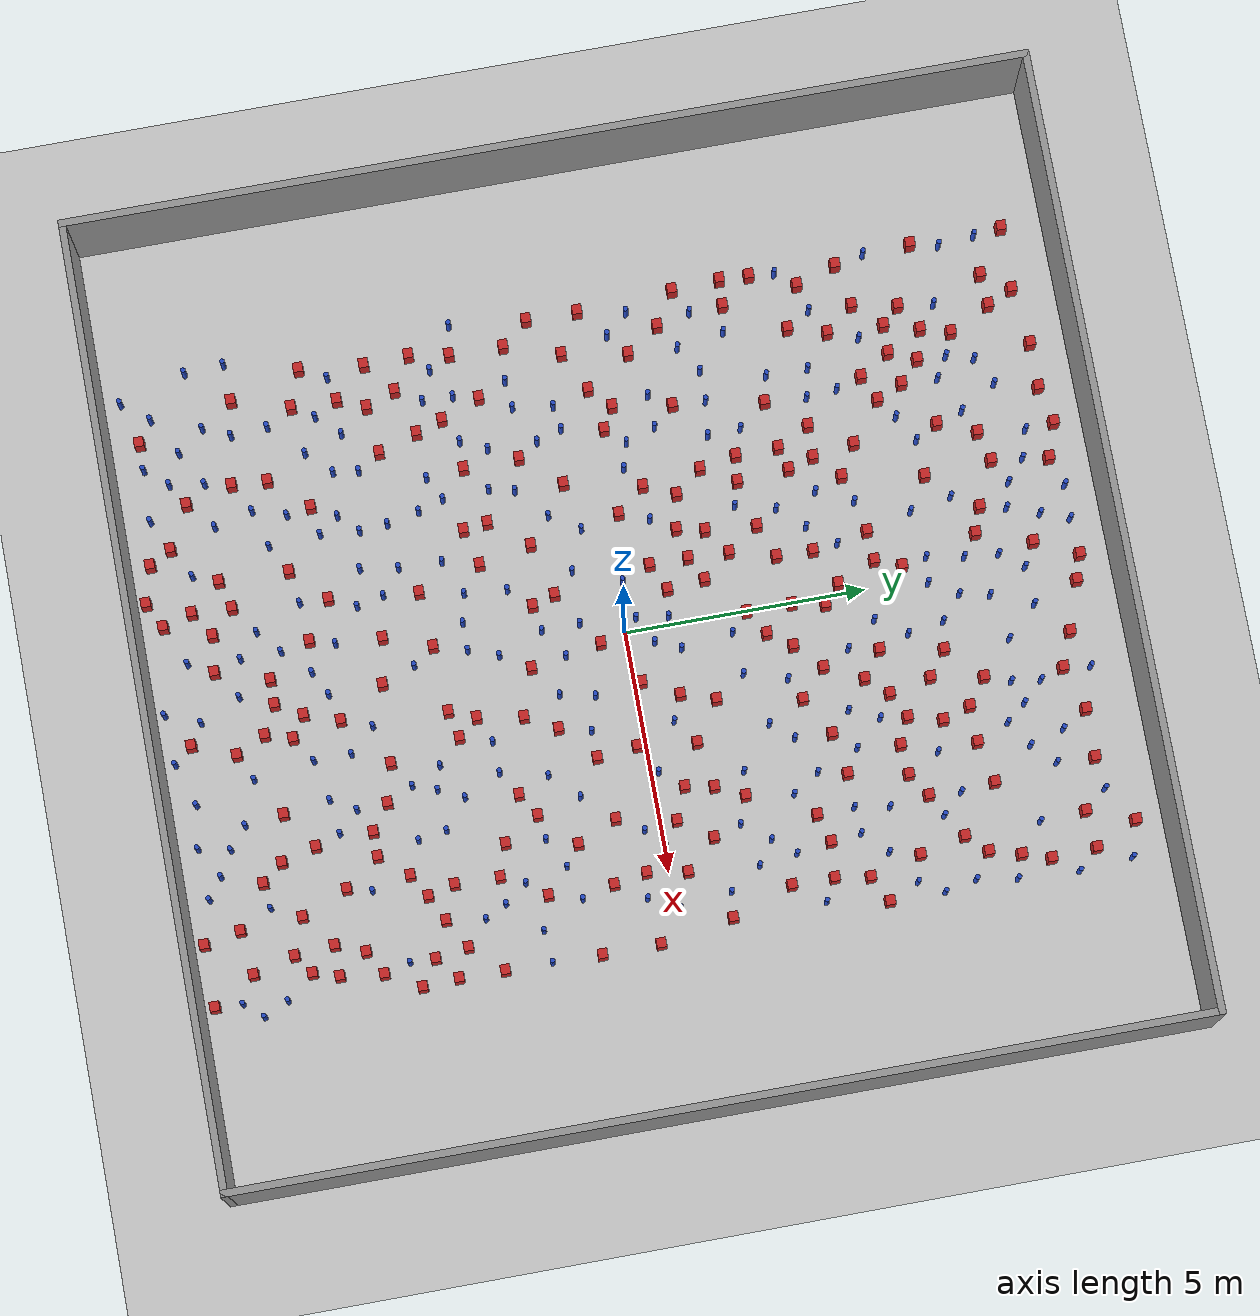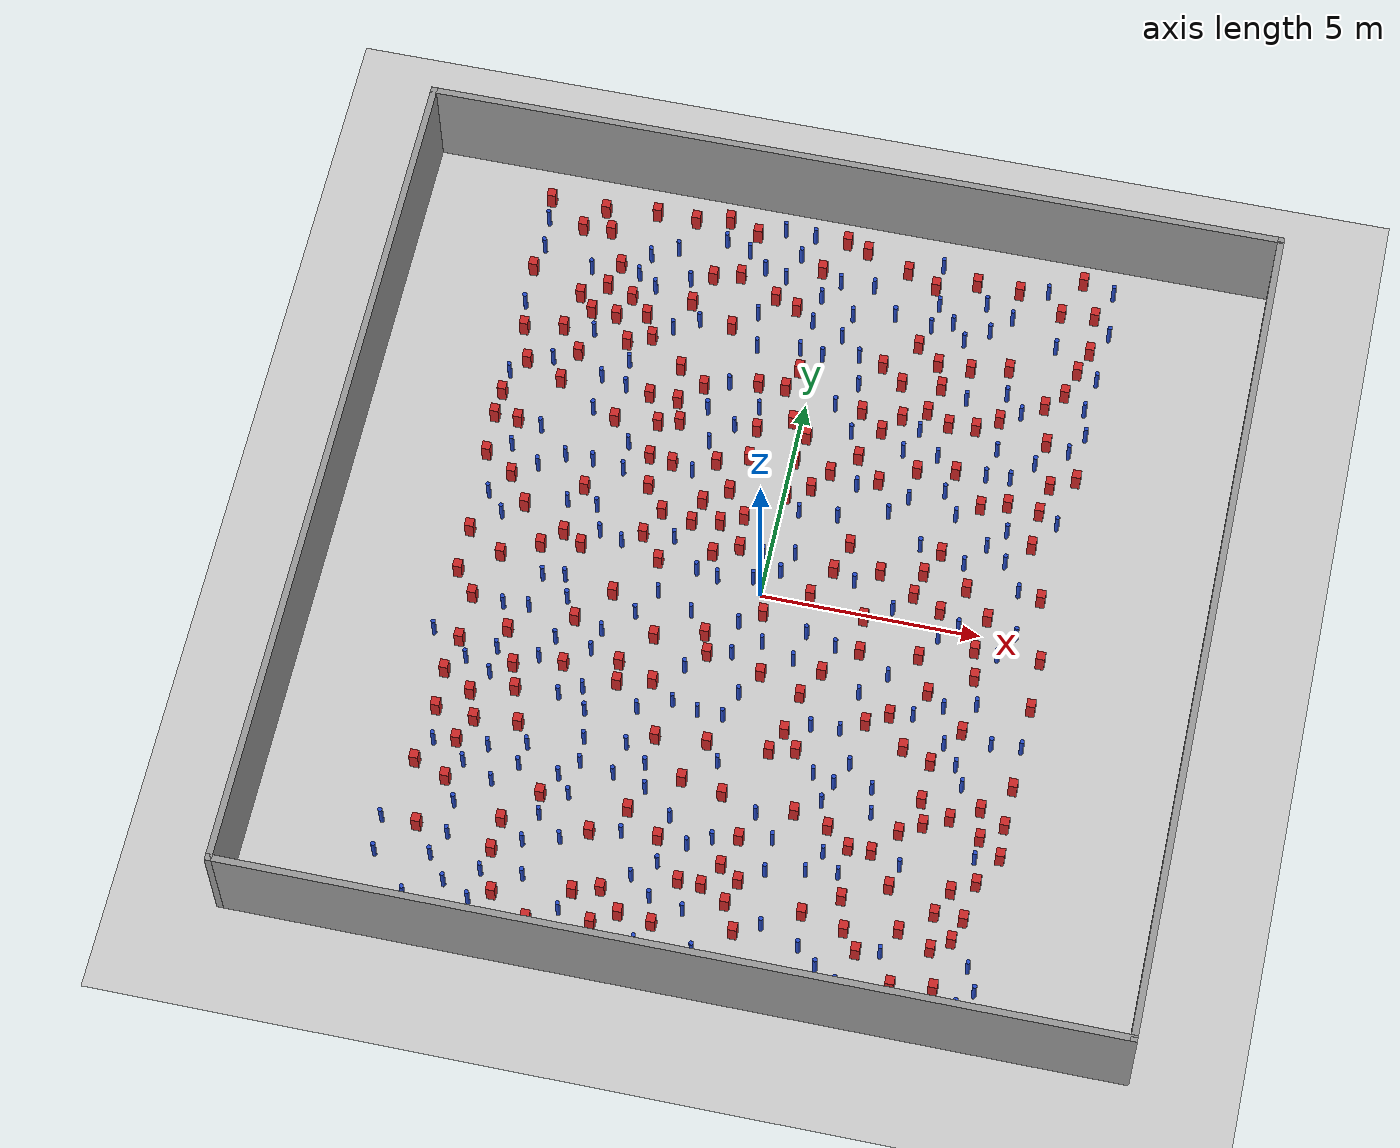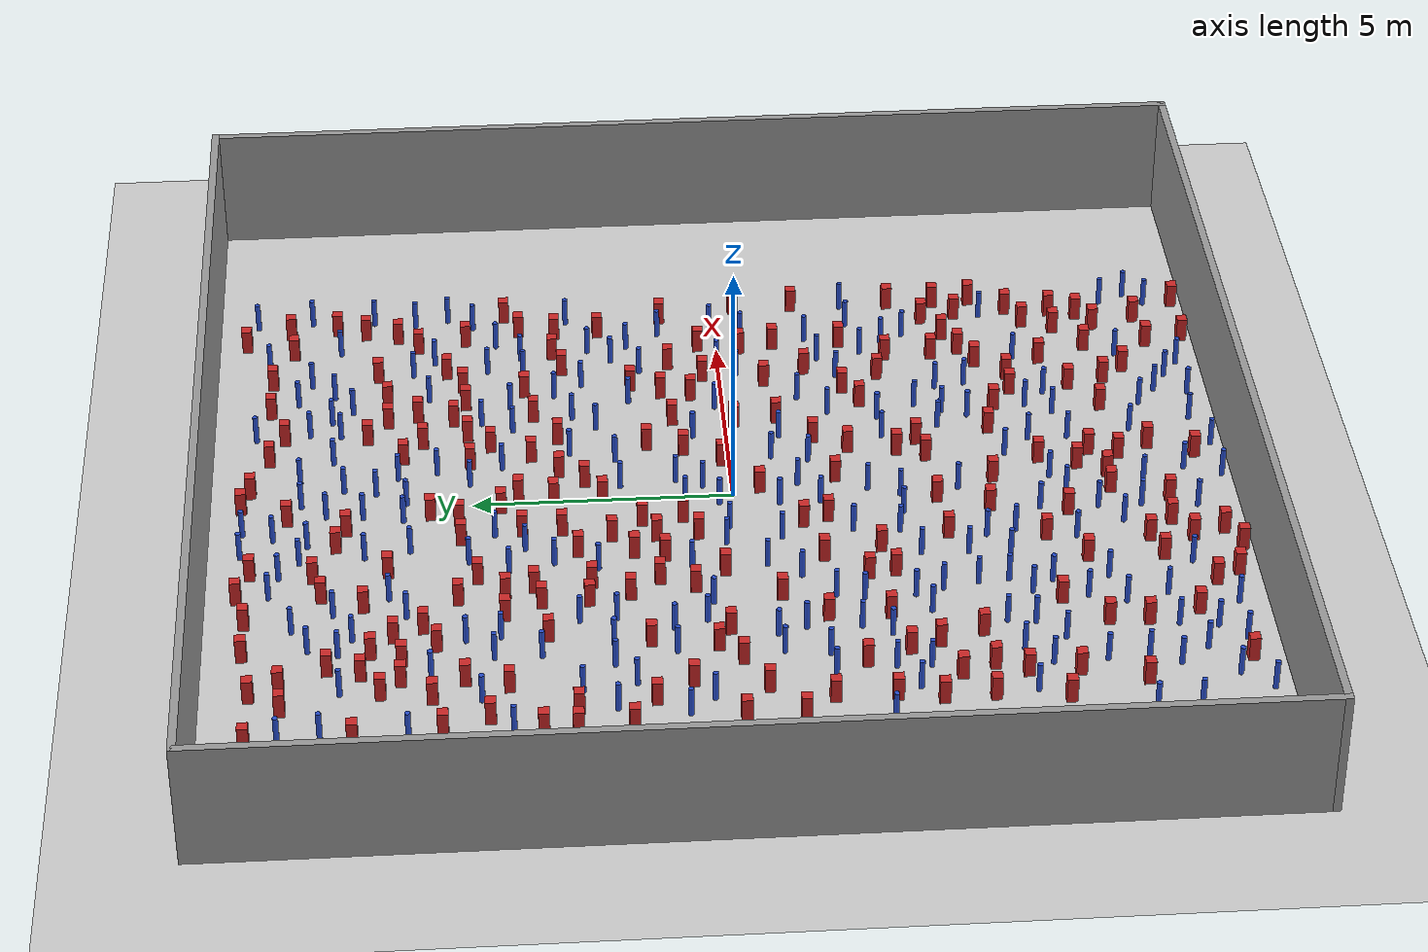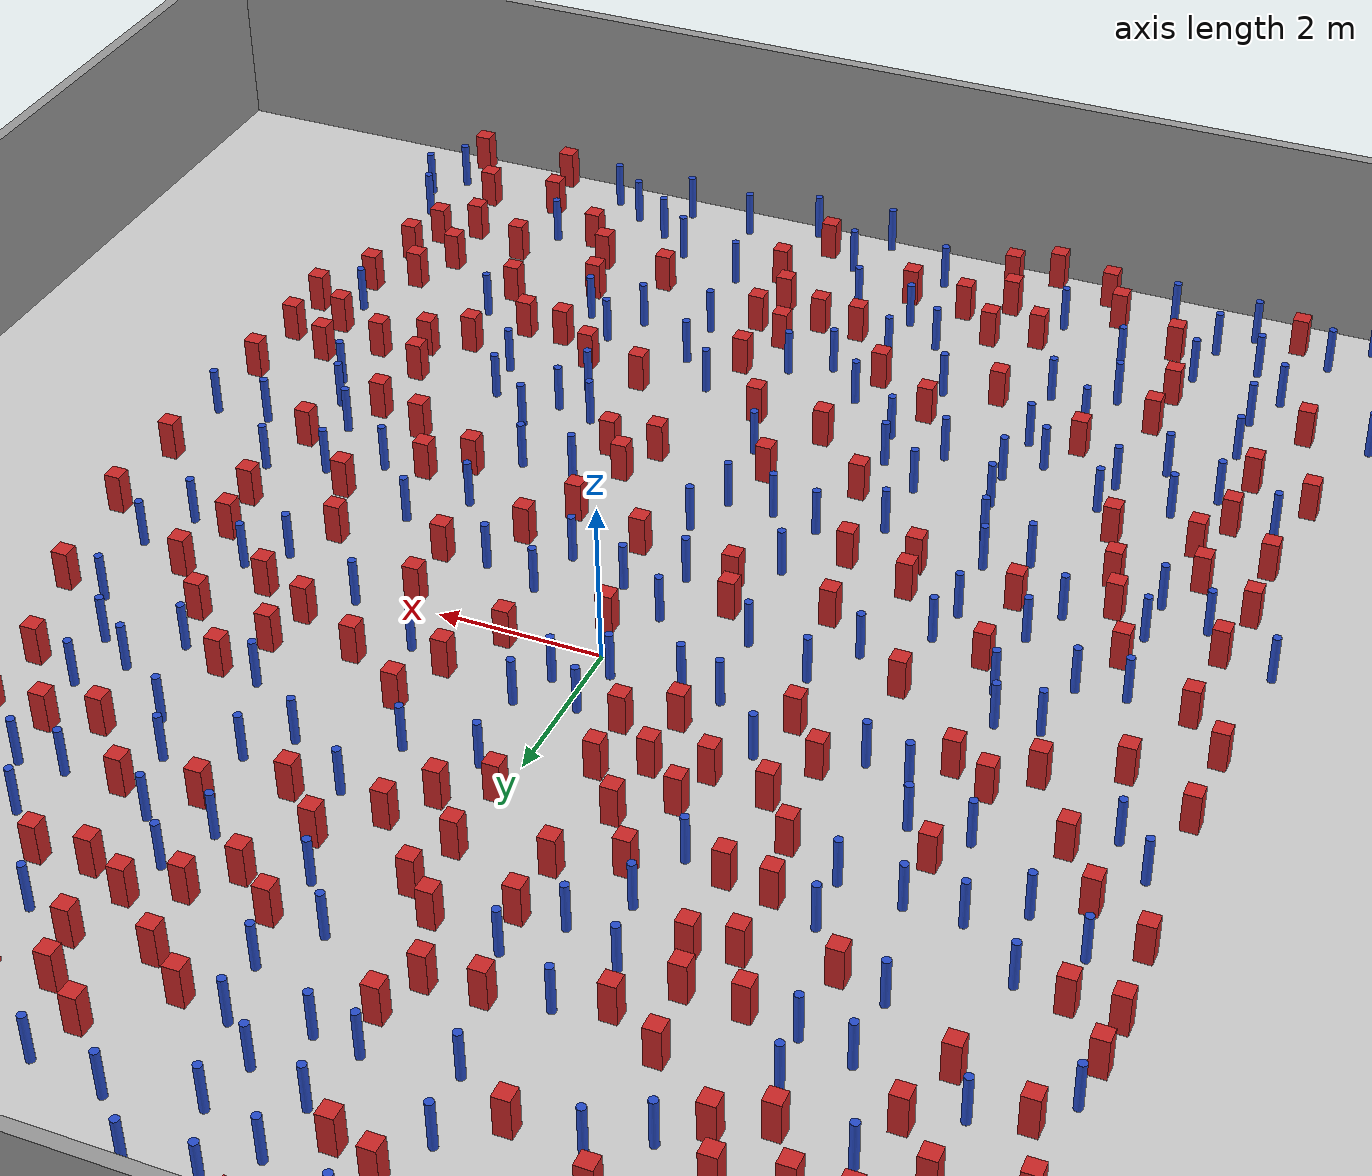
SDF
<sdf version="1.6">
 <world name="default">
  <light name="sun" type="directional">
   <pose>0 0 1000 0 -0 0</pose>
   <diffuse>0.8 0.8 0.8 1</diffuse>
   <specular>0.1 0.1 0.1 1</specular>
   <attenuation>
    <range>1000</range>
    <constant>0.9</constant>
    <linear>0.01</linear>
    <quadratic>0.001</quadratic>
   </attenuation>
   <direction>-0.5 0.5 -1</direction>
  </light>
  <model name="ground_plane">
   <static>1</static>
   <link name="link">
    <collision name="collision">
     <geometry><plane><normal>0 0 1</normal><size>100 100</size></plane></geometry>
     <surface><friction><ode><mu>100</mu><mu2>50</mu2></ode></friction></surface>
    </collision>
    <visual name="visual">
     <cast_shadows>0</cast_shadows>
     <geometry><plane><normal>0 0 1</normal><size>100 100</size></plane></geometry>
     <material>
      <ambient>1.0 1.0 1.0 1.0</ambient>
      <diffuse>0.8 0.8 0.8 1.0</diffuse>
      <specular>0.01 0.01 0.01 1.000000</specular>
     </material>
    </visual>
   </link>
  </model>
  <gravity>0 0 -9.8</gravity>
  <magnetic_field>6e-06 2.3e-05 -4.2e-05</magnetic_field>
  <atmosphere type="adiabatic"/>
  <physics name="default_physics" default="0" type="ode">
   <max_step_size>0.001</max_step_size>
   <real_time_factor>1</real_time_factor>
   <real_time_update_rate>1000</real_time_update_rate>
  </physics>
  <scene><ambient>0.4 0.4 0.4 1</ambient><background>0.7 0.7 0.7 1</background><shadows>1</shadows></scene>
  <spherical_coordinates>
   <surface_model>EARTH_WGS84</surface_model>
   <latitude_deg>0</latitude_deg>
   <longitude_deg>0</longitude_deg>
   <elevation>0</elevation>
   <heading_deg>0</heading_deg>
  </spherical_coordinates>
  <plugin name="gazebo_occupancy_map" filename="libgazebo_2Dmap_plugin.so">
   <map_resolution>0.05</map_resolution>
   <map_topic>generated_map</map_topic>
   <map_height>0.01</map_height>
   <map_size_x>50</map_size_x>
   <map_size_y>50</map_size_y>
  </plugin>
  <model name="NamedLocations">
   <static>true</static>
   <link name="DefaultStart"><pose>8.5 0 0 0 0 3.14</pose></link>
  </model>
  <model name="20x20_walls">
   <pose>0.044518 0.176112 0 0 -0 0</pose>
   <link name="Wall_1">
    <collision name="Wall_1_Collision">
     <geometry><box><size>20 0.15 2.5</size></box></geometry>
     <pose>0 0 1.25 0 -0 0</pose>
    </collision>
    <visual name="Wall_1_Visual">
     <pose>0 0 1.25 0 -0 0</pose>
     <geometry><box><size>20 0.15 2.5</size></box></geometry>
     <material>
      <script><uri>file://media/materials/scripts/gazebo.material</uri><name>Gazebo/Grey</name></script>
      <ambient>0.976471 0.992157 1 1</ambient>
     </material>
     <meta><layer>0</layer></meta>
    </visual>
    <pose>0 9.925 0 0 -0 0</pose>
   </link>
   <link name="Wall_3">
    <collision name="Wall_3_Collision">
     <geometry><box><size>20 0.15 2.5</size></box></geometry>
     <pose>0 0 1.25 0 -0 0</pose>
    </collision>
    <visual name="Wall_3_Visual">
     <pose>0 0 1.25 0 -0 0</pose>
     <geometry><box><size>20 0.15 2.5</size></box></geometry>
     <material>
      <script><uri>file://media/materials/scripts/gazebo.material</uri><name>Gazebo/Grey</name></script>
      <ambient>0.976471 0.992157 1 1</ambient>
     </material>
     <meta><layer>0</layer></meta>
    </visual>
    <pose>9.925 0 0 0 0 -1.5708</pose>
   </link>
   <link name="Wall_4">
    <collision name="Wall_4_Collision">
     <geometry><box><size>20 0.15 2.5</size></box></geometry>
     <pose>0 0 1.25 0 -0 0</pose>
    </collision>
    <visual name="Wall_4_Visual">
     <pose>0 0 1.25 0 -0 0</pose>
     <geometry><box><size>20 0.15 2.5</size></box></geometry>
     <material>
      <script><uri>file://media/materials/scripts/gazebo.material</uri><name>Gazebo/Grey</name></script>
      <ambient>0.976471 0.992157 1 1</ambient>
     </material>
     <meta><layer>0</layer></meta>
    </visual>
    <pose>0 -9.925 0 0 -0 3.14159</pose>
   </link>
   <link name="Wall_5">
    <collision name="Wall_5_Collision">
     <geometry><box><size>20 0.15 2.5</size></box></geometry>
     <pose>0 0 1.25 0 -0 0</pose>
    </collision>
    <visual name="Wall_5_Visual">
     <pose>0 0 1.25 0 -0 0</pose>
     <geometry><box><size>20 0.15 2.5</size></box></geometry>
     <material>
      <script><uri>file://media/materials/scripts/gazebo.material</uri><name>Gazebo/Grey</name></script>
      <ambient>0.976471 0.992157 1 1</ambient>
     </material>
     <meta><layer>0</layer></meta>
    </visual>
    <pose>-9.925 0 0 0 -0 1.5708</pose>
   </link>
   <static>1</static>
  </model>
  <model name="square_post_obstacle0">
   <static>true</static>
   <pose>-1.24056156243 7.60405994039 8.22691968438e-08 7.2212513382e-06 -7.54495500217e-07 2.29674213826e-05</pose>
   <link name="link">
    <pose>0 0 0.25 0 -0 0</pose>
    <inertial>
     <mass>100</mass>
     <inertia>
      <ixx>0.166667</ixx>
      <ixy>0</ixy>
      <ixz>0</ixz>
      <iyy>0.166667</iyy>
      <iyz>0</iyz>
      <izz>0.166667</izz>
     </inertia>
    </inertial>
    <collision name="collision"><geometry><box><size>.2 .2 .5</size></box></geometry></collision>
    <visual name="visual">
     <geometry><box><size>.2 .2 .5</size></box></geometry>
     <material>
      <script><name>Gazebo/Red</name><uri>file://media/materials/scripts/gazebo.material</uri></script>
     </material>
    </visual>
   </link>
  </model>
  <model name="square_post_obstacle1">
   <static>true</static>
   <pose>-5.09552798012 0.169614050784 8.22691968438e-08 7.2212513382e-06 -7.54495500217e-07 2.29674213826e-05</pose>
   <link name="link">
    <pose>0 0 0.25 0 -0 0</pose>
    <inertial>
     <mass>100</mass>
     <inertia>
      <ixx>0.166667</ixx>
      <ixy>0</ixy>
      <ixz>0</ixz>
      <iyy>0.166667</iyy>
      <iyz>0</iyz>
      <izz>0.166667</izz>
     </inertia>
    </inertial>
    <collision name="collision"><geometry><box><size>.2 .2 .5</size></box></geometry></collision>
    <visual name="visual">
     <geometry><box><size>.2 .2 .5</size></box></geometry>
     <material>
      <script><name>Gazebo/Red</name><uri>file://media/materials/scripts/gazebo.material</uri></script>
     </material>
    </visual>
   </link>
  </model>
  <model name="pole_obstacle0">
   <static>true</static>
   <pose>-5.52898609765 -5.44128097975 2.88873142074e-08 -9.90536690842e-09 4.60219948965e-07 -1.20965994976e-07</pose>
   <link name="link">
    <pose>0 0 0.3 0 -0 0</pose>
    <inertial>
     <mass>1</mass>
     <inertia><ixx>0.145833</ixx><ixy>0</ixy><ixz>0</ixz><iyy>0.145833</iyy><iyz>0</iyz><izz>0.125</izz></inertia>
    </inertial>
    <collision name="collision">
     <geometry><cylinder><radius>0.05</radius><length>.6</length></cylinder></geometry>
    </collision>
    <visual name="visual">
     <geometry><cylinder><radius>0.05</radius><length>.6</length></cylinder></geometry>
     <material>
      <script><name>Gazebo/Blue</name><uri>file://media/materials/scripts/gazebo.material</uri></script>
     </material>
    </visual>
   </link>
  </model>
  <model name="square_post_obstacle2">
   <static>true</static>
   <pose>-3.81783800172 5.97276972752 8.22691968438e-08 7.2212513382e-06 -7.54495500217e-07 2.29674213826e-05</pose>
   <link name="link">
    <pose>0 0 0.25 0 -0 0</pose>
    <inertial>
     <mass>100</mass>
     <inertia>
      <ixx>0.166667</ixx>
      <ixy>0</ixy>
      <ixz>0</ixz>
      <iyy>0.166667</iyy>
      <iyz>0</iyz>
      <izz>0.166667</izz>
     </inertia>
    </inertial>
    <collision name="collision"><geometry><box><size>.2 .2 .5</size></box></geometry></collision>
    <visual name="visual">
     <geometry><box><size>.2 .2 .5</size></box></geometry>
     <material>
      <script><name>Gazebo/Red</name><uri>file://media/materials/scripts/gazebo.material</uri></script>
     </material>
    </visual>
   </link>
  </model>
  <model name="pole_obstacle1">
   <static>true</static>
   <pose>2.42879736191 4.18457086736 2.88873142074e-08 -9.90536689859e-09 4.60219948989e-07 -1.20965994961e-07</pose>
   <link name="link">
    <pose>0 0 0.3 0 -0 0</pose>
    <inertial>
     <mass>1</mass>
     <inertia><ixx>0.145833</ixx><ixy>0</ixy><ixz>0</ixz><iyy>0.145833</iyy><iyz>0</iyz><izz>0.125</izz></inertia>
    </inertial>
    <collision name="collision">
     <geometry><cylinder><radius>0.05</radius><length>.6</length></cylinder></geometry>
    </collision>
    <visual name="visual">
     <geometry><cylinder><radius>0.05</radius><length>.6</length></cylinder></geometry>
     <material>
      <script><name>Gazebo/Blue</name><uri>file://media/materials/scripts/gazebo.material</uri></script>
     </material>
    </visual>
   </link>
  </model>
  <model name="square_post_obstacle3">
   <static>true</static>
   <pose>3.93820406455 5.13274334286 8.22691968438e-08 7.2212513382e-06 -7.54495500217e-07 2.29674213826e-05</pose>
   <link name="link">
    <pose>0 0 0.25 0 -0 0</pose>
    <inertial>
     <mass>100</mass>
     <inertia>
      <ixx>0.166667</ixx>
      <ixy>0</ixy>
      <ixz>0</ixz>
      <iyy>0.166667</iyy>
      <iyz>0</iyz>
      <izz>0.166667</izz>
     </inertia>
    </inertial>
    <collision name="collision"><geometry><box><size>.2 .2 .5</size></box></geometry></collision>
    <visual name="visual">
     <geometry><box><size>.2 .2 .5</size></box></geometry>
     <material>
      <script><name>Gazebo/Red</name><uri>file://media/materials/scripts/gazebo.material</uri></script>
     </material>
    </visual>
   </link>
  </model>
  <model name="pole_obstacle2">
   <static>true</static>
   <pose>0.0482527810993 -9.48582412269 2.88873142074e-08 -9.90536690996e-09 4.60219948962e-07 -1.20965994979e-07</pose>
   <link name="link">
    <pose>0 0 0.3 0 -0 0</pose>
    <inertial>
     <mass>1</mass>
     <inertia><ixx>0.145833</ixx><ixy>0</ixy><ixz>0</ixz><iyy>0.145833</iyy><iyz>0</iyz><izz>0.125</izz></inertia>
    </inertial>
    <collision name="collision">
     <geometry><cylinder><radius>0.05</radius><length>.6</length></cylinder></geometry>
    </collision>
    <visual name="visual">
     <geometry><cylinder><radius>0.05</radius><length>.6</length></cylinder></geometry>
     <material>
      <script><name>Gazebo/Blue</name><uri>file://media/materials/scripts/gazebo.material</uri></script>
     </material>
    </visual>
   </link>
  </model>
  <model name="pole_obstacle3">
   <static>true</static>
   <pose>-6.8211940419 4.38299890925 2.88873142074e-08 -9.90536690842e-09 4.60219948965e-07 -1.20965994976e-07</pose>
   <link name="link">
    <pose>0 0 0.3 0 -0 0</pose>
    <inertial>
     <mass>1</mass>
     <inertia><ixx>0.145833</ixx><ixy>0</ixy><ixz>0</ixz><iyy>0.145833</iyy><iyz>0</iyz><izz>0.125</izz></inertia>
    </inertial>
    <collision name="collision">
     <geometry><cylinder><radius>0.05</radius><length>.6</length></cylinder></geometry>
    </collision>
    <visual name="visual">
     <geometry><cylinder><radius>0.05</radius><length>.6</length></cylinder></geometry>
     <material>
      <script><name>Gazebo/Blue</name><uri>file://media/materials/scripts/gazebo.material</uri></script>
     </material>
    </visual>
   </link>
  </model>
  <model name="square_post_obstacle4">
   <static>true</static>
   <pose>4.1547838367 -5.14338606792 8.22691968438e-08 7.22125133819e-06 -7.54495500217e-07 2.29674213826e-05</pose>
   <link name="link">
    <pose>0 0 0.25 0 -0 0</pose>
    <inertial>
     <mass>100</mass>
     <inertia>
      <ixx>0.166667</ixx>
      <ixy>0</ixy>
      <ixz>0</ixz>
      <iyy>0.166667</iyy>
      <iyz>0</iyz>
      <izz>0.166667</izz>
     </inertia>
    </inertial>
    <collision name="collision"><geometry><box><size>.2 .2 .5</size></box></geometry></collision>
    <visual name="visual">
     <geometry><box><size>.2 .2 .5</size></box></geometry>
     <material>
      <script><name>Gazebo/Red</name><uri>file://media/materials/scripts/gazebo.material</uri></script>
     </material>
    </visual>
   </link>
  </model>
  <model name="square_post_obstacle5">
   <static>true</static>
   <pose>-0.739914075484 -4.86374876013 8.22691968438e-08 7.2212513382e-06 -7.54495500217e-07 2.29674213826e-05</pose>
   <link name="link">
    <pose>0 0 0.25 0 -0 0</pose>
    <inertial>
     <mass>100</mass>
     <inertia>
      <ixx>0.166667</ixx>
      <ixy>0</ixy>
      <ixz>0</ixz>
      <iyy>0.166667</iyy>
      <iyz>0</iyz>
      <izz>0.166667</izz>
     </inertia>
    </inertial>
    <collision name="collision"><geometry><box><size>.2 .2 .5</size></box></geometry></collision>
    <visual name="visual">
     <geometry><box><size>.2 .2 .5</size></box></geometry>
     <material>
      <script><name>Gazebo/Red</name><uri>file://media/materials/scripts/gazebo.material</uri></script>
     </material>
    </visual>
   </link>
  </model>
  <model name="square_post_obstacle6">
   <static>true</static>
   <pose>0.612230005593 9.25797296877 8.22691968438e-08 7.22125133819e-06 -7.54495500217e-07 2.29674213826e-05</pose>
   <link name="link">
    <pose>0 0 0.25 0 -0 0</pose>
    <inertial>
     <mass>100</mass>
     <inertia>
      <ixx>0.166667</ixx>
      <ixy>0</ixy>
      <ixz>0</ixz>
      <iyy>0.166667</iyy>
      <iyz>0</iyz>
      <izz>0.166667</izz>
     </inertia>
    </inertial>
    <collision name="collision"><geometry><box><size>.2 .2 .5</size></box></geometry></collision>
    <visual name="visual">
     <geometry><box><size>.2 .2 .5</size></box></geometry>
     <material>
      <script><name>Gazebo/Red</name><uri>file://media/materials/scripts/gazebo.material</uri></script>
     </material>
    </visual>
   </link>
  </model>
  <model name="pole_obstacle4">
   <static>true</static>
   <pose>-5.45148548055 -7.20574879343 2.88873142074e-08 -9.90536690842e-09 4.60219948965e-07 -1.20965994976e-07</pose>
   <link name="link">
    <pose>0 0 0.3 0 -0 0</pose>
    <inertial>
     <mass>1</mass>
     <inertia><ixx>0.145833</ixx><ixy>0</ixy><ixz>0</ixz><iyy>0.145833</iyy><iyz>0</iyz><izz>0.125</izz></inertia>
    </inertial>
    <collision name="collision">
     <geometry><cylinder><radius>0.05</radius><length>.6</length></cylinder></geometry>
    </collision>
    <visual name="visual">
     <geometry><cylinder><radius>0.05</radius><length>.6</length></cylinder></geometry>
     <material>
      <script><name>Gazebo/Blue</name><uri>file://media/materials/scripts/gazebo.material</uri></script>
     </material>
    </visual>
   </link>
  </model>
  <model name="pole_obstacle5">
   <static>true</static>
   <pose>-3.96869382587 -9.11810775149 2.88873142074e-08 -9.90536690427e-09 4.60219948975e-07 -1.2096599497e-07</pose>
   <link name="link">
    <pose>0 0 0.3 0 -0 0</pose>
    <inertial>
     <mass>1</mass>
     <inertia><ixx>0.145833</ixx><ixy>0</ixy><ixz>0</ixz><iyy>0.145833</iyy><iyz>0</iyz><izz>0.125</izz></inertia>
    </inertial>
    <collision name="collision">
     <geometry><cylinder><radius>0.05</radius><length>.6</length></cylinder></geometry>
    </collision>
    <visual name="visual">
     <geometry><cylinder><radius>0.05</radius><length>.6</length></cylinder></geometry>
     <material>
      <script><name>Gazebo/Blue</name><uri>file://media/materials/scripts/gazebo.material</uri></script>
     </material>
    </visual>
   </link>
  </model>
  <model name="square_post_obstacle7">
   <static>true</static>
   <pose>1.10828673552 -8.17682160192 8.22691968438e-08 7.22125133819e-06 -7.54495500217e-07 2.29674213826e-05</pose>
   <link name="link">
    <pose>0 0 0.25 0 -0 0</pose>
    <inertial>
     <mass>100</mass>
     <inertia>
      <ixx>0.166667</ixx>
      <ixy>0</ixy>
      <ixz>0</ixz>
      <iyy>0.166667</iyy>
      <iyz>0</iyz>
      <izz>0.166667</izz>
     </inertia>
    </inertial>
    <collision name="collision"><geometry><box><size>.2 .2 .5</size></box></geometry></collision>
    <visual name="visual">
     <geometry><box><size>.2 .2 .5</size></box></geometry>
     <material>
      <script><name>Gazebo/Red</name><uri>file://media/materials/scripts/gazebo.material</uri></script>
     </material>
    </visual>
   </link>
  </model>
  <model name="square_post_obstacle8">
   <static>true</static>
   <pose>2.05817050153 5.94106591254 8.22691968438e-08 7.22125133819e-06 -7.54495500217e-07 2.29674213826e-05</pose>
   <link name="link">
    <pose>0 0 0.25 0 -0 0</pose>
    <inertial>
     <mass>100</mass>
     <inertia>
      <ixx>0.166667</ixx>
      <ixy>0</ixy>
      <ixz>0</ixz>
      <iyy>0.166667</iyy>
      <iyz>0</iyz>
      <izz>0.166667</izz>
     </inertia>
    </inertial>
    <collision name="collision"><geometry><box><size>.2 .2 .5</size></box></geometry></collision>
    <visual name="visual">
     <geometry><box><size>.2 .2 .5</size></box></geometry>
     <material>
      <script><name>Gazebo/Red</name><uri>file://media/materials/scripts/gazebo.material</uri></script>
     </material>
    </visual>
   </link>
  </model>
  <model name="pole_obstacle6">
   <static>true</static>
   <pose>-6.06268718287 -8.77293479968 2.88873142074e-08 -9.9053668967e-09 4.60219948993e-07 -1.20965994957e-07</pose>
   <link name="link">
    <pose>0 0 0.3 0 -0 0</pose>
    <inertial>
     <mass>1</mass>
     <inertia><ixx>0.145833</ixx><ixy>0</ixy><ixz>0</ixz><iyy>0.145833</iyy><iyz>0</iyz><izz>0.125</izz></inertia>
    </inertial>
    <collision name="collision">
     <geometry><cylinder><radius>0.05</radius><length>.6</length></cylinder></geometry>
    </collision>
    <visual name="visual">
     <geometry><cylinder><radius>0.05</radius><length>.6</length></cylinder></geometry>
     <material>
      <script><name>Gazebo/Blue</name><uri>file://media/materials/scripts/gazebo.material</uri></script>
     </material>
    </visual>
   </link>
  </model>
  <model name="pole_obstacle7">
   <static>true</static>
   <pose>-0.292384732256 -6.39790182835 2.88873142074e-08 -9.90536689618e-09 4.60219948994e-07 -1.20965994956e-07</pose>
   <link name="link">
    <pose>0 0 0.3 0 -0 0</pose>
    <inertial>
     <mass>1</mass>
     <inertia><ixx>0.145833</ixx><ixy>0</ixy><ixz>0</ixz><iyy>0.145833</iyy><iyz>0</iyz><izz>0.125</izz></inertia>
    </inertial>
    <collision name="collision">
     <geometry><cylinder><radius>0.05</radius><length>.6</length></cylinder></geometry>
    </collision>
    <visual name="visual">
     <geometry><cylinder><radius>0.05</radius><length>.6</length></cylinder></geometry>
     <material>
      <script><name>Gazebo/Blue</name><uri>file://media/materials/scripts/gazebo.material</uri></script>
     </material>
    </visual>
   </link>
  </model>
  <model name="square_post_obstacle9">
   <static>true</static>
   <pose>1.46546212937 3.84372808108 8.22691968438e-08 7.2212513382e-06 -7.54495500217e-07 2.29674213826e-05</pose>
   <link name="link">
    <pose>0 0 0.25 0 -0 0</pose>
    <inertial>
     <mass>100</mass>
     <inertia>
      <ixx>0.166667</ixx>
      <ixy>0</ixy>
      <ixz>0</ixz>
      <iyy>0.166667</iyy>
      <iyz>0</iyz>
      <izz>0.166667</izz>
     </inertia>
    </inertial>
    <collision name="collision"><geometry><box><size>.2 .2 .5</size></box></geometry></collision>
    <visual name="visual">
     <geometry><box><size>.2 .2 .5</size></box></geometry>
     <material>
      <script><name>Gazebo/Red</name><uri>file://media/materials/scripts/gazebo.material</uri></script>
     </material>
    </visual>
   </link>
  </model>
  <model name="square_post_obstacle10">
   <static>true</static>
   <pose>5.57316279647 -8.58295188289 8.22691968438e-08 7.22125133819e-06 -7.54495500217e-07 2.29674213826e-05</pose>
   <link name="link">
    <pose>0 0 0.25 0 -0 0</pose>
    <inertial>
     <mass>100</mass>
     <inertia>
      <ixx>0.166667</ixx>
      <ixy>0</ixy>
      <ixz>0</ixz>
      <iyy>0.166667</iyy>
      <iyz>0</iyz>
      <izz>0.166667</izz>
     </inertia>
    </inertial>
    <collision name="collision"><geometry><box><size>.2 .2 .5</size></box></geometry></collision>
    <visual name="visual">
     <geometry><box><size>.2 .2 .5</size></box></geometry>
     <material>
      <script><name>Gazebo/Red</name><uri>file://media/materials/scripts/gazebo.material</uri></script>
     </material>
    </visual>
   </link>
  </model>
  <model name="square_post_obstacle11">
   <static>true</static>
   <pose>-3.3232403131 -8.80907015829 8.22691968438e-08 7.22125133819e-06 -7.54495500217e-07 2.29674213826e-05</pose>
   <link name="link">
    <pose>0 0 0.25 0 -0 0</pose>
    <inertial>
     <mass>100</mass>
     <inertia>
      <ixx>0.166667</ixx>
      <ixy>0</ixy>
      <ixz>0</ixz>
      <iyy>0.166667</iyy>
      <iyz>0</iyz>
      <izz>0.166667</izz>
     </inertia>
    </inertial>
    <collision name="collision"><geometry><box><size>.2 .2 .5</size></box></geometry></collision>
    <visual name="visual">
     <geometry><box><size>.2 .2 .5</size></box></geometry>
     <material>
      <script><name>Gazebo/Red</name><uri>file://media/materials/scripts/gazebo.material</uri></script>
     </material>
    </visual>
   </link>
  </model>
  <model name="square_post_obstacle12">
   <static>true</static>
   <pose>6.08532268999 8.58405498495 8.22691968438e-08 7.22125133819e-06 -7.54495500217e-07 2.29674213826e-05</pose>
   <link name="link">
    <pose>0 0 0.25 0 -0 0</pose>
    <inertial>
     <mass>100</mass>
     <inertia>
      <ixx>0.166667</ixx>
      <ixy>0</ixy>
      <ixz>0</ixz>
      <iyy>0.166667</iyy>
      <iyz>0</iyz>
      <izz>0.166667</izz>
     </inertia>
    </inertial>
    <collision name="collision"><geometry><box><size>.2 .2 .5</size></box></geometry></collision>
    <visual name="visual">
     <geometry><box><size>.2 .2 .5</size></box></geometry>
     <material>
      <script><name>Gazebo/Red</name><uri>file://media/materials/scripts/gazebo.material</uri></script>
     </material>
    </visual>
   </link>
  </model>
  <model name="square_post_obstacle13">
   <static>true</static>
   <pose>2.34242101366 8.63387449862 8.22691968438e-08 7.22125133819e-06 -7.54495500217e-07 2.29674213826e-05</pose>
   <link name="link">
    <pose>0 0 0.25 0 -0 0</pose>
    <inertial>
     <mass>100</mass>
     <inertia>
      <ixx>0.166667</ixx>
      <ixy>0</ixy>
      <ixz>0</ixz>
      <iyy>0.166667</iyy>
      <iyz>0</iyz>
      <izz>0.166667</izz>
     </inertia>
    </inertial>
    <collision name="collision"><geometry><box><size>.2 .2 .5</size></box></geometry></collision>
    <visual name="visual">
     <geometry><box><size>.2 .2 .5</size></box></geometry>
     <material>
      <script><name>Gazebo/Red</name><uri>file://media/materials/scripts/gazebo.material</uri></script>
     </material>
    </visual>
   </link>
  </model>
  <model name="pole_obstacle8">
   <static>true</static>
   <pose>-1.11618082176 8.14739392024 2.88873142074e-08 -9.90536690474e-09 4.60219948974e-07 -1.2096599497e-07</pose>
   <link name="link">
    <pose>0 0 0.3 0 -0 0</pose>
    <inertial>
     <mass>1</mass>
     <inertia><ixx>0.145833</ixx><ixy>0</ixy><ixz>0</ixz><iyy>0.145833</iyy><iyz>0</iyz><izz>0.125</izz></inertia>
    </inertial>
    <collision name="collision">
     <geometry><cylinder><radius>0.05</radius><length>.6</length></cylinder></geometry>
    </collision>
    <visual name="visual">
     <geometry><cylinder><radius>0.05</radius><length>.6</length></cylinder></geometry>
     <material>
      <script><name>Gazebo/Blue</name><uri>file://media/materials/scripts/gazebo.material</uri></script>
     </material>
    </visual>
   </link>
  </model>
  <model name="square_post_obstacle14">
   <static>true</static>
   <pose>-2.71619464707 -2.35196584994 8.22691968438e-08 7.2212513382e-06 -7.54495500217e-07 2.29674213826e-05</pose>
   <link name="link">
    <pose>0 0 0.25 0 -0 0</pose>
    <inertial>
     <mass>100</mass>
     <inertia>
      <ixx>0.166667</ixx>
      <ixy>0</ixy>
      <ixz>0</ixz>
      <iyy>0.166667</iyy>
      <iyz>0</iyz>
      <izz>0.166667</izz>
     </inertia>
    </inertial>
    <collision name="collision"><geometry><box><size>.2 .2 .5</size></box></geometry></collision>
    <visual name="visual">
     <geometry><box><size>.2 .2 .5</size></box></geometry>
     <material>
      <script><name>Gazebo/Red</name><uri>file://media/materials/scripts/gazebo.material</uri></script>
     </material>
    </visual>
   </link>
  </model>
  <model name="square_post_obstacle15">
   <static>true</static>
   <pose>5.27767397775 -6.88327287838 8.22691968438e-08 7.2212513382e-06 -7.54495500217e-07 2.29674213826e-05</pose>
   <link name="link">
    <pose>0 0 0.25 0 -0 0</pose>
    <inertial>
     <mass>100</mass>
     <inertia>
      <ixx>0.166667</ixx>
      <ixy>0</ixy>
      <ixz>0</ixz>
      <iyy>0.166667</iyy>
      <iyz>0</iyz>
      <izz>0.166667</izz>
     </inertia>
    </inertial>
    <collision name="collision"><geometry><box><size>.2 .2 .5</size></box></geometry></collision>
    <visual name="visual">
     <geometry><box><size>.2 .2 .5</size></box></geometry>
     <material>
      <script><name>Gazebo/Red</name><uri>file://media/materials/scripts/gazebo.material</uri></script>
     </material>
    </visual>
   </link>
  </model>
  <model name="square_post_obstacle16">
   <static>true</static>
   <pose>-2.29271488066 -9.47991698428 8.22691968438e-08 7.22125133819e-06 -7.54495500217e-07 2.29674213826e-05</pose>
   <link name="link">
    <pose>0 0 0.25 0 -0 0</pose>
    <inertial>
     <mass>100</mass>
     <inertia>
      <ixx>0.166667</ixx>
      <ixy>0</ixy>
      <ixz>0</ixz>
      <iyy>0.166667</iyy>
      <iyz>0</iyz>
      <izz>0.166667</izz>
     </inertia>
    </inertial>
    <collision name="collision"><geometry><box><size>.2 .2 .5</size></box></geometry></collision>
    <visual name="visual">
     <geometry><box><size>.2 .2 .5</size></box></geometry>
     <material>
      <script><name>Gazebo/Red</name><uri>file://media/materials/scripts/gazebo.material</uri></script>
     </material>
    </visual>
   </link>
  </model>
  <model name="pole_obstacle9">
   <static>true</static>
   <pose>-5.272801551 -8.31432086041 2.88873142074e-08 -9.9053668967e-09 4.60219948993e-07 -1.20965994957e-07</pose>
   <link name="link">
    <pose>0 0 0.3 0 -0 0</pose>
    <inertial>
     <mass>1</mass>
     <inertia><ixx>0.145833</ixx><ixy>0</ixy><ixz>0</ixz><iyy>0.145833</iyy><iyz>0</iyz><izz>0.125</izz></inertia>
    </inertial>
    <collision name="collision">
     <geometry><cylinder><radius>0.05</radius><length>.6</length></cylinder></geometry>
    </collision>
    <visual name="visual">
     <geometry><cylinder><radius>0.05</radius><length>.6</length></cylinder></geometry>
     <material>
      <script><name>Gazebo/Blue</name><uri>file://media/materials/scripts/gazebo.material</uri></script>
     </material>
    </visual>
   </link>
  </model>
  <model name="square_post_obstacle17">
   <static>true</static>
   <pose>4.26680201008 8.90688729605 8.22691968438e-08 7.22125133819e-06 -7.54495500217e-07 2.29674213826e-05</pose>
   <link name="link">
    <pose>0 0 0.25 0 -0 0</pose>
    <inertial>
     <mass>100</mass>
     <inertia>
      <ixx>0.166667</ixx>
      <ixy>0</ixy>
      <ixz>0</ixz>
      <iyy>0.166667</iyy>
      <iyz>0</iyz>
      <izz>0.166667</izz>
     </inertia>
    </inertial>
    <collision name="collision"><geometry><box><size>.2 .2 .5</size></box></geometry></collision>
    <visual name="visual">
     <geometry><box><size>.2 .2 .5</size></box></geometry>
     <material>
      <script><name>Gazebo/Red</name><uri>file://media/materials/scripts/gazebo.material</uri></script>
     </material>
    </visual>
   </link>
  </model>
  <model name="square_post_obstacle18">
   <static>true</static>
   <pose>-0.949726159683 -6.34032384962 8.22691968438e-08 7.22125133819e-06 -7.54495500217e-07 2.29674213826e-05</pose>
   <link name="link">
    <pose>0 0 0.25 0 -0 0</pose>
    <inertial>
     <mass>100</mass>
     <inertia>
      <ixx>0.166667</ixx>
      <ixy>0</ixy>
      <ixz>0</ixz>
      <iyy>0.166667</iyy>
      <iyz>0</iyz>
      <izz>0.166667</izz>
     </inertia>
    </inertial>
    <collision name="collision"><geometry><box><size>.2 .2 .5</size></box></geometry></collision>
    <visual name="visual">
     <geometry><box><size>.2 .2 .5</size></box></geometry>
     <material>
      <script><name>Gazebo/Red</name><uri>file://media/materials/scripts/gazebo.material</uri></script>
     </material>
    </visual>
   </link>
  </model>
  <model name="pole_obstacle10">
   <static>true</static>
   <pose>-1.26184989518 -2.19216682164 2.88873142074e-08 -9.90536689791e-09 4.6021994899e-07 -1.20965994959e-07</pose>
   <link name="link">
    <pose>0 0 0.3 0 -0 0</pose>
    <inertial>
     <mass>1</mass>
     <inertia><ixx>0.145833</ixx><ixy>0</ixy><ixz>0</ixz><iyy>0.145833</iyy><iyz>0</iyz><izz>0.125</izz></inertia>
    </inertial>
    <collision name="collision">
     <geometry><cylinder><radius>0.05</radius><length>.6</length></cylinder></geometry>
    </collision>
    <visual name="visual">
     <geometry><cylinder><radius>0.05</radius><length>.6</length></cylinder></geometry>
     <material>
      <script><name>Gazebo/Blue</name><uri>file://media/materials/scripts/gazebo.material</uri></script>
     </material>
    </visual>
   </link>
  </model>
  <model name="square_post_obstacle19">
   <static>true</static>
   <pose>-2.99553876486 5.32065947652 8.22691968438e-08 7.2212513382e-06 -7.54495500217e-07 2.29674213826e-05</pose>
   <link name="link">
    <pose>0 0 0.25 0 -0 0</pose>
    <inertial>
     <mass>100</mass>
     <inertia>
      <ixx>0.166667</ixx>
      <ixy>0</ixy>
      <ixz>0</ixz>
      <iyy>0.166667</iyy>
      <iyz>0</iyz>
      <izz>0.166667</izz>
     </inertia>
    </inertial>
    <collision name="collision"><geometry><box><size>.2 .2 .5</size></box></geometry></collision>
    <visual name="visual">
     <geometry><box><size>.2 .2 .5</size></box></geometry>
     <material>
      <script><name>Gazebo/Red</name><uri>file://media/materials/scripts/gazebo.material</uri></script>
     </material>
    </visual>
   </link>
  </model>
  <model name="pole_obstacle11">
   <static>true</static>
   <pose>-6.87196957462 8.5809538864 2.88873142074e-08 -9.9053668967e-09 4.60219948993e-07 -1.20965994957e-07</pose>
   <link name="link">
    <pose>0 0 0.3 0 -0 0</pose>
    <inertial>
     <mass>1</mass>
     <inertia><ixx>0.145833</ixx><ixy>0</ixy><ixz>0</ixz><iyy>0.145833</iyy><iyz>0</iyz><izz>0.125</izz></inertia>
    </inertial>
    <collision name="collision">
     <geometry><cylinder><radius>0.05</radius><length>.6</length></cylinder></geometry>
    </collision>
    <visual name="visual">
     <geometry><cylinder><radius>0.05</radius><length>.6</length></cylinder></geometry>
     <material>
      <script><name>Gazebo/Blue</name><uri>file://media/materials/scripts/gazebo.material</uri></script>
     </material>
    </visual>
   </link>
  </model>
  <model name="square_post_obstacle20">
   <static>true</static>
   <pose>-6.92894778926 7.24512789114 8.22691968438e-08 7.2212513382e-06 -7.54495500217e-07 2.29674213826e-05</pose>
   <link name="link">
    <pose>0 0 0.25 0 -0 0</pose>
    <inertial>
     <mass>100</mass>
     <inertia>
      <ixx>0.166667</ixx>
      <ixy>0</ixy>
      <ixz>0</ixz>
      <iyy>0.166667</iyy>
      <iyz>0</iyz>
      <izz>0.166667</izz>
     </inertia>
    </inertial>
    <collision name="collision"><geometry><box><size>.2 .2 .5</size></box></geometry></collision>
    <visual name="visual">
     <geometry><box><size>.2 .2 .5</size></box></geometry>
     <material>
      <script><name>Gazebo/Red</name><uri>file://media/materials/scripts/gazebo.material</uri></script>
     </material>
    </visual>
   </link>
  </model>
  <model name="pole_obstacle12">
   <static>true</static>
   <pose>2.97804801223 0.164714240803 2.88873142074e-08 -9.90536689314e-09 4.60219949002e-07 -1.20965994953e-07</pose>
   <link name="link">
    <pose>0 0 0.3 0 -0 0</pose>
    <inertial>
     <mass>1</mass>
     <inertia><ixx>0.145833</ixx><ixy>0</ixy><ixz>0</ixz><iyy>0.145833</iyy><iyz>0</iyz><izz>0.125</izz></inertia>
    </inertial>
    <collision name="collision">
     <geometry><cylinder><radius>0.05</radius><length>.6</length></cylinder></geometry>
    </collision>
    <visual name="visual">
     <geometry><cylinder><radius>0.05</radius><length>.6</length></cylinder></geometry>
     <material>
      <script><name>Gazebo/Blue</name><uri>file://media/materials/scripts/gazebo.material</uri></script>
     </material>
    </visual>
   </link>
  </model>
  <model name="square_post_obstacle21">
   <static>true</static>
   <pose>-4.8261092977 -3.45431383046 8.22691968438e-08 7.2212513382e-06 -7.54495500217e-07 2.29674213826e-05</pose>
   <link name="link">
    <pose>0 0 0.25 0 -0 0</pose>
    <inertial>
     <mass>100</mass>
     <inertia>
      <ixx>0.166667</ixx>
      <ixy>0</ixy>
      <ixz>0</ixz>
      <iyy>0.166667</iyy>
      <iyz>0</iyz>
      <izz>0.166667</izz>
     </inertia>
    </inertial>
    <collision name="collision"><geometry><box><size>.2 .2 .5</size></box></geometry></collision>
    <visual name="visual">
     <geometry><box><size>.2 .2 .5</size></box></geometry>
     <material>
      <script><name>Gazebo/Red</name><uri>file://media/materials/scripts/gazebo.material</uri></script>
     </material>
    </visual>
   </link>
  </model>
  <model name="pole_obstacle13">
   <static>true</static>
   <pose>4.47920381448 6.11489741807 2.88873142074e-08 -9.90536690842e-09 4.60219948965e-07 -1.20965994976e-07</pose>
   <link name="link">
    <pose>0 0 0.3 0 -0 0</pose>
    <inertial>
     <mass>1</mass>
     <inertia><ixx>0.145833</ixx><ixy>0</ixy><ixz>0</ixz><iyy>0.145833</iyy><iyz>0</iyz><izz>0.125</izz></inertia>
    </inertial>
    <collision name="collision">
     <geometry><cylinder><radius>0.05</radius><length>.6</length></cylinder></geometry>
    </collision>
    <visual name="visual">
     <geometry><cylinder><radius>0.05</radius><length>.6</length></cylinder></geometry>
     <material>
      <script><name>Gazebo/Blue</name><uri>file://media/materials/scripts/gazebo.material</uri></script>
     </material>
    </visual>
   </link>
  </model>
  <model name="square_post_obstacle22">
   <static>true</static>
   <pose>-3.49046418424 9.27107695211 8.22691968438e-08 7.22125133819e-06 -7.54495500217e-07 2.29674213826e-05</pose>
   <link name="link">
    <pose>0 0 0.25 0 -0 0</pose>
    <inertial>
     <mass>100</mass>
     <inertia>
      <ixx>0.166667</ixx>
      <ixy>0</ixy>
      <ixz>0</ixz>
      <iyy>0.166667</iyy>
      <iyz>0</iyz>
      <izz>0.166667</izz>
     </inertia>
    </inertial>
    <collision name="collision"><geometry><box><size>.2 .2 .5</size></box></geometry></collision>
    <visual name="visual">
     <geometry><box><size>.2 .2 .5</size></box></geometry>
     <material>
      <script><name>Gazebo/Red</name><uri>file://media/materials/scripts/gazebo.material</uri></script>
     </material>
    </visual>
   </link>
  </model>
  <model name="pole_obstacle14">
   <static>true</static>
   <pose>1.67014155416 -7.91802049187 2.88873142074e-08 -9.90536689852e-09 4.60219948989e-07 -1.2096599496e-07</pose>
   <link name="link">
    <pose>0 0 0.3 0 -0 0</pose>
    <inertial>
     <mass>1</mass>
     <inertia><ixx>0.145833</ixx><ixy>0</ixy><ixz>0</ixz><iyy>0.145833</iyy><iyz>0</iyz><izz>0.125</izz></inertia>
    </inertial>
    <collision name="collision">
     <geometry><cylinder><radius>0.05</radius><length>.6</length></cylinder></geometry>
    </collision>
    <visual name="visual">
     <geometry><cylinder><radius>0.05</radius><length>.6</length></cylinder></geometry>
     <material>
      <script><name>Gazebo/Blue</name><uri>file://media/materials/scripts/gazebo.material</uri></script>
     </material>
    </visual>
   </link>
  </model>
  <model name="pole_obstacle15">
   <static>true</static>
   <pose>-0.0539101587184 -7.93211417524 2.88873142074e-08 -9.90536689643e-09 4.60219948994e-07 -1.20965994959e-07</pose>
   <link name="link">
    <pose>0 0 0.3 0 -0 0</pose>
    <inertial>
     <mass>1</mass>
     <inertia><ixx>0.145833</ixx><ixy>0</ixy><ixz>0</ixz><iyy>0.145833</iyy><iyz>0</iyz><izz>0.125</izz></inertia>
    </inertial>
    <collision name="collision">
     <geometry><cylinder><radius>0.05</radius><length>.6</length></cylinder></geometry>
    </collision>
    <visual name="visual">
     <geometry><cylinder><radius>0.05</radius><length>.6</length></cylinder></geometry>
     <material>
      <script><name>Gazebo/Blue</name><uri>file://media/materials/scripts/gazebo.material</uri></script>
     </material>
    </visual>
   </link>
  </model>
  <model name="pole_obstacle16">
   <static>true</static>
   <pose>4.10393876735 -0.329731906449 2.88873142074e-08 -9.90536689981e-09 4.60219948986e-07 -1.20965994962e-07</pose>
   <link name="link">
    <pose>0 0 0.3 0 -0 0</pose>
    <inertial>
     <mass>1</mass>
     <inertia><ixx>0.145833</ixx><ixy>0</ixy><ixz>0</ixz><iyy>0.145833</iyy><iyz>0</iyz><izz>0.125</izz></inertia>
    </inertial>
    <collision name="collision">
     <geometry><cylinder><radius>0.05</radius><length>.6</length></cylinder></geometry>
    </collision>
    <visual name="visual">
     <geometry><cylinder><radius>0.05</radius><length>.6</length></cylinder></geometry>
     <material>
      <script><name>Gazebo/Blue</name><uri>file://media/materials/scripts/gazebo.material</uri></script>
     </material>
    </visual>
   </link>
  </model>
  <model name="square_post_obstacle23">
   <static>true</static>
   <pose>-0.949453098267 4.08446247527 8.22691968438e-08 7.22125133819e-06 -7.54495500217e-07 2.29674213826e-05</pose>
   <link name="link">
    <pose>0 0 0.25 0 -0 0</pose>
    <inertial>
     <mass>100</mass>
     <inertia>
      <ixx>0.166667</ixx>
      <ixy>0</ixy>
      <ixz>0</ixz>
      <iyy>0.166667</iyy>
      <iyz>0</iyz>
      <izz>0.166667</izz>
     </inertia>
    </inertial>
    <collision name="collision"><geometry><box><size>.2 .2 .5</size></box></geometry></collision>
    <visual name="visual">
     <geometry><box><size>.2 .2 .5</size></box></geometry>
     <material>
      <script><name>Gazebo/Red</name><uri>file://media/materials/scripts/gazebo.material</uri></script>
     </material>
    </visual>
   </link>
  </model>
  <model name="pole_obstacle17">
   <static>true</static>
   <pose>-2.62959651649 -1.09778085469 2.88873142074e-08 -9.90536689395e-09 4.60219949e-07 -1.20965994953e-07</pose>
   <link name="link">
    <pose>0 0 0.3 0 -0 0</pose>
    <inertial>
     <mass>1</mass>
     <inertia><ixx>0.145833</ixx><ixy>0</ixy><ixz>0</ixz><iyy>0.145833</iyy><iyz>0</iyz><izz>0.125</izz></inertia>
    </inertial>
    <collision name="collision">
     <geometry><cylinder><radius>0.05</radius><length>.6</length></cylinder></geometry>
    </collision>
    <visual name="visual">
     <geometry><cylinder><radius>0.05</radius><length>.6</length></cylinder></geometry>
     <material>
      <script><name>Gazebo/Blue</name><uri>file://media/materials/scripts/gazebo.material</uri></script>
     </material>
    </visual>
   </link>
  </model>
  <model name="square_post_obstacle24">
   <static>true</static>
   <pose>0.161639222224 -0.51346482138 8.22691968438e-08 7.2212513382e-06 -7.54495500217e-07 2.29674213826e-05</pose>
   <link name="link">
    <pose>0 0 0.25 0 -0 0</pose>
    <inertial>
     <mass>100</mass>
     <inertia>
      <ixx>0.166667</ixx>
      <ixy>0</ixy>
      <ixz>0</ixz>
      <iyy>0.166667</iyy>
      <iyz>0</iyz>
      <izz>0.166667</izz>
     </inertia>
    </inertial>
    <collision name="collision"><geometry><box><size>.2 .2 .5</size></box></geometry></collision>
    <visual name="visual">
     <geometry><box><size>.2 .2 .5</size></box></geometry>
     <material>
      <script><name>Gazebo/Red</name><uri>file://media/materials/scripts/gazebo.material</uri></script>
     </material>
    </visual>
   </link>
  </model>
  <model name="square_post_obstacle25">
   <static>true</static>
   <pose>5.09198572183 0.379569240633 8.22691968438e-08 7.2212513382e-06 -7.54495500217e-07 2.29674213826e-05</pose>
   <link name="link">
    <pose>0 0 0.25 0 -0 0</pose>
    <inertial>
     <mass>100</mass>
     <inertia>
      <ixx>0.166667</ixx>
      <ixy>0</ixy>
      <ixz>0</ixz>
      <iyy>0.166667</iyy>
      <iyz>0</iyz>
      <izz>0.166667</izz>
     </inertia>
    </inertial>
    <collision name="collision"><geometry><box><size>.2 .2 .5</size></box></geometry></collision>
    <visual name="visual">
     <geometry><box><size>.2 .2 .5</size></box></geometry>
     <material>
      <script><name>Gazebo/Red</name><uri>file://media/materials/scripts/gazebo.material</uri></script>
     </material>
    </visual>
   </link>
  </model>
  <model name="square_post_obstacle26">
   <static>true</static>
   <pose>-4.56124194803 -4.27651367608 8.22691968438e-08 7.2212513382e-06 -7.54495500217e-07 2.29674213826e-05</pose>
   <link name="link">
    <pose>0 0 0.25 0 -0 0</pose>
    <inertial>
     <mass>100</mass>
     <inertia>
      <ixx>0.166667</ixx>
      <ixy>0</ixy>
      <ixz>0</ixz>
      <iyy>0.166667</iyy>
      <iyz>0</iyz>
      <izz>0.166667</izz>
     </inertia>
    </inertial>
    <collision name="collision"><geometry><box><size>.2 .2 .5</size></box></geometry></collision>
    <visual name="visual">
     <geometry><box><size>.2 .2 .5</size></box></geometry>
     <material>
      <script><name>Gazebo/Red</name><uri>file://media/materials/scripts/gazebo.material</uri></script>
     </material>
    </visual>
   </link>
  </model>
  <model name="square_post_obstacle27">
   <static>true</static>
   <pose>-5.32435496994 -2.06732113186 8.22691968438e-08 7.2212513382e-06 -7.54495500217e-07 2.29674213826e-05</pose>
   <link name="link">
    <pose>0 0 0.25 0 -0 0</pose>
    <inertial>
     <mass>100</mass>
     <inertia>
      <ixx>0.166667</ixx>
      <ixy>0</ixy>
      <ixz>0</ixz>
      <iyy>0.166667</iyy>
      <iyz>0</iyz>
      <izz>0.166667</izz>
     </inertia>
    </inertial>
    <collision name="collision"><geometry><box><size>.2 .2 .5</size></box></geometry></collision>
    <visual name="visual">
     <geometry><box><size>.2 .2 .5</size></box></geometry>
     <material>
      <script><name>Gazebo/Red</name><uri>file://media/materials/scripts/gazebo.material</uri></script>
     </material>
    </visual>
   </link>
  </model>
  <model name="pole_obstacle18">
   <static>true</static>
   <pose>1.56160406141 7.6801341566 2.88873142074e-08 -9.90536689852e-09 4.60219948989e-07 -1.2096599496e-07</pose>
   <link name="link">
    <pose>0 0 0.3 0 -0 0</pose>
    <inertial>
     <mass>1</mass>
     <inertia><ixx>0.145833</ixx><ixy>0</ixy><ixz>0</ixz><iyy>0.145833</iyy><iyz>0</iyz><izz>0.125</izz></inertia>
    </inertial>
    <collision name="collision">
     <geometry><cylinder><radius>0.05</radius><length>.6</length></cylinder></geometry>
    </collision>
    <visual name="visual">
     <geometry><cylinder><radius>0.05</radius><length>.6</length></cylinder></geometry>
     <material>
      <script><name>Gazebo/Blue</name><uri>file://media/materials/scripts/gazebo.material</uri></script>
     </material>
    </visual>
   </link>
  </model>
  <model name="square_post_obstacle28">
   <static>true</static>
   <pose>-4.65914052058 0.591915527668 8.22691968438e-08 7.2212513382e-06 -7.54495500217e-07 2.29674213826e-05</pose>
   <link name="link">
    <pose>0 0 0.25 0 -0 0</pose>
    <inertial>
     <mass>100</mass>
     <inertia>
      <ixx>0.166667</ixx>
      <ixy>0</ixy>
      <ixz>0</ixz>
      <iyy>0.166667</iyy>
      <iyz>0</iyz>
      <izz>0.166667</izz>
     </inertia>
    </inertial>
    <collision name="collision"><geometry><box><size>.2 .2 .5</size></box></geometry></collision>
    <visual name="visual">
     <geometry><box><size>.2 .2 .5</size></box></geometry>
     <material>
      <script><name>Gazebo/Red</name><uri>file://media/materials/scripts/gazebo.material</uri></script>
     </material>
    </visual>
   </link>
  </model>
  <model name="pole_obstacle19">
   <static>true</static>
   <pose>-6.894988678 6.25508551908 2.88873142074e-08 -9.90536690842e-09 4.60219948965e-07 -1.20965994976e-07</pose>
   <link name="link">
    <pose>0 0 0.3 0 -0 0</pose>
    <inertial>
     <mass>1</mass>
     <inertia><ixx>0.145833</ixx><ixy>0</ixy><ixz>0</ixz><iyy>0.145833</iyy><iyz>0</iyz><izz>0.125</izz></inertia>
    </inertial>
    <collision name="collision">
     <geometry><cylinder><radius>0.05</radius><length>.6</length></cylinder></geometry>
    </collision>
    <visual name="visual">
     <geometry><cylinder><radius>0.05</radius><length>.6</length></cylinder></geometry>
     <material>
      <script><name>Gazebo/Blue</name><uri>file://media/materials/scripts/gazebo.material</uri></script>
     </material>
    </visual>
   </link>
  </model>
  <model name="square_post_obstacle29">
   <static>true</static>
   <pose>-2.15079923924 8.02366086059 8.22691968438e-08 7.22125133819e-06 -7.54495500217e-07 2.29674213826e-05</pose>
   <link name="link">
    <pose>0 0 0.25 0 -0 0</pose>
    <inertial>
     <mass>100</mass>
     <inertia>
      <ixx>0.166667</ixx>
      <ixy>0</ixy>
      <ixz>0</ixz>
      <iyy>0.166667</iyy>
      <iyz>0</iyz>
      <izz>0.166667</izz>
     </inertia>
    </inertial>
    <collision name="collision"><geometry><box><size>.2 .2 .5</size></box></geometry></collision>
    <visual name="visual">
     <geometry><box><size>.2 .2 .5</size></box></geometry>
     <material>
      <script><name>Gazebo/Red</name><uri>file://media/materials/scripts/gazebo.material</uri></script>
     </material>
    </visual>
   </link>
  </model>
  <model name="square_post_obstacle30">
   <static>true</static>
   <pose>6.08593054036 -9.45582256099 8.22691968438e-08 7.2212513382e-06 -7.54495500217e-07 2.29674213826e-05</pose>
   <link name="link">
    <pose>0 0 0.25 0 -0 0</pose>
    <inertial>
     <mass>100</mass>
     <inertia>
      <ixx>0.166667</ixx>
      <ixy>0</ixy>
      <ixz>0</ixz>
      <iyy>0.166667</iyy>
      <iyz>0</iyz>
      <izz>0.166667</izz>
     </inertia>
    </inertial>
    <collision name="collision"><geometry><box><size>.2 .2 .5</size></box></geometry></collision>
    <visual name="visual">
     <geometry><box><size>.2 .2 .5</size></box></geometry>
     <material>
      <script><name>Gazebo/Red</name><uri>file://media/materials/scripts/gazebo.material</uri></script>
     </material>
    </visual>
   </link>
  </model>
  <model name="pole_obstacle20">
   <static>true</static>
   <pose>-2.18454358331 0.933623202442 2.88873142074e-08 -9.90536689285e-09 4.60219949002e-07 -1.20965994953e-07</pose>
   <link name="link">
    <pose>0 0 0.3 0 -0 0</pose>
    <inertial>
     <mass>1</mass>
     <inertia><ixx>0.145833</ixx><ixy>0</ixy><ixz>0</ixz><iyy>0.145833</iyy><iyz>0</iyz><izz>0.125</izz></inertia>
    </inertial>
    <collision name="collision">
     <geometry><cylinder><radius>0.05</radius><length>.6</length></cylinder></geometry>
    </collision>
    <visual name="visual">
     <geometry><cylinder><radius>0.05</radius><length>.6</length></cylinder></geometry>
     <material>
      <script><name>Gazebo/Blue</name><uri>file://media/materials/scripts/gazebo.material</uri></script>
     </material>
    </visual>
   </link>
  </model>
  <model name="pole_obstacle21">
   <static>true</static>
   <pose>-4.54711957399 -7.90253743116 2.88873142074e-08 -9.90536690842e-09 4.60219948965e-07 -1.20965994976e-07</pose>
   <link name="link">
    <pose>0 0 0.3 0 -0 0</pose>
    <inertial>
     <mass>1</mass>
     <inertia><ixx>0.145833</ixx><ixy>0</ixy><ixz>0</ixz><iyy>0.145833</iyy><iyz>0</iyz><izz>0.125</izz></inertia>
    </inertial>
    <collision name="collision">
     <geometry><cylinder><radius>0.05</radius><length>.6</length></cylinder></geometry>
    </collision>
    <visual name="visual">
     <geometry><cylinder><radius>0.05</radius><length>.6</length></cylinder></geometry>
     <material>
      <script><name>Gazebo/Blue</name><uri>file://media/materials/scripts/gazebo.material</uri></script>
     </material>
    </visual>
   </link>
  </model>
  <model name="square_post_obstacle31">
   <static>true</static>
   <pose>-5.37480407238 8.58938074372 8.22691968438e-08 7.22125133819e-06 -7.54495500217e-07 2.29674213826e-05</pose>
   <link name="link">
    <pose>0 0 0.25 0 -0 0</pose>
    <inertial>
     <mass>100</mass>
     <inertia>
      <ixx>0.166667</ixx>
      <ixy>0</ixy>
      <ixz>0</ixz>
      <iyy>0.166667</iyy>
      <iyz>0</iyz>
      <izz>0.166667</izz>
     </inertia>
    </inertial>
    <collision name="collision"><geometry><box><size>.2 .2 .5</size></box></geometry></collision>
    <visual name="visual">
     <geometry><box><size>.2 .2 .5</size></box></geometry>
     <material>
      <script><name>Gazebo/Red</name><uri>file://media/materials/scripts/gazebo.material</uri></script>
     </material>
    </visual>
   </link>
  </model>
  <model name="pole_obstacle22">
   <static>true</static>
   <pose>2.55716048454 -8.24796795358 2.88873142074e-08 -9.90536692318e-09 4.6021994893e-07 -1.20965994988e-07</pose>
   <link name="link">
    <pose>0 0 0.3 0 -0 0</pose>
    <inertial>
     <mass>1</mass>
     <inertia><ixx>0.145833</ixx><ixy>0</ixy><ixz>0</ixz><iyy>0.145833</iyy><iyz>0</iyz><izz>0.125</izz></inertia>
    </inertial>
    <collision name="collision">
     <geometry><cylinder><radius>0.05</radius><length>.6</length></cylinder></geometry>
    </collision>
    <visual name="visual">
     <geometry><cylinder><radius>0.05</radius><length>.6</length></cylinder></geometry>
     <material>
      <script><name>Gazebo/Blue</name><uri>file://media/materials/scripts/gazebo.material</uri></script>
     </material>
    </visual>
   </link>
  </model>
  <model name="pole_obstacle23">
   <static>true</static>
   <pose>2.64523516485 -5.97530829579 2.88873142074e-08 -9.90536689859e-09 4.60219948989e-07 -1.20965994961e-07</pose>
   <link name="link">
    <pose>0 0 0.3 0 -0 0</pose>
    <inertial>
     <mass>1</mass>
     <inertia><ixx>0.145833</ixx><ixy>0</ixy><ixz>0</ixz><iyy>0.145833</iyy><iyz>0</iyz><izz>0.125</izz></inertia>
    </inertial>
    <collision name="collision">
     <geometry><cylinder><radius>0.05</radius><length>.6</length></cylinder></geometry>
    </collision>
    <visual name="visual">
     <geometry><cylinder><radius>0.05</radius><length>.6</length></cylinder></geometry>
     <material>
      <script><name>Gazebo/Blue</name><uri>file://media/materials/scripts/gazebo.material</uri></script>
     </material>
    </visual>
   </link>
  </model>
  <model name="pole_obstacle24">
   <static>true</static>
   <pose>2.69714781437 4.78767704699 2.88873142074e-08 -9.90536689859e-09 4.60219948989e-07 -1.20965994961e-07</pose>
   <link name="link">
    <pose>0 0 0.3 0 -0 0</pose>
    <inertial>
     <mass>1</mass>
     <inertia><ixx>0.145833</ixx><ixy>0</ixy><ixz>0</ixz><iyy>0.145833</iyy><iyz>0</iyz><izz>0.125</izz></inertia>
    </inertial>
    <collision name="collision">
     <geometry><cylinder><radius>0.05</radius><length>.6</length></cylinder></geometry>
    </collision>
    <visual name="visual">
     <geometry><cylinder><radius>0.05</radius><length>.6</length></cylinder></geometry>
     <material>
      <script><name>Gazebo/Blue</name><uri>file://media/materials/scripts/gazebo.material</uri></script>
     </material>
    </visual>
   </link>
  </model>
  <model name="pole_obstacle25">
   <static>true</static>
   <pose>-3.62066253817 -7.84233535312 2.88873142074e-08 -9.90536692062e-09 4.60219948937e-07 -1.20965994985e-07</pose>
   <link name="link">
    <pose>0 0 0.3 0 -0 0</pose>
    <inertial>
     <mass>1</mass>
     <inertia><ixx>0.145833</ixx><ixy>0</ixy><ixz>0</ixz><iyy>0.145833</iyy><iyz>0</iyz><izz>0.125</izz></inertia>
    </inertial>
    <collision name="collision">
     <geometry><cylinder><radius>0.05</radius><length>.6</length></cylinder></geometry>
    </collision>
    <visual name="visual">
     <geometry><cylinder><radius>0.05</radius><length>.6</length></cylinder></geometry>
     <material>
      <script><name>Gazebo/Blue</name><uri>file://media/materials/scripts/gazebo.material</uri></script>
     </material>
    </visual>
   </link>
  </model>
  <model name="pole_obstacle26">
   <static>true</static>
   <pose>-3.08424011812 -5.7530450633 2.88873142074e-08 -9.90536692062e-09 4.60219948937e-07 -1.20965994985e-07</pose>
   <link name="link">
    <pose>0 0 0.3 0 -0 0</pose>
    <inertial>
     <mass>1</mass>
     <inertia><ixx>0.145833</ixx><ixy>0</ixy><ixz>0</ixz><iyy>0.145833</iyy><iyz>0</iyz><izz>0.125</izz></inertia>
    </inertial>
    <collision name="collision">
     <geometry><cylinder><radius>0.05</radius><length>.6</length></cylinder></geometry>
    </collision>
    <visual name="visual">
     <geometry><cylinder><radius>0.05</radius><length>.6</length></cylinder></geometry>
     <material>
      <script><name>Gazebo/Blue</name><uri>file://media/materials/scripts/gazebo.material</uri></script>
     </material>
    </visual>
   </link>
  </model>
  <model name="pole_obstacle27">
   <static>true</static>
   <pose>-2.83430194717 6.60351410121 2.88873142074e-08 -9.90536689859e-09 4.60219948989e-07 -1.20965994961e-07</pose>
   <link name="link">
    <pose>0 0 0.3 0 -0 0</pose>
    <inertial>
     <mass>1</mass>
     <inertia><ixx>0.145833</ixx><ixy>0</ixy><ixz>0</ixz><iyy>0.145833</iyy><iyz>0</iyz><izz>0.125</izz></inertia>
    </inertial>
    <collision name="collision">
     <geometry><cylinder><radius>0.05</radius><length>.6</length></cylinder></geometry>
    </collision>
    <visual name="visual">
     <geometry><cylinder><radius>0.05</radius><length>.6</length></cylinder></geometry>
     <material>
      <script><name>Gazebo/Blue</name><uri>file://media/materials/scripts/gazebo.material</uri></script>
     </material>
    </visual>
   </link>
  </model>
  <model name="square_post_obstacle32">
   <static>true</static>
   <pose>3.78396789695 -8.08853005912 8.22691968438e-08 7.22125133819e-06 -7.54495500217e-07 2.29674213826e-05</pose>
   <link name="link">
    <pose>0 0 0.25 0 -0 0</pose>
    <inertial>
     <mass>100</mass>
     <inertia>
      <ixx>0.166667</ixx>
      <ixy>0</ixy>
      <ixz>0</ixz>
      <iyy>0.166667</iyy>
      <iyz>0</iyz>
      <izz>0.166667</izz>
     </inertia>
    </inertial>
    <collision name="collision"><geometry><box><size>.2 .2 .5</size></box></geometry></collision>
    <visual name="visual">
     <geometry><box><size>.2 .2 .5</size></box></geometry>
     <material>
      <script><name>Gazebo/Red</name><uri>file://media/materials/scripts/gazebo.material</uri></script>
     </material>
    </visual>
   </link>
  </model>
  <model name="square_post_obstacle33">
   <static>true</static>
   <pose>-5.00915330419 -2.89200436723 8.22691968438e-08 7.2212513382e-06 -7.54495500217e-07 2.29674213826e-05</pose>
   <link name="link">
    <pose>0 0 0.25 0 -0 0</pose>
    <inertial>
     <mass>100</mass>
     <inertia>
      <ixx>0.166667</ixx>
      <ixy>0</ixy>
      <ixz>0</ixz>
      <iyy>0.166667</iyy>
      <iyz>0</iyz>
      <izz>0.166667</izz>
     </inertia>
    </inertial>
    <collision name="collision"><geometry><box><size>.2 .2 .5</size></box></geometry></collision>
    <visual name="visual">
     <geometry><box><size>.2 .2 .5</size></box></geometry>
     <material>
      <script><name>Gazebo/Red</name><uri>file://media/materials/scripts/gazebo.material</uri></script>
     </material>
    </visual>
   </link>
  </model>
  <model name="pole_obstacle28">
   <static>true</static>
   <pose>-0.881720828298 8.80049282505 2.88873142074e-08 -9.90536690779e-09 4.60219948967e-07 -1.20965994975e-07</pose>
   <link name="link">
    <pose>0 0 0.3 0 -0 0</pose>
    <inertial>
     <mass>1</mass>
     <inertia><ixx>0.145833</ixx><ixy>0</ixy><ixz>0</ixz><iyy>0.145833</iyy><iyz>0</iyz><izz>0.125</izz></inertia>
    </inertial>
    <collision name="collision">
     <geometry><cylinder><radius>0.05</radius><length>.6</length></cylinder></geometry>
    </collision>
    <visual name="visual">
     <geometry><cylinder><radius>0.05</radius><length>.6</length></cylinder></geometry>
     <material>
      <script><name>Gazebo/Blue</name><uri>file://media/materials/scripts/gazebo.material</uri></script>
     </material>
    </visual>
   </link>
  </model>
  <model name="pole_obstacle29">
   <static>true</static>
   <pose>-4.07144258752 1.3700278536 2.88873142074e-08 -9.90536689445e-09 4.60219948999e-07 -1.20965994956e-07</pose>
   <link name="link">
    <pose>0 0 0.3 0 -0 0</pose>
    <inertial>
     <mass>1</mass>
     <inertia><ixx>0.145833</ixx><ixy>0</ixy><ixz>0</ixz><iyy>0.145833</iyy><iyz>0</iyz><izz>0.125</izz></inertia>
    </inertial>
    <collision name="collision">
     <geometry><cylinder><radius>0.05</radius><length>.6</length></cylinder></geometry>
    </collision>
    <visual name="visual">
     <geometry><cylinder><radius>0.05</radius><length>.6</length></cylinder></geometry>
     <material>
      <script><name>Gazebo/Blue</name><uri>file://media/materials/scripts/gazebo.material</uri></script>
     </material>
    </visual>
   </link>
  </model>
  <model name="square_post_obstacle34">
   <static>true</static>
   <pose>4.43094901096 5.45059155126 8.22691968438e-08 7.2212513382e-06 -7.54495500217e-07 2.29674213826e-05</pose>
   <link name="link">
    <pose>0 0 0.25 0 -0 0</pose>
    <inertial>
     <mass>100</mass>
     <inertia>
      <ixx>0.166667</ixx>
      <ixy>0</ixy>
      <ixz>0</ixz>
      <iyy>0.166667</iyy>
      <iyz>0</iyz>
      <izz>0.166667</izz>
     </inertia>
    </inertial>
    <collision name="collision"><geometry><box><size>.2 .2 .5</size></box></geometry></collision>
    <visual name="visual">
     <geometry><box><size>.2 .2 .5</size></box></geometry>
     <material>
      <script><name>Gazebo/Red</name><uri>file://media/materials/scripts/gazebo.material</uri></script>
     </material>
    </visual>
   </link>
  </model>
  <model name="pole_obstacle30">
   <static>true</static>
   <pose>2.00604831403 0.665068035087 2.88873142074e-08 -9.90536689439e-09 4.60219948999e-07 -1.20965994955e-07</pose>
   <link name="link">
    <pose>0 0 0.3 0 -0 0</pose>
    <inertial>
     <mass>1</mass>
     <inertia><ixx>0.145833</ixx><ixy>0</ixy><ixz>0</ixz><iyy>0.145833</iyy><iyz>0</iyz><izz>0.125</izz></inertia>
    </inertial>
    <collision name="collision">
     <geometry><cylinder><radius>0.05</radius><length>.6</length></cylinder></geometry>
    </collision>
    <visual name="visual">
     <geometry><cylinder><radius>0.05</radius><length>.6</length></cylinder></geometry>
     <material>
      <script><name>Gazebo/Blue</name><uri>file://media/materials/scripts/gazebo.material</uri></script>
     </material>
    </visual>
   </link>
  </model>
  <model name="pole_obstacle31">
   <static>true</static>
   <pose>-1.37464773365 9.41036834551 2.88873142074e-08 -9.90536690474e-09 4.60219948974e-07 -1.2096599497e-07</pose>
   <link name="link">
    <pose>0 0 0.3 0 -0 0</pose>
    <inertial>
     <mass>1</mass>
     <inertia><ixx>0.145833</ixx><ixy>0</ixy><ixz>0</ixz><iyy>0.145833</iyy><iyz>0</iyz><izz>0.125</izz></inertia>
    </inertial>
    <collision name="collision">
     <geometry><cylinder><radius>0.05</radius><length>.6</length></cylinder></geometry>
    </collision>
    <visual name="visual">
     <geometry><cylinder><radius>0.05</radius><length>.6</length></cylinder></geometry>
     <material>
      <script><name>Gazebo/Blue</name><uri>file://media/materials/scripts/gazebo.material</uri></script>
     </material>
    </visual>
   </link>
  </model>
  <model name="pole_obstacle32">
   <static>true</static>
   <pose>1.50135985861 -6.66570464025 2.88873142074e-08 -9.90536689852e-09 4.60219948989e-07 -1.2096599496e-07</pose>
   <link name="link">
    <pose>0 0 0.3 0 -0 0</pose>
    <inertial>
     <mass>1</mass>
     <inertia><ixx>0.145833</ixx><ixy>0</ixy><ixz>0</ixz><iyy>0.145833</iyy><iyz>0</iyz><izz>0.125</izz></inertia>
    </inertial>
    <collision name="collision">
     <geometry><cylinder><radius>0.05</radius><length>.6</length></cylinder></geometry>
    </collision>
    <visual name="visual">
     <geometry><cylinder><radius>0.05</radius><length>.6</length></cylinder></geometry>
     <material>
      <script><name>Gazebo/Blue</name><uri>file://media/materials/scripts/gazebo.material</uri></script>
     </material>
    </visual>
   </link>
  </model>
  <model name="pole_obstacle33">
   <static>true</static>
   <pose>1.97488906987 -9.15447193052 2.88873142074e-08 -9.90536690287e-09 4.60219948978e-07 -1.20965994966e-07</pose>
   <link name="link">
    <pose>0 0 0.3 0 -0 0</pose>
    <inertial>
     <mass>1</mass>
     <inertia><ixx>0.145833</ixx><ixy>0</ixy><ixz>0</ixz><iyy>0.145833</iyy><iyz>0</iyz><izz>0.125</izz></inertia>
    </inertial>
    <collision name="collision">
     <geometry><cylinder><radius>0.05</radius><length>.6</length></cylinder></geometry>
    </collision>
    <visual name="visual">
     <geometry><cylinder><radius>0.05</radius><length>.6</length></cylinder></geometry>
     <material>
      <script><name>Gazebo/Blue</name><uri>file://media/materials/scripts/gazebo.material</uri></script>
     </material>
    </visual>
   </link>
  </model>
  <model name="square_post_obstacle35">
   <static>true</static>
   <pose>4.41631384137 3.15511355681 8.22691968438e-08 7.2212513382e-06 -7.54495500217e-07 2.29674213826e-05</pose>
   <link name="link">
    <pose>0 0 0.25 0 -0 0</pose>
    <inertial>
     <mass>100</mass>
     <inertia>
      <ixx>0.166667</ixx>
      <ixy>0</ixy>
      <ixz>0</ixz>
      <iyy>0.166667</iyy>
      <iyz>0</iyz>
      <izz>0.166667</izz>
     </inertia>
    </inertial>
    <collision name="collision"><geometry><box><size>.2 .2 .5</size></box></geometry></collision>
    <visual name="visual">
     <geometry><box><size>.2 .2 .5</size></box></geometry>
     <material>
      <script><name>Gazebo/Red</name><uri>file://media/materials/scripts/gazebo.material</uri></script>
     </material>
    </visual>
   </link>
  </model>
  <model name="pole_obstacle34">
   <static>true</static>
   <pose>0.474827647857 6.85268794192 2.88873142074e-08 -9.90536689616e-09 4.60219948994e-07 -1.20965994955e-07</pose>
   <link name="link">
    <pose>0 0 0.3 0 -0 0</pose>
    <inertial>
     <mass>1</mass>
     <inertia><ixx>0.145833</ixx><ixy>0</ixy><ixz>0</ixz><iyy>0.145833</iyy><iyz>0</iyz><izz>0.125</izz></inertia>
    </inertial>
    <collision name="collision">
     <geometry><cylinder><radius>0.05</radius><length>.6</length></cylinder></geometry>
    </collision>
    <visual name="visual">
     <geometry><cylinder><radius>0.05</radius><length>.6</length></cylinder></geometry>
     <material>
      <script><name>Gazebo/Blue</name><uri>file://media/materials/scripts/gazebo.material</uri></script>
     </material>
    </visual>
   </link>
  </model>
  <model name="pole_obstacle35">
   <static>true</static>
   <pose>3.9216114599 -9.21039047906 2.88873142074e-08 -9.90536692318e-09 4.6021994893e-07 -1.20965994988e-07</pose>
   <link name="link">
    <pose>0 0 0.3 0 -0 0</pose>
    <inertial>
     <mass>1</mass>
     <inertia><ixx>0.145833</ixx><ixy>0</ixy><ixz>0</ixz><iyy>0.145833</iyy><iyz>0</iyz><izz>0.125</izz></inertia>
    </inertial>
    <collision name="collision">
     <geometry><cylinder><radius>0.05</radius><length>.6</length></cylinder></geometry>
    </collision>
    <visual name="visual">
     <geometry><cylinder><radius>0.05</radius><length>.6</length></cylinder></geometry>
     <material>
      <script><name>Gazebo/Blue</name><uri>file://media/materials/scripts/gazebo.material</uri></script>
     </material>
    </visual>
   </link>
  </model>
  <model name="pole_obstacle36">
   <static>true</static>
   <pose>3.38603469121 -4.26538103777 2.88873142074e-08 -9.90536689859e-09 4.60219948989e-07 -1.20965994961e-07</pose>
   <link name="link">
    <pose>0 0 0.3 0 -0 0</pose>
    <inertial>
     <mass>1</mass>
     <inertia><ixx>0.145833</ixx><ixy>0</ixy><ixz>0</ixz><iyy>0.145833</iyy><iyz>0</iyz><izz>0.125</izz></inertia>
    </inertial>
    <collision name="collision">
     <geometry><cylinder><radius>0.05</radius><length>.6</length></cylinder></geometry>
    </collision>
    <visual name="visual">
     <geometry><cylinder><radius>0.05</radius><length>.6</length></cylinder></geometry>
     <material>
      <script><name>Gazebo/Blue</name><uri>file://media/materials/scripts/gazebo.material</uri></script>
     </material>
    </visual>
   </link>
  </model>
  <model name="square_post_obstacle36">
   <static>true</static>
   <pose>5.7311031126 2.38789803217 8.22691968438e-08 7.2212513382e-06 -7.54495500217e-07 2.29674213826e-05</pose>
   <link name="link">
    <pose>0 0 0.25 0 -0 0</pose>
    <inertial>
     <mass>100</mass>
     <inertia>
      <ixx>0.166667</ixx>
      <ixy>0</ixy>
      <ixz>0</ixz>
      <iyy>0.166667</iyy>
      <iyz>0</iyz>
      <izz>0.166667</izz>
     </inertia>
    </inertial>
    <collision name="collision"><geometry><box><size>.2 .2 .5</size></box></geometry></collision>
    <visual name="visual">
     <geometry><box><size>.2 .2 .5</size></box></geometry>
     <material>
      <script><name>Gazebo/Red</name><uri>file://media/materials/scripts/gazebo.material</uri></script>
     </material>
    </visual>
   </link>
  </model>
  <model name="square_post_obstacle37">
   <static>true</static>
   <pose>5.94651616325 7.06699142057 8.22691968438e-08 7.2212513382e-06 -7.54495500217e-07 2.29674213826e-05</pose>
   <link name="link">
    <pose>0 0 0.25 0 -0 0</pose>
    <inertial>
     <mass>100</mass>
     <inertia>
      <ixx>0.166667</ixx>
      <ixy>0</ixy>
      <ixz>0</ixz>
      <iyy>0.166667</iyy>
      <iyz>0</iyz>
      <izz>0.166667</izz>
     </inertia>
    </inertial>
    <collision name="collision"><geometry><box><size>.2 .2 .5</size></box></geometry></collision>
    <visual name="visual">
     <geometry><box><size>.2 .2 .5</size></box></geometry>
     <material>
      <script><name>Gazebo/Red</name><uri>file://media/materials/scripts/gazebo.material</uri></script>
     </material>
    </visual>
   </link>
  </model>
  <model name="pole_obstacle37">
   <static>true</static>
   <pose>-5.62666486502 2.13464451941 2.88873142074e-08 -9.90536690245e-09 4.6021994898e-07 -1.20965994966e-07</pose>
   <link name="link">
    <pose>0 0 0.3 0 -0 0</pose>
    <inertial>
     <mass>1</mass>
     <inertia><ixx>0.145833</ixx><ixy>0</ixy><ixz>0</ixz><iyy>0.145833</iyy><iyz>0</iyz><izz>0.125</izz></inertia>
    </inertial>
    <collision name="collision">
     <geometry><cylinder><radius>0.05</radius><length>.6</length></cylinder></geometry>
    </collision>
    <visual name="visual">
     <geometry><cylinder><radius>0.05</radius><length>.6</length></cylinder></geometry>
     <material>
      <script><name>Gazebo/Blue</name><uri>file://media/materials/scripts/gazebo.material</uri></script>
     </material>
    </visual>
   </link>
  </model>
  <model name="pole_obstacle38">
   <static>true</static>
   <pose>6.21787386689 -7.98873198611 2.88873142074e-08 -9.9053669097e-09 4.60219948962e-07 -1.20965994979e-07</pose>
   <link name="link">
    <pose>0 0 0.3 0 -0 0</pose>
    <inertial>
     <mass>1</mass>
     <inertia><ixx>0.145833</ixx><ixy>0</ixy><ixz>0</ixz><iyy>0.145833</iyy><iyz>0</iyz><izz>0.125</izz></inertia>
    </inertial>
    <collision name="collision">
     <geometry><cylinder><radius>0.05</radius><length>.6</length></cylinder></geometry>
    </collision>
    <visual name="visual">
     <geometry><cylinder><radius>0.05</radius><length>.6</length></cylinder></geometry>
     <material>
      <script><name>Gazebo/Blue</name><uri>file://media/materials/scripts/gazebo.material</uri></script>
     </material>
    </visual>
   </link>
  </model>
  <model name="square_post_obstacle38">
   <static>true</static>
   <pose>0.91676435713 3.32296209286 8.22691968438e-08 7.2212513382e-06 -7.54495500217e-07 2.29674213826e-05</pose>
   <link name="link">
    <pose>0 0 0.25 0 -0 0</pose>
    <inertial>
     <mass>100</mass>
     <inertia>
      <ixx>0.166667</ixx>
      <ixy>0</ixy>
      <ixz>0</ixz>
      <iyy>0.166667</iyy>
      <iyz>0</iyz>
      <izz>0.166667</izz>
     </inertia>
    </inertial>
    <collision name="collision"><geometry><box><size>.2 .2 .5</size></box></geometry></collision>
    <visual name="visual">
     <geometry><box><size>.2 .2 .5</size></box></geometry>
     <material>
      <script><name>Gazebo/Red</name><uri>file://media/materials/scripts/gazebo.material</uri></script>
     </material>
    </visual>
   </link>
  </model>
  <model name="square_post_obstacle39">
   <static>true</static>
   <pose>1.48990750921 0.880755100944 8.22691968438e-08 7.2212513382e-06 -7.54495500217e-07 2.29674213826e-05</pose>
   <link name="link">
    <pose>0 0 0.25 0 -0 0</pose>
    <inertial>
     <mass>100</mass>
     <inertia>
      <ixx>0.166667</ixx>
      <ixy>0</ixy>
      <ixz>0</ixz>
      <iyy>0.166667</iyy>
      <iyz>0</iyz>
      <izz>0.166667</izz>
     </inertia>
    </inertial>
    <collision name="collision"><geometry><box><size>.2 .2 .5</size></box></geometry></collision>
    <visual name="visual">
     <geometry><box><size>.2 .2 .5</size></box></geometry>
     <material>
      <script><name>Gazebo/Red</name><uri>file://media/materials/scripts/gazebo.material</uri></script>
     </material>
    </visual>
   </link>
  </model>
  <model name="pole_obstacle39">
   <static>true</static>
   <pose>4.72475378605 -2.88024928245 2.88873142074e-08 -9.90536690245e-09 4.6021994898e-07 -1.20965994966e-07</pose>
   <link name="link">
    <pose>0 0 0.3 0 -0 0</pose>
    <inertial>
     <mass>1</mass>
     <inertia><ixx>0.145833</ixx><ixy>0</ixy><ixz>0</ixz><iyy>0.145833</iyy><iyz>0</iyz><izz>0.125</izz></inertia>
    </inertial>
    <collision name="collision">
     <geometry><cylinder><radius>0.05</radius><length>.6</length></cylinder></geometry>
    </collision>
    <visual name="visual">
     <geometry><cylinder><radius>0.05</radius><length>.6</length></cylinder></geometry>
     <material>
      <script><name>Gazebo/Blue</name><uri>file://media/materials/scripts/gazebo.material</uri></script>
     </material>
    </visual>
   </link>
  </model>
  <model name="pole_obstacle40">
   <static>true</static>
   <pose>-3.70035162913 2.4139418662 2.88873142074e-08 -9.90536690232e-09 4.6021994898e-07 -1.20965994968e-07</pose>
   <link name="link">
    <pose>0 0 0.3 0 -0 0</pose>
    <inertial>
     <mass>1</mass>
     <inertia><ixx>0.145833</ixx><ixy>0</ixy><ixz>0</ixz><iyy>0.145833</iyy><iyz>0</iyz><izz>0.125</izz></inertia>
    </inertial>
    <collision name="collision">
     <geometry><cylinder><radius>0.05</radius><length>.6</length></cylinder></geometry>
    </collision>
    <visual name="visual">
     <geometry><cylinder><radius>0.05</radius><length>.6</length></cylinder></geometry>
     <material>
      <script><name>Gazebo/Blue</name><uri>file://media/materials/scripts/gazebo.material</uri></script>
     </material>
    </visual>
   </link>
  </model>
  <model name="pole_obstacle41">
   <static>true</static>
   <pose>0.679416397526 5.04934636724 2.88873142074e-08 -9.90536689661e-09 4.60219948993e-07 -1.20965994957e-07</pose>
   <link name="link">
    <pose>0 0 0.3 0 -0 0</pose>
    <inertial>
     <mass>1</mass>
     <inertia><ixx>0.145833</ixx><ixy>0</ixy><ixz>0</ixz><iyy>0.145833</iyy><iyz>0</iyz><izz>0.125</izz></inertia>
    </inertial>
    <collision name="collision">
     <geometry><cylinder><radius>0.05</radius><length>.6</length></cylinder></geometry>
    </collision>
    <visual name="visual">
     <geometry><cylinder><radius>0.05</radius><length>.6</length></cylinder></geometry>
     <material>
      <script><name>Gazebo/Blue</name><uri>file://media/materials/scripts/gazebo.material</uri></script>
     </material>
    </visual>
   </link>
  </model>
  <model name="pole_obstacle42">
   <static>true</static>
   <pose>-5.49207918382 -6.44297155316 2.88873142074e-08 -9.90536690842e-09 4.60219948965e-07 -1.20965994976e-07</pose>
   <link name="link">
    <pose>0 0 0.3 0 -0 0</pose>
    <inertial>
     <mass>1</mass>
     <inertia><ixx>0.145833</ixx><ixy>0</ixy><ixz>0</ixz><iyy>0.145833</iyy><iyz>0</iyz><izz>0.125</izz></inertia>
    </inertial>
    <collision name="collision">
     <geometry><cylinder><radius>0.05</radius><length>.6</length></cylinder></geometry>
    </collision>
    <visual name="visual">
     <geometry><cylinder><radius>0.05</radius><length>.6</length></cylinder></geometry>
     <material>
      <script><name>Gazebo/Blue</name><uri>file://media/materials/scripts/gazebo.material</uri></script>
     </material>
    </visual>
   </link>
  </model>
  <model name="pole_obstacle43">
   <static>true</static>
   <pose>-3.81536613706 -7.04131229586 2.88873142074e-08 -9.90536692062e-09 4.60219948937e-07 -1.20965994985e-07</pose>
   <link name="link">
    <pose>0 0 0.3 0 -0 0</pose>
    <inertial>
     <mass>1</mass>
     <inertia><ixx>0.145833</ixx><ixy>0</ixy><ixz>0</ixz><iyy>0.145833</iyy><iyz>0</iyz><izz>0.125</izz></inertia>
    </inertial>
    <collision name="collision">
     <geometry><cylinder><radius>0.05</radius><length>.6</length></cylinder></geometry>
    </collision>
    <visual name="visual">
     <geometry><cylinder><radius>0.05</radius><length>.6</length></cylinder></geometry>
     <material>
      <script><name>Gazebo/Blue</name><uri>file://media/materials/scripts/gazebo.material</uri></script>
     </material>
    </visual>
   </link>
  </model>
  <model name="square_post_obstacle40">
   <static>true</static>
   <pose>5.0779610593 -1.13117154271 8.22691968438e-08 7.2212513382e-06 -7.54495500217e-07 2.29674213826e-05</pose>
   <link name="link">
    <pose>0 0 0.25 0 -0 0</pose>
    <inertial>
     <mass>100</mass>
     <inertia>
      <ixx>0.166667</ixx>
      <ixy>0</ixy>
      <ixz>0</ixz>
      <iyy>0.166667</iyy>
      <iyz>0</iyz>
      <izz>0.166667</izz>
     </inertia>
    </inertial>
    <collision name="collision"><geometry><box><size>.2 .2 .5</size></box></geometry></collision>
    <visual name="visual">
     <geometry><box><size>.2 .2 .5</size></box></geometry>
     <material>
      <script><name>Gazebo/Red</name><uri>file://media/materials/scripts/gazebo.material</uri></script>
     </material>
    </visual>
   </link>
  </model>
  <model name="square_post_obstacle41">
   <static>true</static>
   <pose>-4.75216271165 6.3695584136 8.22691968438e-08 7.22125133819e-06 -7.54495500217e-07 2.29674213826e-05</pose>
   <link name="link">
    <pose>0 0 0.25 0 -0 0</pose>
    <inertial>
     <mass>100</mass>
     <inertia>
      <ixx>0.166667</ixx>
      <ixy>0</ixy>
      <ixz>0</ixz>
      <iyy>0.166667</iyy>
      <iyz>0</iyz>
      <izz>0.166667</izz>
     </inertia>
    </inertial>
    <collision name="collision"><geometry><box><size>.2 .2 .5</size></box></geometry></collision>
    <visual name="visual">
     <geometry><box><size>.2 .2 .5</size></box></geometry>
     <material>
      <script><name>Gazebo/Red</name><uri>file://media/materials/scripts/gazebo.material</uri></script>
     </material>
    </visual>
   </link>
  </model>
  <model name="pole_obstacle44">
   <static>true</static>
   <pose>3.58665545025 8.39336973576 2.88873142074e-08 -9.90536692318e-09 4.6021994893e-07 -1.20965994988e-07</pose>
   <link name="link">
    <pose>0 0 0.3 0 -0 0</pose>
    <inertial>
     <mass>1</mass>
     <inertia><ixx>0.145833</ixx><ixy>0</ixy><ixz>0</ixz><iyy>0.145833</iyy><iyz>0</iyz><izz>0.125</izz></inertia>
    </inertial>
    <collision name="collision">
     <geometry><cylinder><radius>0.05</radius><length>.6</length></cylinder></geometry>
    </collision>
    <visual name="visual">
     <geometry><cylinder><radius>0.05</radius><length>.6</length></cylinder></geometry>
     <material>
      <script><name>Gazebo/Blue</name><uri>file://media/materials/scripts/gazebo.material</uri></script>
     </material>
    </visual>
   </link>
  </model>
  <model name="pole_obstacle45">
   <static>true</static>
   <pose>-4.71975379292 4.68969783988 2.88873142074e-08 -9.90536690842e-09 4.60219948965e-07 -1.20965994976e-07</pose>
   <link name="link">
    <pose>0 0 0.3 0 -0 0</pose>
    <inertial>
     <mass>1</mass>
     <inertia><ixx>0.145833</ixx><ixy>0</ixy><ixz>0</ixz><iyy>0.145833</iyy><iyz>0</iyz><izz>0.125</izz></inertia>
    </inertial>
    <collision name="collision">
     <geometry><cylinder><radius>0.05</radius><length>.6</length></cylinder></geometry>
    </collision>
    <visual name="visual">
     <geometry><cylinder><radius>0.05</radius><length>.6</length></cylinder></geometry>
     <material>
      <script><name>Gazebo/Blue</name><uri>file://media/materials/scripts/gazebo.material</uri></script>
     </material>
    </visual>
   </link>
  </model>
  <model name="square_post_obstacle42">
   <static>true</static>
   <pose>0.806359708077 -7.55478297574 8.22691968438e-08 7.22125133819e-06 -7.54495500217e-07 2.29674213826e-05</pose>
   <link name="link">
    <pose>0 0 0.25 0 -0 0</pose>
    <inertial>
     <mass>100</mass>
     <inertia>
      <ixx>0.166667</ixx>
      <ixy>0</ixy>
      <ixz>0</ixz>
      <iyy>0.166667</iyy>
      <iyz>0</iyz>
      <izz>0.166667</izz>
     </inertia>
    </inertial>
    <collision name="collision"><geometry><box><size>.2 .2 .5</size></box></geometry></collision>
    <visual name="visual">
     <geometry><box><size>.2 .2 .5</size></box></geometry>
     <material>
      <script><name>Gazebo/Red</name><uri>file://media/materials/scripts/gazebo.material</uri></script>
     </material>
    </visual>
   </link>
  </model>
  <model name="square_post_obstacle43">
   <static>true</static>
   <pose>-3.23792067343 -0.678692630526 8.22691968438e-08 7.2212513382e-06 -7.54495500217e-07 2.29674213826e-05</pose>
   <link name="link">
    <pose>0 0 0.25 0 -0 0</pose>
    <inertial>
     <mass>100</mass>
     <inertia>
      <ixx>0.166667</ixx>
      <ixy>0</ixy>
      <ixz>0</ixz>
      <iyy>0.166667</iyy>
      <iyz>0</iyz>
      <izz>0.166667</izz>
     </inertia>
    </inertial>
    <collision name="collision"><geometry><box><size>.2 .2 .5</size></box></geometry></collision>
    <visual name="visual">
     <geometry><box><size>.2 .2 .5</size></box></geometry>
     <material>
      <script><name>Gazebo/Red</name><uri>file://media/materials/scripts/gazebo.material</uri></script>
     </material>
    </visual>
   </link>
  </model>
  <model name="square_post_obstacle44">
   <static>true</static>
   <pose>2.83607221514 3.76554138806 8.22691968438e-08 7.2212513382e-06 -7.54495500217e-07 2.29674213826e-05</pose>
   <link name="link">
    <pose>0 0 0.25 0 -0 0</pose>
    <inertial>
     <mass>100</mass>
     <inertia>
      <ixx>0.166667</ixx>
      <ixy>0</ixy>
      <ixz>0</ixz>
      <iyy>0.166667</iyy>
      <iyz>0</iyz>
      <izz>0.166667</izz>
     </inertia>
    </inertial>
    <collision name="collision"><geometry><box><size>.2 .2 .5</size></box></geometry></collision>
    <visual name="visual">
     <geometry><box><size>.2 .2 .5</size></box></geometry>
     <material>
      <script><name>Gazebo/Red</name><uri>file://media/materials/scripts/gazebo.material</uri></script>
     </material>
    </visual>
   </link>
  </model>
  <model name="square_post_obstacle45">
   <static>true</static>
   <pose>-6.42636664335 -4.27368745929 8.22691968438e-08 7.22125133819e-06 -7.54495500217e-07 2.29674213826e-05</pose>
   <link name="link">
    <pose>0 0 0.25 0 -0 0</pose>
    <inertial>
     <mass>100</mass>
     <inertia>
      <ixx>0.166667</ixx>
      <ixy>0</ixy>
      <ixz>0</ixz>
      <iyy>0.166667</iyy>
      <iyz>0</iyz>
      <izz>0.166667</izz>
     </inertia>
    </inertial>
    <collision name="collision"><geometry><box><size>.2 .2 .5</size></box></geometry></collision>
    <visual name="visual">
     <geometry><box><size>.2 .2 .5</size></box></geometry>
     <material>
      <script><name>Gazebo/Red</name><uri>file://media/materials/scripts/gazebo.material</uri></script>
     </material>
    </visual>
   </link>
  </model>
  <model name="square_post_obstacle46">
   <static>true</static>
   <pose>1.10136585486 0.15937719004 8.22691968438e-08 7.2212513382e-06 -7.54495500217e-07 2.29674213826e-05</pose>
   <link name="link">
    <pose>0 0 0.25 0 -0 0</pose>
    <inertial>
     <mass>100</mass>
     <inertia>
      <ixx>0.166667</ixx>
      <ixy>0</ixy>
      <ixz>0</ixz>
      <iyy>0.166667</iyy>
      <iyz>0</iyz>
      <izz>0.166667</izz>
     </inertia>
    </inertial>
    <collision name="collision"><geometry><box><size>.2 .2 .5</size></box></geometry></collision>
    <visual name="visual">
     <geometry><box><size>.2 .2 .5</size></box></geometry>
     <material>
      <script><name>Gazebo/Red</name><uri>file://media/materials/scripts/gazebo.material</uri></script>
     </material>
    </visual>
   </link>
  </model>
  <model name="square_post_obstacle47">
   <static>true</static>
   <pose>1.54200591391 6.32319415992 8.22691968438e-08 7.2212513382e-06 -7.54495500217e-07 2.29674213826e-05</pose>
   <link name="link">
    <pose>0 0 0.25 0 -0 0</pose>
    <inertial>
     <mass>100</mass>
     <inertia>
      <ixx>0.166667</ixx>
      <ixy>0</ixy>
      <ixz>0</ixz>
      <iyy>0.166667</iyy>
      <iyz>0</iyz>
      <izz>0.166667</izz>
     </inertia>
    </inertial>
    <collision name="collision"><geometry><box><size>.2 .2 .5</size></box></geometry></collision>
    <visual name="visual">
     <geometry><box><size>.2 .2 .5</size></box></geometry>
     <material>
      <script><name>Gazebo/Red</name><uri>file://media/materials/scripts/gazebo.material</uri></script>
     </material>
    </visual>
   </link>
  </model>
  <model name="square_post_obstacle48">
   <static>true</static>
   <pose>-1.88824573846 -2.66054621003 8.22691968438e-08 7.2212513382e-06 -7.54495500217e-07 2.29674213826e-05</pose>
   <link name="link">
    <pose>0 0 0.25 0 -0 0</pose>
    <inertial>
     <mass>100</mass>
     <inertia>
      <ixx>0.166667</ixx>
      <ixy>0</ixy>
      <ixz>0</ixz>
      <iyy>0.166667</iyy>
      <iyz>0</iyz>
      <izz>0.166667</izz>
     </inertia>
    </inertial>
    <collision name="collision"><geometry><box><size>.2 .2 .5</size></box></geometry></collision>
    <visual name="visual">
     <geometry><box><size>.2 .2 .5</size></box></geometry>
     <material>
      <script><name>Gazebo/Red</name><uri>file://media/materials/scripts/gazebo.material</uri></script>
     </material>
    </visual>
   </link>
  </model>
  <model name="pole_obstacle46">
   <static>true</static>
   <pose>5.74136471731 -2.68708174946 2.88873142074e-08 -9.90536690245e-09 4.6021994898e-07 -1.20965994966e-07</pose>
   <link name="link">
    <pose>0 0 0.3 0 -0 0</pose>
    <inertial>
     <mass>1</mass>
     <inertia><ixx>0.145833</ixx><ixy>0</ixy><ixz>0</ixz><iyy>0.145833</iyy><iyz>0</iyz><izz>0.125</izz></inertia>
    </inertial>
    <collision name="collision">
     <geometry><cylinder><radius>0.05</radius><length>.6</length></cylinder></geometry>
    </collision>
    <visual name="visual">
     <geometry><cylinder><radius>0.05</radius><length>.6</length></cylinder></geometry>
     <material>
      <script><name>Gazebo/Blue</name><uri>file://media/materials/scripts/gazebo.material</uri></script>
     </material>
    </visual>
   </link>
  </model>
  <model name="pole_obstacle47">
   <static>true</static>
   <pose>-4.31779663233 -5.27472727393 2.88873142074e-08 -9.90536690842e-09 4.60219948965e-07 -1.20965994976e-07</pose>
   <link name="link">
    <pose>0 0 0.3 0 -0 0</pose>
    <inertial>
     <mass>1</mass>
     <inertia><ixx>0.145833</ixx><ixy>0</ixy><ixz>0</ixz><iyy>0.145833</iyy><iyz>0</iyz><izz>0.125</izz></inertia>
    </inertial>
    <collision name="collision">
     <geometry><cylinder><radius>0.05</radius><length>.6</length></cylinder></geometry>
    </collision>
    <visual name="visual">
     <geometry><cylinder><radius>0.05</radius><length>.6</length></cylinder></geometry>
     <material>
      <script><name>Gazebo/Blue</name><uri>file://media/materials/scripts/gazebo.material</uri></script>
     </material>
    </visual>
   </link>
  </model>
  <model name="pole_obstacle48">
   <static>true</static>
   <pose>-3.00749910814 -4.94508477659 2.88873142074e-08 -9.90536692062e-09 4.60219948937e-07 -1.20965994985e-07</pose>
   <link name="link">
    <pose>0 0 0.3 0 -0 0</pose>
    <inertial>
     <mass>1</mass>
     <inertia><ixx>0.145833</ixx><ixy>0</ixy><ixz>0</ixz><iyy>0.145833</iyy><iyz>0</iyz><izz>0.125</izz></inertia>
    </inertial>
    <collision name="collision">
     <geometry><cylinder><radius>0.05</radius><length>.6</length></cylinder></geometry>
    </collision>
    <visual name="visual">
     <geometry><cylinder><radius>0.05</radius><length>.6</length></cylinder></geometry>
     <material>
      <script><name>Gazebo/Blue</name><uri>file://media/materials/scripts/gazebo.material</uri></script>
     </material>
    </visual>
   </link>
  </model>
  <model name="pole_obstacle49">
   <static>true</static>
   <pose>1.50312365343 -5.89045598011 2.88873142074e-08 -9.90536689852e-09 4.60219948989e-07 -1.2096599496e-07</pose>
   <link name="link">
    <pose>0 0 0.3 0 -0 0</pose>
    <inertial>
     <mass>1</mass>
     <inertia><ixx>0.145833</ixx><ixy>0</ixy><ixz>0</ixz><iyy>0.145833</iyy><iyz>0</iyz><izz>0.125</izz></inertia>
    </inertial>
    <collision name="collision">
     <geometry><cylinder><radius>0.05</radius><length>.6</length></cylinder></geometry>
    </collision>
    <visual name="visual">
     <geometry><cylinder><radius>0.05</radius><length>.6</length></cylinder></geometry>
     <material>
      <script><name>Gazebo/Blue</name><uri>file://media/materials/scripts/gazebo.material</uri></script>
     </material>
    </visual>
   </link>
  </model>
  <model name="pole_obstacle50">
   <static>true</static>
   <pose>-5.78250115981 3.12130680411 2.88873142074e-08 -9.90536690245e-09 4.6021994898e-07 -1.20965994966e-07</pose>
   <link name="link">
    <pose>0 0 0.3 0 -0 0</pose>
    <inertial>
     <mass>1</mass>
     <inertia><ixx>0.145833</ixx><ixy>0</ixy><ixz>0</ixz><iyy>0.145833</iyy><iyz>0</iyz><izz>0.125</izz></inertia>
    </inertial>
    <collision name="collision">
     <geometry><cylinder><radius>0.05</radius><length>.6</length></cylinder></geometry>
    </collision>
    <visual name="visual">
     <geometry><cylinder><radius>0.05</radius><length>.6</length></cylinder></geometry>
     <material>
      <script><name>Gazebo/Blue</name><uri>file://media/materials/scripts/gazebo.material</uri></script>
     </material>
    </visual>
   </link>
  </model>
  <model name="square_post_obstacle49">
   <static>true</static>
   <pose>-2.07835015047 6.62156302349 8.22691968438e-08 7.22125133819e-06 -7.54495500217e-07 2.29674213826e-05</pose>
   <link name="link">
    <pose>0 0 0.25 0 -0 0</pose>
    <inertial>
     <mass>100</mass>
     <inertia>
      <ixx>0.166667</ixx>
      <ixy>0</ixy>
      <ixz>0</ixz>
      <iyy>0.166667</iyy>
      <iyz>0</iyz>
      <izz>0.166667</izz>
     </inertia>
    </inertial>
    <collision name="collision"><geometry><box><size>.2 .2 .5</size></box></geometry></collision>
    <visual name="visual">
     <geometry><box><size>.2 .2 .5</size></box></geometry>
     <material>
      <script><name>Gazebo/Red</name><uri>file://media/materials/scripts/gazebo.material</uri></script>
     </material>
    </visual>
   </link>
  </model>
  <model name="square_post_obstacle50">
   <static>true</static>
   <pose>-6.89447187173 3.24124673202 8.22691968438e-08 7.2212513382e-06 -7.54495500217e-07 2.29674213826e-05</pose>
   <link name="link">
    <pose>0 0 0.25 0 -0 0</pose>
    <inertial>
     <mass>100</mass>
     <inertia>
      <ixx>0.166667</ixx>
      <ixy>0</ixy>
      <ixz>0</ixz>
      <iyy>0.166667</iyy>
      <iyz>0</iyz>
      <izz>0.166667</izz>
     </inertia>
    </inertial>
    <collision name="collision"><geometry><box><size>.2 .2 .5</size></box></geometry></collision>
    <visual name="visual">
     <geometry><box><size>.2 .2 .5</size></box></geometry>
     <material>
      <script><name>Gazebo/Red</name><uri>file://media/materials/scripts/gazebo.material</uri></script>
     </material>
    </visual>
   </link>
  </model>
  <model name="square_post_obstacle51">
   <static>true</static>
   <pose>-5.81934569036 -5.89192156216 8.22691968438e-08 7.22125133819e-06 -7.54495500217e-07 2.29674213826e-05</pose>
   <link name="link">
    <pose>0 0 0.25 0 -0 0</pose>
    <inertial>
     <mass>100</mass>
     <inertia>
      <ixx>0.166667</ixx>
      <ixy>0</ixy>
      <ixz>0</ixz>
      <iyy>0.166667</iyy>
      <iyz>0</iyz>
      <izz>0.166667</izz>
     </inertia>
    </inertial>
    <collision name="collision"><geometry><box><size>.2 .2 .5</size></box></geometry></collision>
    <visual name="visual">
     <geometry><box><size>.2 .2 .5</size></box></geometry>
     <material>
      <script><name>Gazebo/Red</name><uri>file://media/materials/scripts/gazebo.material</uri></script>
     </material>
    </visual>
   </link>
  </model>
  <model name="square_post_obstacle52">
   <static>true</static>
   <pose>-5.5453873152 -4.36742993453 8.22691968438e-08 7.22125133819e-06 -7.54495500217e-07 2.29674213826e-05</pose>
   <link name="link">
    <pose>0 0 0.25 0 -0 0</pose>
    <inertial>
     <mass>100</mass>
     <inertia>
      <ixx>0.166667</ixx>
      <ixy>0</ixy>
      <ixz>0</ixz>
      <iyy>0.166667</iyy>
      <iyz>0</iyz>
      <izz>0.166667</izz>
     </inertia>
    </inertial>
    <collision name="collision"><geometry><box><size>.2 .2 .5</size></box></geometry></collision>
    <visual name="visual">
     <geometry><box><size>.2 .2 .5</size></box></geometry>
     <material>
      <script><name>Gazebo/Red</name><uri>file://media/materials/scripts/gazebo.material</uri></script>
     </material>
    </visual>
   </link>
  </model>
  <model name="square_post_obstacle53">
   <static>true</static>
   <pose>5.05509290788 -2.47497143561 8.22691968438e-08 7.2212513382e-06 -7.54495500217e-07 2.29674213826e-05</pose>
   <link name="link">
    <pose>0 0 0.25 0 -0 0</pose>
    <inertial>
     <mass>100</mass>
     <inertia>
      <ixx>0.166667</ixx>
      <ixy>0</ixy>
      <ixz>0</ixz>
      <iyy>0.166667</iyy>
      <iyz>0</iyz>
      <izz>0.166667</izz>
     </inertia>
    </inertial>
    <collision name="collision"><geometry><box><size>.2 .2 .5</size></box></geometry></collision>
    <visual name="visual">
     <geometry><box><size>.2 .2 .5</size></box></geometry>
     <material>
      <script><name>Gazebo/Red</name><uri>file://media/materials/scripts/gazebo.material</uri></script>
     </material>
    </visual>
   </link>
  </model>
  <model name="pole_obstacle51">
   <static>true</static>
   <pose>-0.825996034681 -6.94510042273 2.88873142074e-08 -9.90536689661e-09 4.60219948993e-07 -1.20965994957e-07</pose>
   <link name="link">
    <pose>0 0 0.3 0 -0 0</pose>
    <inertial>
     <mass>1</mass>
     <inertia><ixx>0.145833</ixx><ixy>0</ixy><ixz>0</ixz><iyy>0.145833</iyy><iyz>0</iyz><izz>0.125</izz></inertia>
    </inertial>
    <collision name="collision">
     <geometry><cylinder><radius>0.05</radius><length>.6</length></cylinder></geometry>
    </collision>
    <visual name="visual">
     <geometry><cylinder><radius>0.05</radius><length>.6</length></cylinder></geometry>
     <material>
      <script><name>Gazebo/Blue</name><uri>file://media/materials/scripts/gazebo.material</uri></script>
     </material>
    </visual>
   </link>
  </model>
  <model name="square_post_obstacle54">
   <static>true</static>
   <pose>-3.06158101648 -9.27010223203 8.22691968438e-08 7.2212513382e-06 -7.54495500217e-07 2.29674213826e-05</pose>
   <link name="link">
    <pose>0 0 0.25 0 -0 0</pose>
    <inertial>
     <mass>100</mass>
     <inertia>
      <ixx>0.166667</ixx>
      <ixy>0</ixy>
      <ixz>0</ixz>
      <iyy>0.166667</iyy>
      <iyz>0</iyz>
      <izz>0.166667</izz>
     </inertia>
    </inertial>
    <collision name="collision"><geometry><box><size>.2 .2 .5</size></box></geometry></collision>
    <visual name="visual">
     <geometry><box><size>.2 .2 .5</size></box></geometry>
     <material>
      <script><name>Gazebo/Red</name><uri>file://media/materials/scripts/gazebo.material</uri></script>
     </material>
    </visual>
   </link>
  </model>
  <model name="square_post_obstacle55">
   <static>true</static>
   <pose>1.22004076152 -3.26660531634 8.22691968438e-08 7.2212513382e-06 -7.54495500217e-07 2.29674213826e-05</pose>
   <link name="link">
    <pose>0 0 0.25 0 -0 0</pose>
    <inertial>
     <mass>100</mass>
     <inertia>
      <ixx>0.166667</ixx>
      <ixy>0</ixy>
      <ixz>0</ixz>
      <iyy>0.166667</iyy>
      <iyz>0</iyz>
      <izz>0.166667</izz>
     </inertia>
    </inertial>
    <collision name="collision"><geometry><box><size>.2 .2 .5</size></box></geometry></collision>
    <visual name="visual">
     <geometry><box><size>.2 .2 .5</size></box></geometry>
     <material>
      <script><name>Gazebo/Red</name><uri>file://media/materials/scripts/gazebo.material</uri></script>
     </material>
    </visual>
   </link>
  </model>
  <model name="pole_obstacle52">
   <static>true</static>
   <pose>-6.07132431336 -2.9605820387 2.88873142074e-08 -9.90536690245e-09 4.6021994898e-07 -1.20965994966e-07</pose>
   <link name="link">
    <pose>0 0 0.3 0 -0 0</pose>
    <inertial>
     <mass>1</mass>
     <inertia><ixx>0.145833</ixx><ixy>0</ixy><ixz>0</ixz><iyy>0.145833</iyy><iyz>0</iyz><izz>0.125</izz></inertia>
    </inertial>
    <collision name="collision">
     <geometry><cylinder><radius>0.05</radius><length>.6</length></cylinder></geometry>
    </collision>
    <visual name="visual">
     <geometry><cylinder><radius>0.05</radius><length>.6</length></cylinder></geometry>
     <material>
      <script><name>Gazebo/Blue</name><uri>file://media/materials/scripts/gazebo.material</uri></script>
     </material>
    </visual>
   </link>
  </model>
  <model name="square_post_obstacle56">
   <static>true</static>
   <pose>-3.19542642221 3.78148026158 8.22691968438e-08 7.2212513382e-06 -7.54495500217e-07 2.29674213826e-05</pose>
   <link name="link">
    <pose>0 0 0.25 0 -0 0</pose>
    <inertial>
     <mass>100</mass>
     <inertia>
      <ixx>0.166667</ixx>
      <ixy>0</ixy>
      <ixz>0</ixz>
      <iyy>0.166667</iyy>
      <iyz>0</iyz>
      <izz>0.166667</izz>
     </inertia>
    </inertial>
    <collision name="collision"><geometry><box><size>.2 .2 .5</size></box></geometry></collision>
    <visual name="visual">
     <geometry><box><size>.2 .2 .5</size></box></geometry>
     <material>
      <script><name>Gazebo/Red</name><uri>file://media/materials/scripts/gazebo.material</uri></script>
     </material>
    </visual>
   </link>
  </model>
  <model name="pole_obstacle53">
   <static>true</static>
   <pose>0.946017847434 8.31650442014 2.88873142074e-08 -9.90536690779e-09 4.60219948967e-07 -1.20965994975e-07</pose>
   <link name="link">
    <pose>0 0 0.3 0 -0 0</pose>
    <inertial>
     <mass>1</mass>
     <inertia><ixx>0.145833</ixx><ixy>0</ixy><ixz>0</ixz><iyy>0.145833</iyy><iyz>0</iyz><izz>0.125</izz></inertia>
    </inertial>
    <collision name="collision">
     <geometry><cylinder><radius>0.05</radius><length>.6</length></cylinder></geometry>
    </collision>
    <visual name="visual">
     <geometry><cylinder><radius>0.05</radius><length>.6</length></cylinder></geometry>
     <material>
      <script><name>Gazebo/Blue</name><uri>file://media/materials/scripts/gazebo.material</uri></script>
     </material>
    </visual>
   </link>
  </model>
  <model name="square_post_obstacle57">
   <static>true</static>
   <pose>4.65453524155 -8.69829771946 8.22691968438e-08 7.22125133819e-06 -7.54495500217e-07 2.29674213826e-05</pose>
   <link name="link">
    <pose>0 0 0.25 0 -0 0</pose>
    <inertial>
     <mass>100</mass>
     <inertia>
      <ixx>0.166667</ixx>
      <ixy>0</ixy>
      <ixz>0</ixz>
      <iyy>0.166667</iyy>
      <iyz>0</iyz>
      <izz>0.166667</izz>
     </inertia>
    </inertial>
    <collision name="collision"><geometry><box><size>.2 .2 .5</size></box></geometry></collision>
    <visual name="visual">
     <geometry><box><size>.2 .2 .5</size></box></geometry>
     <material>
      <script><name>Gazebo/Red</name><uri>file://media/materials/scripts/gazebo.material</uri></script>
     </material>
    </visual>
   </link>
  </model>
  <model name="pole_obstacle54">
   <static>true</static>
   <pose>-4.18480742666 5.19874319376 2.88873142074e-08 -9.90536690842e-09 4.60219948965e-07 -1.20965994976e-07</pose>
   <link name="link">
    <pose>0 0 0.3 0 -0 0</pose>
    <inertial>
     <mass>1</mass>
     <inertia><ixx>0.145833</ixx><ixy>0</ixy><ixz>0</ixz><iyy>0.145833</iyy><iyz>0</iyz><izz>0.125</izz></inertia>
    </inertial>
    <collision name="collision">
     <geometry><cylinder><radius>0.05</radius><length>.6</length></cylinder></geometry>
    </collision>
    <visual name="visual">
     <geometry><cylinder><radius>0.05</radius><length>.6</length></cylinder></geometry>
     <material>
      <script><name>Gazebo/Blue</name><uri>file://media/materials/scripts/gazebo.material</uri></script>
     </material>
    </visual>
   </link>
  </model>
  <model name="pole_obstacle55">
   <static>true</static>
   <pose>-6.79586150801 7.82657855512 2.88873142074e-08 -9.90536690842e-09 4.60219948965e-07 -1.20965994976e-07</pose>
   <link name="link">
    <pose>0 0 0.3 0 -0 0</pose>
    <inertial>
     <mass>1</mass>
     <inertia><ixx>0.145833</ixx><ixy>0</ixy><ixz>0</ixz><iyy>0.145833</iyy><iyz>0</iyz><izz>0.125</izz></inertia>
    </inertial>
    <collision name="collision">
     <geometry><cylinder><radius>0.05</radius><length>.6</length></cylinder></geometry>
    </collision>
    <visual name="visual">
     <geometry><cylinder><radius>0.05</radius><length>.6</length></cylinder></geometry>
     <material>
      <script><name>Gazebo/Blue</name><uri>file://media/materials/scripts/gazebo.material</uri></script>
     </material>
    </visual>
   </link>
  </model>
  <model name="square_post_obstacle58">
   <static>true</static>
   <pose>-4.20915959865 0.346080706042 8.22691968438e-08 7.2212513382e-06 -7.54495500217e-07 2.29674213826e-05</pose>
   <link name="link">
    <pose>0 0 0.25 0 -0 0</pose>
    <inertial>
     <mass>100</mass>
     <inertia>
      <ixx>0.166667</ixx>
      <ixy>0</ixy>
      <ixz>0</ixz>
      <iyy>0.166667</iyy>
      <iyz>0</iyz>
      <izz>0.166667</izz>
     </inertia>
    </inertial>
    <collision name="collision"><geometry><box><size>.2 .2 .5</size></box></geometry></collision>
    <visual name="visual">
     <geometry><box><size>.2 .2 .5</size></box></geometry>
     <material>
      <script><name>Gazebo/Red</name><uri>file://media/materials/scripts/gazebo.material</uri></script>
     </material>
    </visual>
   </link>
  </model>
  <model name="square_post_obstacle59">
   <static>true</static>
   <pose>-6.84575615232 2.23748297274 8.22691968438e-08 7.2212513382e-06 -7.54495500217e-07 2.29674213826e-05</pose>
   <link name="link">
    <pose>0 0 0.25 0 -0 0</pose>
    <inertial>
     <mass>100</mass>
     <inertia>
      <ixx>0.166667</ixx>
      <ixy>0</ixy>
      <ixz>0</ixz>
      <iyy>0.166667</iyy>
      <iyz>0</iyz>
      <izz>0.166667</izz>
     </inertia>
    </inertial>
    <collision name="collision"><geometry><box><size>.2 .2 .5</size></box></geometry></collision>
    <visual name="visual">
     <geometry><box><size>.2 .2 .5</size></box></geometry>
     <material>
      <script><name>Gazebo/Red</name><uri>file://media/materials/scripts/gazebo.material</uri></script>
     </material>
    </visual>
   </link>
  </model>
  <model name="square_post_obstacle60">
   <static>true</static>
   <pose>-5.68875863762 1.11330924239 8.22691968438e-08 7.2212513382e-06 -7.54495500217e-07 2.29674213826e-05</pose>
   <link name="link">
    <pose>0 0 0.25 0 -0 0</pose>
    <inertial>
     <mass>100</mass>
     <inertia>
      <ixx>0.166667</ixx>
      <ixy>0</ixy>
      <ixz>0</ixz>
      <iyy>0.166667</iyy>
      <iyz>0</iyz>
      <izz>0.166667</izz>
     </inertia>
    </inertial>
    <collision name="collision"><geometry><box><size>.2 .2 .5</size></box></geometry></collision>
    <visual name="visual">
     <geometry><box><size>.2 .2 .5</size></box></geometry>
     <material>
      <script><name>Gazebo/Red</name><uri>file://media/materials/scripts/gazebo.material</uri></script>
     </material>
    </visual>
   </link>
  </model>
  <model name="pole_obstacle56">
   <static>true</static>
   <pose>-5.06410483555 2.50184313535 2.88873142074e-08 -9.90536690245e-09 4.6021994898e-07 -1.20965994966e-07</pose>
   <link name="link">
    <pose>0 0 0.3 0 -0 0</pose>
    <inertial>
     <mass>1</mass>
     <inertia><ixx>0.145833</ixx><ixy>0</ixy><ixz>0</ixz><iyy>0.145833</iyy><iyz>0</iyz><izz>0.125</izz></inertia>
    </inertial>
    <collision name="collision">
     <geometry><cylinder><radius>0.05</radius><length>.6</length></cylinder></geometry>
    </collision>
    <visual name="visual">
     <geometry><cylinder><radius>0.05</radius><length>.6</length></cylinder></geometry>
     <material>
      <script><name>Gazebo/Blue</name><uri>file://media/materials/scripts/gazebo.material</uri></script>
     </material>
    </visual>
   </link>
  </model>
  <model name="pole_obstacle57">
   <static>true</static>
   <pose>3.19239928107 -1.48309557375 2.88873142074e-08 -9.90536689395e-09 4.60219949e-07 -1.20965994953e-07</pose>
   <link name="link">
    <pose>0 0 0.3 0 -0 0</pose>
    <inertial>
     <mass>1</mass>
     <inertia><ixx>0.145833</ixx><ixy>0</ixy><ixz>0</ixz><iyy>0.145833</iyy><iyz>0</iyz><izz>0.125</izz></inertia>
    </inertial>
    <collision name="collision">
     <geometry><cylinder><radius>0.05</radius><length>.6</length></cylinder></geometry>
    </collision>
    <visual name="visual">
     <geometry><cylinder><radius>0.05</radius><length>.6</length></cylinder></geometry>
     <material>
      <script><name>Gazebo/Blue</name><uri>file://media/materials/scripts/gazebo.material</uri></script>
     </material>
    </visual>
   </link>
  </model>
  <model name="square_post_obstacle61">
   <static>true</static>
   <pose>4.63550459369 -4.85734156633 8.22691968438e-08 7.22125133819e-06 -7.54495500217e-07 2.29674213826e-05</pose>
   <link name="link">
    <pose>0 0 0.25 0 -0 0</pose>
    <inertial>
     <mass>100</mass>
     <inertia>
      <ixx>0.166667</ixx>
      <ixy>0</ixy>
      <ixz>0</ixz>
      <iyy>0.166667</iyy>
      <iyz>0</iyz>
      <izz>0.166667</izz>
     </inertia>
    </inertial>
    <collision name="collision"><geometry><box><size>.2 .2 .5</size></box></geometry></collision>
    <visual name="visual">
     <geometry><box><size>.2 .2 .5</size></box></geometry>
     <material>
      <script><name>Gazebo/Red</name><uri>file://media/materials/scripts/gazebo.material</uri></script>
     </material>
    </visual>
   </link>
  </model>
  <model name="pole_obstacle58">
   <static>true</static>
   <pose>4.32657817488 1.60059942653 2.88873142074e-08 -9.90536689445e-09 4.60219948999e-07 -1.20965994956e-07</pose>
   <link name="link">
    <pose>0 0 0.3 0 -0 0</pose>
    <inertial>
     <mass>1</mass>
     <inertia><ixx>0.145833</ixx><ixy>0</ixy><ixz>0</ixz><iyy>0.145833</iyy><iyz>0</iyz><izz>0.125</izz></inertia>
    </inertial>
    <collision name="collision">
     <geometry><cylinder><radius>0.05</radius><length>.6</length></cylinder></geometry>
    </collision>
    <visual name="visual">
     <geometry><cylinder><radius>0.05</radius><length>.6</length></cylinder></geometry>
     <material>
      <script><name>Gazebo/Blue</name><uri>file://media/materials/scripts/gazebo.material</uri></script>
     </material>
    </visual>
   </link>
  </model>
  <model name="pole_obstacle59">
   <static>true</static>
   <pose>1.01769148292 -5.36786970817 2.88873142074e-08 -9.90536689905e-09 4.60219948988e-07 -1.20965994961e-07</pose>
   <link name="link">
    <pose>0 0 0.3 0 -0 0</pose>
    <inertial>
     <mass>1</mass>
     <inertia><ixx>0.145833</ixx><ixy>0</ixy><ixz>0</ixz><iyy>0.145833</iyy><iyz>0</iyz><izz>0.125</izz></inertia>
    </inertial>
    <collision name="collision">
     <geometry><cylinder><radius>0.05</radius><length>.6</length></cylinder></geometry>
    </collision>
    <visual name="visual">
     <geometry><cylinder><radius>0.05</radius><length>.6</length></cylinder></geometry>
     <material>
      <script><name>Gazebo/Blue</name><uri>file://media/materials/scripts/gazebo.material</uri></script>
     </material>
    </visual>
   </link>
  </model>
  <model name="pole_obstacle60">
   <static>true</static>
   <pose>-1.41136649371 -0.82225430417 2.88873142074e-08 -9.90536689692e-09 4.60219948993e-07 -1.20965994958e-07</pose>
   <link name="link">
    <pose>0 0 0.3 0 -0 0</pose>
    <inertial>
     <mass>1</mass>
     <inertia><ixx>0.145833</ixx><ixy>0</ixy><ixz>0</ixz><iyy>0.145833</iyy><iyz>0</iyz><izz>0.125</izz></inertia>
    </inertial>
    <collision name="collision">
     <geometry><cylinder><radius>0.05</radius><length>.6</length></cylinder></geometry>
    </collision>
    <visual name="visual">
     <geometry><cylinder><radius>0.05</radius><length>.6</length></cylinder></geometry>
     <material>
      <script><name>Gazebo/Blue</name><uri>file://media/materials/scripts/gazebo.material</uri></script>
     </material>
    </visual>
   </link>
  </model>
  <model name="square_post_obstacle62">
   <static>true</static>
   <pose>-2.87652963624 4.44700301825 8.22691968438e-08 7.2212513382e-06 -7.54495500217e-07 2.29674213826e-05</pose>
   <link name="link">
    <pose>0 0 0.25 0 -0 0</pose>
    <inertial>
     <mass>100</mass>
     <inertia>
      <ixx>0.166667</ixx>
      <ixy>0</ixy>
      <ixz>0</ixz>
      <iyy>0.166667</iyy>
      <iyz>0</iyz>
      <izz>0.166667</izz>
     </inertia>
    </inertial>
    <collision name="collision"><geometry><box><size>.2 .2 .5</size></box></geometry></collision>
    <visual name="visual">
     <geometry><box><size>.2 .2 .5</size></box></geometry>
     <material>
      <script><name>Gazebo/Red</name><uri>file://media/materials/scripts/gazebo.material</uri></script>
     </material>
    </visual>
   </link>
  </model>
  <model name="square_post_obstacle63">
   <static>true</static>
   <pose>6.16989699377 1.10194753683 8.22691968438e-08 7.2212513382e-06 -7.54495500217e-07 2.29674213826e-05</pose>
   <link name="link">
    <pose>0 0 0.25 0 -0 0</pose>
    <inertial>
     <mass>100</mass>
     <inertia>
      <ixx>0.166667</ixx>
      <ixy>0</ixy>
      <ixz>0</ixz>
      <iyy>0.166667</iyy>
      <iyz>0</iyz>
      <izz>0.166667</izz>
     </inertia>
    </inertial>
    <collision name="collision"><geometry><box><size>.2 .2 .5</size></box></geometry></collision>
    <visual name="visual">
     <geometry><box><size>.2 .2 .5</size></box></geometry>
     <material>
      <script><name>Gazebo/Red</name><uri>file://media/materials/scripts/gazebo.material</uri></script>
     </material>
    </visual>
   </link>
  </model>
  <model name="pole_obstacle61">
   <static>true</static>
   <pose>0.33544223323 0.570125460111 2.88873142074e-08 -9.9053668986e-09 4.60219948989e-07 -1.20965994961e-07</pose>
   <link name="link">
    <pose>0 0 0.3 0 -0 0</pose>
    <inertial>
     <mass>1</mass>
     <inertia><ixx>0.145833</ixx><ixy>0</ixy><ixz>0</ixz><iyy>0.145833</iyy><iyz>0</iyz><izz>0.125</izz></inertia>
    </inertial>
    <collision name="collision">
     <geometry><cylinder><radius>0.05</radius><length>.6</length></cylinder></geometry>
    </collision>
    <visual name="visual">
     <geometry><cylinder><radius>0.05</radius><length>.6</length></cylinder></geometry>
     <material>
      <script><name>Gazebo/Blue</name><uri>file://media/materials/scripts/gazebo.material</uri></script>
     </material>
    </visual>
   </link>
  </model>
  <model name="pole_obstacle62">
   <static>true</static>
   <pose>3.58914562045 5.80839317502 2.88873142074e-08 -9.90536689859e-09 4.60219948989e-07 -1.20965994961e-07</pose>
   <link name="link">
    <pose>0 0 0.3 0 -0 0</pose>
    <inertial>
     <mass>1</mass>
     <inertia><ixx>0.145833</ixx><ixy>0</ixy><ixz>0</ixz><iyy>0.145833</iyy><iyz>0</iyz><izz>0.125</izz></inertia>
    </inertial>
    <collision name="collision">
     <geometry><cylinder><radius>0.05</radius><length>.6</length></cylinder></geometry>
    </collision>
    <visual name="visual">
     <geometry><cylinder><radius>0.05</radius><length>.6</length></cylinder></geometry>
     <material>
      <script><name>Gazebo/Blue</name><uri>file://media/materials/scripts/gazebo.material</uri></script>
     </material>
    </visual>
   </link>
  </model>
  <model name="square_post_obstacle64">
   <static>true</static>
   <pose>4.49527817915 -4.29552521567 8.22691968438e-08 7.22125133819e-06 -7.54495500217e-07 2.29674213826e-05</pose>
   <link name="link">
    <pose>0 0 0.25 0 -0 0</pose>
    <inertial>
     <mass>100</mass>
     <inertia>
      <ixx>0.166667</ixx>
      <ixy>0</ixy>
      <ixz>0</ixz>
      <iyy>0.166667</iyy>
      <iyz>0</iyz>
      <izz>0.166667</izz>
     </inertia>
    </inertial>
    <collision name="collision"><geometry><box><size>.2 .2 .5</size></box></geometry></collision>
    <visual name="visual">
     <geometry><box><size>.2 .2 .5</size></box></geometry>
     <material>
      <script><name>Gazebo/Red</name><uri>file://media/materials/scripts/gazebo.material</uri></script>
     </material>
    </visual>
   </link>
  </model>
  <model name="square_post_obstacle65">
   <static>true</static>
   <pose>2.52627936273 1.03918405239 8.22691968438e-08 7.2212513382e-06 -7.54495500217e-07 2.29674213826e-05</pose>
   <link name="link">
    <pose>0 0 0.25 0 -0 0</pose>
    <inertial>
     <mass>100</mass>
     <inertia>
      <ixx>0.166667</ixx>
      <ixy>0</ixy>
      <ixz>0</ixz>
      <iyy>0.166667</iyy>
      <iyz>0</iyz>
      <izz>0.166667</izz>
     </inertia>
    </inertial>
    <collision name="collision"><geometry><box><size>.2 .2 .5</size></box></geometry></collision>
    <visual name="visual">
     <geometry><box><size>.2 .2 .5</size></box></geometry>
     <material>
      <script><name>Gazebo/Red</name><uri>file://media/materials/scripts/gazebo.material</uri></script>
     </material>
    </visual>
   </link>
  </model>
  <model name="pole_obstacle63">
   <static>true</static>
   <pose>0.217114263705 -6.14041425336 2.88873142074e-08 -9.90536689491e-09 4.60219948997e-07 -1.20965994955e-07</pose>
   <link name="link">
    <pose>0 0 0.3 0 -0 0</pose>
    <inertial>
     <mass>1</mass>
     <inertia><ixx>0.145833</ixx><ixy>0</ixy><ixz>0</ixz><iyy>0.145833</iyy><iyz>0</iyz><izz>0.125</izz></inertia>
    </inertial>
    <collision name="collision">
     <geometry><cylinder><radius>0.05</radius><length>.6</length></cylinder></geometry>
    </collision>
    <visual name="visual">
     <geometry><cylinder><radius>0.05</radius><length>.6</length></cylinder></geometry>
     <material>
      <script><name>Gazebo/Blue</name><uri>file://media/materials/scripts/gazebo.material</uri></script>
     </material>
    </visual>
   </link>
  </model>
  <model name="square_post_obstacle66">
   <static>true</static>
   <pose>-0.649172678272 -8.34612581174 8.22691968438e-08 7.22125133819e-06 -7.54495500217e-07 2.29674213826e-05</pose>
   <link name="link">
    <pose>0 0 0.25 0 -0 0</pose>
    <inertial>
     <mass>100</mass>
     <inertia>
      <ixx>0.166667</ixx>
      <ixy>0</ixy>
      <ixz>0</ixz>
      <iyy>0.166667</iyy>
      <iyz>0</iyz>
      <izz>0.166667</izz>
     </inertia>
    </inertial>
    <collision name="collision"><geometry><box><size>.2 .2 .5</size></box></geometry></collision>
    <visual name="visual">
     <geometry><box><size>.2 .2 .5</size></box></geometry>
     <material>
      <script><name>Gazebo/Red</name><uri>file://media/materials/scripts/gazebo.material</uri></script>
     </material>
    </visual>
   </link>
  </model>
  <model name="pole_obstacle64">
   <static>true</static>
   <pose>-1.80840830395 5.10802447048 2.88873142074e-08 -9.90536689852e-09 4.60219948989e-07 -1.2096599496e-07</pose>
   <link name="link">
    <pose>0 0 0.3 0 -0 0</pose>
    <inertial>
     <mass>1</mass>
     <inertia><ixx>0.145833</ixx><ixy>0</ixy><ixz>0</ixz><iyy>0.145833</iyy><iyz>0</iyz><izz>0.125</izz></inertia>
    </inertial>
    <collision name="collision">
     <geometry><cylinder><radius>0.05</radius><length>.6</length></cylinder></geometry>
    </collision>
    <visual name="visual">
     <geometry><cylinder><radius>0.05</radius><length>.6</length></cylinder></geometry>
     <material>
      <script><name>Gazebo/Blue</name><uri>file://media/materials/scripts/gazebo.material</uri></script>
     </material>
    </visual>
   </link>
  </model>
  <model name="square_post_obstacle67">
   <static>true</static>
   <pose>-4.06310362804 6.52372642739 8.22691968438e-08 7.2212513382e-06 -7.54495500217e-07 2.29674213826e-05</pose>
   <link name="link">
    <pose>0 0 0.25 0 -0 0</pose>
    <inertial>
     <mass>100</mass>
     <inertia>
      <ixx>0.166667</ixx>
      <ixy>0</ixy>
      <ixz>0</ixz>
      <iyy>0.166667</iyy>
      <iyz>0</iyz>
      <izz>0.166667</izz>
     </inertia>
    </inertial>
    <collision name="collision"><geometry><box><size>.2 .2 .5</size></box></geometry></collision>
    <visual name="visual">
     <geometry><box><size>.2 .2 .5</size></box></geometry>
     <material>
      <script><name>Gazebo/Red</name><uri>file://media/materials/scripts/gazebo.material</uri></script>
     </material>
    </visual>
   </link>
  </model>
  <model name="pole_obstacle65">
   <static>true</static>
   <pose>5.35327098498 7.57204691317 2.88873142074e-08 -9.90536690842e-09 4.60219948965e-07 -1.20965994976e-07</pose>
   <link name="link">
    <pose>0 0 0.3 0 -0 0</pose>
    <inertial>
     <mass>1</mass>
     <inertia><ixx>0.145833</ixx><ixy>0</ixy><ixz>0</ixz><iyy>0.145833</iyy><iyz>0</iyz><izz>0.125</izz></inertia>
    </inertial>
    <collision name="collision">
     <geometry><cylinder><radius>0.05</radius><length>.6</length></cylinder></geometry>
    </collision>
    <visual name="visual">
     <geometry><cylinder><radius>0.05</radius><length>.6</length></cylinder></geometry>
     <material>
      <script><name>Gazebo/Blue</name><uri>file://media/materials/scripts/gazebo.material</uri></script>
     </material>
    </visual>
   </link>
  </model>
  <model name="square_post_obstacle68">
   <static>true</static>
   <pose>-2.71102638498 3.90849313811 8.22691968438e-08 7.2212513382e-06 -7.54495500217e-07 2.29674213826e-05</pose>
   <link name="link">
    <pose>0 0 0.25 0 -0 0</pose>
    <inertial>
     <mass>100</mass>
     <inertia>
      <ixx>0.166667</ixx>
      <ixy>0</ixy>
      <ixz>0</ixz>
      <iyy>0.166667</iyy>
      <iyz>0</iyz>
      <izz>0.166667</izz>
     </inertia>
    </inertial>
    <collision name="collision"><geometry><box><size>.2 .2 .5</size></box></geometry></collision>
    <visual name="visual">
     <geometry><box><size>.2 .2 .5</size></box></geometry>
     <material>
      <script><name>Gazebo/Red</name><uri>file://media/materials/scripts/gazebo.material</uri></script>
     </material>
    </visual>
   </link>
  </model>
  <model name="pole_obstacle66">
   <static>true</static>
   <pose>-4.24623921269 -4.75539590558 2.88873142074e-08 -9.90536690842e-09 4.60219948965e-07 -1.20965994976e-07</pose>
   <link name="link">
    <pose>0 0 0.3 0 -0 0</pose>
    <inertial>
     <mass>1</mass>
     <inertia><ixx>0.145833</ixx><ixy>0</ixy><ixz>0</ixz><iyy>0.145833</iyy><iyz>0</iyz><izz>0.125</izz></inertia>
    </inertial>
    <collision name="collision">
     <geometry><cylinder><radius>0.05</radius><length>.6</length></cylinder></geometry>
    </collision>
    <visual name="visual">
     <geometry><cylinder><radius>0.05</radius><length>.6</length></cylinder></geometry>
     <material>
      <script><name>Gazebo/Blue</name><uri>file://media/materials/scripts/gazebo.material</uri></script>
     </material>
    </visual>
   </link>
  </model>
  <model name="square_post_obstacle69">
   <static>true</static>
   <pose>-0.185591999137 4.46452771068 8.22691968438e-08 7.22125133819e-06 -7.54495500217e-07 2.29674213826e-05</pose>
   <link name="link">
    <pose>0 0 0.25 0 -0 0</pose>
    <inertial>
     <mass>100</mass>
     <inertia>
      <ixx>0.166667</ixx>
      <ixy>0</ixy>
      <ixz>0</ixz>
      <iyy>0.166667</iyy>
      <iyz>0</iyz>
      <izz>0.166667</izz>
     </inertia>
    </inertial>
    <collision name="collision"><geometry><box><size>.2 .2 .5</size></box></geometry></collision>
    <visual name="visual">
     <geometry><box><size>.2 .2 .5</size></box></geometry>
     <material>
      <script><name>Gazebo/Red</name><uri>file://media/materials/scripts/gazebo.material</uri></script>
     </material>
    </visual>
   </link>
  </model>
  <model name="square_post_obstacle70">
   <static>true</static>
   <pose>-6.29868401032 -1.38949057265 8.22691968438e-08 7.2212513382e-06 -7.54495500217e-07 2.29674213826e-05</pose>
   <link name="link">
    <pose>0 0 0.25 0 -0 0</pose>
    <inertial>
     <mass>100</mass>
     <inertia>
      <ixx>0.166667</ixx>
      <ixy>0</ixy>
      <ixz>0</ixz>
      <iyy>0.166667</iyy>
      <iyz>0</iyz>
      <izz>0.166667</izz>
     </inertia>
    </inertial>
    <collision name="collision"><geometry><box><size>.2 .2 .5</size></box></geometry></collision>
    <visual name="visual">
     <geometry><box><size>.2 .2 .5</size></box></geometry>
     <material>
      <script><name>Gazebo/Red</name><uri>file://media/materials/scripts/gazebo.material</uri></script>
     </material>
    </visual>
   </link>
  </model>
  <model name="pole_obstacle67">
   <static>true</static>
   <pose>-3.26856803913 -1.68205100615 2.88873142074e-08 -9.90536689395e-09 4.60219949e-07 -1.20965994953e-07</pose>
   <link name="link">
    <pose>0 0 0.3 0 -0 0</pose>
    <inertial>
     <mass>1</mass>
     <inertia><ixx>0.145833</ixx><ixy>0</ixy><ixz>0</ixz><iyy>0.145833</iyy><iyz>0</iyz><izz>0.125</izz></inertia>
    </inertial>
    <collision name="collision">
     <geometry><cylinder><radius>0.05</radius><length>.6</length></cylinder></geometry>
    </collision>
    <visual name="visual">
     <geometry><cylinder><radius>0.05</radius><length>.6</length></cylinder></geometry>
     <material>
      <script><name>Gazebo/Blue</name><uri>file://media/materials/scripts/gazebo.material</uri></script>
     </material>
    </visual>
   </link>
  </model>
  <model name="square_post_obstacle71">
   <static>true</static>
   <pose>2.92680643446 -2.6990966376 8.22691968438e-08 7.2212513382e-06 -7.54495500217e-07 2.29674213826e-05</pose>
   <link name="link">
    <pose>0 0 0.25 0 -0 0</pose>
    <inertial>
     <mass>100</mass>
     <inertia>
      <ixx>0.166667</ixx>
      <ixy>0</ixy>
      <ixz>0</ixz>
      <iyy>0.166667</iyy>
      <iyz>0</iyz>
      <izz>0.166667</izz>
     </inertia>
    </inertial>
    <collision name="collision"><geometry><box><size>.2 .2 .5</size></box></geometry></collision>
    <visual name="visual">
     <geometry><box><size>.2 .2 .5</size></box></geometry>
     <material>
      <script><name>Gazebo/Red</name><uri>file://media/materials/scripts/gazebo.material</uri></script>
     </material>
    </visual>
   </link>
  </model>
  <model name="pole_obstacle68">
   <static>true</static>
   <pose>6.11851035663 -8.89164394044 2.88873142074e-08 -9.9053668967e-09 4.60219948993e-07 -1.20965994957e-07</pose>
   <link name="link">
    <pose>0 0 0.3 0 -0 0</pose>
    <inertial>
     <mass>1</mass>
     <inertia><ixx>0.145833</ixx><ixy>0</ixy><ixz>0</ixz><iyy>0.145833</iyy><iyz>0</iyz><izz>0.125</izz></inertia>
    </inertial>
    <collision name="collision">
     <geometry><cylinder><radius>0.05</radius><length>.6</length></cylinder></geometry>
    </collision>
    <visual name="visual">
     <geometry><cylinder><radius>0.05</radius><length>.6</length></cylinder></geometry>
     <material>
      <script><name>Gazebo/Blue</name><uri>file://media/materials/scripts/gazebo.material</uri></script>
     </material>
    </visual>
   </link>
  </model>
  <model name="square_post_obstacle72">
   <static>true</static>
   <pose>5.85654030803 3.98428642009 8.22691968438e-08 7.2212513382e-06 -7.54495500217e-07 2.29674213826e-05</pose>
   <link name="link">
    <pose>0 0 0.25 0 -0 0</pose>
    <inertial>
     <mass>100</mass>
     <inertia>
      <ixx>0.166667</ixx>
      <ixy>0</ixy>
      <ixz>0</ixz>
      <iyy>0.166667</iyy>
      <iyz>0</iyz>
      <izz>0.166667</izz>
     </inertia>
    </inertial>
    <collision name="collision"><geometry><box><size>.2 .2 .5</size></box></geometry></collision>
    <visual name="visual">
     <geometry><box><size>.2 .2 .5</size></box></geometry>
     <material>
      <script><name>Gazebo/Red</name><uri>file://media/materials/scripts/gazebo.material</uri></script>
     </material>
    </visual>
   </link>
  </model>
  <model name="square_post_obstacle73">
   <static>true</static>
   <pose>0.758849233143 -9.05508947337 8.22691968438e-08 7.22125133819e-06 -7.54495500217e-07 2.29674213826e-05</pose>
   <link name="link">
    <pose>0 0 0.25 0 -0 0</pose>
    <inertial>
     <mass>100</mass>
     <inertia>
      <ixx>0.166667</ixx>
      <ixy>0</ixy>
      <ixz>0</ixz>
      <iyy>0.166667</iyy>
      <iyz>0</iyz>
      <izz>0.166667</izz>
     </inertia>
    </inertial>
    <collision name="collision"><geometry><box><size>.2 .2 .5</size></box></geometry></collision>
    <visual name="visual">
     <geometry><box><size>.2 .2 .5</size></box></geometry>
     <material>
      <script><name>Gazebo/Red</name><uri>file://media/materials/scripts/gazebo.material</uri></script>
     </material>
    </visual>
   </link>
  </model>
  <model name="square_post_obstacle74">
   <static>true</static>
   <pose>6.4251306519 -5.28233334987 8.22691968438e-08 7.2212513382e-06 -7.54495500217e-07 2.29674213826e-05</pose>
   <link name="link">
    <pose>0 0 0.25 0 -0 0</pose>
    <inertial>
     <mass>100</mass>
     <inertia>
      <ixx>0.166667</ixx>
      <ixy>0</ixy>
      <ixz>0</ixz>
      <iyy>0.166667</iyy>
      <iyz>0</iyz>
      <izz>0.166667</izz>
     </inertia>
    </inertial>
    <collision name="collision"><geometry><box><size>.2 .2 .5</size></box></geometry></collision>
    <visual name="visual">
     <geometry><box><size>.2 .2 .5</size></box></geometry>
     <material>
      <script><name>Gazebo/Red</name><uri>file://media/materials/scripts/gazebo.material</uri></script>
     </material>
    </visual>
   </link>
  </model>
  <model name="square_post_obstacle75">
   <static>true</static>
   <pose>2.96642379418 6.03045998786 8.22691968438e-08 7.2212513382e-06 -7.54495500217e-07 2.29674213826e-05</pose>
   <link name="link">
    <pose>0 0 0.25 0 -0 0</pose>
    <inertial>
     <mass>100</mass>
     <inertia>
      <ixx>0.166667</ixx>
      <ixy>0</ixy>
      <ixz>0</ixz>
      <iyy>0.166667</iyy>
      <iyz>0</iyz>
      <izz>0.166667</izz>
     </inertia>
    </inertial>
    <collision name="collision"><geometry><box><size>.2 .2 .5</size></box></geometry></collision>
    <visual name="visual">
     <geometry><box><size>.2 .2 .5</size></box></geometry>
     <material>
      <script><name>Gazebo/Red</name><uri>file://media/materials/scripts/gazebo.material</uri></script>
     </material>
    </visual>
   </link>
  </model>
  <model name="pole_obstacle69">
   <static>true</static>
   <pose>2.79278912963 -3.78151208658 2.88873142074e-08 -9.90536690232e-09 4.6021994898e-07 -1.20965994968e-07</pose>
   <link name="link">
    <pose>0 0 0.3 0 -0 0</pose>
    <inertial>
     <mass>1</mass>
     <inertia><ixx>0.145833</ixx><ixy>0</ixy><ixz>0</ixz><iyy>0.145833</iyy><iyz>0</iyz><izz>0.125</izz></inertia>
    </inertial>
    <collision name="collision">
     <geometry><cylinder><radius>0.05</radius><length>.6</length></cylinder></geometry>
    </collision>
    <visual name="visual">
     <geometry><cylinder><radius>0.05</radius><length>.6</length></cylinder></geometry>
     <material>
      <script><name>Gazebo/Blue</name><uri>file://media/materials/scripts/gazebo.material</uri></script>
     </material>
    </visual>
   </link>
  </model>
  <model name="pole_obstacle70">
   <static>true</static>
   <pose>-1.51714267274 0.238921702689 2.88873142074e-08 -9.90536689779e-09 4.60219948991e-07 -1.20965994958e-07</pose>
   <link name="link">
    <pose>0 0 0.3 0 -0 0</pose>
    <inertial>
     <mass>1</mass>
     <inertia><ixx>0.145833</ixx><ixy>0</ixy><ixz>0</ixz><iyy>0.145833</iyy><iyz>0</iyz><izz>0.125</izz></inertia>
    </inertial>
    <collision name="collision">
     <geometry><cylinder><radius>0.05</radius><length>.6</length></cylinder></geometry>
    </collision>
    <visual name="visual">
     <geometry><cylinder><radius>0.05</radius><length>.6</length></cylinder></geometry>
     <material>
      <script><name>Gazebo/Blue</name><uri>file://media/materials/scripts/gazebo.material</uri></script>
     </material>
    </visual>
   </link>
  </model>
  <model name="pole_obstacle71">
   <static>true</static>
   <pose>-0.822241419633 -7.78043467736 2.88873142074e-08 -9.90536689661e-09 4.60219948993e-07 -1.20965994957e-07</pose>
   <link name="link">
    <pose>0 0 0.3 0 -0 0</pose>
    <inertial>
     <mass>1</mass>
     <inertia><ixx>0.145833</ixx><ixy>0</ixy><ixz>0</ixz><iyy>0.145833</iyy><iyz>0</iyz><izz>0.125</izz></inertia>
    </inertial>
    <collision name="collision">
     <geometry><cylinder><radius>0.05</radius><length>.6</length></cylinder></geometry>
    </collision>
    <visual name="visual">
     <geometry><cylinder><radius>0.05</radius><length>.6</length></cylinder></geometry>
     <material>
      <script><name>Gazebo/Blue</name><uri>file://media/materials/scripts/gazebo.material</uri></script>
     </material>
    </visual>
   </link>
  </model>
  <model name="square_post_obstacle76">
   <static>true</static>
   <pose>-3.04745703966 2.1262228323 8.22691968438e-08 7.2212513382e-06 -7.54495500217e-07 2.29674213826e-05</pose>
   <link name="link">
    <pose>0 0 0.25 0 -0 0</pose>
    <inertial>
     <mass>100</mass>
     <inertia>
      <ixx>0.166667</ixx>
      <ixy>0</ixy>
      <ixz>0</ixz>
      <iyy>0.166667</iyy>
      <iyz>0</iyz>
      <izz>0.166667</izz>
     </inertia>
    </inertial>
    <collision name="collision"><geometry><box><size>.2 .2 .5</size></box></geometry></collision>
    <visual name="visual">
     <geometry><box><size>.2 .2 .5</size></box></geometry>
     <material>
      <script><name>Gazebo/Red</name><uri>file://media/materials/scripts/gazebo.material</uri></script>
     </material>
    </visual>
   </link>
  </model>
  <model name="pole_obstacle72">
   <static>true</static>
   <pose>-2.15698493707 2.6854304337 2.88873142074e-08 -9.90536690232e-09 4.6021994898e-07 -1.20965994968e-07</pose>
   <link name="link">
    <pose>0 0 0.3 0 -0 0</pose>
    <inertial>
     <mass>1</mass>
     <inertia><ixx>0.145833</ixx><ixy>0</ixy><ixz>0</ixz><iyy>0.145833</iyy><iyz>0</iyz><izz>0.125</izz></inertia>
    </inertial>
    <collision name="collision">
     <geometry><cylinder><radius>0.05</radius><length>.6</length></cylinder></geometry>
    </collision>
    <visual name="visual">
     <geometry><cylinder><radius>0.05</radius><length>.6</length></cylinder></geometry>
     <material>
      <script><name>Gazebo/Blue</name><uri>file://media/materials/scripts/gazebo.material</uri></script>
     </material>
    </visual>
   </link>
  </model>
  <model name="pole_obstacle73">
   <static>true</static>
   <pose>-0.201702675605 7.80340257385 2.88873142074e-08 -9.90536689703e-09 4.60219948992e-07 -1.20965994959e-07</pose>
   <link name="link">
    <pose>0 0 0.3 0 -0 0</pose>
    <inertial>
     <mass>1</mass>
     <inertia><ixx>0.145833</ixx><ixy>0</ixy><ixz>0</ixz><iyy>0.145833</iyy><iyz>0</iyz><izz>0.125</izz></inertia>
    </inertial>
    <collision name="collision">
     <geometry><cylinder><radius>0.05</radius><length>.6</length></cylinder></geometry>
    </collision>
    <visual name="visual">
     <geometry><cylinder><radius>0.05</radius><length>.6</length></cylinder></geometry>
     <material>
      <script><name>Gazebo/Blue</name><uri>file://media/materials/scripts/gazebo.material</uri></script>
     </material>
    </visual>
   </link>
  </model>
  <model name="pole_obstacle74">
   <static>true</static>
   <pose>5.07601663097 -3.34591447213 2.88873142074e-08 -9.90536690245e-09 4.6021994898e-07 -1.20965994966e-07</pose>
   <link name="link">
    <pose>0 0 0.3 0 -0 0</pose>
    <inertial>
     <mass>1</mass>
     <inertia><ixx>0.145833</ixx><ixy>0</ixy><ixz>0</ixz><iyy>0.145833</iyy><iyz>0</iyz><izz>0.125</izz></inertia>
    </inertial>
    <collision name="collision">
     <geometry><cylinder><radius>0.05</radius><length>.6</length></cylinder></geometry>
    </collision>
    <visual name="visual">
     <geometry><cylinder><radius>0.05</radius><length>.6</length></cylinder></geometry>
     <material>
      <script><name>Gazebo/Blue</name><uri>file://media/materials/scripts/gazebo.material</uri></script>
     </material>
    </visual>
   </link>
  </model>
  <model name="pole_obstacle75">
   <static>true</static>
   <pose>1.30411790574 2.22393959754 2.88873142074e-08 -9.90536689791e-09 4.6021994899e-07 -1.20965994959e-07</pose>
   <link name="link">
    <pose>0 0 0.3 0 -0 0</pose>
    <inertial>
     <mass>1</mass>
     <inertia><ixx>0.145833</ixx><ixy>0</ixy><ixz>0</ixz><iyy>0.145833</iyy><iyz>0</iyz><izz>0.125</izz></inertia>
    </inertial>
    <collision name="collision">
     <geometry><cylinder><radius>0.05</radius><length>.6</length></cylinder></geometry>
    </collision>
    <visual name="visual">
     <geometry><cylinder><radius>0.05</radius><length>.6</length></cylinder></geometry>
     <material>
      <script><name>Gazebo/Blue</name><uri>file://media/materials/scripts/gazebo.material</uri></script>
     </material>
    </visual>
   </link>
  </model>
  <model name="pole_obstacle76">
   <static>true</static>
   <pose>2.05531231607 -4.1677119398 2.88873142074e-08 -9.90536689859e-09 4.60219948989e-07 -1.20965994961e-07</pose>
   <link name="link">
    <pose>0 0 0.3 0 -0 0</pose>
    <inertial>
     <mass>1</mass>
     <inertia><ixx>0.145833</ixx><ixy>0</ixy><ixz>0</ixz><iyy>0.145833</iyy><iyz>0</iyz><izz>0.125</izz></inertia>
    </inertial>
    <collision name="collision">
     <geometry><cylinder><radius>0.05</radius><length>.6</length></cylinder></geometry>
    </collision>
    <visual name="visual">
     <geometry><cylinder><radius>0.05</radius><length>.6</length></cylinder></geometry>
     <material>
      <script><name>Gazebo/Blue</name><uri>file://media/materials/scripts/gazebo.material</uri></script>
     </material>
    </visual>
   </link>
  </model>
  <model name="pole_obstacle77">
   <static>true</static>
   <pose>4.23570245893 8.13283826278 2.88873142074e-08 -9.9053668967e-09 4.60219948993e-07 -1.20965994957e-07</pose>
   <link name="link">
    <pose>0 0 0.3 0 -0 0</pose>
    <inertial>
     <mass>1</mass>
     <inertia><ixx>0.145833</ixx><ixy>0</ixy><ixz>0</ixz><iyy>0.145833</iyy><iyz>0</iyz><izz>0.125</izz></inertia>
    </inertial>
    <collision name="collision">
     <geometry><cylinder><radius>0.05</radius><length>.6</length></cylinder></geometry>
    </collision>
    <visual name="visual">
     <geometry><cylinder><radius>0.05</radius><length>.6</length></cylinder></geometry>
     <material>
      <script><name>Gazebo/Blue</name><uri>file://media/materials/scripts/gazebo.material</uri></script>
     </material>
    </visual>
   </link>
  </model>
  <model name="pole_obstacle78">
   <static>true</static>
   <pose>0.425904295842 2.16052627822 2.88873142074e-08 -9.90536689663e-09 4.60219948993e-07 -1.20965994959e-07</pose>
   <link name="link">
    <pose>0 0 0.3 0 -0 0</pose>
    <inertial>
     <mass>1</mass>
     <inertia><ixx>0.145833</ixx><ixy>0</ixy><ixz>0</ixz><iyy>0.145833</iyy><iyz>0</iyz><izz>0.125</izz></inertia>
    </inertial>
    <collision name="collision">
     <geometry><cylinder><radius>0.05</radius><length>.6</length></cylinder></geometry>
    </collision>
    <visual name="visual">
     <geometry><cylinder><radius>0.05</radius><length>.6</length></cylinder></geometry>
     <material>
      <script><name>Gazebo/Blue</name><uri>file://media/materials/scripts/gazebo.material</uri></script>
     </material>
    </visual>
   </link>
  </model>
  <model name="square_post_obstacle77">
   <static>true</static>
   <pose>-2.77741709891 7.85880427165 8.22691968438e-08 7.2212513382e-06 -7.54495500217e-07 2.29674213826e-05</pose>
   <link name="link">
    <pose>0 0 0.25 0 -0 0</pose>
    <inertial>
     <mass>100</mass>
     <inertia>
      <ixx>0.166667</ixx>
      <ixy>0</ixy>
      <ixz>0</ixz>
      <iyy>0.166667</iyy>
      <iyz>0</iyz>
      <izz>0.166667</izz>
     </inertia>
    </inertial>
    <collision name="collision"><geometry><box><size>.2 .2 .5</size></box></geometry></collision>
    <visual name="visual">
     <geometry><box><size>.2 .2 .5</size></box></geometry>
     <material>
      <script><name>Gazebo/Red</name><uri>file://media/materials/scripts/gazebo.material</uri></script>
     </material>
    </visual>
   </link>
  </model>
  <model name="pole_obstacle79">
   <static>true</static>
   <pose>2.86389907536 -9.2681062498 2.88873142074e-08 -9.90536692318e-09 4.6021994893e-07 -1.20965994988e-07</pose>
   <link name="link">
    <pose>0 0 0.3 0 -0 0</pose>
    <inertial>
     <mass>1</mass>
     <inertia><ixx>0.145833</ixx><ixy>0</ixy><ixz>0</ixz><iyy>0.145833</iyy><iyz>0</iyz><izz>0.125</izz></inertia>
    </inertial>
    <collision name="collision">
     <geometry><cylinder><radius>0.05</radius><length>.6</length></cylinder></geometry>
    </collision>
    <visual name="visual">
     <geometry><cylinder><radius>0.05</radius><length>.6</length></cylinder></geometry>
     <material>
      <script><name>Gazebo/Blue</name><uri>file://media/materials/scripts/gazebo.material</uri></script>
     </material>
    </visual>
   </link>
  </model>
  <model name="square_post_obstacle78">
   <static>true</static>
   <pose>-5.39090013703 5.22461043448 8.22691968438e-08 7.2212513382e-06 -7.54495500217e-07 2.29674213826e-05</pose>
   <link name="link">
    <pose>0 0 0.25 0 -0 0</pose>
    <inertial>
     <mass>100</mass>
     <inertia>
      <ixx>0.166667</ixx>
      <ixy>0</ixy>
      <ixz>0</ixz>
      <iyy>0.166667</iyy>
      <iyz>0</iyz>
      <izz>0.166667</izz>
     </inertia>
    </inertial>
    <collision name="collision"><geometry><box><size>.2 .2 .5</size></box></geometry></collision>
    <visual name="visual">
     <geometry><box><size>.2 .2 .5</size></box></geometry>
     <material>
      <script><name>Gazebo/Red</name><uri>file://media/materials/scripts/gazebo.material</uri></script>
     </material>
    </visual>
   </link>
  </model>
  <model name="square_post_obstacle79">
   <static>true</static>
   <pose>-3.18886342941 2.89616577075 8.22691968438e-08 7.2212513382e-06 -7.54495500217e-07 2.29674213826e-05</pose>
   <link name="link">
    <pose>0 0 0.25 0 -0 0</pose>
    <inertial>
     <mass>100</mass>
     <inertia>
      <ixx>0.166667</ixx>
      <ixy>0</ixy>
      <ixz>0</ixz>
      <iyy>0.166667</iyy>
      <iyz>0</iyz>
      <izz>0.166667</izz>
     </inertia>
    </inertial>
    <collision name="collision"><geometry><box><size>.2 .2 .5</size></box></geometry></collision>
    <visual name="visual">
     <geometry><box><size>.2 .2 .5</size></box></geometry>
     <material>
      <script><name>Gazebo/Red</name><uri>file://media/materials/scripts/gazebo.material</uri></script>
     </material>
    </visual>
   </link>
  </model>
  <model name="pole_obstacle80">
   <static>true</static>
   <pose>4.31106192677 -8.02455551685 2.88873142074e-08 -9.9053669103e-09 4.60219948961e-07 -1.20965994981e-07</pose>
   <link name="link">
    <pose>0 0 0.3 0 -0 0</pose>
    <inertial>
     <mass>1</mass>
     <inertia><ixx>0.145833</ixx><ixy>0</ixy><ixz>0</ixz><iyy>0.145833</iyy><iyz>0</iyz><izz>0.125</izz></inertia>
    </inertial>
    <collision name="collision">
     <geometry><cylinder><radius>0.05</radius><length>.6</length></cylinder></geometry>
    </collision>
    <visual name="visual">
     <geometry><cylinder><radius>0.05</radius><length>.6</length></cylinder></geometry>
     <material>
      <script><name>Gazebo/Blue</name><uri>file://media/materials/scripts/gazebo.material</uri></script>
     </material>
    </visual>
   </link>
  </model>
  <model name="pole_obstacle81">
   <static>true</static>
   <pose>3.2746297439 1.86817827483 2.88873142074e-08 -9.90536689395e-09 4.60219949e-07 -1.20965994953e-07</pose>
   <link name="link">
    <pose>0 0 0.3 0 -0 0</pose>
    <inertial>
     <mass>1</mass>
     <inertia><ixx>0.145833</ixx><ixy>0</ixy><ixz>0</ixz><iyy>0.145833</iyy><iyz>0</iyz><izz>0.125</izz></inertia>
    </inertial>
    <collision name="collision">
     <geometry><cylinder><radius>0.05</radius><length>.6</length></cylinder></geometry>
    </collision>
    <visual name="visual">
     <geometry><cylinder><radius>0.05</radius><length>.6</length></cylinder></geometry>
     <material>
      <script><name>Gazebo/Blue</name><uri>file://media/materials/scripts/gazebo.material</uri></script>
     </material>
    </visual>
   </link>
  </model>
  <model name="pole_obstacle82">
   <static>true</static>
   <pose>2.41526097038 9.19629302168 2.88873142074e-08 -9.90536692318e-09 4.6021994893e-07 -1.20965994988e-07</pose>
   <link name="link">
    <pose>0 0 0.3 0 -0 0</pose>
    <inertial>
     <mass>1</mass>
     <inertia><ixx>0.145833</ixx><ixy>0</ixy><ixz>0</ixz><iyy>0.145833</iyy><iyz>0</iyz><izz>0.125</izz></inertia>
    </inertial>
    <collision name="collision">
     <geometry><cylinder><radius>0.05</radius><length>.6</length></cylinder></geometry>
    </collision>
    <visual name="visual">
     <geometry><cylinder><radius>0.05</radius><length>.6</length></cylinder></geometry>
     <material>
      <script><name>Gazebo/Blue</name><uri>file://media/materials/scripts/gazebo.material</uri></script>
     </material>
    </visual>
   </link>
  </model>
  <model name="pole_obstacle83">
   <static>true</static>
   <pose>-1.02284198662 0.147478601178 2.88873142074e-08 -9.90536690066e-09 4.60219948984e-07 -1.20965994963e-07</pose>
   <link name="link">
    <pose>0 0 0.3 0 -0 0</pose>
    <inertial>
     <mass>1</mass>
     <inertia><ixx>0.145833</ixx><ixy>0</ixy><ixz>0</ixz><iyy>0.145833</iyy><iyz>0</iyz><izz>0.125</izz></inertia>
    </inertial>
    <collision name="collision">
     <geometry><cylinder><radius>0.05</radius><length>.6</length></cylinder></geometry>
    </collision>
    <visual name="visual">
     <geometry><cylinder><radius>0.05</radius><length>.6</length></cylinder></geometry>
     <material>
      <script><name>Gazebo/Blue</name><uri>file://media/materials/scripts/gazebo.material</uri></script>
     </material>
    </visual>
   </link>
  </model>
  <model name="pole_obstacle84">
   <static>true</static>
   <pose>0.12998327745 6.27214296232 2.88873142074e-08 -9.90536689843e-09 4.60219948989e-07 -1.20965994962e-07</pose>
   <link name="link">
    <pose>0 0 0.3 0 -0 0</pose>
    <inertial>
     <mass>1</mass>
     <inertia><ixx>0.145833</ixx><ixy>0</ixy><ixz>0</ixz><iyy>0.145833</iyy><iyz>0</iyz><izz>0.125</izz></inertia>
    </inertial>
    <collision name="collision">
     <geometry><cylinder><radius>0.05</radius><length>.6</length></cylinder></geometry>
    </collision>
    <visual name="visual">
     <geometry><cylinder><radius>0.05</radius><length>.6</length></cylinder></geometry>
     <material>
      <script><name>Gazebo/Blue</name><uri>file://media/materials/scripts/gazebo.material</uri></script>
     </material>
    </visual>
   </link>
  </model>
  <model name="pole_obstacle85">
   <static>true</static>
   <pose>4.88706481483 5.68874138658 2.88873142074e-08 -9.90536690842e-09 4.60219948965e-07 -1.20965994976e-07</pose>
   <link name="link">
    <pose>0 0 0.3 0 -0 0</pose>
    <inertial>
     <mass>1</mass>
     <inertia><ixx>0.145833</ixx><ixy>0</ixy><ixz>0</ixz><iyy>0.145833</iyy><iyz>0</iyz><izz>0.125</izz></inertia>
    </inertial>
    <collision name="collision">
     <geometry><cylinder><radius>0.05</radius><length>.6</length></cylinder></geometry>
    </collision>
    <visual name="visual">
     <geometry><cylinder><radius>0.05</radius><length>.6</length></cylinder></geometry>
     <material>
      <script><name>Gazebo/Blue</name><uri>file://media/materials/scripts/gazebo.material</uri></script>
     </material>
    </visual>
   </link>
  </model>
  <model name="square_post_obstacle80">
   <static>true</static>
   <pose>-3.92179624631 -2.63487576427 8.22691968438e-08 7.2212513382e-06 -7.54495500217e-07 2.29674213826e-05</pose>
   <link name="link">
    <pose>0 0 0.25 0 -0 0</pose>
    <inertial>
     <mass>100</mass>
     <inertia>
      <ixx>0.166667</ixx>
      <ixy>0</ixy>
      <ixz>0</ixz>
      <iyy>0.166667</iyy>
      <iyz>0</iyz>
      <izz>0.166667</izz>
     </inertia>
    </inertial>
    <collision name="collision"><geometry><box><size>.2 .2 .5</size></box></geometry></collision>
    <visual name="visual">
     <geometry><box><size>.2 .2 .5</size></box></geometry>
     <material>
      <script><name>Gazebo/Red</name><uri>file://media/materials/scripts/gazebo.material</uri></script>
     </material>
    </visual>
   </link>
  </model>
  <model name="pole_obstacle86">
   <static>true</static>
   <pose>6.12498636645 4.90773806376 2.88873142074e-08 -9.90536690842e-09 4.60219948965e-07 -1.20965994976e-07</pose>
   <link name="link">
    <pose>0 0 0.3 0 -0 0</pose>
    <inertial>
     <mass>1</mass>
     <inertia><ixx>0.145833</ixx><ixy>0</ixy><ixz>0</ixz><iyy>0.145833</iyy><iyz>0</iyz><izz>0.125</izz></inertia>
    </inertial>
    <collision name="collision">
     <geometry><cylinder><radius>0.05</radius><length>.6</length></cylinder></geometry>
    </collision>
    <visual name="visual">
     <geometry><cylinder><radius>0.05</radius><length>.6</length></cylinder></geometry>
     <material>
      <script><name>Gazebo/Blue</name><uri>file://media/materials/scripts/gazebo.material</uri></script>
     </material>
    </visual>
   </link>
  </model>
  <model name="pole_obstacle87">
   <static>true</static>
   <pose>-3.72088470826 8.39502666144 2.88873142074e-08 -9.90536692318e-09 4.6021994893e-07 -1.20965994988e-07</pose>
   <link name="link">
    <pose>0 0 0.3 0 -0 0</pose>
    <inertial>
     <mass>1</mass>
     <inertia><ixx>0.145833</ixx><ixy>0</ixy><ixz>0</ixz><iyy>0.145833</iyy><iyz>0</iyz><izz>0.125</izz></inertia>
    </inertial>
    <collision name="collision">
     <geometry><cylinder><radius>0.05</radius><length>.6</length></cylinder></geometry>
    </collision>
    <visual name="visual">
     <geometry><cylinder><radius>0.05</radius><length>.6</length></cylinder></geometry>
     <material>
      <script><name>Gazebo/Blue</name><uri>file://media/materials/scripts/gazebo.material</uri></script>
     </material>
    </visual>
   </link>
  </model>
  <model name="square_post_obstacle81">
   <static>true</static>
   <pose>-2.49349000925 -7.94978055375 8.22691968438e-08 7.2212513382e-06 -7.54495500217e-07 2.29674213826e-05</pose>
   <link name="link">
    <pose>0 0 0.25 0 -0 0</pose>
    <inertial>
     <mass>100</mass>
     <inertia>
      <ixx>0.166667</ixx>
      <ixy>0</ixy>
      <ixz>0</ixz>
      <iyy>0.166667</iyy>
      <iyz>0</iyz>
      <izz>0.166667</izz>
     </inertia>
    </inertial>
    <collision name="collision"><geometry><box><size>.2 .2 .5</size></box></geometry></collision>
    <visual name="visual">
     <geometry><box><size>.2 .2 .5</size></box></geometry>
     <material>
      <script><name>Gazebo/Red</name><uri>file://media/materials/scripts/gazebo.material</uri></script>
     </material>
    </visual>
   </link>
  </model>
  <model name="pole_obstacle88">
   <static>true</static>
   <pose>-1.94382752447 3.50805806597 2.88873142074e-08 -9.90536689791e-09 4.6021994899e-07 -1.20965994959e-07</pose>
   <link name="link">
    <pose>0 0 0.3 0 -0 0</pose>
    <inertial>
     <mass>1</mass>
     <inertia><ixx>0.145833</ixx><ixy>0</ixy><ixz>0</ixz><iyy>0.145833</iyy><iyz>0</iyz><izz>0.125</izz></inertia>
    </inertial>
    <collision name="collision">
     <geometry><cylinder><radius>0.05</radius><length>.6</length></cylinder></geometry>
    </collision>
    <visual name="visual">
     <geometry><cylinder><radius>0.05</radius><length>.6</length></cylinder></geometry>
     <material>
      <script><name>Gazebo/Blue</name><uri>file://media/materials/scripts/gazebo.material</uri></script>
     </material>
    </visual>
   </link>
  </model>
  <model name="pole_obstacle89">
   <static>true</static>
   <pose>-5.46524443694 -3.21765596789 2.88873142074e-08 -9.90536690245e-09 4.6021994898e-07 -1.20965994966e-07</pose>
   <link name="link">
    <pose>0 0 0.3 0 -0 0</pose>
    <inertial>
     <mass>1</mass>
     <inertia><ixx>0.145833</ixx><ixy>0</ixy><ixz>0</ixz><iyy>0.145833</iyy><iyz>0</iyz><izz>0.125</izz></inertia>
    </inertial>
    <collision name="collision">
     <geometry><cylinder><radius>0.05</radius><length>.6</length></cylinder></geometry>
    </collision>
    <visual name="visual">
     <geometry><cylinder><radius>0.05</radius><length>.6</length></cylinder></geometry>
     <material>
      <script><name>Gazebo/Blue</name><uri>file://media/materials/scripts/gazebo.material</uri></script>
     </material>
    </visual>
   </link>
  </model>
  <model name="square_post_obstacle82">
   <static>true</static>
   <pose>4.51453344151 -3.36527250385 8.22691968438e-08 7.2212513382e-06 -7.54495500217e-07 2.29674213826e-05</pose>
   <link name="link">
    <pose>0 0 0.25 0 -0 0</pose>
    <inertial>
     <mass>100</mass>
     <inertia>
      <ixx>0.166667</ixx>
      <ixy>0</ixy>
      <ixz>0</ixz>
      <iyy>0.166667</iyy>
      <iyz>0</iyz>
      <izz>0.166667</izz>
     </inertia>
    </inertial>
    <collision name="collision"><geometry><box><size>.2 .2 .5</size></box></geometry></collision>
    <visual name="visual">
     <geometry><box><size>.2 .2 .5</size></box></geometry>
     <material>
      <script><name>Gazebo/Red</name><uri>file://media/materials/scripts/gazebo.material</uri></script>
     </material>
    </visual>
   </link>
  </model>
  <model name="pole_obstacle90">
   <static>true</static>
   <pose>-1.59982268177 -4.70130562136 2.88873142074e-08 -9.90536689852e-09 4.60219948989e-07 -1.2096599496e-07</pose>
   <link name="link">
    <pose>0 0 0.3 0 -0 0</pose>
    <inertial>
     <mass>1</mass>
     <inertia><ixx>0.145833</ixx><ixy>0</ixy><ixz>0</ixz><iyy>0.145833</iyy><iyz>0</iyz><izz>0.125</izz></inertia>
    </inertial>
    <collision name="collision">
     <geometry><cylinder><radius>0.05</radius><length>.6</length></cylinder></geometry>
    </collision>
    <visual name="visual">
     <geometry><cylinder><radius>0.05</radius><length>.6</length></cylinder></geometry>
     <material>
      <script><name>Gazebo/Blue</name><uri>file://media/materials/scripts/gazebo.material</uri></script>
     </material>
    </visual>
   </link>
  </model>
  <model name="pole_obstacle91">
   <static>true</static>
   <pose>-6.32066010579 2.51076133797 2.88873142074e-08 -9.90536690245e-09 4.6021994898e-07 -1.20965994966e-07</pose>
   <link name="link">
    <pose>0 0 0.3 0 -0 0</pose>
    <inertial>
     <mass>1</mass>
     <inertia><ixx>0.145833</ixx><ixy>0</ixy><ixz>0</ixz><iyy>0.145833</iyy><iyz>0</iyz><izz>0.125</izz></inertia>
    </inertial>
    <collision name="collision">
     <geometry><cylinder><radius>0.05</radius><length>.6</length></cylinder></geometry>
    </collision>
    <visual name="visual">
     <geometry><cylinder><radius>0.05</radius><length>.6</length></cylinder></geometry>
     <material>
      <script><name>Gazebo/Blue</name><uri>file://media/materials/scripts/gazebo.material</uri></script>
     </material>
    </visual>
   </link>
  </model>
  <model name="pole_obstacle92">
   <static>true</static>
   <pose>3.063007387 -6.39750066659 2.88873142074e-08 -9.90536689859e-09 4.60219948989e-07 -1.20965994961e-07</pose>
   <link name="link">
    <pose>0 0 0.3 0 -0 0</pose>
    <inertial>
     <mass>1</mass>
     <inertia><ixx>0.145833</ixx><ixy>0</ixy><ixz>0</ixz><iyy>0.145833</iyy><iyz>0</iyz><izz>0.125</izz></inertia>
    </inertial>
    <collision name="collision">
     <geometry><cylinder><radius>0.05</radius><length>.6</length></cylinder></geometry>
    </collision>
    <visual name="visual">
     <geometry><cylinder><radius>0.05</radius><length>.6</length></cylinder></geometry>
     <material>
      <script><name>Gazebo/Blue</name><uri>file://media/materials/scripts/gazebo.material</uri></script>
     </material>
    </visual>
   </link>
  </model>
  <model name="pole_obstacle93">
   <static>true</static>
   <pose>2.92072481215 7.7202049657 2.88873142074e-08 -9.90536689859e-09 4.60219948989e-07 -1.20965994961e-07</pose>
   <link name="link">
    <pose>0 0 0.3 0 -0 0</pose>
    <inertial>
     <mass>1</mass>
     <inertia><ixx>0.145833</ixx><ixy>0</ixy><ixz>0</ixz><iyy>0.145833</iyy><iyz>0</iyz><izz>0.125</izz></inertia>
    </inertial>
    <collision name="collision">
     <geometry><cylinder><radius>0.05</radius><length>.6</length></cylinder></geometry>
    </collision>
    <visual name="visual">
     <geometry><cylinder><radius>0.05</radius><length>.6</length></cylinder></geometry>
     <material>
      <script><name>Gazebo/Blue</name><uri>file://media/materials/scripts/gazebo.material</uri></script>
     </material>
    </visual>
   </link>
  </model>
  <model name="pole_obstacle94">
   <static>true</static>
   <pose>-0.31929968398 -0.864983389127 2.88873142074e-08 -9.9053668986e-09 4.60219948989e-07 -1.20965994961e-07</pose>
   <link name="link">
    <pose>0 0 0.3 0 -0 0</pose>
    <inertial>
     <mass>1</mass>
     <inertia><ixx>0.145833</ixx><ixy>0</ixy><ixz>0</ixz><iyy>0.145833</iyy><iyz>0</iyz><izz>0.125</izz></inertia>
    </inertial>
    <collision name="collision">
     <geometry><cylinder><radius>0.05</radius><length>.6</length></cylinder></geometry>
    </collision>
    <visual name="visual">
     <geometry><cylinder><radius>0.05</radius><length>.6</length></cylinder></geometry>
     <material>
      <script><name>Gazebo/Blue</name><uri>file://media/materials/scripts/gazebo.material</uri></script>
     </material>
    </visual>
   </link>
  </model>
  <model name="square_post_obstacle83">
   <static>true</static>
   <pose>-4.38186180097 -6.62471325569 8.22691968438e-08 7.2212513382e-06 -7.54495500217e-07 2.29674213826e-05</pose>
   <link name="link">
    <pose>0 0 0.25 0 -0 0</pose>
    <inertial>
     <mass>100</mass>
     <inertia>
      <ixx>0.166667</ixx>
      <ixy>0</ixy>
      <ixz>0</ixz>
      <iyy>0.166667</iyy>
      <iyz>0</iyz>
      <izz>0.166667</izz>
     </inertia>
    </inertial>
    <collision name="collision"><geometry><box><size>.2 .2 .5</size></box></geometry></collision>
    <visual name="visual">
     <geometry><box><size>.2 .2 .5</size></box></geometry>
     <material>
      <script><name>Gazebo/Red</name><uri>file://media/materials/scripts/gazebo.material</uri></script>
     </material>
    </visual>
   </link>
  </model>
  <model name="pole_obstacle95">
   <static>true</static>
   <pose>-6.50789790713 -9.32592591621 2.88873142074e-08 -9.9053668967e-09 4.60219948993e-07 -1.20965994957e-07</pose>
   <link name="link">
    <pose>0 0 0.3 0 -0 0</pose>
    <inertial>
     <mass>1</mass>
     <inertia><ixx>0.145833</ixx><ixy>0</ixy><ixz>0</ixz><iyy>0.145833</iyy><iyz>0</iyz><izz>0.125</izz></inertia>
    </inertial>
    <collision name="collision">
     <geometry><cylinder><radius>0.05</radius><length>.6</length></cylinder></geometry>
    </collision>
    <visual name="visual">
     <geometry><cylinder><radius>0.05</radius><length>.6</length></cylinder></geometry>
     <material>
      <script><name>Gazebo/Blue</name><uri>file://media/materials/scripts/gazebo.material</uri></script>
     </material>
    </visual>
   </link>
  </model>
  <model name="pole_obstacle96">
   <static>true</static>
   <pose>0.559772825662 1.08389808421 2.88873142074e-08 -9.90536689855e-09 4.60219948989e-07 -1.20965994962e-07</pose>
   <link name="link">
    <pose>0 0 0.3 0 -0 0</pose>
    <inertial>
     <mass>1</mass>
     <inertia><ixx>0.145833</ixx><ixy>0</ixy><ixz>0</ixz><iyy>0.145833</iyy><iyz>0</iyz><izz>0.125</izz></inertia>
    </inertial>
    <collision name="collision">
     <geometry><cylinder><radius>0.05</radius><length>.6</length></cylinder></geometry>
    </collision>
    <visual name="visual">
     <geometry><cylinder><radius>0.05</radius><length>.6</length></cylinder></geometry>
     <material>
      <script><name>Gazebo/Blue</name><uri>file://media/materials/scripts/gazebo.material</uri></script>
     </material>
    </visual>
   </link>
  </model>
  <model name="square_post_obstacle84">
   <static>true</static>
   <pose>5.91437450394 -6.88342689083 8.22691968438e-08 7.2212513382e-06 -7.54495500217e-07 2.29674213826e-05</pose>
   <link name="link">
    <pose>0 0 0.25 0 -0 0</pose>
    <inertial>
     <mass>100</mass>
     <inertia>
      <ixx>0.166667</ixx>
      <ixy>0</ixy>
      <ixz>0</ixz>
      <iyy>0.166667</iyy>
      <iyz>0</iyz>
      <izz>0.166667</izz>
     </inertia>
    </inertial>
    <collision name="collision"><geometry><box><size>.2 .2 .5</size></box></geometry></collision>
    <visual name="visual">
     <geometry><box><size>.2 .2 .5</size></box></geometry>
     <material>
      <script><name>Gazebo/Red</name><uri>file://media/materials/scripts/gazebo.material</uri></script>
     </material>
    </visual>
   </link>
  </model>
  <model name="square_post_obstacle85">
   <static>true</static>
   <pose>4.59707027748 -7.42151297444 8.22691968438e-08 7.22125133819e-06 -7.54495500217e-07 2.29674213826e-05</pose>
   <link name="link">
    <pose>0 0 0.25 0 -0 0</pose>
    <inertial>
     <mass>100</mass>
     <inertia>
      <ixx>0.166667</ixx>
      <ixy>0</ixy>
      <ixz>0</ixz>
      <iyy>0.166667</iyy>
      <iyz>0</iyz>
      <izz>0.166667</izz>
     </inertia>
    </inertial>
    <collision name="collision"><geometry><box><size>.2 .2 .5</size></box></geometry></collision>
    <visual name="visual">
     <geometry><box><size>.2 .2 .5</size></box></geometry>
     <material>
      <script><name>Gazebo/Red</name><uri>file://media/materials/scripts/gazebo.material</uri></script>
     </material>
    </visual>
   </link>
  </model>
  <model name="square_post_obstacle86">
   <static>true</static>
   <pose>-2.44282513571 -6.50675520682 8.22691968438e-08 7.22125133819e-06 -7.54495500217e-07 2.29674213826e-05</pose>
   <link name="link">
    <pose>0 0 0.25 0 -0 0</pose>
    <inertial>
     <mass>100</mass>
     <inertia>
      <ixx>0.166667</ixx>
      <ixy>0</ixy>
      <ixz>0</ixz>
      <iyy>0.166667</iyy>
      <iyz>0</iyz>
      <izz>0.166667</izz>
     </inertia>
    </inertial>
    <collision name="collision"><geometry><box><size>.2 .2 .5</size></box></geometry></collision>
    <visual name="visual">
     <geometry><box><size>.2 .2 .5</size></box></geometry>
     <material>
      <script><name>Gazebo/Red</name><uri>file://media/materials/scripts/gazebo.material</uri></script>
     </material>
    </visual>
   </link>
  </model>
  <model name="square_post_obstacle87">
   <static>true</static>
   <pose>-6.16207543269 1.80427773564 8.22691968438e-08 7.2212513382e-06 -7.54495500217e-07 2.29674213826e-05</pose>
   <link name="link">
    <pose>0 0 0.25 0 -0 0</pose>
    <inertial>
     <mass>100</mass>
     <inertia>
      <ixx>0.166667</ixx>
      <ixy>0</ixy>
      <ixz>0</ixz>
      <iyy>0.166667</iyy>
      <iyz>0</iyz>
      <izz>0.166667</izz>
     </inertia>
    </inertial>
    <collision name="collision"><geometry><box><size>.2 .2 .5</size></box></geometry></collision>
    <visual name="visual">
     <geometry><box><size>.2 .2 .5</size></box></geometry>
     <material>
      <script><name>Gazebo/Red</name><uri>file://media/materials/scripts/gazebo.material</uri></script>
     </material>
    </visual>
   </link>
  </model>
  <model name="pole_obstacle97">
   <static>true</static>
   <pose>4.74378613118 2.1611026884 2.88873142074e-08 -9.90536690245e-09 4.6021994898e-07 -1.20965994966e-07</pose>
   <link name="link">
    <pose>0 0 0.3 0 -0 0</pose>
    <inertial>
     <mass>1</mass>
     <inertia><ixx>0.145833</ixx><ixy>0</ixy><ixz>0</ixz><iyy>0.145833</iyy><iyz>0</iyz><izz>0.125</izz></inertia>
    </inertial>
    <collision name="collision">
     <geometry><cylinder><radius>0.05</radius><length>.6</length></cylinder></geometry>
    </collision>
    <visual name="visual">
     <geometry><cylinder><radius>0.05</radius><length>.6</length></cylinder></geometry>
     <material>
      <script><name>Gazebo/Blue</name><uri>file://media/materials/scripts/gazebo.material</uri></script>
     </material>
    </visual>
   </link>
  </model>
  <model name="pole_obstacle98">
   <static>true</static>
   <pose>-0.054227129962 -4.32937963711 2.88873142074e-08 -9.90536689643e-09 4.60219948994e-07 -1.20965994959e-07</pose>
   <link name="link">
    <pose>0 0 0.3 0 -0 0</pose>
    <inertial>
     <mass>1</mass>
     <inertia><ixx>0.145833</ixx><ixy>0</ixy><ixz>0</ixz><iyy>0.145833</iyy><iyz>0</iyz><izz>0.125</izz></inertia>
    </inertial>
    <collision name="collision">
     <geometry><cylinder><radius>0.05</radius><length>.6</length></cylinder></geometry>
    </collision>
    <visual name="visual">
     <geometry><cylinder><radius>0.05</radius><length>.6</length></cylinder></geometry>
     <material>
      <script><name>Gazebo/Blue</name><uri>file://media/materials/scripts/gazebo.material</uri></script>
     </material>
    </visual>
   </link>
  </model>
  <model name="pole_obstacle99">
   <static>true</static>
   <pose>1.91052375911 -1.01987941897 2.88873142074e-08 -9.90536689704e-09 4.60219948992e-07 -1.20965994957e-07</pose>
   <link name="link">
    <pose>0 0 0.3 0 -0 0</pose>
    <inertial>
     <mass>1</mass>
     <inertia><ixx>0.145833</ixx><ixy>0</ixy><ixz>0</ixz><iyy>0.145833</iyy><iyz>0</iyz><izz>0.125</izz></inertia>
    </inertial>
    <collision name="collision">
     <geometry><cylinder><radius>0.05</radius><length>.6</length></cylinder></geometry>
    </collision>
    <visual name="visual">
     <geometry><cylinder><radius>0.05</radius><length>.6</length></cylinder></geometry>
     <material>
      <script><name>Gazebo/Blue</name><uri>file://media/materials/scripts/gazebo.material</uri></script>
     </material>
    </visual>
   </link>
  </model>
  <model name="pole_obstacle100">
   <static>true</static>
   <pose>-5.44607217531 -2.58604061961 2.88873142074e-08 -9.90536690245e-09 4.6021994898e-07 -1.20965994966e-07</pose>
   <link name="link">
    <pose>0 0 0.3 0 -0 0</pose>
    <inertial>
     <mass>1</mass>
     <inertia><ixx>0.145833</ixx><ixy>0</ixy><ixz>0</ixz><iyy>0.145833</iyy><iyz>0</iyz><izz>0.125</izz></inertia>
    </inertial>
    <collision name="collision">
     <geometry><cylinder><radius>0.05</radius><length>.6</length></cylinder></geometry>
    </collision>
    <visual name="visual">
     <geometry><cylinder><radius>0.05</radius><length>.6</length></cylinder></geometry>
     <material>
      <script><name>Gazebo/Blue</name><uri>file://media/materials/scripts/gazebo.material</uri></script>
     </material>
    </visual>
   </link>
  </model>
  <model name="square_post_obstacle88">
   <static>true</static>
   <pose>5.3108195832 8.50744100499 8.22691968438e-08 7.22125133819e-06 -7.54495500217e-07 2.29674213826e-05</pose>
   <link name="link">
    <pose>0 0 0.25 0 -0 0</pose>
    <inertial>
     <mass>100</mass>
     <inertia>
      <ixx>0.166667</ixx>
      <ixy>0</ixy>
      <ixz>0</ixz>
      <iyy>0.166667</iyy>
      <iyz>0</iyz>
      <izz>0.166667</izz>
     </inertia>
    </inertial>
    <collision name="collision"><geometry><box><size>.2 .2 .5</size></box></geometry></collision>
    <visual name="visual">
     <geometry><box><size>.2 .2 .5</size></box></geometry>
     <material>
      <script><name>Gazebo/Red</name><uri>file://media/materials/scripts/gazebo.material</uri></script>
     </material>
    </visual>
   </link>
  </model>
  <model name="pole_obstacle101">
   <static>true</static>
   <pose>3.48540397908 -4.85379402383 2.88873142074e-08 -9.90536689859e-09 4.60219948989e-07 -1.20965994961e-07</pose>
   <link name="link">
    <pose>0 0 0.3 0 -0 0</pose>
    <inertial>
     <mass>1</mass>
     <inertia><ixx>0.145833</ixx><ixy>0</ixy><ixz>0</ixz><iyy>0.145833</iyy><iyz>0</iyz><izz>0.125</izz></inertia>
    </inertial>
    <collision name="collision">
     <geometry><cylinder><radius>0.05</radius><length>.6</length></cylinder></geometry>
    </collision>
    <visual name="visual">
     <geometry><cylinder><radius>0.05</radius><length>.6</length></cylinder></geometry>
     <material>
      <script><name>Gazebo/Blue</name><uri>file://media/materials/scripts/gazebo.material</uri></script>
     </material>
    </visual>
   </link>
  </model>
  <model name="square_post_obstacle89">
   <static>true</static>
   <pose>5.18198364785 -4.59470534881 8.22691968438e-08 7.22125133819e-06 -7.54495500217e-07 2.29674213826e-05</pose>
   <link name="link">
    <pose>0 0 0.25 0 -0 0</pose>
    <inertial>
     <mass>100</mass>
     <inertia>
      <ixx>0.166667</ixx>
      <ixy>0</ixy>
      <ixz>0</ixz>
      <iyy>0.166667</iyy>
      <iyz>0</iyz>
      <izz>0.166667</izz>
     </inertia>
    </inertial>
    <collision name="collision"><geometry><box><size>.2 .2 .5</size></box></geometry></collision>
    <visual name="visual">
     <geometry><box><size>.2 .2 .5</size></box></geometry>
     <material>
      <script><name>Gazebo/Red</name><uri>file://media/materials/scripts/gazebo.material</uri></script>
     </material>
    </visual>
   </link>
  </model>
  <model name="square_post_obstacle90">
   <static>true</static>
   <pose>2.24498022631 7.01553604363 8.22691968438e-08 7.2212513382e-06 -7.54495500217e-07 2.29674213826e-05</pose>
   <link name="link">
    <pose>0 0 0.25 0 -0 0</pose>
    <inertial>
     <mass>100</mass>
     <inertia>
      <ixx>0.166667</ixx>
      <ixy>0</ixy>
      <ixz>0</ixz>
      <iyy>0.166667</iyy>
      <iyz>0</iyz>
      <izz>0.166667</izz>
     </inertia>
    </inertial>
    <collision name="collision"><geometry><box><size>.2 .2 .5</size></box></geometry></collision>
    <visual name="visual">
     <geometry><box><size>.2 .2 .5</size></box></geometry>
     <material>
      <script><name>Gazebo/Red</name><uri>file://media/materials/scripts/gazebo.material</uri></script>
     </material>
    </visual>
   </link>
  </model>
  <model name="pole_obstacle102">
   <static>true</static>
   <pose>-4.65675356742 -8.61544617662 2.88873142074e-08 -9.9053668967e-09 4.60219948993e-07 -1.20965994957e-07</pose>
   <link name="link">
    <pose>0 0 0.3 0 -0 0</pose>
    <inertial>
     <mass>1</mass>
     <inertia><ixx>0.145833</ixx><ixy>0</ixy><ixz>0</ixz><iyy>0.145833</iyy><iyz>0</iyz><izz>0.125</izz></inertia>
    </inertial>
    <collision name="collision">
     <geometry><cylinder><radius>0.05</radius><length>.6</length></cylinder></geometry>
    </collision>
    <visual name="visual">
     <geometry><cylinder><radius>0.05</radius><length>.6</length></cylinder></geometry>
     <material>
      <script><name>Gazebo/Blue</name><uri>file://media/materials/scripts/gazebo.material</uri></script>
     </material>
    </visual>
   </link>
  </model>
  <model name="square_post_obstacle91">
   <static>true</static>
   <pose>6.03104982464 -5.9940117508 8.22691968438e-08 7.22125133819e-06 -7.54495500217e-07 2.29674213826e-05</pose>
   <link name="link">
    <pose>0 0 0.25 0 -0 0</pose>
    <inertial>
     <mass>100</mass>
     <inertia>
      <ixx>0.166667</ixx>
      <ixy>0</ixy>
      <ixz>0</ixz>
      <iyy>0.166667</iyy>
      <iyz>0</iyz>
      <izz>0.166667</izz>
     </inertia>
    </inertial>
    <collision name="collision"><geometry><box><size>.2 .2 .5</size></box></geometry></collision>
    <visual name="visual">
     <geometry><box><size>.2 .2 .5</size></box></geometry>
     <material>
      <script><name>Gazebo/Red</name><uri>file://media/materials/scripts/gazebo.material</uri></script>
     </material>
    </visual>
   </link>
  </model>
  <model name="pole_obstacle103">
   <static>true</static>
   <pose>-2.24134219872 -0.483412115875 2.88873142074e-08 -9.90536689634e-09 4.60219948994e-07 -1.20965994958e-07</pose>
   <link name="link">
    <pose>0 0 0.3 0 -0 0</pose>
    <inertial>
     <mass>1</mass>
     <inertia><ixx>0.145833</ixx><ixy>0</ixy><ixz>0</ixz><iyy>0.145833</iyy><iyz>0</iyz><izz>0.125</izz></inertia>
    </inertial>
    <collision name="collision">
     <geometry><cylinder><radius>0.05</radius><length>.6</length></cylinder></geometry>
    </collision>
    <visual name="visual">
     <geometry><cylinder><radius>0.05</radius><length>.6</length></cylinder></geometry>
     <material>
      <script><name>Gazebo/Blue</name><uri>file://media/materials/scripts/gazebo.material</uri></script>
     </material>
    </visual>
   </link>
  </model>
  <model name="pole_obstacle104">
   <static>true</static>
   <pose>-6.91175291134 -7.9289701645 2.88873142074e-08 -9.90536690842e-09 4.60219948965e-07 -1.20965994976e-07</pose>
   <link name="link">
    <pose>0 0 0.3 0 -0 0</pose>
    <inertial>
     <mass>1</mass>
     <inertia><ixx>0.145833</ixx><ixy>0</ixy><ixz>0</ixz><iyy>0.145833</iyy><iyz>0</iyz><izz>0.125</izz></inertia>
    </inertial>
    <collision name="collision">
     <geometry><cylinder><radius>0.05</radius><length>.6</length></cylinder></geometry>
    </collision>
    <visual name="visual">
     <geometry><cylinder><radius>0.05</radius><length>.6</length></cylinder></geometry>
     <material>
      <script><name>Gazebo/Blue</name><uri>file://media/materials/scripts/gazebo.material</uri></script>
     </material>
    </visual>
   </link>
  </model>
  <model name="square_post_obstacle92">
   <static>true</static>
   <pose>-6.76389287697 -0.828064706013 8.22691968438e-08 7.2212513382e-06 -7.54495500217e-07 2.29674213826e-05</pose>
   <link name="link">
    <pose>0 0 0.25 0 -0 0</pose>
    <inertial>
     <mass>100</mass>
     <inertia>
      <ixx>0.166667</ixx>
      <ixy>0</ixy>
      <ixz>0</ixz>
      <iyy>0.166667</iyy>
      <iyz>0</iyz>
      <izz>0.166667</izz>
     </inertia>
    </inertial>
    <collision name="collision"><geometry><box><size>.2 .2 .5</size></box></geometry></collision>
    <visual name="visual">
     <geometry><box><size>.2 .2 .5</size></box></geometry>
     <material>
      <script><name>Gazebo/Red</name><uri>file://media/materials/scripts/gazebo.material</uri></script>
     </material>
    </visual>
   </link>
  </model>
  <model name="square_post_obstacle93">
   <static>true</static>
   <pose>-3.10732170272 7.07258946887 8.22691968438e-08 7.2212513382e-06 -7.54495500217e-07 2.29674213826e-05</pose>
   <link name="link">
    <pose>0 0 0.25 0 -0 0</pose>
    <inertial>
     <mass>100</mass>
     <inertia>
      <ixx>0.166667</ixx>
      <ixy>0</ixy>
      <ixz>0</ixz>
      <iyy>0.166667</iyy>
      <iyz>0</iyz>
      <izz>0.166667</izz>
     </inertia>
    </inertial>
    <collision name="collision"><geometry><box><size>.2 .2 .5</size></box></geometry></collision>
    <visual name="visual">
     <geometry><box><size>.2 .2 .5</size></box></geometry>
     <material>
      <script><name>Gazebo/Red</name><uri>file://media/materials/scripts/gazebo.material</uri></script>
     </material>
    </visual>
   </link>
  </model>
  <model name="pole_obstacle105">
   <static>true</static>
   <pose>4.32934292247 -5.94612412202 2.88873142074e-08 -9.90536690842e-09 4.60219948965e-07 -1.20965994976e-07</pose>
   <link name="link">
    <pose>0 0 0.3 0 -0 0</pose>
    <inertial>
     <mass>1</mass>
     <inertia><ixx>0.145833</ixx><ixy>0</ixy><ixz>0</ixz><iyy>0.145833</iyy><iyz>0</iyz><izz>0.125</izz></inertia>
    </inertial>
    <collision name="collision">
     <geometry><cylinder><radius>0.05</radius><length>.6</length></cylinder></geometry>
    </collision>
    <visual name="visual">
     <geometry><cylinder><radius>0.05</radius><length>.6</length></cylinder></geometry>
     <material>
      <script><name>Gazebo/Blue</name><uri>file://media/materials/scripts/gazebo.material</uri></script>
     </material>
    </visual>
   </link>
  </model>
  <model name="pole_obstacle106">
   <static>true</static>
   <pose>-0.308182992315 -1.65066243594 2.88873142074e-08 -9.90536689905e-09 4.60219948988e-07 -1.2096599496e-07</pose>
   <link name="link">
    <pose>0 0 0.3 0 -0 0</pose>
    <inertial>
     <mass>1</mass>
     <inertia><ixx>0.145833</ixx><ixy>0</ixy><ixz>0</ixz><iyy>0.145833</iyy><iyz>0</iyz><izz>0.125</izz></inertia>
    </inertial>
    <collision name="collision">
     <geometry><cylinder><radius>0.05</radius><length>.6</length></cylinder></geometry>
    </collision>
    <visual name="visual">
     <geometry><cylinder><radius>0.05</radius><length>.6</length></cylinder></geometry>
     <material>
      <script><name>Gazebo/Blue</name><uri>file://media/materials/scripts/gazebo.material</uri></script>
     </material>
    </visual>
   </link>
  </model>
  <model name="square_post_obstacle94">
   <static>true</static>
   <pose>5.74151208858 3.26293217568 8.22691968438e-08 7.2212513382e-06 -7.54495500217e-07 2.29674213826e-05</pose>
   <link name="link">
    <pose>0 0 0.25 0 -0 0</pose>
    <inertial>
     <mass>100</mass>
     <inertia>
      <ixx>0.166667</ixx>
      <ixy>0</ixy>
      <ixz>0</ixz>
      <iyy>0.166667</iyy>
      <iyz>0</iyz>
      <izz>0.166667</izz>
     </inertia>
    </inertial>
    <collision name="collision"><geometry><box><size>.2 .2 .5</size></box></geometry></collision>
    <visual name="visual">
     <geometry><box><size>.2 .2 .5</size></box></geometry>
     <material>
      <script><name>Gazebo/Red</name><uri>file://media/materials/scripts/gazebo.material</uri></script>
     </material>
    </visual>
   </link>
  </model>
  <model name="pole_obstacle107">
   <static>true</static>
   <pose>-2.23229300059 -5.07492259436 2.88873142074e-08 -9.90536689859e-09 4.60219948989e-07 -1.20965994961e-07</pose>
   <link name="link">
    <pose>0 0 0.3 0 -0 0</pose>
    <inertial>
     <mass>1</mass>
     <inertia><ixx>0.145833</ixx><ixy>0</ixy><ixz>0</ixz><iyy>0.145833</iyy><iyz>0</iyz><izz>0.125</izz></inertia>
    </inertial>
    <collision name="collision">
     <geometry><cylinder><radius>0.05</radius><length>.6</length></cylinder></geometry>
    </collision>
    <visual name="visual">
     <geometry><cylinder><radius>0.05</radius><length>.6</length></cylinder></geometry>
     <material>
      <script><name>Gazebo/Blue</name><uri>file://media/materials/scripts/gazebo.material</uri></script>
     </material>
    </visual>
   </link>
  </model>
  <model name="square_post_obstacle95">
   <static>true</static>
   <pose>3.86135219473 -3.14104356581 8.22691968438e-08 7.2212513382e-06 -7.54495500217e-07 2.29674213826e-05</pose>
   <link name="link">
    <pose>0 0 0.25 0 -0 0</pose>
    <inertial>
     <mass>100</mass>
     <inertia>
      <ixx>0.166667</ixx>
      <ixy>0</ixy>
      <ixz>0</ixz>
      <iyy>0.166667</iyy>
      <iyz>0</iyz>
      <izz>0.166667</izz>
     </inertia>
    </inertial>
    <collision name="collision"><geometry><box><size>.2 .2 .5</size></box></geometry></collision>
    <visual name="visual">
     <geometry><box><size>.2 .2 .5</size></box></geometry>
     <material>
      <script><name>Gazebo/Red</name><uri>file://media/materials/scripts/gazebo.material</uri></script>
     </material>
    </visual>
   </link>
  </model>
  <model name="pole_obstacle108">
   <static>true</static>
   <pose>-1.34148762088 -3.0747473308 2.88873142074e-08 -9.90536689791e-09 4.6021994899e-07 -1.20965994959e-07</pose>
   <link name="link">
    <pose>0 0 0.3 0 -0 0</pose>
    <inertial>
     <mass>1</mass>
     <inertia><ixx>0.145833</ixx><ixy>0</ixy><ixz>0</ixz><iyy>0.145833</iyy><iyz>0</iyz><izz>0.125</izz></inertia>
    </inertial>
    <collision name="collision">
     <geometry><cylinder><radius>0.05</radius><length>.6</length></cylinder></geometry>
    </collision>
    <visual name="visual">
     <geometry><cylinder><radius>0.05</radius><length>.6</length></cylinder></geometry>
     <material>
      <script><name>Gazebo/Blue</name><uri>file://media/materials/scripts/gazebo.material</uri></script>
     </material>
    </visual>
   </link>
  </model>
  <model name="square_post_obstacle96">
   <static>true</static>
   <pose>0.200064848413 -5.02807935954 8.22691968438e-08 7.2212513382e-06 -7.54495500217e-07 2.29674213826e-05</pose>
   <link name="link">
    <pose>0 0 0.25 0 -0 0</pose>
    <inertial>
     <mass>100</mass>
     <inertia>
      <ixx>0.166667</ixx>
      <ixy>0</ixy>
      <ixz>0</ixz>
      <iyy>0.166667</iyy>
      <iyz>0</iyz>
      <izz>0.166667</izz>
     </inertia>
    </inertial>
    <collision name="collision"><geometry><box><size>.2 .2 .5</size></box></geometry></collision>
    <visual name="visual">
     <geometry><box><size>.2 .2 .5</size></box></geometry>
     <material>
      <script><name>Gazebo/Red</name><uri>file://media/materials/scripts/gazebo.material</uri></script>
     </material>
    </visual>
   </link>
  </model>
  <model name="pole_obstacle109">
   <static>true</static>
   <pose>-6.29648739608 -5.06090718593 2.88873142074e-08 -9.90536690842e-09 4.60219948965e-07 -1.20965994976e-07</pose>
   <link name="link">
    <pose>0 0 0.3 0 -0 0</pose>
    <inertial>
     <mass>1</mass>
     <inertia><ixx>0.145833</ixx><ixy>0</ixy><ixz>0</ixz><iyy>0.145833</iyy><iyz>0</iyz><izz>0.125</izz></inertia>
    </inertial>
    <collision name="collision">
     <geometry><cylinder><radius>0.05</radius><length>.6</length></cylinder></geometry>
    </collision>
    <visual name="visual">
     <geometry><cylinder><radius>0.05</radius><length>.6</length></cylinder></geometry>
     <material>
      <script><name>Gazebo/Blue</name><uri>file://media/materials/scripts/gazebo.material</uri></script>
     </material>
    </visual>
   </link>
  </model>
  <model name="square_post_obstacle97">
   <static>true</static>
   <pose>-6.57668755564 -5.61141084682 8.22691968438e-08 7.2212513382e-06 -7.54495500217e-07 2.29674213826e-05</pose>
   <link name="link">
    <pose>0 0 0.25 0 -0 0</pose>
    <inertial>
     <mass>100</mass>
     <inertia>
      <ixx>0.166667</ixx>
      <ixy>0</ixy>
      <ixz>0</ixz>
      <iyy>0.166667</iyy>
      <iyz>0</iyz>
      <izz>0.166667</izz>
     </inertia>
    </inertial>
    <collision name="collision"><geometry><box><size>.2 .2 .5</size></box></geometry></collision>
    <visual name="visual">
     <geometry><box><size>.2 .2 .5</size></box></geometry>
     <material>
      <script><name>Gazebo/Red</name><uri>file://media/materials/scripts/gazebo.material</uri></script>
     </material>
    </visual>
   </link>
  </model>
  <model name="square_post_obstacle98">
   <static>true</static>
   <pose>3.26627901642 8.91919643236 8.22691968438e-08 7.22125133819e-06 -7.54495500217e-07 2.29674213826e-05</pose>
   <link name="link">
    <pose>0 0 0.25 0 -0 0</pose>
    <inertial>
     <mass>100</mass>
     <inertia>
      <ixx>0.166667</ixx>
      <ixy>0</ixy>
      <ixz>0</ixz>
      <iyy>0.166667</iyy>
      <iyz>0</iyz>
      <izz>0.166667</izz>
     </inertia>
    </inertial>
    <collision name="collision"><geometry><box><size>.2 .2 .5</size></box></geometry></collision>
    <visual name="visual">
     <geometry><box><size>.2 .2 .5</size></box></geometry>
     <material>
      <script><name>Gazebo/Red</name><uri>file://media/materials/scripts/gazebo.material</uri></script>
     </material>
    </visual>
   </link>
  </model>
  <model name="pole_obstacle110">
   <static>true</static>
   <pose>-3.40343939373 -5.34156332316 2.88873142074e-08 -9.90536689859e-09 4.60219948989e-07 -1.20965994961e-07</pose>
   <link name="link">
    <pose>0 0 0.3 0 -0 0</pose>
    <inertial>
     <mass>1</mass>
     <inertia><ixx>0.145833</ixx><ixy>0</ixy><ixz>0</ixz><iyy>0.145833</iyy><iyz>0</iyz><izz>0.125</izz></inertia>
    </inertial>
    <collision name="collision">
     <geometry><cylinder><radius>0.05</radius><length>.6</length></cylinder></geometry>
    </collision>
    <visual name="visual">
     <geometry><cylinder><radius>0.05</radius><length>.6</length></cylinder></geometry>
     <material>
      <script><name>Gazebo/Blue</name><uri>file://media/materials/scripts/gazebo.material</uri></script>
     </material>
    </visual>
   </link>
  </model>
  <model name="pole_obstacle111">
   <static>true</static>
   <pose>-4.75296740072 1.3522312287 2.88873142074e-08 -9.90536689445e-09 4.60219948999e-07 -1.20965994956e-07</pose>
   <link name="link">
    <pose>0 0 0.3 0 -0 0</pose>
    <inertial>
     <mass>1</mass>
     <inertia><ixx>0.145833</ixx><ixy>0</ixy><ixz>0</ixz><iyy>0.145833</iyy><iyz>0</iyz><izz>0.125</izz></inertia>
    </inertial>
    <collision name="collision">
     <geometry><cylinder><radius>0.05</radius><length>.6</length></cylinder></geometry>
    </collision>
    <visual name="visual">
     <geometry><cylinder><radius>0.05</radius><length>.6</length></cylinder></geometry>
     <material>
      <script><name>Gazebo/Blue</name><uri>file://media/materials/scripts/gazebo.material</uri></script>
     </material>
    </visual>
   </link>
  </model>
  <model name="pole_obstacle112">
   <static>true</static>
   <pose>-6.14320582007 0.757063078486 2.88873142074e-08 -9.90536689837e-09 4.60219948989e-07 -1.2096599496e-07</pose>
   <link name="link">
    <pose>0 0 0.3 0 -0 0</pose>
    <inertial>
     <mass>1</mass>
     <inertia><ixx>0.145833</ixx><ixy>0</ixy><ixz>0</ixz><iyy>0.145833</iyy><iyz>0</iyz><izz>0.125</izz></inertia>
    </inertial>
    <collision name="collision">
     <geometry><cylinder><radius>0.05</radius><length>.6</length></cylinder></geometry>
    </collision>
    <visual name="visual">
     <geometry><cylinder><radius>0.05</radius><length>.6</length></cylinder></geometry>
     <material>
      <script><name>Gazebo/Blue</name><uri>file://media/materials/scripts/gazebo.material</uri></script>
     </material>
    </visual>
   </link>
  </model>
  <model name="square_post_obstacle99">
   <static>true</static>
   <pose>4.40627896974 6.81317308592 8.22691968438e-08 7.2212513382e-06 -7.54495500217e-07 2.29674213826e-05</pose>
   <link name="link">
    <pose>0 0 0.25 0 -0 0</pose>
    <inertial>
     <mass>100</mass>
     <inertia>
      <ixx>0.166667</ixx>
      <ixy>0</ixy>
      <ixz>0</ixz>
      <iyy>0.166667</iyy>
      <iyz>0</iyz>
      <izz>0.166667</izz>
     </inertia>
    </inertial>
    <collision name="collision"><geometry><box><size>.2 .2 .5</size></box></geometry></collision>
    <visual name="visual">
     <geometry><box><size>.2 .2 .5</size></box></geometry>
     <material>
      <script><name>Gazebo/Red</name><uri>file://media/materials/scripts/gazebo.material</uri></script>
     </material>
    </visual>
   </link>
  </model>
  <model name="pole_obstacle113">
   <static>true</static>
   <pose>-2.1121800204 -4.29640870755 2.88873142074e-08 -9.90536689859e-09 4.60219948989e-07 -1.20965994961e-07</pose>
   <link name="link">
    <pose>0 0 0.3 0 -0 0</pose>
    <inertial>
     <mass>1</mass>
     <inertia><ixx>0.145833</ixx><ixy>0</ixy><ixz>0</ixz><iyy>0.145833</iyy><iyz>0</iyz><izz>0.125</izz></inertia>
    </inertial>
    <collision name="collision">
     <geometry><cylinder><radius>0.05</radius><length>.6</length></cylinder></geometry>
    </collision>
    <visual name="visual">
     <geometry><cylinder><radius>0.05</radius><length>.6</length></cylinder></geometry>
     <material>
      <script><name>Gazebo/Blue</name><uri>file://media/materials/scripts/gazebo.material</uri></script>
     </material>
    </visual>
   </link>
  </model>
  <model name="square_post_obstacle100">
   <static>true</static>
   <pose>2.62021808801 -5.34437650461 8.22691968438e-08 7.22125133819e-06 -7.54495500217e-07 2.29674213826e-05</pose>
   <link name="link">
    <pose>0 0 0.25 0 -0 0</pose>
    <inertial>
     <mass>100</mass>
     <inertia>
      <ixx>0.166667</ixx>
      <ixy>0</ixy>
      <ixz>0</ixz>
      <iyy>0.166667</iyy>
      <iyz>0</iyz>
      <izz>0.166667</izz>
     </inertia>
    </inertial>
    <collision name="collision"><geometry><box><size>.2 .2 .5</size></box></geometry></collision>
    <visual name="visual">
     <geometry><box><size>.2 .2 .5</size></box></geometry>
     <material>
      <script><name>Gazebo/Red</name><uri>file://media/materials/scripts/gazebo.material</uri></script>
     </material>
    </visual>
   </link>
  </model>
  <model name="square_post_obstacle101">
   <static>true</static>
   <pose>4.80757962047 -9.46045113803 8.22691968438e-08 7.2212513382e-06 -7.54495500217e-07 2.29674213826e-05</pose>
   <link name="link">
    <pose>0 0 0.25 0 -0 0</pose>
    <inertial>
     <mass>100</mass>
     <inertia>
      <ixx>0.166667</ixx>
      <ixy>0</ixy>
      <ixz>0</ixz>
      <iyy>0.166667</iyy>
      <iyz>0</iyz>
      <izz>0.166667</izz>
     </inertia>
    </inertial>
    <collision name="collision"><geometry><box><size>.2 .2 .5</size></box></geometry></collision>
    <visual name="visual">
     <geometry><box><size>.2 .2 .5</size></box></geometry>
     <material>
      <script><name>Gazebo/Red</name><uri>file://media/materials/scripts/gazebo.material</uri></script>
     </material>
    </visual>
   </link>
  </model>
  <model name="pole_obstacle114">
   <static>true</static>
   <pose>-3.6012609185 -6.35263733372 2.88873142074e-08 -9.90536692062e-09 4.60219948937e-07 -1.20965994985e-07</pose>
   <link name="link">
    <pose>0 0 0.3 0 -0 0</pose>
    <inertial>
     <mass>1</mass>
     <inertia><ixx>0.145833</ixx><ixy>0</ixy><ixz>0</ixz><iyy>0.145833</iyy><iyz>0</iyz><izz>0.125</izz></inertia>
    </inertial>
    <collision name="collision">
     <geometry><cylinder><radius>0.05</radius><length>.6</length></cylinder></geometry>
    </collision>
    <visual name="visual">
     <geometry><cylinder><radius>0.05</radius><length>.6</length></cylinder></geometry>
     <material>
      <script><name>Gazebo/Blue</name><uri>file://media/materials/scripts/gazebo.material</uri></script>
     </material>
    </visual>
   </link>
  </model>
  <model name="pole_obstacle115">
   <static>true</static>
   <pose>-5.05045355897 -9.08025542245 2.88873142074e-08 -9.9053668967e-09 4.60219948993e-07 -1.20965994957e-07</pose>
   <link name="link">
    <pose>0 0 0.3 0 -0 0</pose>
    <inertial>
     <mass>1</mass>
     <inertia><ixx>0.145833</ixx><ixy>0</ixy><ixz>0</ixz><iyy>0.145833</iyy><iyz>0</iyz><izz>0.125</izz></inertia>
    </inertial>
    <collision name="collision">
     <geometry><cylinder><radius>0.05</radius><length>.6</length></cylinder></geometry>
    </collision>
    <visual name="visual">
     <geometry><cylinder><radius>0.05</radius><length>.6</length></cylinder></geometry>
     <material>
      <script><name>Gazebo/Blue</name><uri>file://media/materials/scripts/gazebo.material</uri></script>
     </material>
    </visual>
   </link>
  </model>
  <model name="square_post_obstacle102">
   <static>true</static>
   <pose>0.0962225046785 9.42552839052 8.22691968438e-08 7.22125133819e-06 -7.54495500217e-07 2.29674213826e-05</pose>
   <link name="link">
    <pose>0 0 0.25 0 -0 0</pose>
    <inertial>
     <mass>100</mass>
     <inertia>
      <ixx>0.166667</ixx>
      <ixy>0</ixy>
      <ixz>0</ixz>
      <iyy>0.166667</iyy>
      <iyz>0</iyz>
      <izz>0.166667</izz>
     </inertia>
    </inertial>
    <collision name="collision"><geometry><box><size>.2 .2 .5</size></box></geometry></collision>
    <visual name="visual">
     <geometry><box><size>.2 .2 .5</size></box></geometry>
     <material>
      <script><name>Gazebo/Red</name><uri>file://media/materials/scripts/gazebo.material</uri></script>
     </material>
    </visual>
   </link>
  </model>
  <model name="pole_obstacle116">
   <static>true</static>
   <pose>5.47581330239 -0.514907667353 2.88873142074e-08 -9.90536689968e-09 4.60219948986e-07 -1.20965994963e-07</pose>
   <link name="link">
    <pose>0 0 0.3 0 -0 0</pose>
    <inertial>
     <mass>1</mass>
     <inertia><ixx>0.145833</ixx><ixy>0</ixy><ixz>0</ixz><iyy>0.145833</iyy><iyz>0</iyz><izz>0.125</izz></inertia>
    </inertial>
    <collision name="collision">
     <geometry><cylinder><radius>0.05</radius><length>.6</length></cylinder></geometry>
    </collision>
    <visual name="visual">
     <geometry><cylinder><radius>0.05</radius><length>.6</length></cylinder></geometry>
     <material>
      <script><name>Gazebo/Blue</name><uri>file://media/materials/scripts/gazebo.material</uri></script>
     </material>
    </visual>
   </link>
  </model>
  <model name="pole_obstacle117">
   <static>true</static>
   <pose>1.09561451478 5.6759234283 2.88873142074e-08 -9.90536689852e-09 4.60219948989e-07 -1.2096599496e-07</pose>
   <link name="link">
    <pose>0 0 0.3 0 -0 0</pose>
    <inertial>
     <mass>1</mass>
     <inertia><ixx>0.145833</ixx><ixy>0</ixy><ixz>0</ixz><iyy>0.145833</iyy><iyz>0</iyz><izz>0.125</izz></inertia>
    </inertial>
    <collision name="collision">
     <geometry><cylinder><radius>0.05</radius><length>.6</length></cylinder></geometry>
    </collision>
    <visual name="visual">
     <geometry><cylinder><radius>0.05</radius><length>.6</length></cylinder></geometry>
     <material>
      <script><name>Gazebo/Blue</name><uri>file://media/materials/scripts/gazebo.material</uri></script>
     </material>
    </visual>
   </link>
  </model>
  <model name="pole_obstacle118">
   <static>true</static>
   <pose>2.78810854611 3.00477062767 2.88873142074e-08 -9.90536690232e-09 4.6021994898e-07 -1.20965994968e-07</pose>
   <link name="link">
    <pose>0 0 0.3 0 -0 0</pose>
    <inertial>
     <mass>1</mass>
     <inertia><ixx>0.145833</ixx><ixy>0</ixy><ixz>0</ixz><iyy>0.145833</iyy><iyz>0</iyz><izz>0.125</izz></inertia>
    </inertial>
    <collision name="collision">
     <geometry><cylinder><radius>0.05</radius><length>.6</length></cylinder></geometry>
    </collision>
    <visual name="visual">
     <geometry><cylinder><radius>0.05</radius><length>.6</length></cylinder></geometry>
     <material>
      <script><name>Gazebo/Blue</name><uri>file://media/materials/scripts/gazebo.material</uri></script>
     </material>
    </visual>
   </link>
  </model>
  <model name="square_post_obstacle103">
   <static>true</static>
   <pose>-0.526675739928 5.27401405673 8.22691968438e-08 7.2212513382e-06 -7.54495500217e-07 2.29674213826e-05</pose>
   <link name="link">
    <pose>0 0 0.25 0 -0 0</pose>
    <inertial>
     <mass>100</mass>
     <inertia>
      <ixx>0.166667</ixx>
      <ixy>0</ixy>
      <ixz>0</ixz>
      <iyy>0.166667</iyy>
      <iyz>0</iyz>
      <izz>0.166667</izz>
     </inertia>
    </inertial>
    <collision name="collision"><geometry><box><size>.2 .2 .5</size></box></geometry></collision>
    <visual name="visual">
     <geometry><box><size>.2 .2 .5</size></box></geometry>
     <material>
      <script><name>Gazebo/Red</name><uri>file://media/materials/scripts/gazebo.material</uri></script>
     </material>
    </visual>
   </link>
  </model>
  <model name="square_post_obstacle104">
   <static>true</static>
   <pose>-2.70436583497 9.43806250138 8.22691968438e-08 7.22125133819e-06 -7.54495500217e-07 2.29674213826e-05</pose>
   <link name="link">
    <pose>0 0 0.25 0 -0 0</pose>
    <inertial>
     <mass>100</mass>
     <inertia>
      <ixx>0.166667</ixx>
      <ixy>0</ixy>
      <ixz>0</ixz>
      <iyy>0.166667</iyy>
      <iyz>0</iyz>
      <izz>0.166667</izz>
     </inertia>
    </inertial>
    <collision name="collision"><geometry><box><size>.2 .2 .5</size></box></geometry></collision>
    <visual name="visual">
     <geometry><box><size>.2 .2 .5</size></box></geometry>
     <material>
      <script><name>Gazebo/Red</name><uri>file://media/materials/scripts/gazebo.material</uri></script>
     </material>
    </visual>
   </link>
  </model>
  <model name="square_post_obstacle105">
   <static>true</static>
   <pose>5.5874650344 5.0557961497 8.22691968438e-08 7.2212513382e-06 -7.54495500217e-07 2.29674213826e-05</pose>
   <link name="link">
    <pose>0 0 0.25 0 -0 0</pose>
    <inertial>
     <mass>100</mass>
     <inertia>
      <ixx>0.166667</ixx>
      <ixy>0</ixy>
      <ixz>0</ixz>
      <iyy>0.166667</iyy>
      <iyz>0</iyz>
      <izz>0.166667</izz>
     </inertia>
    </inertial>
    <collision name="collision"><geometry><box><size>.2 .2 .5</size></box></geometry></collision>
    <visual name="visual">
     <geometry><box><size>.2 .2 .5</size></box></geometry>
     <material>
      <script><name>Gazebo/Red</name><uri>file://media/materials/scripts/gazebo.material</uri></script>
     </material>
    </visual>
   </link>
  </model>
  <model name="square_post_obstacle106">
   <static>true</static>
   <pose>-0.757929827655 1.79898514655 8.22691968438e-08 7.2212513382e-06 -7.54495500217e-07 2.29674213826e-05</pose>
   <link name="link">
    <pose>0 0 0.25 0 -0 0</pose>
    <inertial>
     <mass>100</mass>
     <inertia>
      <ixx>0.166667</ixx>
      <ixy>0</ixy>
      <ixz>0</ixz>
      <iyy>0.166667</iyy>
      <iyz>0</iyz>
      <izz>0.166667</izz>
     </inertia>
    </inertial>
    <collision name="collision"><geometry><box><size>.2 .2 .5</size></box></geometry></collision>
    <visual name="visual">
     <geometry><box><size>.2 .2 .5</size></box></geometry>
     <material>
      <script><name>Gazebo/Red</name><uri>file://media/materials/scripts/gazebo.material</uri></script>
     </material>
    </visual>
   </link>
  </model>
  <model name="square_post_obstacle107">
   <static>true</static>
   <pose>-0.692003234277 1.01633383424 8.22691968438e-08 7.2212513382e-06 -7.54495500217e-07 2.29674213826e-05</pose>
   <link name="link">
    <pose>0 0 0.25 0 -0 0</pose>
    <inertial>
     <mass>100</mass>
     <inertia>
      <ixx>0.166667</ixx>
      <ixy>0</ixy>
      <ixz>0</ixz>
      <iyy>0.166667</iyy>
      <iyz>0</iyz>
      <izz>0.166667</izz>
     </inertia>
    </inertial>
    <collision name="collision"><geometry><box><size>.2 .2 .5</size></box></geometry></collision>
    <visual name="visual">
     <geometry><box><size>.2 .2 .5</size></box></geometry>
     <material>
      <script><name>Gazebo/Red</name><uri>file://media/materials/scripts/gazebo.material</uri></script>
     </material>
    </visual>
   </link>
  </model>
  <model name="pole_obstacle119">
   <static>true</static>
   <pose>6.40695636859 -2.62847848834 2.88873142074e-08 -9.90536690245e-09 4.6021994898e-07 -1.20965994966e-07</pose>
   <link name="link">
    <pose>0 0 0.3 0 -0 0</pose>
    <inertial>
     <mass>1</mass>
     <inertia><ixx>0.145833</ixx><ixy>0</ixy><ixz>0</ixz><iyy>0.145833</iyy><iyz>0</iyz><izz>0.125</izz></inertia>
    </inertial>
    <collision name="collision">
     <geometry><cylinder><radius>0.05</radius><length>.6</length></cylinder></geometry>
    </collision>
    <visual name="visual">
     <geometry><cylinder><radius>0.05</radius><length>.6</length></cylinder></geometry>
     <material>
      <script><name>Gazebo/Blue</name><uri>file://media/materials/scripts/gazebo.material</uri></script>
     </material>
    </visual>
   </link>
  </model>
  <model name="square_post_obstacle108">
   <static>true</static>
   <pose>-2.37048747096 4.94945059315 8.22691968438e-08 7.2212513382e-06 -7.54495500217e-07 2.29674213826e-05</pose>
   <link name="link">
    <pose>0 0 0.25 0 -0 0</pose>
    <inertial>
     <mass>100</mass>
     <inertia>
      <ixx>0.166667</ixx>
      <ixy>0</ixy>
      <ixz>0</ixz>
      <iyy>0.166667</iyy>
      <iyz>0</iyz>
      <izz>0.166667</izz>
     </inertia>
    </inertial>
    <collision name="collision"><geometry><box><size>.2 .2 .5</size></box></geometry></collision>
    <visual name="visual">
     <geometry><box><size>.2 .2 .5</size></box></geometry>
     <material>
      <script><name>Gazebo/Red</name><uri>file://media/materials/scripts/gazebo.material</uri></script>
     </material>
    </visual>
   </link>
  </model>
  <model name="square_post_obstacle109">
   <static>true</static>
   <pose>5.5229135997 -6.27981326597 8.22691968438e-08 7.2212513382e-06 -7.54495500217e-07 2.29674213826e-05</pose>
   <link name="link">
    <pose>0 0 0.25 0 -0 0</pose>
    <inertial>
     <mass>100</mass>
     <inertia>
      <ixx>0.166667</ixx>
      <ixy>0</ixy>
      <ixz>0</ixz>
      <iyy>0.166667</iyy>
      <iyz>0</iyz>
      <izz>0.166667</izz>
     </inertia>
    </inertial>
    <collision name="collision"><geometry><box><size>.2 .2 .5</size></box></geometry></collision>
    <visual name="visual">
     <geometry><box><size>.2 .2 .5</size></box></geometry>
     <material>
      <script><name>Gazebo/Red</name><uri>file://media/materials/scripts/gazebo.material</uri></script>
     </material>
    </visual>
   </link>
  </model>
  <model name="square_post_obstacle110">
   <static>true</static>
   <pose>-5.62024013825 9.12747473342 8.22691968438e-08 7.22125133819e-06 -7.54495500217e-07 2.29674213826e-05</pose>
   <link name="link">
    <pose>0 0 0.25 0 -0 0</pose>
    <inertial>
     <mass>100</mass>
     <inertia>
      <ixx>0.166667</ixx>
      <ixy>0</ixy>
      <ixz>0</ixz>
      <iyy>0.166667</iyy>
      <iyz>0</iyz>
      <izz>0.166667</izz>
     </inertia>
    </inertial>
    <collision name="collision"><geometry><box><size>.2 .2 .5</size></box></geometry></collision>
    <visual name="visual">
     <geometry><box><size>.2 .2 .5</size></box></geometry>
     <material>
      <script><name>Gazebo/Red</name><uri>file://media/materials/scripts/gazebo.material</uri></script>
     </material>
    </visual>
   </link>
  </model>
  <model name="square_post_obstacle111">
   <static>true</static>
   <pose>-0.300275908055 -7.25243247488 8.22691968438e-08 7.2212513382e-06 -7.54495500217e-07 2.29674213826e-05</pose>
   <link name="link">
    <pose>0 0 0.25 0 -0 0</pose>
    <inertial>
     <mass>100</mass>
     <inertia>
      <ixx>0.166667</ixx>
      <ixy>0</ixy>
      <ixz>0</ixz>
      <iyy>0.166667</iyy>
      <iyz>0</iyz>
      <izz>0.166667</izz>
     </inertia>
    </inertial>
    <collision name="collision"><geometry><box><size>.2 .2 .5</size></box></geometry></collision>
    <visual name="visual">
     <geometry><box><size>.2 .2 .5</size></box></geometry>
     <material>
      <script><name>Gazebo/Red</name><uri>file://media/materials/scripts/gazebo.material</uri></script>
     </material>
    </visual>
   </link>
  </model>
  <model name="pole_obstacle120">
   <static>true</static>
   <pose>-2.68602402399 -8.45958874129 2.88873142074e-08 -9.90536692318e-09 4.6021994893e-07 -1.20965994988e-07</pose>
   <link name="link">
    <pose>0 0 0.3 0 -0 0</pose>
    <inertial>
     <mass>1</mass>
     <inertia><ixx>0.145833</ixx><ixy>0</ixy><ixz>0</ixz><iyy>0.145833</iyy><iyz>0</iyz><izz>0.125</izz></inertia>
    </inertial>
    <collision name="collision">
     <geometry><cylinder><radius>0.05</radius><length>.6</length></cylinder></geometry>
    </collision>
    <visual name="visual">
     <geometry><cylinder><radius>0.05</radius><length>.6</length></cylinder></geometry>
     <material>
      <script><name>Gazebo/Blue</name><uri>file://media/materials/scripts/gazebo.material</uri></script>
     </material>
    </visual>
   </link>
  </model>
  <model name="square_post_obstacle112">
   <static>true</static>
   <pose>-4.42362314433 9.28408175921 8.22691968438e-08 7.22125133819e-06 -7.54495500217e-07 2.29674213826e-05</pose>
   <link name="link">
    <pose>0 0 0.25 0 -0 0</pose>
    <inertial>
     <mass>100</mass>
     <inertia>
      <ixx>0.166667</ixx>
      <ixy>0</ixy>
      <ixz>0</ixz>
      <iyy>0.166667</iyy>
      <iyz>0</iyz>
      <izz>0.166667</izz>
     </inertia>
    </inertial>
    <collision name="collision"><geometry><box><size>.2 .2 .5</size></box></geometry></collision>
    <visual name="visual">
     <geometry><box><size>.2 .2 .5</size></box></geometry>
     <material>
      <script><name>Gazebo/Red</name><uri>file://media/materials/scripts/gazebo.material</uri></script>
     </material>
    </visual>
   </link>
  </model>
  <model name="pole_obstacle121">
   <static>true</static>
   <pose>2.51354448504 8.14652646422 2.88873142074e-08 -9.90536692318e-09 4.6021994893e-07 -1.20965994988e-07</pose>
   <link name="link">
    <pose>0 0 0.3 0 -0 0</pose>
    <inertial>
     <mass>1</mass>
     <inertia><ixx>0.145833</ixx><ixy>0</ixy><ixz>0</ixz><iyy>0.145833</iyy><iyz>0</iyz><izz>0.125</izz></inertia>
    </inertial>
    <collision name="collision">
     <geometry><cylinder><radius>0.05</radius><length>.6</length></cylinder></geometry>
    </collision>
    <visual name="visual">
     <geometry><cylinder><radius>0.05</radius><length>.6</length></cylinder></geometry>
     <material>
      <script><name>Gazebo/Blue</name><uri>file://media/materials/scripts/gazebo.material</uri></script>
     </material>
    </visual>
   </link>
  </model>
  <model name="pole_obstacle122">
   <static>true</static>
   <pose>-1.7525219149 -6.40035128384 2.88873142074e-08 -9.90536689852e-09 4.60219948989e-07 -1.2096599496e-07</pose>
   <link name="link">
    <pose>0 0 0.3 0 -0 0</pose>
    <inertial>
     <mass>1</mass>
     <inertia><ixx>0.145833</ixx><ixy>0</ixy><ixz>0</ixz><iyy>0.145833</iyy><iyz>0</iyz><izz>0.125</izz></inertia>
    </inertial>
    <collision name="collision">
     <geometry><cylinder><radius>0.05</radius><length>.6</length></cylinder></geometry>
    </collision>
    <visual name="visual">
     <geometry><cylinder><radius>0.05</radius><length>.6</length></cylinder></geometry>
     <material>
      <script><name>Gazebo/Blue</name><uri>file://media/materials/scripts/gazebo.material</uri></script>
     </material>
    </visual>
   </link>
  </model>
  <model name="pole_obstacle123">
   <static>true</static>
   <pose>-3.36225570476 -3.1603658374 2.88873142074e-08 -9.90536689597e-09 4.60219948995e-07 -1.20965994957e-07</pose>
   <link name="link">
    <pose>0 0 0.3 0 -0 0</pose>
    <inertial>
     <mass>1</mass>
     <inertia><ixx>0.145833</ixx><ixy>0</ixy><ixz>0</ixz><iyy>0.145833</iyy><iyz>0</iyz><izz>0.125</izz></inertia>
    </inertial>
    <collision name="collision">
     <geometry><cylinder><radius>0.05</radius><length>.6</length></cylinder></geometry>
    </collision>
    <visual name="visual">
     <geometry><cylinder><radius>0.05</radius><length>.6</length></cylinder></geometry>
     <material>
      <script><name>Gazebo/Blue</name><uri>file://media/materials/scripts/gazebo.material</uri></script>
     </material>
    </visual>
   </link>
  </model>
  <model name="pole_obstacle124">
   <static>true</static>
   <pose>-6.95500783097 -7.11048048679 2.88873142074e-08 -9.90536690842e-09 4.60219948965e-07 -1.20965994976e-07</pose>
   <link name="link">
    <pose>0 0 0.3 0 -0 0</pose>
    <inertial>
     <mass>1</mass>
     <inertia><ixx>0.145833</ixx><ixy>0</ixy><ixz>0</ixz><iyy>0.145833</iyy><iyz>0</iyz><izz>0.125</izz></inertia>
    </inertial>
    <collision name="collision">
     <geometry><cylinder><radius>0.05</radius><length>.6</length></cylinder></geometry>
    </collision>
    <visual name="visual">
     <geometry><cylinder><radius>0.05</radius><length>.6</length></cylinder></geometry>
     <material>
      <script><name>Gazebo/Blue</name><uri>file://media/materials/scripts/gazebo.material</uri></script>
     </material>
    </visual>
   </link>
  </model>
  <model name="pole_obstacle125">
   <static>true</static>
   <pose>5.89052043747 -5.44907918695 2.88873142074e-08 -9.90536690842e-09 4.60219948965e-07 -1.20965994976e-07</pose>
   <link name="link">
    <pose>0 0 0.3 0 -0 0</pose>
    <inertial>
     <mass>1</mass>
     <inertia><ixx>0.145833</ixx><ixy>0</ixy><ixz>0</ixz><iyy>0.145833</iyy><iyz>0</iyz><izz>0.125</izz></inertia>
    </inertial>
    <collision name="collision">
     <geometry><cylinder><radius>0.05</radius><length>.6</length></cylinder></geometry>
    </collision>
    <visual name="visual">
     <geometry><cylinder><radius>0.05</radius><length>.6</length></cylinder></geometry>
     <material>
      <script><name>Gazebo/Blue</name><uri>file://media/materials/scripts/gazebo.material</uri></script>
     </material>
    </visual>
   </link>
  </model>
  <model name="pole_obstacle126">
   <static>true</static>
   <pose>4.94650584808 3.96422720678 2.88873142074e-08 -9.9053669014e-09 4.60219948982e-07 -1.20965994965e-07</pose>
   <link name="link">
    <pose>0 0 0.3 0 -0 0</pose>
    <inertial>
     <mass>1</mass>
     <inertia><ixx>0.145833</ixx><ixy>0</ixy><ixz>0</ixz><iyy>0.145833</iyy><iyz>0</iyz><izz>0.125</izz></inertia>
    </inertial>
    <collision name="collision">
     <geometry><cylinder><radius>0.05</radius><length>.6</length></cylinder></geometry>
    </collision>
    <visual name="visual">
     <geometry><cylinder><radius>0.05</radius><length>.6</length></cylinder></geometry>
     <material>
      <script><name>Gazebo/Blue</name><uri>file://media/materials/scripts/gazebo.material</uri></script>
     </material>
    </visual>
   </link>
  </model>
  <model name="pole_obstacle127">
   <static>true</static>
   <pose>-4.03116325493 7.27642994995 2.88873142074e-08 -9.90536691069e-09 4.6021994896e-07 -1.20965994979e-07</pose>
   <link name="link">
    <pose>0 0 0.3 0 -0 0</pose>
    <inertial>
     <mass>1</mass>
     <inertia><ixx>0.145833</ixx><ixy>0</ixy><ixz>0</ixz><iyy>0.145833</iyy><iyz>0</iyz><izz>0.125</izz></inertia>
    </inertial>
    <collision name="collision">
     <geometry><cylinder><radius>0.05</radius><length>.6</length></cylinder></geometry>
    </collision>
    <visual name="visual">
     <geometry><cylinder><radius>0.05</radius><length>.6</length></cylinder></geometry>
     <material>
      <script><name>Gazebo/Blue</name><uri>file://media/materials/scripts/gazebo.material</uri></script>
     </material>
    </visual>
   </link>
  </model>
  <model name="square_post_obstacle113">
   <static>true</static>
   <pose>-2.65257638541 -2.85558380221 8.22691968438e-08 7.2212513382e-06 -7.54495500217e-07 2.29674213826e-05</pose>
   <link name="link">
    <pose>0 0 0.25 0 -0 0</pose>
    <inertial>
     <mass>100</mass>
     <inertia>
      <ixx>0.166667</ixx>
      <ixy>0</ixy>
      <ixz>0</ixz>
      <iyy>0.166667</iyy>
      <iyz>0</iyz>
      <izz>0.166667</izz>
     </inertia>
    </inertial>
    <collision name="collision"><geometry><box><size>.2 .2 .5</size></box></geometry></collision>
    <visual name="visual">
     <geometry><box><size>.2 .2 .5</size></box></geometry>
     <material>
      <script><name>Gazebo/Red</name><uri>file://media/materials/scripts/gazebo.material</uri></script>
     </material>
    </visual>
   </link>
  </model>
  <model name="pole_obstacle128">
   <static>true</static>
   <pose>-0.753222919731 -3.20284934547 2.88873142074e-08 -9.90536689636e-09 4.60219948994e-07 -1.20965994958e-07</pose>
   <link name="link">
    <pose>0 0 0.3 0 -0 0</pose>
    <inertial>
     <mass>1</mass>
     <inertia><ixx>0.145833</ixx><ixy>0</ixy><ixz>0</ixz><iyy>0.145833</iyy><iyz>0</iyz><izz>0.125</izz></inertia>
    </inertial>
    <collision name="collision">
     <geometry><cylinder><radius>0.05</radius><length>.6</length></cylinder></geometry>
    </collision>
    <visual name="visual">
     <geometry><cylinder><radius>0.05</radius><length>.6</length></cylinder></geometry>
     <material>
      <script><name>Gazebo/Blue</name><uri>file://media/materials/scripts/gazebo.material</uri></script>
     </material>
    </visual>
   </link>
  </model>
  <model name="pole_obstacle129">
   <static>true</static>
   <pose>1.56967960495 3.09597458498 2.88873142074e-08 -9.90536689791e-09 4.6021994899e-07 -1.20965994959e-07</pose>
   <link name="link">
    <pose>0 0 0.3 0 -0 0</pose>
    <inertial>
     <mass>1</mass>
     <inertia><ixx>0.145833</ixx><ixy>0</ixy><ixz>0</ixz><iyy>0.145833</iyy><iyz>0</iyz><izz>0.125</izz></inertia>
    </inertial>
    <collision name="collision">
     <geometry><cylinder><radius>0.05</radius><length>.6</length></cylinder></geometry>
    </collision>
    <visual name="visual">
     <geometry><cylinder><radius>0.05</radius><length>.6</length></cylinder></geometry>
     <material>
      <script><name>Gazebo/Blue</name><uri>file://media/materials/scripts/gazebo.material</uri></script>
     </material>
    </visual>
   </link>
  </model>
  <model name="square_post_obstacle114">
   <static>true</static>
   <pose>6.38278532334 -4.53288457814 8.22691968438e-08 7.22125133819e-06 -7.54495500217e-07 2.29674213826e-05</pose>
   <link name="link">
    <pose>0 0 0.25 0 -0 0</pose>
    <inertial>
     <mass>100</mass>
     <inertia>
      <ixx>0.166667</ixx>
      <ixy>0</ixy>
      <ixz>0</ixz>
      <iyy>0.166667</iyy>
      <iyz>0</iyz>
      <izz>0.166667</izz>
     </inertia>
    </inertial>
    <collision name="collision"><geometry><box><size>.2 .2 .5</size></box></geometry></collision>
    <visual name="visual">
     <geometry><box><size>.2 .2 .5</size></box></geometry>
     <material>
      <script><name>Gazebo/Red</name><uri>file://media/materials/scripts/gazebo.material</uri></script>
     </material>
    </visual>
   </link>
  </model>
  <model name="pole_obstacle130">
   <static>true</static>
   <pose>2.35563240892 -6.48273523572 2.88873142074e-08 -9.90536689859e-09 4.60219948989e-07 -1.20965994961e-07</pose>
   <link name="link">
    <pose>0 0 0.3 0 -0 0</pose>
    <inertial>
     <mass>1</mass>
     <inertia><ixx>0.145833</ixx><ixy>0</ixy><ixz>0</ixz><iyy>0.145833</iyy><iyz>0</iyz><izz>0.125</izz></inertia>
    </inertial>
    <collision name="collision">
     <geometry><cylinder><radius>0.05</radius><length>.6</length></cylinder></geometry>
    </collision>
    <visual name="visual">
     <geometry><cylinder><radius>0.05</radius><length>.6</length></cylinder></geometry>
     <material>
      <script><name>Gazebo/Blue</name><uri>file://media/materials/scripts/gazebo.material</uri></script>
     </material>
    </visual>
   </link>
  </model>
  <model name="pole_obstacle131">
   <static>true</static>
   <pose>6.18899241127 3.01864340749 2.88873142074e-08 -9.90536690245e-09 4.6021994898e-07 -1.20965994966e-07</pose>
   <link name="link">
    <pose>0 0 0.3 0 -0 0</pose>
    <inertial>
     <mass>1</mass>
     <inertia><ixx>0.145833</ixx><ixy>0</ixy><ixz>0</ixz><iyy>0.145833</iyy><iyz>0</iyz><izz>0.125</izz></inertia>
    </inertial>
    <collision name="collision">
     <geometry><cylinder><radius>0.05</radius><length>.6</length></cylinder></geometry>
    </collision>
    <visual name="visual">
     <geometry><cylinder><radius>0.05</radius><length>.6</length></cylinder></geometry>
     <material>
      <script><name>Gazebo/Blue</name><uri>file://media/materials/scripts/gazebo.material</uri></script>
     </material>
    </visual>
   </link>
  </model>
  <model name="pole_obstacle132">
   <static>true</static>
   <pose>-4.30990283819 8.09398616988 2.88873142074e-08 -9.9053668967e-09 4.60219948993e-07 -1.20965994957e-07</pose>
   <link name="link">
    <pose>0 0 0.3 0 -0 0</pose>
    <inertial>
     <mass>1</mass>
     <inertia><ixx>0.145833</ixx><ixy>0</ixy><ixz>0</ixz><iyy>0.145833</iyy><iyz>0</iyz><izz>0.125</izz></inertia>
    </inertial>
    <collision name="collision">
     <geometry><cylinder><radius>0.05</radius><length>.6</length></cylinder></geometry>
    </collision>
    <visual name="visual">
     <geometry><cylinder><radius>0.05</radius><length>.6</length></cylinder></geometry>
     <material>
      <script><name>Gazebo/Blue</name><uri>file://media/materials/scripts/gazebo.material</uri></script>
     </material>
    </visual>
   </link>
  </model>
  <model name="pole_obstacle133">
   <static>true</static>
   <pose>-4.72252691509 3.82119566942 2.88873142074e-08 -9.90536690245e-09 4.6021994898e-07 -1.20965994966e-07</pose>
   <link name="link">
    <pose>0 0 0.3 0 -0 0</pose>
    <inertial>
     <mass>1</mass>
     <inertia><ixx>0.145833</ixx><ixy>0</ixy><ixz>0</ixz><iyy>0.145833</iyy><iyz>0</iyz><izz>0.125</izz></inertia>
    </inertial>
    <collision name="collision">
     <geometry><cylinder><radius>0.05</radius><length>.6</length></cylinder></geometry>
    </collision>
    <visual name="visual">
     <geometry><cylinder><radius>0.05</radius><length>.6</length></cylinder></geometry>
     <material>
      <script><name>Gazebo/Blue</name><uri>file://media/materials/scripts/gazebo.material</uri></script>
     </material>
    </visual>
   </link>
  </model>
  <model name="square_post_obstacle115">
   <static>true</static>
   <pose>0.0600240100934 3.45407741172 8.22691968438e-08 7.2212513382e-06 -7.54495500217e-07 2.29674213826e-05</pose>
   <link name="link">
    <pose>0 0 0.25 0 -0 0</pose>
    <inertial>
     <mass>100</mass>
     <inertia>
      <ixx>0.166667</ixx>
      <ixy>0</ixy>
      <ixz>0</ixz>
      <iyy>0.166667</iyy>
      <iyz>0</iyz>
      <izz>0.166667</izz>
     </inertia>
    </inertial>
    <collision name="collision"><geometry><box><size>.2 .2 .5</size></box></geometry></collision>
    <visual name="visual">
     <geometry><box><size>.2 .2 .5</size></box></geometry>
     <material>
      <script><name>Gazebo/Red</name><uri>file://media/materials/scripts/gazebo.material</uri></script>
     </material>
    </visual>
   </link>
  </model>
  <model name="pole_obstacle134">
   <static>true</static>
   <pose>3.79258393879 7.67717838141 2.88873142074e-08 -9.90536689859e-09 4.60219948989e-07 -1.20965994961e-07</pose>
   <link name="link">
    <pose>0 0 0.3 0 -0 0</pose>
    <inertial>
     <mass>1</mass>
     <inertia><ixx>0.145833</ixx><ixy>0</ixy><ixz>0</ixz><iyy>0.145833</iyy><iyz>0</iyz><izz>0.125</izz></inertia>
    </inertial>
    <collision name="collision">
     <geometry><cylinder><radius>0.05</radius><length>.6</length></cylinder></geometry>
    </collision>
    <visual name="visual">
     <geometry><cylinder><radius>0.05</radius><length>.6</length></cylinder></geometry>
     <material>
      <script><name>Gazebo/Blue</name><uri>file://media/materials/scripts/gazebo.material</uri></script>
     </material>
    </visual>
   </link>
  </model>
  <model name="pole_obstacle135">
   <static>true</static>
   <pose>4.92945384714 8.98887651886 2.88873142074e-08 -9.9053668967e-09 4.60219948993e-07 -1.20965994957e-07</pose>
   <link name="link">
    <pose>0 0 0.3 0 -0 0</pose>
    <inertial>
     <mass>1</mass>
     <inertia><ixx>0.145833</ixx><ixy>0</ixy><ixz>0</ixz><iyy>0.145833</iyy><iyz>0</iyz><izz>0.125</izz></inertia>
    </inertial>
    <collision name="collision">
     <geometry><cylinder><radius>0.05</radius><length>.6</length></cylinder></geometry>
    </collision>
    <visual name="visual">
     <geometry><cylinder><radius>0.05</radius><length>.6</length></cylinder></geometry>
     <material>
      <script><name>Gazebo/Blue</name><uri>file://media/materials/scripts/gazebo.material</uri></script>
     </material>
    </visual>
   </link>
  </model>
  <model name="square_post_obstacle116">
   <static>true</static>
   <pose>3.41114379709 -2.40123617568 8.22691968438e-08 7.2212513382e-06 -7.54495500217e-07 2.29674213826e-05</pose>
   <link name="link">
    <pose>0 0 0.25 0 -0 0</pose>
    <inertial>
     <mass>100</mass>
     <inertia>
      <ixx>0.166667</ixx>
      <ixy>0</ixy>
      <ixz>0</ixz>
      <iyy>0.166667</iyy>
      <iyz>0</iyz>
      <izz>0.166667</izz>
     </inertia>
    </inertial>
    <collision name="collision"><geometry><box><size>.2 .2 .5</size></box></geometry></collision>
    <visual name="visual">
     <geometry><box><size>.2 .2 .5</size></box></geometry>
     <material>
      <script><name>Gazebo/Red</name><uri>file://media/materials/scripts/gazebo.material</uri></script>
     </material>
    </visual>
   </link>
  </model>
  <model name="square_post_obstacle117">
   <static>true</static>
   <pose>3.43407496094 -7.64625536365 8.22691968438e-08 7.2212513382e-06 -7.54495500217e-07 2.29674213826e-05</pose>
   <link name="link">
    <pose>0 0 0.25 0 -0 0</pose>
    <inertial>
     <mass>100</mass>
     <inertia>
      <ixx>0.166667</ixx>
      <ixy>0</ixy>
      <ixz>0</ixz>
      <iyy>0.166667</iyy>
      <iyz>0</iyz>
      <izz>0.166667</izz>
     </inertia>
    </inertial>
    <collision name="collision"><geometry><box><size>.2 .2 .5</size></box></geometry></collision>
    <visual name="visual">
     <geometry><box><size>.2 .2 .5</size></box></geometry>
     <material>
      <script><name>Gazebo/Red</name><uri>file://media/materials/scripts/gazebo.material</uri></script>
     </material>
    </visual>
   </link>
  </model>
  <model name="pole_obstacle136">
   <static>true</static>
   <pose>5.25550344633 -1.80153057896 2.88873142074e-08 -9.90536689445e-09 4.60219948999e-07 -1.20965994956e-07</pose>
   <link name="link">
    <pose>0 0 0.3 0 -0 0</pose>
    <inertial>
     <mass>1</mass>
     <inertia><ixx>0.145833</ixx><ixy>0</ixy><ixz>0</ixz><iyy>0.145833</iyy><iyz>0</iyz><izz>0.125</izz></inertia>
    </inertial>
    <collision name="collision">
     <geometry><cylinder><radius>0.05</radius><length>.6</length></cylinder></geometry>
    </collision>
    <visual name="visual">
     <geometry><cylinder><radius>0.05</radius><length>.6</length></cylinder></geometry>
     <material>
      <script><name>Gazebo/Blue</name><uri>file://media/materials/scripts/gazebo.material</uri></script>
     </material>
    </visual>
   </link>
  </model>
  <model name="square_post_obstacle118">
   <static>true</static>
   <pose>1.37948998349 -2.3213723522 8.22691968438e-08 7.2212513382e-06 -7.54495500217e-07 2.29674213826e-05</pose>
   <link name="link">
    <pose>0 0 0.25 0 -0 0</pose>
    <inertial>
     <mass>100</mass>
     <inertia>
      <ixx>0.166667</ixx>
      <ixy>0</ixy>
      <ixz>0</ixz>
      <iyy>0.166667</iyy>
      <iyz>0</iyz>
      <izz>0.166667</izz>
     </inertia>
    </inertial>
    <collision name="collision"><geometry><box><size>.2 .2 .5</size></box></geometry></collision>
    <visual name="visual">
     <geometry><box><size>.2 .2 .5</size></box></geometry>
     <material>
      <script><name>Gazebo/Red</name><uri>file://media/materials/scripts/gazebo.material</uri></script>
     </material>
    </visual>
   </link>
  </model>
  <model name="pole_obstacle137">
   <static>true</static>
   <pose>1.06150170359 -1.52655038164 2.88873142074e-08 -9.90536689672e-09 4.60219948993e-07 -1.20965994959e-07</pose>
   <link name="link">
    <pose>0 0 0.3 0 -0 0</pose>
    <inertial>
     <mass>1</mass>
     <inertia><ixx>0.145833</ixx><ixy>0</ixy><ixz>0</ixz><iyy>0.145833</iyy><iyz>0</iyz><izz>0.125</izz></inertia>
    </inertial>
    <collision name="collision">
     <geometry><cylinder><radius>0.05</radius><length>.6</length></cylinder></geometry>
    </collision>
    <visual name="visual">
     <geometry><cylinder><radius>0.05</radius><length>.6</length></cylinder></geometry>
     <material>
      <script><name>Gazebo/Blue</name><uri>file://media/materials/scripts/gazebo.material</uri></script>
     </material>
    </visual>
   </link>
  </model>
  <model name="pole_obstacle138">
   <static>true</static>
   <pose>-4.99721137595 -1.4229853439 2.88873142074e-08 -9.90536689445e-09 4.60219948999e-07 -1.20965994956e-07</pose>
   <link name="link">
    <pose>0 0 0.3 0 -0 0</pose>
    <inertial>
     <mass>1</mass>
     <inertia><ixx>0.145833</ixx><ixy>0</ixy><ixz>0</ixz><iyy>0.145833</iyy><iyz>0</iyz><izz>0.125</izz></inertia>
    </inertial>
    <collision name="collision">
     <geometry><cylinder><radius>0.05</radius><length>.6</length></cylinder></geometry>
    </collision>
    <visual name="visual">
     <geometry><cylinder><radius>0.05</radius><length>.6</length></cylinder></geometry>
     <material>
      <script><name>Gazebo/Blue</name><uri>file://media/materials/scripts/gazebo.material</uri></script>
     </material>
    </visual>
   </link>
  </model>
  <model name="square_post_obstacle119">
   <static>true</static>
   <pose>-1.25858166611 0.749679006099 8.22691968438e-08 7.2212513382e-06 -7.54495500217e-07 2.29674213826e-05</pose>
   <link name="link">
    <pose>0 0 0.25 0 -0 0</pose>
    <inertial>
     <mass>100</mass>
     <inertia>
      <ixx>0.166667</ixx>
      <ixy>0</ixy>
      <ixz>0</ixz>
      <iyy>0.166667</iyy>
      <iyz>0</iyz>
      <izz>0.166667</izz>
     </inertia>
    </inertial>
    <collision name="collision"><geometry><box><size>.2 .2 .5</size></box></geometry></collision>
    <visual name="visual">
     <geometry><box><size>.2 .2 .5</size></box></geometry>
     <material>
      <script><name>Gazebo/Red</name><uri>file://media/materials/scripts/gazebo.material</uri></script>
     </material>
    </visual>
   </link>
  </model>
  <model name="square_post_obstacle120">
   <static>true</static>
   <pose>-1.90079779827 -7.77349136369 8.22691968438e-08 7.22125133819e-06 -7.54495500217e-07 2.29674213826e-05</pose>
   <link name="link">
    <pose>0 0 0.25 0 -0 0</pose>
    <inertial>
     <mass>100</mass>
     <inertia>
      <ixx>0.166667</ixx>
      <ixy>0</ixy>
      <ixz>0</ixz>
      <iyy>0.166667</iyy>
      <iyz>0</iyz>
      <izz>0.166667</izz>
     </inertia>
    </inertial>
    <collision name="collision"><geometry><box><size>.2 .2 .5</size></box></geometry></collision>
    <visual name="visual">
     <geometry><box><size>.2 .2 .5</size></box></geometry>
     <material>
      <script><name>Gazebo/Red</name><uri>file://media/materials/scripts/gazebo.material</uri></script>
     </material>
    </visual>
   </link>
  </model>
  <model name="square_post_obstacle121">
   <static>true</static>
   <pose>2.78077264562 6.6145463062 8.22691968438e-08 7.2212513382e-06 -7.54495500217e-07 2.29674213826e-05</pose>
   <link name="link">
    <pose>0 0 0.25 0 -0 0</pose>
    <inertial>
     <mass>100</mass>
     <inertia>
      <ixx>0.166667</ixx>
      <ixy>0</ixy>
      <ixz>0</ixz>
      <iyy>0.166667</iyy>
      <iyz>0</iyz>
      <izz>0.166667</izz>
     </inertia>
    </inertial>
    <collision name="collision"><geometry><box><size>.2 .2 .5</size></box></geometry></collision>
    <visual name="visual">
     <geometry><box><size>.2 .2 .5</size></box></geometry>
     <material>
      <script><name>Gazebo/Red</name><uri>file://media/materials/scripts/gazebo.material</uri></script>
     </material>
    </visual>
   </link>
  </model>
  <model name="square_post_obstacle122">
   <static>true</static>
   <pose>4.95694424288 -0.447218196587 8.22691968438e-08 7.2212513382e-06 -7.54495500217e-07 2.29674213826e-05</pose>
   <link name="link">
    <pose>0 0 0.25 0 -0 0</pose>
    <inertial>
     <mass>100</mass>
     <inertia>
      <ixx>0.166667</ixx>
      <ixy>0</ixy>
      <ixz>0</ixz>
      <iyy>0.166667</iyy>
      <iyz>0</iyz>
      <izz>0.166667</izz>
     </inertia>
    </inertial>
    <collision name="collision"><geometry><box><size>.2 .2 .5</size></box></geometry></collision>
    <visual name="visual">
     <geometry><box><size>.2 .2 .5</size></box></geometry>
     <material>
      <script><name>Gazebo/Red</name><uri>file://media/materials/scripts/gazebo.material</uri></script>
     </material>
    </visual>
   </link>
  </model>
  <model name="pole_obstacle139">
   <static>true</static>
   <pose>0.0464194372043 -2.59140048178 2.88873142074e-08 -9.9053669241e-09 4.60219948928e-07 -1.20965994988e-07</pose>
   <link name="link">
    <pose>0 0 0.3 0 -0 0</pose>
    <inertial>
     <mass>1</mass>
     <inertia><ixx>0.145833</ixx><ixy>0</ixy><ixz>0</ixz><iyy>0.145833</iyy><iyz>0</iyz><izz>0.125</izz></inertia>
    </inertial>
    <collision name="collision">
     <geometry><cylinder><radius>0.05</radius><length>.6</length></cylinder></geometry>
    </collision>
    <visual name="visual">
     <geometry><cylinder><radius>0.05</radius><length>.6</length></cylinder></geometry>
     <material>
      <script><name>Gazebo/Blue</name><uri>file://media/materials/scripts/gazebo.material</uri></script>
     </material>
    </visual>
   </link>
  </model>
  <model name="square_post_obstacle123">
   <static>true</static>
   <pose>-1.22395379546 2.39292756996 8.22691968438e-08 7.2212513382e-06 -7.54495500217e-07 2.29674213826e-05</pose>
   <link name="link">
    <pose>0 0 0.25 0 -0 0</pose>
    <inertial>
     <mass>100</mass>
     <inertia>
      <ixx>0.166667</ixx>
      <ixy>0</ixy>
      <ixz>0</ixz>
      <iyy>0.166667</iyy>
      <iyz>0</iyz>
      <izz>0.166667</izz>
     </inertia>
    </inertial>
    <collision name="collision"><geometry><box><size>.2 .2 .5</size></box></geometry></collision>
    <visual name="visual">
     <geometry><box><size>.2 .2 .5</size></box></geometry>
     <material>
      <script><name>Gazebo/Red</name><uri>file://media/materials/scripts/gazebo.material</uri></script>
     </material>
    </visual>
   </link>
  </model>
  <model name="square_post_obstacle124">
   <static>true</static>
   <pose>-1.93976794556 -8.59821327815 8.22691968438e-08 7.22125133819e-06 -7.54495500217e-07 2.29674213826e-05</pose>
   <link name="link">
    <pose>0 0 0.25 0 -0 0</pose>
    <inertial>
     <mass>100</mass>
     <inertia>
      <ixx>0.166667</ixx>
      <ixy>0</ixy>
      <ixz>0</ixz>
      <iyy>0.166667</iyy>
      <iyz>0</iyz>
      <izz>0.166667</izz>
     </inertia>
    </inertial>
    <collision name="collision"><geometry><box><size>.2 .2 .5</size></box></geometry></collision>
    <visual name="visual">
     <geometry><box><size>.2 .2 .5</size></box></geometry>
     <material>
      <script><name>Gazebo/Red</name><uri>file://media/materials/scripts/gazebo.material</uri></script>
     </material>
    </visual>
   </link>
  </model>
  <model name="square_post_obstacle125">
   <static>true</static>
   <pose>-5.69023169347 6.75379353841 8.22691968438e-08 7.22125133819e-06 -7.54495500217e-07 2.29674213826e-05</pose>
   <link name="link">
    <pose>0 0 0.25 0 -0 0</pose>
    <inertial>
     <mass>100</mass>
     <inertia>
      <ixx>0.166667</ixx>
      <ixy>0</ixy>
      <ixz>0</ixz>
      <iyy>0.166667</iyy>
      <iyz>0</iyz>
      <izz>0.166667</izz>
     </inertia>
    </inertial>
    <collision name="collision"><geometry><box><size>.2 .2 .5</size></box></geometry></collision>
    <visual name="visual">
     <geometry><box><size>.2 .2 .5</size></box></geometry>
     <material>
      <script><name>Gazebo/Red</name><uri>file://media/materials/scripts/gazebo.material</uri></script>
     </material>
    </visual>
   </link>
  </model>
  <model name="pole_obstacle140">
   <static>true</static>
   <pose>5.29842400481 -3.79594024571 2.88873142074e-08 -9.90536690245e-09 4.6021994898e-07 -1.20965994966e-07</pose>
   <link name="link">
    <pose>0 0 0.3 0 -0 0</pose>
    <inertial>
     <mass>1</mass>
     <inertia><ixx>0.145833</ixx><ixy>0</ixy><ixz>0</ixz><iyy>0.145833</iyy><iyz>0</iyz><izz>0.125</izz></inertia>
    </inertial>
    <collision name="collision">
     <geometry><cylinder><radius>0.05</radius><length>.6</length></cylinder></geometry>
    </collision>
    <visual name="visual">
     <geometry><cylinder><radius>0.05</radius><length>.6</length></cylinder></geometry>
     <material>
      <script><name>Gazebo/Blue</name><uri>file://media/materials/scripts/gazebo.material</uri></script>
     </material>
    </visual>
   </link>
  </model>
  <model name="pole_obstacle141">
   <static>true</static>
   <pose>2.64979027185 -2.04448744297 2.88873142074e-08 -9.9053668955e-09 4.60219948996e-07 -1.20965994957e-07</pose>
   <link name="link">
    <pose>0 0 0.3 0 -0 0</pose>
    <inertial>
     <mass>1</mass>
     <inertia><ixx>0.145833</ixx><ixy>0</ixy><ixz>0</ixz><iyy>0.145833</iyy><iyz>0</iyz><izz>0.125</izz></inertia>
    </inertial>
    <collision name="collision">
     <geometry><cylinder><radius>0.05</radius><length>.6</length></cylinder></geometry>
    </collision>
    <visual name="visual">
     <geometry><cylinder><radius>0.05</radius><length>.6</length></cylinder></geometry>
     <material>
      <script><name>Gazebo/Blue</name><uri>file://media/materials/scripts/gazebo.material</uri></script>
     </material>
    </visual>
   </link>
  </model>
  <model name="square_post_obstacle126">
   <static>true</static>
   <pose>5.76714079916 6.421681289 8.22691968438e-08 7.2212513382e-06 -7.54495500217e-07 2.29674213826e-05</pose>
   <link name="link">
    <pose>0 0 0.25 0 -0 0</pose>
    <inertial>
     <mass>100</mass>
     <inertia>
      <ixx>0.166667</ixx>
      <ixy>0</ixy>
      <ixz>0</ixz>
      <iyy>0.166667</iyy>
      <iyz>0</iyz>
      <izz>0.166667</izz>
     </inertia>
    </inertial>
    <collision name="collision"><geometry><box><size>.2 .2 .5</size></box></geometry></collision>
    <visual name="visual">
     <geometry><box><size>.2 .2 .5</size></box></geometry>
     <material>
      <script><name>Gazebo/Red</name><uri>file://media/materials/scripts/gazebo.material</uri></script>
     </material>
    </visual>
   </link>
  </model>
  <model name="square_post_obstacle127">
   <static>true</static>
   <pose>-1.26121774939 1.54787716171 8.22691968438e-08 7.2212513382e-06 -7.54495500217e-07 2.29674213826e-05</pose>
   <link name="link">
    <pose>0 0 0.25 0 -0 0</pose>
    <inertial>
     <mass>100</mass>
     <inertia>
      <ixx>0.166667</ixx>
      <ixy>0</ixy>
      <ixz>0</ixz>
      <iyy>0.166667</iyy>
      <iyz>0</iyz>
      <izz>0.166667</izz>
     </inertia>
    </inertial>
    <collision name="collision"><geometry><box><size>.2 .2 .5</size></box></geometry></collision>
    <visual name="visual">
     <geometry><box><size>.2 .2 .5</size></box></geometry>
     <material>
      <script><name>Gazebo/Red</name><uri>file://media/materials/scripts/gazebo.material</uri></script>
     </material>
    </visual>
   </link>
  </model>
  <model name="square_post_obstacle128">
   <static>true</static>
   <pose>2.47255190409 -7.44751711972 8.22691968438e-08 7.22125133819e-06 -7.54495500217e-07 2.29674213826e-05</pose>
   <link name="link">
    <pose>0 0 0.25 0 -0 0</pose>
    <inertial>
     <mass>100</mass>
     <inertia>
      <ixx>0.166667</ixx>
      <ixy>0</ixy>
      <ixz>0</ixz>
      <iyy>0.166667</iyy>
      <iyz>0</iyz>
      <izz>0.166667</izz>
     </inertia>
    </inertial>
    <collision name="collision"><geometry><box><size>.2 .2 .5</size></box></geometry></collision>
    <visual name="visual">
     <geometry><box><size>.2 .2 .5</size></box></geometry>
     <material>
      <script><name>Gazebo/Red</name><uri>file://media/materials/scripts/gazebo.material</uri></script>
     </material>
    </visual>
   </link>
  </model>
  <model name="square_post_obstacle129">
   <static>true</static>
   <pose>4.13688390705 -1.69791043457 8.22691968438e-08 7.2212513382e-06 -7.54495500217e-07 2.29674213826e-05</pose>
   <link name="link">
    <pose>0 0 0.25 0 -0 0</pose>
    <inertial>
     <mass>100</mass>
     <inertia>
      <ixx>0.166667</ixx>
      <ixy>0</ixy>
      <ixz>0</ixz>
      <iyy>0.166667</iyy>
      <iyz>0</iyz>
      <izz>0.166667</izz>
     </inertia>
    </inertial>
    <collision name="collision"><geometry><box><size>.2 .2 .5</size></box></geometry></collision>
    <visual name="visual">
     <geometry><box><size>.2 .2 .5</size></box></geometry>
     <material>
      <script><name>Gazebo/Red</name><uri>file://media/materials/scripts/gazebo.material</uri></script>
     </material>
    </visual>
   </link>
  </model>
  <model name="pole_obstacle142">
   <static>true</static>
   <pose>1.17959275602 4.41900972002 2.88873142074e-08 -9.90536689852e-09 4.60219948989e-07 -1.2096599496e-07</pose>
   <link name="link">
    <pose>0 0 0.3 0 -0 0</pose>
    <inertial>
     <mass>1</mass>
     <inertia><ixx>0.145833</ixx><ixy>0</ixy><ixz>0</ixz><iyy>0.145833</iyy><iyz>0</iyz><izz>0.125</izz></inertia>
    </inertial>
    <collision name="collision">
     <geometry><cylinder><radius>0.05</radius><length>.6</length></cylinder></geometry>
    </collision>
    <visual name="visual">
     <geometry><cylinder><radius>0.05</radius><length>.6</length></cylinder></geometry>
     <material>
      <script><name>Gazebo/Blue</name><uri>file://media/materials/scripts/gazebo.material</uri></script>
     </material>
    </visual>
   </link>
  </model>
  <model name="square_post_obstacle130">
   <static>true</static>
   <pose>-4.18606496069 3.68732992879 8.22691968438e-08 7.2212513382e-06 -7.54495500217e-07 2.29674213826e-05</pose>
   <link name="link">
    <pose>0 0 0.25 0 -0 0</pose>
    <inertial>
     <mass>100</mass>
     <inertia>
      <ixx>0.166667</ixx>
      <ixy>0</ixy>
      <ixz>0</ixz>
      <iyy>0.166667</iyy>
      <iyz>0</iyz>
      <izz>0.166667</izz>
     </inertia>
    </inertial>
    <collision name="collision"><geometry><box><size>.2 .2 .5</size></box></geometry></collision>
    <visual name="visual">
     <geometry><box><size>.2 .2 .5</size></box></geometry>
     <material>
      <script><name>Gazebo/Red</name><uri>file://media/materials/scripts/gazebo.material</uri></script>
     </material>
    </visual>
   </link>
  </model>
  <model name="square_post_obstacle131">
   <static>true</static>
   <pose>-2.09740026332 -1.56068505769 8.22691968438e-08 7.2212513382e-06 -7.54495500217e-07 2.29674213826e-05</pose>
   <link name="link">
    <pose>0 0 0.25 0 -0 0</pose>
    <inertial>
     <mass>100</mass>
     <inertia>
      <ixx>0.166667</ixx>
      <ixy>0</ixy>
      <ixz>0</ixz>
      <iyy>0.166667</iyy>
      <iyz>0</iyz>
      <izz>0.166667</izz>
     </inertia>
    </inertial>
    <collision name="collision"><geometry><box><size>.2 .2 .5</size></box></geometry></collision>
    <visual name="visual">
     <geometry><box><size>.2 .2 .5</size></box></geometry>
     <material>
      <script><name>Gazebo/Red</name><uri>file://media/materials/scripts/gazebo.material</uri></script>
     </material>
    </visual>
   </link>
  </model>
  <model name="square_post_obstacle132">
   <static>true</static>
   <pose>-3.53905010303 4.46632102088 8.22691968438e-08 7.2212513382e-06 -7.54495500217e-07 2.29674213826e-05</pose>
   <link name="link">
    <pose>0 0 0.25 0 -0 0</pose>
    <inertial>
     <mass>100</mass>
     <inertia>
      <ixx>0.166667</ixx>
      <ixy>0</ixy>
      <ixz>0</ixz>
      <iyy>0.166667</iyy>
      <iyz>0</iyz>
      <izz>0.166667</izz>
     </inertia>
    </inertial>
    <collision name="collision"><geometry><box><size>.2 .2 .5</size></box></geometry></collision>
    <visual name="visual">
     <geometry><box><size>.2 .2 .5</size></box></geometry>
     <material>
      <script><name>Gazebo/Red</name><uri>file://media/materials/scripts/gazebo.material</uri></script>
     </material>
    </visual>
   </link>
  </model>
  <model name="pole_obstacle143">
   <static>true</static>
   <pose>-1.47748327244 -5.26162968025 2.88873142074e-08 -9.90536689852e-09 4.60219948989e-07 -1.2096599496e-07</pose>
   <link name="link">
    <pose>0 0 0.3 0 -0 0</pose>
    <inertial>
     <mass>1</mass>
     <inertia><ixx>0.145833</ixx><ixy>0</ixy><ixz>0</ixz><iyy>0.145833</iyy><iyz>0</iyz><izz>0.125</izz></inertia>
    </inertial>
    <collision name="collision">
     <geometry><cylinder><radius>0.05</radius><length>.6</length></cylinder></geometry>
    </collision>
    <visual name="visual">
     <geometry><cylinder><radius>0.05</radius><length>.6</length></cylinder></geometry>
     <material>
      <script><name>Gazebo/Blue</name><uri>file://media/materials/scripts/gazebo.material</uri></script>
     </material>
    </visual>
   </link>
  </model>
  <model name="square_post_obstacle133">
   <static>true</static>
   <pose>0.533499905684 -6.71168644189 8.22691968438e-08 7.2212513382e-06 -7.54495500217e-07 2.29674213826e-05</pose>
   <link name="link">
    <pose>0 0 0.25 0 -0 0</pose>
    <inertial>
     <mass>100</mass>
     <inertia>
      <ixx>0.166667</ixx>
      <ixy>0</ixy>
      <ixz>0</ixz>
      <iyy>0.166667</iyy>
      <iyz>0</iyz>
      <izz>0.166667</izz>
     </inertia>
    </inertial>
    <collision name="collision"><geometry><box><size>.2 .2 .5</size></box></geometry></collision>
    <visual name="visual">
     <geometry><box><size>.2 .2 .5</size></box></geometry>
     <material>
      <script><name>Gazebo/Red</name><uri>file://media/materials/scripts/gazebo.material</uri></script>
     </material>
    </visual>
   </link>
  </model>
  <model name="pole_obstacle144">
   <static>true</static>
   <pose>-6.93372769513 -2.41151567338 2.88873142074e-08 -9.90536690245e-09 4.6021994898e-07 -1.20965994966e-07</pose>
   <link name="link">
    <pose>0 0 0.3 0 -0 0</pose>
    <inertial>
     <mass>1</mass>
     <inertia><ixx>0.145833</ixx><ixy>0</ixy><ixz>0</ixz><iyy>0.145833</iyy><iyz>0</iyz><izz>0.125</izz></inertia>
    </inertial>
    <collision name="collision">
     <geometry><cylinder><radius>0.05</radius><length>.6</length></cylinder></geometry>
    </collision>
    <visual name="visual">
     <geometry><cylinder><radius>0.05</radius><length>.6</length></cylinder></geometry>
     <material>
      <script><name>Gazebo/Blue</name><uri>file://media/materials/scripts/gazebo.material</uri></script>
     </material>
    </visual>
   </link>
  </model>
  <model name="square_post_obstacle134">
   <static>true</static>
   <pose>-1.6648660705 3.05127861843 8.22691968438e-08 7.2212513382e-06 -7.54495500217e-07 2.29674213826e-05</pose>
   <link name="link">
    <pose>0 0 0.25 0 -0 0</pose>
    <inertial>
     <mass>100</mass>
     <inertia>
      <ixx>0.166667</ixx>
      <ixy>0</ixy>
      <ixz>0</ixz>
      <iyy>0.166667</iyy>
      <iyz>0</iyz>
      <izz>0.166667</izz>
     </inertia>
    </inertial>
    <collision name="collision"><geometry><box><size>.2 .2 .5</size></box></geometry></collision>
    <visual name="visual">
     <geometry><box><size>.2 .2 .5</size></box></geometry>
     <material>
      <script><name>Gazebo/Red</name><uri>file://media/materials/scripts/gazebo.material</uri></script>
     </material>
    </visual>
   </link>
  </model>
  <model name="square_post_obstacle135">
   <static>true</static>
   <pose>-5.87402302679 5.82084964344 8.22691968438e-08 7.2212513382e-06 -7.54495500217e-07 2.29674213826e-05</pose>
   <link name="link">
    <pose>0 0 0.25 0 -0 0</pose>
    <inertial>
     <mass>100</mass>
     <inertia>
      <ixx>0.166667</ixx>
      <ixy>0</ixy>
      <ixz>0</ixz>
      <iyy>0.166667</iyy>
      <iyz>0</iyz>
      <izz>0.166667</izz>
     </inertia>
    </inertial>
    <collision name="collision"><geometry><box><size>.2 .2 .5</size></box></geometry></collision>
    <visual name="visual">
     <geometry><box><size>.2 .2 .5</size></box></geometry>
     <material>
      <script><name>Gazebo/Red</name><uri>file://media/materials/scripts/gazebo.material</uri></script>
     </material>
    </visual>
   </link>
  </model>
  <model name="pole_obstacle145">
   <static>true</static>
   <pose>2.36760184558 -4.79237131937 2.88873142074e-08 -9.90536689859e-09 4.60219948989e-07 -1.20965994961e-07</pose>
   <link name="link">
    <pose>0 0 0.3 0 -0 0</pose>
    <inertial>
     <mass>1</mass>
     <inertia><ixx>0.145833</ixx><ixy>0</ixy><ixz>0</ixz><iyy>0.145833</iyy><iyz>0</iyz><izz>0.125</izz></inertia>
    </inertial>
    <collision name="collision">
     <geometry><cylinder><radius>0.05</radius><length>.6</length></cylinder></geometry>
    </collision>
    <visual name="visual">
     <geometry><cylinder><radius>0.05</radius><length>.6</length></cylinder></geometry>
     <material>
      <script><name>Gazebo/Blue</name><uri>file://media/materials/scripts/gazebo.material</uri></script>
     </material>
    </visual>
   </link>
  </model>
  <model name="square_post_obstacle136">
   <static>true</static>
   <pose>-1.89270527702 1.42132465907 8.22691968438e-08 7.2212513382e-06 -7.54495500217e-07 2.29674213826e-05</pose>
   <link name="link">
    <pose>0 0 0.25 0 -0 0</pose>
    <inertial>
     <mass>100</mass>
     <inertia>
      <ixx>0.166667</ixx>
      <ixy>0</ixy>
      <ixz>0</ixz>
      <iyy>0.166667</iyy>
      <iyz>0</iyz>
      <izz>0.166667</izz>
     </inertia>
    </inertial>
    <collision name="collision"><geometry><box><size>.2 .2 .5</size></box></geometry></collision>
    <visual name="visual">
     <geometry><box><size>.2 .2 .5</size></box></geometry>
     <material>
      <script><name>Gazebo/Red</name><uri>file://media/materials/scripts/gazebo.material</uri></script>
     </material>
    </visual>
   </link>
  </model>
  <model name="pole_obstacle146">
   <static>true</static>
   <pose>-1.31785001743 -7.36640840176 2.88873142074e-08 -9.90536689852e-09 4.60219948989e-07 -1.2096599496e-07</pose>
   <link name="link">
    <pose>0 0 0.3 0 -0 0</pose>
    <inertial>
     <mass>1</mass>
     <inertia><ixx>0.145833</ixx><ixy>0</ixy><ixz>0</ixz><iyy>0.145833</iyy><iyz>0</iyz><izz>0.125</izz></inertia>
    </inertial>
    <collision name="collision">
     <geometry><cylinder><radius>0.05</radius><length>.6</length></cylinder></geometry>
    </collision>
    <visual name="visual">
     <geometry><cylinder><radius>0.05</radius><length>.6</length></cylinder></geometry>
     <material>
      <script><name>Gazebo/Blue</name><uri>file://media/materials/scripts/gazebo.material</uri></script>
     </material>
    </visual>
   </link>
  </model>
  <model name="pole_obstacle147">
   <static>true</static>
   <pose>-1.54829642677 7.06569432322 2.88873142074e-08 -9.90536689852e-09 4.60219948989e-07 -1.2096599496e-07</pose>
   <link name="link">
    <pose>0 0 0.3 0 -0 0</pose>
    <inertial>
     <mass>1</mass>
     <inertia><ixx>0.145833</ixx><ixy>0</ixy><ixz>0</ixz><iyy>0.145833</iyy><iyz>0</iyz><izz>0.125</izz></inertia>
    </inertial>
    <collision name="collision">
     <geometry><cylinder><radius>0.05</radius><length>.6</length></cylinder></geometry>
    </collision>
    <visual name="visual">
     <geometry><cylinder><radius>0.05</radius><length>.6</length></cylinder></geometry>
     <material>
      <script><name>Gazebo/Blue</name><uri>file://media/materials/scripts/gazebo.material</uri></script>
     </material>
    </visual>
   </link>
  </model>
  <model name="pole_obstacle148">
   <static>true</static>
   <pose>4.54901932242 -2.00124480596 2.88873142074e-08 -9.90536689749e-09 4.60219948991e-07 -1.20965994959e-07</pose>
   <link name="link">
    <pose>0 0 0.3 0 -0 0</pose>
    <inertial>
     <mass>1</mass>
     <inertia><ixx>0.145833</ixx><ixy>0</ixy><ixz>0</ixz><iyy>0.145833</iyy><iyz>0</iyz><izz>0.125</izz></inertia>
    </inertial>
    <collision name="collision">
     <geometry><cylinder><radius>0.05</radius><length>.6</length></cylinder></geometry>
    </collision>
    <visual name="visual">
     <geometry><cylinder><radius>0.05</radius><length>.6</length></cylinder></geometry>
     <material>
      <script><name>Gazebo/Blue</name><uri>file://media/materials/scripts/gazebo.material</uri></script>
     </material>
    </visual>
   </link>
  </model>
  <model name="square_post_obstacle137">
   <static>true</static>
   <pose>-1.99507761346 9.20154818949 8.22691968438e-08 7.22125133819e-06 -7.54495500217e-07 2.29674213826e-05</pose>
   <link name="link">
    <pose>0 0 0.25 0 -0 0</pose>
    <inertial>
     <mass>100</mass>
     <inertia>
      <ixx>0.166667</ixx>
      <ixy>0</ixy>
      <ixz>0</ixz>
      <iyy>0.166667</iyy>
      <iyz>0</iyz>
      <izz>0.166667</izz>
     </inertia>
    </inertial>
    <collision name="collision"><geometry><box><size>.2 .2 .5</size></box></geometry></collision>
    <visual name="visual">
     <geometry><box><size>.2 .2 .5</size></box></geometry>
     <material>
      <script><name>Gazebo/Red</name><uri>file://media/materials/scripts/gazebo.material</uri></script>
     </material>
    </visual>
   </link>
  </model>
  <model name="square_post_obstacle138">
   <static>true</static>
   <pose>3.48127715931 1.21678811988 8.22691968438e-08 7.2212513382e-06 -7.54495500217e-07 2.29674213826e-05</pose>
   <link name="link">
    <pose>0 0 0.25 0 -0 0</pose>
    <inertial>
     <mass>100</mass>
     <inertia>
      <ixx>0.166667</ixx>
      <ixy>0</ixy>
      <ixz>0</ixz>
      <iyy>0.166667</iyy>
      <iyz>0</iyz>
      <izz>0.166667</izz>
     </inertia>
    </inertial>
    <collision name="collision"><geometry><box><size>.2 .2 .5</size></box></geometry></collision>
    <visual name="visual">
     <geometry><box><size>.2 .2 .5</size></box></geometry>
     <material>
      <script><name>Gazebo/Red</name><uri>file://media/materials/scripts/gazebo.material</uri></script>
     </material>
    </visual>
   </link>
  </model>
  <model name="square_post_obstacle139">
   <static>true</static>
   <pose>-6.93667169773 9.16232930853 8.22691968438e-08 7.22125133819e-06 -7.54495500217e-07 2.29674213826e-05</pose>
   <link name="link">
    <pose>0 0 0.25 0 -0 0</pose>
    <inertial>
     <mass>100</mass>
     <inertia>
      <ixx>0.166667</ixx>
      <ixy>0</ixy>
      <ixz>0</ixz>
      <iyy>0.166667</iyy>
      <iyz>0</iyz>
      <izz>0.166667</izz>
     </inertia>
    </inertial>
    <collision name="collision"><geometry><box><size>.2 .2 .5</size></box></geometry></collision>
    <visual name="visual">
     <geometry><box><size>.2 .2 .5</size></box></geometry>
     <material>
      <script><name>Gazebo/Red</name><uri>file://media/materials/scripts/gazebo.material</uri></script>
     </material>
    </visual>
   </link>
  </model>
  <model name="square_post_obstacle140">
   <static>true</static>
   <pose>4.19562602445 -6.45092182549 8.22691968438e-08 7.2212513382e-06 -7.54495500217e-07 2.29674213826e-05</pose>
   <link name="link">
    <pose>0 0 0.25 0 -0 0</pose>
    <inertial>
     <mass>100</mass>
     <inertia>
      <ixx>0.166667</ixx>
      <ixy>0</ixy>
      <ixz>0</ixz>
      <iyy>0.166667</iyy>
      <iyz>0</iyz>
      <izz>0.166667</izz>
     </inertia>
    </inertial>
    <collision name="collision"><geometry><box><size>.2 .2 .5</size></box></geometry></collision>
    <visual name="visual">
     <geometry><box><size>.2 .2 .5</size></box></geometry>
     <material>
      <script><name>Gazebo/Red</name><uri>file://media/materials/scripts/gazebo.material</uri></script>
     </material>
    </visual>
   </link>
  </model>
  <model name="pole_obstacle149">
   <static>true</static>
   <pose>-3.86005968279 0.746950544303 2.88873142074e-08 -9.90536689285e-09 4.60219949002e-07 -1.20965994953e-07</pose>
   <link name="link">
    <pose>0 0 0.3 0 -0 0</pose>
    <inertial>
     <mass>1</mass>
     <inertia><ixx>0.145833</ixx><ixy>0</ixy><ixz>0</ixz><iyy>0.145833</iyy><iyz>0</iyz><izz>0.125</izz></inertia>
    </inertial>
    <collision name="collision">
     <geometry><cylinder><radius>0.05</radius><length>.6</length></cylinder></geometry>
    </collision>
    <visual name="visual">
     <geometry><cylinder><radius>0.05</radius><length>.6</length></cylinder></geometry>
     <material>
      <script><name>Gazebo/Blue</name><uri>file://media/materials/scripts/gazebo.material</uri></script>
     </material>
    </visual>
   </link>
  </model>
  <model name="pole_obstacle150">
   <static>true</static>
   <pose>-0.233403696445 0.285102000751 2.88873142074e-08 -9.9053669007e-09 4.60219948984e-07 -1.20965994963e-07</pose>
   <link name="link">
    <pose>0 0 0.3 0 -0 0</pose>
    <inertial>
     <mass>1</mass>
     <inertia><ixx>0.145833</ixx><ixy>0</ixy><ixz>0</ixz><iyy>0.145833</iyy><iyz>0</iyz><izz>0.125</izz></inertia>
    </inertial>
    <collision name="collision">
     <geometry><cylinder><radius>0.05</radius><length>.6</length></cylinder></geometry>
    </collision>
    <visual name="visual">
     <geometry><cylinder><radius>0.05</radius><length>.6</length></cylinder></geometry>
     <material>
      <script><name>Gazebo/Blue</name><uri>file://media/materials/scripts/gazebo.material</uri></script>
     </material>
    </visual>
   </link>
  </model>
  <model name="pole_obstacle151">
   <static>true</static>
   <pose>-3.19756137742 -3.69093849884 2.88873142074e-08 -9.90536690232e-09 4.6021994898e-07 -1.20965994968e-07</pose>
   <link name="link">
    <pose>0 0 0.3 0 -0 0</pose>
    <inertial>
     <mass>1</mass>
     <inertia><ixx>0.145833</ixx><ixy>0</ixy><ixz>0</ixz><iyy>0.145833</iyy><iyz>0</iyz><izz>0.125</izz></inertia>
    </inertial>
    <collision name="collision">
     <geometry><cylinder><radius>0.05</radius><length>.6</length></cylinder></geometry>
    </collision>
    <visual name="visual">
     <geometry><cylinder><radius>0.05</radius><length>.6</length></cylinder></geometry>
     <material>
      <script><name>Gazebo/Blue</name><uri>file://media/materials/scripts/gazebo.material</uri></script>
     </material>
    </visual>
   </link>
  </model>
  <model name="square_post_obstacle141">
   <static>true</static>
   <pose>-4.43012122685 -7.36074882841 8.22691968438e-08 7.2212513382e-06 -7.54495500217e-07 2.29674213826e-05</pose>
   <link name="link">
    <pose>0 0 0.25 0 -0 0</pose>
    <inertial>
     <mass>100</mass>
     <inertia>
      <ixx>0.166667</ixx>
      <ixy>0</ixy>
      <ixz>0</ixz>
      <iyy>0.166667</iyy>
      <iyz>0</iyz>
      <izz>0.166667</izz>
     </inertia>
    </inertial>
    <collision name="collision"><geometry><box><size>.2 .2 .5</size></box></geometry></collision>
    <visual name="visual">
     <geometry><box><size>.2 .2 .5</size></box></geometry>
     <material>
      <script><name>Gazebo/Red</name><uri>file://media/materials/scripts/gazebo.material</uri></script>
     </material>
    </visual>
   </link>
  </model>
  <model name="pole_obstacle152">
   <static>true</static>
   <pose>-4.23265194698 -2.07323317554 2.88873142074e-08 -9.90536690245e-09 4.6021994898e-07 -1.20965994966e-07</pose>
   <link name="link">
    <pose>0 0 0.3 0 -0 0</pose>
    <inertial>
     <mass>1</mass>
     <inertia><ixx>0.145833</ixx><ixy>0</ixy><ixz>0</ixz><iyy>0.145833</iyy><iyz>0</iyz><izz>0.125</izz></inertia>
    </inertial>
    <collision name="collision">
     <geometry><cylinder><radius>0.05</radius><length>.6</length></cylinder></geometry>
    </collision>
    <visual name="visual">
     <geometry><cylinder><radius>0.05</radius><length>.6</length></cylinder></geometry>
     <material>
      <script><name>Gazebo/Blue</name><uri>file://media/materials/scripts/gazebo.material</uri></script>
     </material>
    </visual>
   </link>
  </model>
  <model name="pole_obstacle153">
   <static>true</static>
   <pose>-5.5722042315 -1.47515828243 2.88873142074e-08 -9.90536689445e-09 4.60219948999e-07 -1.20965994956e-07</pose>
   <link name="link">
    <pose>0 0 0.3 0 -0 0</pose>
    <inertial>
     <mass>1</mass>
     <inertia><ixx>0.145833</ixx><ixy>0</ixy><ixz>0</ixz><iyy>0.145833</iyy><iyz>0</iyz><izz>0.125</izz></inertia>
    </inertial>
    <collision name="collision">
     <geometry><cylinder><radius>0.05</radius><length>.6</length></cylinder></geometry>
    </collision>
    <visual name="visual">
     <geometry><cylinder><radius>0.05</radius><length>.6</length></cylinder></geometry>
     <material>
      <script><name>Gazebo/Blue</name><uri>file://media/materials/scripts/gazebo.material</uri></script>
     </material>
    </visual>
   </link>
  </model>
  <model name="square_post_obstacle142">
   <static>true</static>
   <pose>-0.385792050126 -3.88328477169 8.22691968438e-08 7.2212513382e-06 -7.54495500217e-07 2.29674213826e-05</pose>
   <link name="link">
    <pose>0 0 0.25 0 -0 0</pose>
    <inertial>
     <mass>100</mass>
     <inertia>
      <ixx>0.166667</ixx>
      <ixy>0</ixy>
      <ixz>0</ixz>
      <iyy>0.166667</iyy>
      <iyz>0</iyz>
      <izz>0.166667</izz>
     </inertia>
    </inertial>
    <collision name="collision"><geometry><box><size>.2 .2 .5</size></box></geometry></collision>
    <visual name="visual">
     <geometry><box><size>.2 .2 .5</size></box></geometry>
     <material>
      <script><name>Gazebo/Red</name><uri>file://media/materials/scripts/gazebo.material</uri></script>
     </material>
    </visual>
   </link>
  </model>
  <model name="square_post_obstacle143">
   <static>true</static>
   <pose>3.14982618388 -5.72607759885 8.22691968438e-08 7.22125133819e-06 -7.54495500217e-07 2.29674213826e-05</pose>
   <link name="link">
    <pose>0 0 0.25 0 -0 0</pose>
    <inertial>
     <mass>100</mass>
     <inertia>
      <ixx>0.166667</ixx>
      <ixy>0</ixy>
      <ixz>0</ixz>
      <iyy>0.166667</iyy>
      <iyz>0</iyz>
      <izz>0.166667</izz>
     </inertia>
    </inertial>
    <collision name="collision"><geometry><box><size>.2 .2 .5</size></box></geometry></collision>
    <visual name="visual">
     <geometry><box><size>.2 .2 .5</size></box></geometry>
     <material>
      <script><name>Gazebo/Red</name><uri>file://media/materials/scripts/gazebo.material</uri></script>
     </material>
    </visual>
   </link>
  </model>
  <model name="pole_obstacle154">
   <static>true</static>
   <pose>3.25290006375 7.31530293738 2.88873142074e-08 -9.90536689859e-09 4.60219948989e-07 -1.20965994961e-07</pose>
   <link name="link">
    <pose>0 0 0.3 0 -0 0</pose>
    <inertial>
     <mass>1</mass>
     <inertia><ixx>0.145833</ixx><ixy>0</ixy><ixz>0</ixz><iyy>0.145833</iyy><iyz>0</iyz><izz>0.125</izz></inertia>
    </inertial>
    <collision name="collision">
     <geometry><cylinder><radius>0.05</radius><length>.6</length></cylinder></geometry>
    </collision>
    <visual name="visual">
     <geometry><cylinder><radius>0.05</radius><length>.6</length></cylinder></geometry>
     <material>
      <script><name>Gazebo/Blue</name><uri>file://media/materials/scripts/gazebo.material</uri></script>
     </material>
    </visual>
   </link>
  </model>
  <model name="square_post_obstacle144">
   <static>true</static>
   <pose>2.77902233614 5.3312116097 8.22691968438e-08 7.2212513382e-06 -7.54495500217e-07 2.29674213826e-05</pose>
   <link name="link">
    <pose>0 0 0.25 0 -0 0</pose>
    <inertial>
     <mass>100</mass>
     <inertia>
      <ixx>0.166667</ixx>
      <ixy>0</ixy>
      <ixz>0</ixz>
      <iyy>0.166667</iyy>
      <iyz>0</iyz>
      <izz>0.166667</izz>
     </inertia>
    </inertial>
    <collision name="collision"><geometry><box><size>.2 .2 .5</size></box></geometry></collision>
    <visual name="visual">
     <geometry><box><size>.2 .2 .5</size></box></geometry>
     <material>
      <script><name>Gazebo/Red</name><uri>file://media/materials/scripts/gazebo.material</uri></script>
     </material>
    </visual>
   </link>
  </model>
  <model name="pole_obstacle155">
   <static>true</static>
   <pose>3.00259032401 -8.61774365209 2.88873142074e-08 -9.90536692318e-09 4.6021994893e-07 -1.20965994988e-07</pose>
   <link name="link">
    <pose>0 0 0.3 0 -0 0</pose>
    <inertial>
     <mass>1</mass>
     <inertia><ixx>0.145833</ixx><ixy>0</ixy><ixz>0</ixz><iyy>0.145833</iyy><iyz>0</iyz><izz>0.125</izz></inertia>
    </inertial>
    <collision name="collision">
     <geometry><cylinder><radius>0.05</radius><length>.6</length></cylinder></geometry>
    </collision>
    <visual name="visual">
     <geometry><cylinder><radius>0.05</radius><length>.6</length></cylinder></geometry>
     <material>
      <script><name>Gazebo/Blue</name><uri>file://media/materials/scripts/gazebo.material</uri></script>
     </material>
    </visual>
   </link>
  </model>
  <model name="square_post_obstacle145">
   <static>true</static>
   <pose>-2.64803955757 2.82929686323 8.22691968438e-08 7.2212513382e-06 -7.54495500217e-07 2.29674213826e-05</pose>
   <link name="link">
    <pose>0 0 0.25 0 -0 0</pose>
    <inertial>
     <mass>100</mass>
     <inertia>
      <ixx>0.166667</ixx>
      <ixy>0</ixy>
      <ixz>0</ixz>
      <iyy>0.166667</iyy>
      <iyz>0</iyz>
      <izz>0.166667</izz>
     </inertia>
    </inertial>
    <collision name="collision"><geometry><box><size>.2 .2 .5</size></box></geometry></collision>
    <visual name="visual">
     <geometry><box><size>.2 .2 .5</size></box></geometry>
     <material>
      <script><name>Gazebo/Red</name><uri>file://media/materials/scripts/gazebo.material</uri></script>
     </material>
    </visual>
   </link>
  </model>
  <model name="square_post_obstacle146">
   <static>true</static>
   <pose>-0.32602604079 8.53955585447 8.22691968438e-08 7.22125133819e-06 -7.54495500217e-07 2.29674213826e-05</pose>
   <link name="link">
    <pose>0 0 0.25 0 -0 0</pose>
    <inertial>
     <mass>100</mass>
     <inertia>
      <ixx>0.166667</ixx>
      <ixy>0</ixy>
      <ixz>0</ixz>
      <iyy>0.166667</iyy>
      <iyz>0</iyz>
      <izz>0.166667</izz>
     </inertia>
    </inertial>
    <collision name="collision"><geometry><box><size>.2 .2 .5</size></box></geometry></collision>
    <visual name="visual">
     <geometry><box><size>.2 .2 .5</size></box></geometry>
     <material>
      <script><name>Gazebo/Red</name><uri>file://media/materials/scripts/gazebo.material</uri></script>
     </material>
    </visual>
   </link>
  </model>
  <model name="pole_obstacle156">
   <static>true</static>
   <pose>-5.07750772681 -4.96977922998 2.88873142074e-08 -9.90536690842e-09 4.60219948965e-07 -1.20965994976e-07</pose>
   <link name="link">
    <pose>0 0 0.3 0 -0 0</pose>
    <inertial>
     <mass>1</mass>
     <inertia><ixx>0.145833</ixx><ixy>0</ixy><ixz>0</ixz><iyy>0.145833</iyy><iyz>0</iyz><izz>0.125</izz></inertia>
    </inertial>
    <collision name="collision">
     <geometry><cylinder><radius>0.05</radius><length>.6</length></cylinder></geometry>
    </collision>
    <visual name="visual">
     <geometry><cylinder><radius>0.05</radius><length>.6</length></cylinder></geometry>
     <material>
      <script><name>Gazebo/Blue</name><uri>file://media/materials/scripts/gazebo.material</uri></script>
     </material>
    </visual>
   </link>
  </model>
  <model name="square_post_obstacle147">
   <static>true</static>
   <pose>-5.62243024926 4.43418741601 8.22691968438e-08 7.2212513382e-06 -7.54495500217e-07 2.29674213826e-05</pose>
   <link name="link">
    <pose>0 0 0.25 0 -0 0</pose>
    <inertial>
     <mass>100</mass>
     <inertia>
      <ixx>0.166667</ixx>
      <ixy>0</ixy>
      <ixz>0</ixz>
      <iyy>0.166667</iyy>
      <iyz>0</iyz>
      <izz>0.166667</izz>
     </inertia>
    </inertial>
    <collision name="collision"><geometry><box><size>.2 .2 .5</size></box></geometry></collision>
    <visual name="visual">
     <geometry><box><size>.2 .2 .5</size></box></geometry>
     <material>
      <script><name>Gazebo/Red</name><uri>file://media/materials/scripts/gazebo.material</uri></script>
     </material>
    </visual>
   </link>
  </model>
  <model name="square_post_obstacle148">
   <static>true</static>
   <pose>-6.77107393141 5.6418810152 8.22691968438e-08 7.2212513382e-06 -7.54495500217e-07 2.29674213826e-05</pose>
   <link name="link">
    <pose>0 0 0.25 0 -0 0</pose>
    <inertial>
     <mass>100</mass>
     <inertia>
      <ixx>0.166667</ixx>
      <ixy>0</ixy>
      <ixz>0</ixz>
      <iyy>0.166667</iyy>
      <iyz>0</iyz>
      <izz>0.166667</izz>
     </inertia>
    </inertial>
    <collision name="collision"><geometry><box><size>.2 .2 .5</size></box></geometry></collision>
    <visual name="visual">
     <geometry><box><size>.2 .2 .5</size></box></geometry>
     <material>
      <script><name>Gazebo/Red</name><uri>file://media/materials/scripts/gazebo.material</uri></script>
     </material>
    </visual>
   </link>
  </model>
  <model name="square_post_obstacle149">
   <static>true</static>
   <pose>0.992726091101 -3.81285954472 8.22691968438e-08 7.2212513382e-06 -7.54495500217e-07 2.29674213826e-05</pose>
   <link name="link">
    <pose>0 0 0.25 0 -0 0</pose>
    <inertial>
     <mass>100</mass>
     <inertia>
      <ixx>0.166667</ixx>
      <ixy>0</ixy>
      <ixz>0</ixz>
      <iyy>0.166667</iyy>
      <iyz>0</iyz>
      <izz>0.166667</izz>
     </inertia>
    </inertial>
    <collision name="collision"><geometry><box><size>.2 .2 .5</size></box></geometry></collision>
    <visual name="visual">
     <geometry><box><size>.2 .2 .5</size></box></geometry>
     <material>
      <script><name>Gazebo/Red</name><uri>file://media/materials/scripts/gazebo.material</uri></script>
     </material>
    </visual>
   </link>
  </model>
  <model name="square_post_obstacle150">
   <static>true</static>
   <pose>2.24029198059 5.06663031044 8.22691968438e-08 7.2212513382e-06 -7.54495500217e-07 2.29674213826e-05</pose>
   <link name="link">
    <pose>0 0 0.25 0 -0 0</pose>
    <inertial>
     <mass>100</mass>
     <inertia>
      <ixx>0.166667</ixx>
      <ixy>0</ixy>
      <ixz>0</ixz>
      <iyy>0.166667</iyy>
      <iyz>0</iyz>
      <izz>0.166667</izz>
     </inertia>
    </inertial>
    <collision name="collision"><geometry><box><size>.2 .2 .5</size></box></geometry></collision>
    <visual name="visual">
     <geometry><box><size>.2 .2 .5</size></box></geometry>
     <material>
      <script><name>Gazebo/Red</name><uri>file://media/materials/scripts/gazebo.material</uri></script>
     </material>
    </visual>
   </link>
  </model>
  <model name="square_post_obstacle151">
   <static>true</static>
   <pose>5.34487192153 -7.70911137376 8.22691968438e-08 7.2212513382e-06 -7.54495500217e-07 2.29674213826e-05</pose>
   <link name="link">
    <pose>0 0 0.25 0 -0 0</pose>
    <inertial>
     <mass>100</mass>
     <inertia>
      <ixx>0.166667</ixx>
      <ixy>0</ixy>
      <ixz>0</ixz>
      <iyy>0.166667</iyy>
      <iyz>0</iyz>
      <izz>0.166667</izz>
     </inertia>
    </inertial>
    <collision name="collision"><geometry><box><size>.2 .2 .5</size></box></geometry></collision>
    <visual name="visual">
     <geometry><box><size>.2 .2 .5</size></box></geometry>
     <material>
      <script><name>Gazebo/Red</name><uri>file://media/materials/scripts/gazebo.material</uri></script>
     </material>
    </visual>
   </link>
  </model>
  <model name="pole_obstacle157">
   <static>true</static>
   <pose>0.156192925679 8.28251372432 2.88873142074e-08 -9.90536690979e-09 4.60219948962e-07 -1.20965994979e-07</pose>
   <link name="link">
    <pose>0 0 0.3 0 -0 0</pose>
    <inertial>
     <mass>1</mass>
     <inertia><ixx>0.145833</ixx><ixy>0</ixy><ixz>0</ixz><iyy>0.145833</iyy><iyz>0</iyz><izz>0.125</izz></inertia>
    </inertial>
    <collision name="collision">
     <geometry><cylinder><radius>0.05</radius><length>.6</length></cylinder></geometry>
    </collision>
    <visual name="visual">
     <geometry><cylinder><radius>0.05</radius><length>.6</length></cylinder></geometry>
     <material>
      <script><name>Gazebo/Blue</name><uri>file://media/materials/scripts/gazebo.material</uri></script>
     </material>
    </visual>
   </link>
  </model>
  <model name="pole_obstacle158">
   <static>true</static>
   <pose>-0.268084996697 7.10060990139 2.88873142074e-08 -9.90536689618e-09 4.60219948994e-07 -1.20965994956e-07</pose>
   <link name="link">
    <pose>0 0 0.3 0 -0 0</pose>
    <inertial>
     <mass>1</mass>
     <inertia><ixx>0.145833</ixx><ixy>0</ixy><ixz>0</ixz><iyy>0.145833</iyy><iyz>0</iyz><izz>0.125</izz></inertia>
    </inertial>
    <collision name="collision">
     <geometry><cylinder><radius>0.05</radius><length>.6</length></cylinder></geometry>
    </collision>
    <visual name="visual">
     <geometry><cylinder><radius>0.05</radius><length>.6</length></cylinder></geometry>
     <material>
      <script><name>Gazebo/Blue</name><uri>file://media/materials/scripts/gazebo.material</uri></script>
     </material>
    </visual>
   </link>
  </model>
  <model name="pole_obstacle159">
   <static>true</static>
   <pose>1.21580393761 -0.815878536386 2.88873142074e-08 -9.90536689692e-09 4.60219948993e-07 -1.20965994958e-07</pose>
   <link name="link">
    <pose>0 0 0.3 0 -0 0</pose>
    <inertial>
     <mass>1</mass>
     <inertia><ixx>0.145833</ixx><ixy>0</ixy><ixz>0</ixz><iyy>0.145833</iyy><iyz>0</iyz><izz>0.125</izz></inertia>
    </inertial>
    <collision name="collision">
     <geometry><cylinder><radius>0.05</radius><length>.6</length></cylinder></geometry>
    </collision>
    <visual name="visual">
     <geometry><cylinder><radius>0.05</radius><length>.6</length></cylinder></geometry>
     <material>
      <script><name>Gazebo/Blue</name><uri>file://media/materials/scripts/gazebo.material</uri></script>
     </material>
    </visual>
   </link>
  </model>
  <model name="square_post_obstacle152">
   <static>true</static>
   <pose>-6.34224874083 3.20866778912 8.22691968438e-08 7.2212513382e-06 -7.54495500217e-07 2.29674213826e-05</pose>
   <link name="link">
    <pose>0 0 0.25 0 -0 0</pose>
    <inertial>
     <mass>100</mass>
     <inertia>
      <ixx>0.166667</ixx>
      <ixy>0</ixy>
      <ixz>0</ixz>
      <iyy>0.166667</iyy>
      <iyz>0</iyz>
      <izz>0.166667</izz>
     </inertia>
    </inertial>
    <collision name="collision"><geometry><box><size>.2 .2 .5</size></box></geometry></collision>
    <visual name="visual">
     <geometry><box><size>.2 .2 .5</size></box></geometry>
     <material>
      <script><name>Gazebo/Red</name><uri>file://media/materials/scripts/gazebo.material</uri></script>
     </material>
    </visual>
   </link>
  </model>
  <model name="square_post_obstacle153">
   <static>true</static>
   <pose>5.75377366642 -7.41441589909 8.22691968438e-08 7.22125133819e-06 -7.54495500217e-07 2.29674213826e-05</pose>
   <link name="link">
    <pose>0 0 0.25 0 -0 0</pose>
    <inertial>
     <mass>100</mass>
     <inertia>
      <ixx>0.166667</ixx>
      <ixy>0</ixy>
      <ixz>0</ixz>
      <iyy>0.166667</iyy>
      <iyz>0</iyz>
      <izz>0.166667</izz>
     </inertia>
    </inertial>
    <collision name="collision"><geometry><box><size>.2 .2 .5</size></box></geometry></collision>
    <visual name="visual">
     <geometry><box><size>.2 .2 .5</size></box></geometry>
     <material>
      <script><name>Gazebo/Red</name><uri>file://media/materials/scripts/gazebo.material</uri></script>
     </material>
    </visual>
   </link>
  </model>
  <model name="pole_obstacle160">
   <static>true</static>
   <pose>-3.39543148192 6.28196684542 2.88873142074e-08 -9.90536692062e-09 4.60219948937e-07 -1.20965994985e-07</pose>
   <link name="link">
    <pose>0 0 0.3 0 -0 0</pose>
    <inertial>
     <mass>1</mass>
     <inertia><ixx>0.145833</ixx><ixy>0</ixy><ixz>0</ixz><iyy>0.145833</iyy><iyz>0</iyz><izz>0.125</izz></inertia>
    </inertial>
    <collision name="collision">
     <geometry><cylinder><radius>0.05</radius><length>.6</length></cylinder></geometry>
    </collision>
    <visual name="visual">
     <geometry><cylinder><radius>0.05</radius><length>.6</length></cylinder></geometry>
     <material>
      <script><name>Gazebo/Blue</name><uri>file://media/materials/scripts/gazebo.material</uri></script>
     </material>
    </visual>
   </link>
  </model>
  <model name="pole_obstacle161">
   <static>true</static>
   <pose>6.49032408672 8.15863187355 2.88873142074e-08 -9.9053668967e-09 4.60219948993e-07 -1.20965994957e-07</pose>
   <link name="link">
    <pose>0 0 0.3 0 -0 0</pose>
    <inertial>
     <mass>1</mass>
     <inertia><ixx>0.145833</ixx><ixy>0</ixy><ixz>0</ixz><iyy>0.145833</iyy><iyz>0</iyz><izz>0.125</izz></inertia>
    </inertial>
    <collision name="collision">
     <geometry><cylinder><radius>0.05</radius><length>.6</length></cylinder></geometry>
    </collision>
    <visual name="visual">
     <geometry><cylinder><radius>0.05</radius><length>.6</length></cylinder></geometry>
     <material>
      <script><name>Gazebo/Blue</name><uri>file://media/materials/scripts/gazebo.material</uri></script>
     </material>
    </visual>
   </link>
  </model>
  <model name="pole_obstacle162">
   <static>true</static>
   <pose>1.08021752439 -9.43819072734 2.88873142074e-08 -9.90536690474e-09 4.60219948974e-07 -1.2096599497e-07</pose>
   <link name="link">
    <pose>0 0 0.3 0 -0 0</pose>
    <inertial>
     <mass>1</mass>
     <inertia><ixx>0.145833</ixx><ixy>0</ixy><ixz>0</ixz><iyy>0.145833</iyy><iyz>0</iyz><izz>0.125</izz></inertia>
    </inertial>
    <collision name="collision">
     <geometry><cylinder><radius>0.05</radius><length>.6</length></cylinder></geometry>
    </collision>
    <visual name="visual">
     <geometry><cylinder><radius>0.05</radius><length>.6</length></cylinder></geometry>
     <material>
      <script><name>Gazebo/Blue</name><uri>file://media/materials/scripts/gazebo.material</uri></script>
     </material>
    </visual>
   </link>
  </model>
  <model name="square_post_obstacle154">
   <static>true</static>
   <pose>-2.89839132032 0.908390061522 8.22691968438e-08 7.2212513382e-06 -7.54495500217e-07 2.29674213826e-05</pose>
   <link name="link">
    <pose>0 0 0.25 0 -0 0</pose>
    <inertial>
     <mass>100</mass>
     <inertia>
      <ixx>0.166667</ixx>
      <ixy>0</ixy>
      <ixz>0</ixz>
      <iyy>0.166667</iyy>
      <iyz>0</iyz>
      <izz>0.166667</izz>
     </inertia>
    </inertial>
    <collision name="collision"><geometry><box><size>.2 .2 .5</size></box></geometry></collision>
    <visual name="visual">
     <geometry><box><size>.2 .2 .5</size></box></geometry>
     <material>
      <script><name>Gazebo/Red</name><uri>file://media/materials/scripts/gazebo.material</uri></script>
     </material>
    </visual>
   </link>
  </model>
  <model name="pole_obstacle163">
   <static>true</static>
   <pose>4.39537630237 3.92787281876 2.88873142074e-08 -9.90536690245e-09 4.6021994898e-07 -1.20965994966e-07</pose>
   <link name="link">
    <pose>0 0 0.3 0 -0 0</pose>
    <inertial>
     <mass>1</mass>
     <inertia><ixx>0.145833</ixx><ixy>0</ixy><ixz>0</ixz><iyy>0.145833</iyy><iyz>0</iyz><izz>0.125</izz></inertia>
    </inertial>
    <collision name="collision">
     <geometry><cylinder><radius>0.05</radius><length>.6</length></cylinder></geometry>
    </collision>
    <visual name="visual">
     <geometry><cylinder><radius>0.05</radius><length>.6</length></cylinder></geometry>
     <material>
      <script><name>Gazebo/Blue</name><uri>file://media/materials/scripts/gazebo.material</uri></script>
     </material>
    </visual>
   </link>
  </model>
  <model name="square_post_obstacle155">
   <static>true</static>
   <pose>0.974629602402 -6.99871102372 8.22691968438e-08 7.2212513382e-06 -7.54495500217e-07 2.29674213826e-05</pose>
   <link name="link">
    <pose>0 0 0.25 0 -0 0</pose>
    <inertial>
     <mass>100</mass>
     <inertia>
      <ixx>0.166667</ixx>
      <ixy>0</ixy>
      <ixz>0</ixz>
      <iyy>0.166667</iyy>
      <iyz>0</iyz>
      <izz>0.166667</izz>
     </inertia>
    </inertial>
    <collision name="collision"><geometry><box><size>.2 .2 .5</size></box></geometry></collision>
    <visual name="visual">
     <geometry><box><size>.2 .2 .5</size></box></geometry>
     <material>
      <script><name>Gazebo/Red</name><uri>file://media/materials/scripts/gazebo.material</uri></script>
     </material>
    </visual>
   </link>
  </model>
  <model name="square_post_obstacle156">
   <static>true</static>
   <pose>6.41017928002 4.26877285427 8.22691968438e-08 7.2212513382e-06 -7.54495500217e-07 2.29674213826e-05</pose>
   <link name="link">
    <pose>0 0 0.25 0 -0 0</pose>
    <inertial>
     <mass>100</mass>
     <inertia>
      <ixx>0.166667</ixx>
      <ixy>0</ixy>
      <ixz>0</ixz>
      <iyy>0.166667</iyy>
      <iyz>0</iyz>
      <izz>0.166667</izz>
     </inertia>
    </inertial>
    <collision name="collision"><geometry><box><size>.2 .2 .5</size></box></geometry></collision>
    <visual name="visual">
     <geometry><box><size>.2 .2 .5</size></box></geometry>
     <material>
      <script><name>Gazebo/Red</name><uri>file://media/materials/scripts/gazebo.material</uri></script>
     </material>
    </visual>
   </link>
  </model>
  <model name="square_post_obstacle157">
   <static>true</static>
   <pose>5.91027307546 -4.92912009714 8.22691968438e-08 7.22125133819e-06 -7.54495500217e-07 2.29674213826e-05</pose>
   <link name="link">
    <pose>0 0 0.25 0 -0 0</pose>
    <inertial>
     <mass>100</mass>
     <inertia>
      <ixx>0.166667</ixx>
      <ixy>0</ixy>
      <ixz>0</ixz>
      <iyy>0.166667</iyy>
      <iyz>0</iyz>
      <izz>0.166667</izz>
     </inertia>
    </inertial>
    <collision name="collision"><geometry><box><size>.2 .2 .5</size></box></geometry></collision>
    <visual name="visual">
     <geometry><box><size>.2 .2 .5</size></box></geometry>
     <material>
      <script><name>Gazebo/Red</name><uri>file://media/materials/scripts/gazebo.material</uri></script>
     </material>
    </visual>
   </link>
  </model>
  <model name="pole_obstacle164">
   <static>true</static>
   <pose>-2.07942139541 8.66723806211 2.88873142074e-08 -9.90536692318e-09 4.6021994893e-07 -1.20965994988e-07</pose>
   <link name="link">
    <pose>0 0 0.3 0 -0 0</pose>
    <inertial>
     <mass>1</mass>
     <inertia><ixx>0.145833</ixx><ixy>0</ixy><ixz>0</ixz><iyy>0.145833</iyy><iyz>0</iyz><izz>0.125</izz></inertia>
    </inertial>
    <collision name="collision">
     <geometry><cylinder><radius>0.05</radius><length>.6</length></cylinder></geometry>
    </collision>
    <visual name="visual">
     <geometry><cylinder><radius>0.05</radius><length>.6</length></cylinder></geometry>
     <material>
      <script><name>Gazebo/Blue</name><uri>file://media/materials/scripts/gazebo.material</uri></script>
     </material>
    </visual>
   </link>
  </model>
  <model name="pole_obstacle165">
   <static>true</static>
   <pose>2.41158403631 2.55248867163 2.88873142074e-08 -9.90536690232e-09 4.6021994898e-07 -1.20965994968e-07</pose>
   <link name="link">
    <pose>0 0 0.3 0 -0 0</pose>
    <inertial>
     <mass>1</mass>
     <inertia><ixx>0.145833</ixx><ixy>0</ixy><ixz>0</ixz><iyy>0.145833</iyy><iyz>0</iyz><izz>0.125</izz></inertia>
    </inertial>
    <collision name="collision">
     <geometry><cylinder><radius>0.05</radius><length>.6</length></cylinder></geometry>
    </collision>
    <visual name="visual">
     <geometry><cylinder><radius>0.05</radius><length>.6</length></cylinder></geometry>
     <material>
      <script><name>Gazebo/Blue</name><uri>file://media/materials/scripts/gazebo.material</uri></script>
     </material>
    </visual>
   </link>
  </model>
  <model name="pole_obstacle166">
   <static>true</static>
   <pose>-6.55560218204 1.22060072074 2.88873142074e-08 -9.90536689445e-09 4.60219948999e-07 -1.20965994956e-07</pose>
   <link name="link">
    <pose>0 0 0.3 0 -0 0</pose>
    <inertial>
     <mass>1</mass>
     <inertia><ixx>0.145833</ixx><ixy>0</ixy><ixz>0</ixz><iyy>0.145833</iyy><iyz>0</iyz><izz>0.125</izz></inertia>
    </inertial>
    <collision name="collision">
     <geometry><cylinder><radius>0.05</radius><length>.6</length></cylinder></geometry>
    </collision>
    <visual name="visual">
     <geometry><cylinder><radius>0.05</radius><length>.6</length></cylinder></geometry>
     <material>
      <script><name>Gazebo/Blue</name><uri>file://media/materials/scripts/gazebo.material</uri></script>
     </material>
    </visual>
   </link>
  </model>
  <model name="square_post_obstacle158">
   <static>true</static>
   <pose>1.83112421888 -5.13752126258 8.22691968438e-08 7.2212513382e-06 -7.54495500217e-07 2.29674213826e-05</pose>
   <link name="link">
    <pose>0 0 0.25 0 -0 0</pose>
    <inertial>
     <mass>100</mass>
     <inertia>
      <ixx>0.166667</ixx>
      <ixy>0</ixy>
      <ixz>0</ixz>
      <iyy>0.166667</iyy>
      <iyz>0</iyz>
      <izz>0.166667</izz>
     </inertia>
    </inertial>
    <collision name="collision"><geometry><box><size>.2 .2 .5</size></box></geometry></collision>
    <visual name="visual">
     <geometry><box><size>.2 .2 .5</size></box></geometry>
     <material>
      <script><name>Gazebo/Red</name><uri>file://media/materials/scripts/gazebo.material</uri></script>
     </material>
    </visual>
   </link>
  </model>
  <model name="square_post_obstacle159">
   <static>true</static>
   <pose>-0.999287767319 -1.26526508881 8.22691968438e-08 7.22125133819e-06 -7.54495500217e-07 2.29674213826e-05</pose>
   <link name="link">
    <pose>0 0 0.25 0 -0 0</pose>
    <inertial>
     <mass>100</mass>
     <inertia>
      <ixx>0.166667</ixx>
      <ixy>0</ixy>
      <ixz>0</ixz>
      <iyy>0.166667</iyy>
      <iyz>0</iyz>
      <izz>0.166667</izz>
     </inertia>
    </inertial>
    <collision name="collision"><geometry><box><size>.2 .2 .5</size></box></geometry></collision>
    <visual name="visual">
     <geometry><box><size>.2 .2 .5</size></box></geometry>
     <material>
      <script><name>Gazebo/Red</name><uri>file://media/materials/scripts/gazebo.material</uri></script>
     </material>
    </visual>
   </link>
  </model>
  <model name="pole_obstacle167">
   <static>true</static>
   <pose>-2.65868785088 8.84167810369 2.88873142074e-08 -9.90536692318e-09 4.6021994893e-07 -1.20965994988e-07</pose>
   <link name="link">
    <pose>0 0 0.3 0 -0 0</pose>
    <inertial>
     <mass>1</mass>
     <inertia><ixx>0.145833</ixx><ixy>0</ixy><ixz>0</ixz><iyy>0.145833</iyy><iyz>0</iyz><izz>0.125</izz></inertia>
    </inertial>
    <collision name="collision">
     <geometry><cylinder><radius>0.05</radius><length>.6</length></cylinder></geometry>
    </collision>
    <visual name="visual">
     <geometry><cylinder><radius>0.05</radius><length>.6</length></cylinder></geometry>
     <material>
      <script><name>Gazebo/Blue</name><uri>file://media/materials/scripts/gazebo.material</uri></script>
     </material>
    </visual>
   </link>
  </model>
  <model name="square_post_obstacle160">
   <static>true</static>
   <pose>5.80100388611 -4.24146071701 8.22691968438e-08 7.22125133819e-06 -7.54495500217e-07 2.29674213826e-05</pose>
   <link name="link">
    <pose>0 0 0.25 0 -0 0</pose>
    <inertial>
     <mass>100</mass>
     <inertia>
      <ixx>0.166667</ixx>
      <ixy>0</ixy>
      <ixz>0</ixz>
      <iyy>0.166667</iyy>
      <iyz>0</iyz>
      <izz>0.166667</izz>
     </inertia>
    </inertial>
    <collision name="collision"><geometry><box><size>.2 .2 .5</size></box></geometry></collision>
    <visual name="visual">
     <geometry><box><size>.2 .2 .5</size></box></geometry>
     <material>
      <script><name>Gazebo/Red</name><uri>file://media/materials/scripts/gazebo.material</uri></script>
     </material>
    </visual>
   </link>
  </model>
  <model name="pole_obstacle168">
   <static>true</static>
   <pose>-1.39603456553 6.2043435952 2.88873142074e-08 -9.90536689852e-09 4.60219948989e-07 -1.2096599496e-07</pose>
   <link name="link">
    <pose>0 0 0.3 0 -0 0</pose>
    <inertial>
     <mass>1</mass>
     <inertia><ixx>0.145833</ixx><ixy>0</ixy><ixz>0</ixz><iyy>0.145833</iyy><iyz>0</iyz><izz>0.125</izz></inertia>
    </inertial>
    <collision name="collision">
     <geometry><cylinder><radius>0.05</radius><length>.6</length></cylinder></geometry>
    </collision>
    <visual name="visual">
     <geometry><cylinder><radius>0.05</radius><length>.6</length></cylinder></geometry>
     <material>
      <script><name>Gazebo/Blue</name><uri>file://media/materials/scripts/gazebo.material</uri></script>
     </material>
    </visual>
   </link>
  </model>
  <model name="pole_obstacle169">
   <static>true</static>
   <pose>6.41929360228 6.90178548854 2.88873142074e-08 -9.90536690842e-09 4.60219948965e-07 -1.20965994976e-07</pose>
   <link name="link">
    <pose>0 0 0.3 0 -0 0</pose>
    <inertial>
     <mass>1</mass>
     <inertia><ixx>0.145833</ixx><ixy>0</ixy><ixz>0</ixz><iyy>0.145833</iyy><iyz>0</iyz><izz>0.125</izz></inertia>
    </inertial>
    <collision name="collision">
     <geometry><cylinder><radius>0.05</radius><length>.6</length></cylinder></geometry>
    </collision>
    <visual name="visual">
     <geometry><cylinder><radius>0.05</radius><length>.6</length></cylinder></geometry>
     <material>
      <script><name>Gazebo/Blue</name><uri>file://media/materials/scripts/gazebo.material</uri></script>
     </material>
    </visual>
   </link>
  </model>
  <model name="pole_obstacle170">
   <static>true</static>
   <pose>-5.59262195168 7.49112841312 2.88873142074e-08 -9.90536690842e-09 4.60219948965e-07 -1.20965994976e-07</pose>
   <link name="link">
    <pose>0 0 0.3 0 -0 0</pose>
    <inertial>
     <mass>1</mass>
     <inertia><ixx>0.145833</ixx><ixy>0</ixy><ixz>0</ixz><iyy>0.145833</iyy><iyz>0</iyz><izz>0.125</izz></inertia>
    </inertial>
    <collision name="collision">
     <geometry><cylinder><radius>0.05</radius><length>.6</length></cylinder></geometry>
    </collision>
    <visual name="visual">
     <geometry><cylinder><radius>0.05</radius><length>.6</length></cylinder></geometry>
     <material>
      <script><name>Gazebo/Blue</name><uri>file://media/materials/scripts/gazebo.material</uri></script>
     </material>
    </visual>
   </link>
  </model>
  <model name="square_post_obstacle161">
   <static>true</static>
   <pose>1.63521323634 8.91782203912 8.22691968438e-08 7.22125133819e-06 -7.54495500217e-07 2.29674213826e-05</pose>
   <link name="link">
    <pose>0 0 0.25 0 -0 0</pose>
    <inertial>
     <mass>100</mass>
     <inertia>
      <ixx>0.166667</ixx>
      <ixy>0</ixy>
      <ixz>0</ixz>
      <iyy>0.166667</iyy>
      <iyz>0</iyz>
      <izz>0.166667</izz>
     </inertia>
    </inertial>
    <collision name="collision"><geometry><box><size>.2 .2 .5</size></box></geometry></collision>
    <visual name="visual">
     <geometry><box><size>.2 .2 .5</size></box></geometry>
     <material>
      <script><name>Gazebo/Red</name><uri>file://media/materials/scripts/gazebo.material</uri></script>
     </material>
    </visual>
   </link>
  </model>
  <model name="pole_obstacle171">
   <static>true</static>
   <pose>2.43326584231 7.54615149116 2.88873142074e-08 -9.90536689859e-09 4.60219948989e-07 -1.20965994961e-07</pose>
   <link name="link">
    <pose>0 0 0.3 0 -0 0</pose>
    <inertial>
     <mass>1</mass>
     <inertia><ixx>0.145833</ixx><ixy>0</ixy><ixz>0</ixz><iyy>0.145833</iyy><iyz>0</iyz><izz>0.125</izz></inertia>
    </inertial>
    <collision name="collision">
     <geometry><cylinder><radius>0.05</radius><length>.6</length></cylinder></geometry>
    </collision>
    <visual name="visual">
     <geometry><cylinder><radius>0.05</radius><length>.6</length></cylinder></geometry>
     <material>
      <script><name>Gazebo/Blue</name><uri>file://media/materials/scripts/gazebo.material</uri></script>
     </material>
    </visual>
   </link>
  </model>
  <model name="square_post_obstacle162">
   <static>true</static>
   <pose>3.77126498075 1.80673574161 8.22691968438e-08 7.2212513382e-06 -7.54495500217e-07 2.29674213826e-05</pose>
   <link name="link">
    <pose>0 0 0.25 0 -0 0</pose>
    <inertial>
     <mass>100</mass>
     <inertia>
      <ixx>0.166667</ixx>
      <ixy>0</ixy>
      <ixz>0</ixz>
      <iyy>0.166667</iyy>
      <iyz>0</iyz>
      <izz>0.166667</izz>
     </inertia>
    </inertial>
    <collision name="collision"><geometry><box><size>.2 .2 .5</size></box></geometry></collision>
    <visual name="visual">
     <geometry><box><size>.2 .2 .5</size></box></geometry>
     <material>
      <script><name>Gazebo/Red</name><uri>file://media/materials/scripts/gazebo.material</uri></script>
     </material>
    </visual>
   </link>
  </model>
  <model name="pole_obstacle172">
   <static>true</static>
   <pose>-5.70127937868 -7.75810545423 2.88873142074e-08 -9.90536690842e-09 4.60219948965e-07 -1.20965994976e-07</pose>
   <link name="link">
    <pose>0 0 0.3 0 -0 0</pose>
    <inertial>
     <mass>1</mass>
     <inertia><ixx>0.145833</ixx><ixy>0</ixy><ixz>0</ixz><iyy>0.145833</iyy><iyz>0</iyz><izz>0.125</izz></inertia>
    </inertial>
    <collision name="collision">
     <geometry><cylinder><radius>0.05</radius><length>.6</length></cylinder></geometry>
    </collision>
    <visual name="visual">
     <geometry><cylinder><radius>0.05</radius><length>.6</length></cylinder></geometry>
     <material>
      <script><name>Gazebo/Blue</name><uri>file://media/materials/scripts/gazebo.material</uri></script>
     </material>
    </visual>
   </link>
  </model>
  <model name="square_post_obstacle163">
   <static>true</static>
   <pose>-4.50298651904 6.93496134402 8.22691968438e-08 7.22125133819e-06 -7.54495500217e-07 2.29674213826e-05</pose>
   <link name="link">
    <pose>0 0 0.25 0 -0 0</pose>
    <inertial>
     <mass>100</mass>
     <inertia>
      <ixx>0.166667</ixx>
      <ixy>0</ixy>
      <ixz>0</ixz>
      <iyy>0.166667</iyy>
      <iyz>0</iyz>
      <izz>0.166667</izz>
     </inertia>
    </inertial>
    <collision name="collision"><geometry><box><size>.2 .2 .5</size></box></geometry></collision>
    <visual name="visual">
     <geometry><box><size>.2 .2 .5</size></box></geometry>
     <material>
      <script><name>Gazebo/Red</name><uri>file://media/materials/scripts/gazebo.material</uri></script>
     </material>
    </visual>
   </link>
  </model>
  <model name="pole_obstacle173">
   <static>true</static>
   <pose>6.28289344048 6.06923584768 2.88873142074e-08 -9.90536690842e-09 4.60219948965e-07 -1.20965994976e-07</pose>
   <link name="link">
    <pose>0 0 0.3 0 -0 0</pose>
    <inertial>
     <mass>1</mass>
     <inertia><ixx>0.145833</ixx><ixy>0</ixy><ixz>0</ixz><iyy>0.145833</iyy><iyz>0</iyz><izz>0.125</izz></inertia>
    </inertial>
    <collision name="collision">
     <geometry><cylinder><radius>0.05</radius><length>.6</length></cylinder></geometry>
    </collision>
    <visual name="visual">
     <geometry><cylinder><radius>0.05</radius><length>.6</length></cylinder></geometry>
     <material>
      <script><name>Gazebo/Blue</name><uri>file://media/materials/scripts/gazebo.material</uri></script>
     </material>
    </visual>
   </link>
  </model>
  <model name="pole_obstacle174">
   <static>true</static>
   <pose>-4.42576191488 2.49966564289 2.88873142074e-08 -9.90536690245e-09 4.6021994898e-07 -1.20965994966e-07</pose>
   <link name="link">
    <pose>0 0 0.3 0 -0 0</pose>
    <inertial>
     <mass>1</mass>
     <inertia><ixx>0.145833</ixx><ixy>0</ixy><ixz>0</ixz><iyy>0.145833</iyy><iyz>0</iyz><izz>0.125</izz></inertia>
    </inertial>
    <collision name="collision">
     <geometry><cylinder><radius>0.05</radius><length>.6</length></cylinder></geometry>
    </collision>
    <visual name="visual">
     <geometry><cylinder><radius>0.05</radius><length>.6</length></cylinder></geometry>
     <material>
      <script><name>Gazebo/Blue</name><uri>file://media/materials/scripts/gazebo.material</uri></script>
     </material>
    </visual>
   </link>
  </model>
  <model name="square_post_obstacle164">
   <static>true</static>
   <pose>-1.40752796777 -8.25895148358 8.22691968438e-08 7.22125133819e-06 -7.54495500217e-07 2.29674213826e-05</pose>
   <link name="link">
    <pose>0 0 0.25 0 -0 0</pose>
    <inertial>
     <mass>100</mass>
     <inertia>
      <ixx>0.166667</ixx>
      <ixy>0</ixy>
      <ixz>0</ixz>
      <iyy>0.166667</iyy>
      <iyz>0</iyz>
      <izz>0.166667</izz>
     </inertia>
    </inertial>
    <collision name="collision"><geometry><box><size>.2 .2 .5</size></box></geometry></collision>
    <visual name="visual">
     <geometry><box><size>.2 .2 .5</size></box></geometry>
     <material>
      <script><name>Gazebo/Red</name><uri>file://media/materials/scripts/gazebo.material</uri></script>
     </material>
    </visual>
   </link>
  </model>
  <model name="pole_obstacle175">
   <static>true</static>
   <pose>-4.20082601661 -1.05117087105 2.88873142074e-08 -9.90536689445e-09 4.60219948999e-07 -1.20965994956e-07</pose>
   <link name="link">
    <pose>0 0 0.3 0 -0 0</pose>
    <inertial>
     <mass>1</mass>
     <inertia><ixx>0.145833</ixx><ixy>0</ixy><ixz>0</ixz><iyy>0.145833</iyy><iyz>0</iyz><izz>0.125</izz></inertia>
    </inertial>
    <collision name="collision">
     <geometry><cylinder><radius>0.05</radius><length>.6</length></cylinder></geometry>
    </collision>
    <visual name="visual">
     <geometry><cylinder><radius>0.05</radius><length>.6</length></cylinder></geometry>
     <material>
      <script><name>Gazebo/Blue</name><uri>file://media/materials/scripts/gazebo.material</uri></script>
     </material>
    </visual>
   </link>
  </model>
  <model name="pole_obstacle176">
   <static>true</static>
   <pose>5.64681072859 1.17182096012 2.88873142074e-08 -9.90536689445e-09 4.60219948999e-07 -1.20965994956e-07</pose>
   <link name="link">
    <pose>0 0 0.3 0 -0 0</pose>
    <inertial>
     <mass>1</mass>
     <inertia><ixx>0.145833</ixx><ixy>0</ixy><ixz>0</ixz><iyy>0.145833</iyy><iyz>0</iyz><izz>0.125</izz></inertia>
    </inertial>
    <collision name="collision">
     <geometry><cylinder><radius>0.05</radius><length>.6</length></cylinder></geometry>
    </collision>
    <visual name="visual">
     <geometry><cylinder><radius>0.05</radius><length>.6</length></cylinder></geometry>
     <material>
      <script><name>Gazebo/Blue</name><uri>file://media/materials/scripts/gazebo.material</uri></script>
     </material>
    </visual>
   </link>
  </model>
  <model name="square_post_obstacle165">
   <static>true</static>
   <pose>-4.35654998605 5.73123944728 8.22691968438e-08 7.2212513382e-06 -7.54495500217e-07 2.29674213826e-05</pose>
   <link name="link">
    <pose>0 0 0.25 0 -0 0</pose>
    <inertial>
     <mass>100</mass>
     <inertia>
      <ixx>0.166667</ixx>
      <ixy>0</ixy>
      <ixz>0</ixz>
      <iyy>0.166667</iyy>
      <iyz>0</iyz>
      <izz>0.166667</izz>
     </inertia>
    </inertial>
    <collision name="collision"><geometry><box><size>.2 .2 .5</size></box></geometry></collision>
    <visual name="visual">
     <geometry><box><size>.2 .2 .5</size></box></geometry>
     <material>
      <script><name>Gazebo/Red</name><uri>file://media/materials/scripts/gazebo.material</uri></script>
     </material>
    </visual>
   </link>
  </model>
  <model name="pole_obstacle177">
   <static>true</static>
   <pose>-3.8546911659 -3.41135276589 2.88873142074e-08 -9.90536690232e-09 4.6021994898e-07 -1.20965994968e-07</pose>
   <link name="link">
    <pose>0 0 0.3 0 -0 0</pose>
    <inertial>
     <mass>1</mass>
     <inertia><ixx>0.145833</ixx><ixy>0</ixy><ixz>0</ixz><iyy>0.145833</iyy><iyz>0</iyz><izz>0.125</izz></inertia>
    </inertial>
    <collision name="collision">
     <geometry><cylinder><radius>0.05</radius><length>.6</length></cylinder></geometry>
    </collision>
    <visual name="visual">
     <geometry><cylinder><radius>0.05</radius><length>.6</length></cylinder></geometry>
     <material>
      <script><name>Gazebo/Blue</name><uri>file://media/materials/scripts/gazebo.material</uri></script>
     </material>
    </visual>
   </link>
  </model>
  <model name="square_post_obstacle166">
   <static>true</static>
   <pose>-6.86698138505 3.85355906851 8.22691968438e-08 7.2212513382e-06 -7.54495500217e-07 2.29674213826e-05</pose>
   <link name="link">
    <pose>0 0 0.25 0 -0 0</pose>
    <inertial>
     <mass>100</mass>
     <inertia>
      <ixx>0.166667</ixx>
      <ixy>0</ixy>
      <ixz>0</ixz>
      <iyy>0.166667</iyy>
      <iyz>0</iyz>
      <izz>0.166667</izz>
     </inertia>
    </inertial>
    <collision name="collision"><geometry><box><size>.2 .2 .5</size></box></geometry></collision>
    <visual name="visual">
     <geometry><box><size>.2 .2 .5</size></box></geometry>
     <material>
      <script><name>Gazebo/Red</name><uri>file://media/materials/scripts/gazebo.material</uri></script>
     </material>
    </visual>
   </link>
  </model>
  <model name="square_post_obstacle167">
   <static>true</static>
   <pose>2.38143773502 -0.168196480774 8.22691968438e-08 7.2212513382e-06 -7.54495500217e-07 2.29674213826e-05</pose>
   <link name="link">
    <pose>0 0 0.25 0 -0 0</pose>
    <inertial>
     <mass>100</mass>
     <inertia>
      <ixx>0.166667</ixx>
      <ixy>0</ixy>
      <ixz>0</ixz>
      <iyy>0.166667</iyy>
      <iyz>0</iyz>
      <izz>0.166667</izz>
     </inertia>
    </inertial>
    <collision name="collision"><geometry><box><size>.2 .2 .5</size></box></geometry></collision>
    <visual name="visual">
     <geometry><box><size>.2 .2 .5</size></box></geometry>
     <material>
      <script><name>Gazebo/Red</name><uri>file://media/materials/scripts/gazebo.material</uri></script>
     </material>
    </visual>
   </link>
  </model>
  <model name="square_post_obstacle168">
   <static>true</static>
   <pose>-0.710776647925 7.41239290567 8.22691968438e-08 7.2212513382e-06 -7.54495500217e-07 2.29674213826e-05</pose>
   <link name="link">
    <pose>0 0 0.25 0 -0 0</pose>
    <inertial>
     <mass>100</mass>
     <inertia>
      <ixx>0.166667</ixx>
      <ixy>0</ixy>
      <ixz>0</ixz>
      <iyy>0.166667</iyy>
      <iyz>0</iyz>
      <izz>0.166667</izz>
     </inertia>
    </inertial>
    <collision name="collision"><geometry><box><size>.2 .2 .5</size></box></geometry></collision>
    <visual name="visual">
     <geometry><box><size>.2 .2 .5</size></box></geometry>
     <material>
      <script><name>Gazebo/Red</name><uri>file://media/materials/scripts/gazebo.material</uri></script>
     </material>
    </visual>
   </link>
  </model>
  <model name="pole_obstacle178">
   <static>true</static>
   <pose>0.603588772673 7.468201193 2.88873142074e-08 -9.90536689661e-09 4.60219948993e-07 -1.20965994957e-07</pose>
   <link name="link">
    <pose>0 0 0.3 0 -0 0</pose>
    <inertial>
     <mass>1</mass>
     <inertia><ixx>0.145833</ixx><ixy>0</ixy><ixz>0</ixz><iyy>0.145833</iyy><iyz>0</iyz><izz>0.125</izz></inertia>
    </inertial>
    <collision name="collision">
     <geometry><cylinder><radius>0.05</radius><length>.6</length></cylinder></geometry>
    </collision>
    <visual name="visual">
     <geometry><cylinder><radius>0.05</radius><length>.6</length></cylinder></geometry>
     <material>
      <script><name>Gazebo/Blue</name><uri>file://media/materials/scripts/gazebo.material</uri></script>
     </material>
    </visual>
   </link>
  </model>
  <model name="square_post_obstacle169">
   <static>true</static>
   <pose>6.43095597595 -0.418834882778 8.22691968438e-08 7.2212513382e-06 -7.54495500217e-07 2.29674213826e-05</pose>
   <link name="link">
    <pose>0 0 0.25 0 -0 0</pose>
    <inertial>
     <mass>100</mass>
     <inertia>
      <ixx>0.166667</ixx>
      <ixy>0</ixy>
      <ixz>0</ixz>
      <iyy>0.166667</iyy>
      <iyz>0</iyz>
      <izz>0.166667</izz>
     </inertia>
    </inertial>
    <collision name="collision"><geometry><box><size>.2 .2 .5</size></box></geometry></collision>
    <visual name="visual">
     <geometry><box><size>.2 .2 .5</size></box></geometry>
     <material>
      <script><name>Gazebo/Red</name><uri>file://media/materials/scripts/gazebo.material</uri></script>
     </material>
    </visual>
   </link>
  </model>
  <model name="pole_obstacle179">
   <static>true</static>
   <pose>3.92574005497 -2.32252557581 2.88873142074e-08 -9.90536690232e-09 4.6021994898e-07 -1.20965994968e-07</pose>
   <link name="link">
    <pose>0 0 0.3 0 -0 0</pose>
    <inertial>
     <mass>1</mass>
     <inertia><ixx>0.145833</ixx><ixy>0</ixy><ixz>0</ixz><iyy>0.145833</iyy><iyz>0</iyz><izz>0.125</izz></inertia>
    </inertial>
    <collision name="collision">
     <geometry><cylinder><radius>0.05</radius><length>.6</length></cylinder></geometry>
    </collision>
    <visual name="visual">
     <geometry><cylinder><radius>0.05</radius><length>.6</length></cylinder></geometry>
     <material>
      <script><name>Gazebo/Blue</name><uri>file://media/materials/scripts/gazebo.material</uri></script>
     </material>
    </visual>
   </link>
  </model>
  <model name="pole_obstacle180">
   <static>true</static>
   <pose>-3.02920324838 -6.81968017315 2.88873142074e-08 -9.90536692062e-09 4.60219948937e-07 -1.20965994985e-07</pose>
   <link name="link">
    <pose>0 0 0.3 0 -0 0</pose>
    <inertial>
     <mass>1</mass>
     <inertia><ixx>0.145833</ixx><ixy>0</ixy><ixz>0</ixz><iyy>0.145833</iyy><iyz>0</iyz><izz>0.125</izz></inertia>
    </inertial>
    <collision name="collision">
     <geometry><cylinder><radius>0.05</radius><length>.6</length></cylinder></geometry>
    </collision>
    <visual name="visual">
     <geometry><cylinder><radius>0.05</radius><length>.6</length></cylinder></geometry>
     <material>
      <script><name>Gazebo/Blue</name><uri>file://media/materials/scripts/gazebo.material</uri></script>
     </material>
    </visual>
   </link>
  </model>
  <model name="pole_obstacle181">
   <static>true</static>
   <pose>1.7671275776 -3.03332840048 2.88873142074e-08 -9.90536689791e-09 4.6021994899e-07 -1.20965994959e-07</pose>
   <link name="link">
    <pose>0 0 0.3 0 -0 0</pose>
    <inertial>
     <mass>1</mass>
     <inertia><ixx>0.145833</ixx><ixy>0</ixy><ixz>0</ixz><iyy>0.145833</iyy><iyz>0</iyz><izz>0.125</izz></inertia>
    </inertial>
    <collision name="collision">
     <geometry><cylinder><radius>0.05</radius><length>.6</length></cylinder></geometry>
    </collision>
    <visual name="visual">
     <geometry><cylinder><radius>0.05</radius><length>.6</length></cylinder></geometry>
     <material>
      <script><name>Gazebo/Blue</name><uri>file://media/materials/scripts/gazebo.material</uri></script>
     </material>
    </visual>
   </link>
  </model>
  <model name="square_post_obstacle170">
   <static>true</static>
   <pose>0.781474616346 -5.98750908906 8.22691968438e-08 7.22125133819e-06 -7.54495500217e-07 2.29674213826e-05</pose>
   <link name="link">
    <pose>0 0 0.25 0 -0 0</pose>
    <inertial>
     <mass>100</mass>
     <inertia>
      <ixx>0.166667</ixx>
      <ixy>0</ixy>
      <ixz>0</ixz>
      <iyy>0.166667</iyy>
      <iyz>0</iyz>
      <izz>0.166667</izz>
     </inertia>
    </inertial>
    <collision name="collision"><geometry><box><size>.2 .2 .5</size></box></geometry></collision>
    <visual name="visual">
     <geometry><box><size>.2 .2 .5</size></box></geometry>
     <material>
      <script><name>Gazebo/Red</name><uri>file://media/materials/scripts/gazebo.material</uri></script>
     </material>
    </visual>
   </link>
  </model>
  <model name="pole_obstacle182">
   <static>true</static>
   <pose>5.22253149761 1.82782356244 2.88873142074e-08 -9.90536689445e-09 4.60219948999e-07 -1.20965994956e-07</pose>
   <link name="link">
    <pose>0 0 0.3 0 -0 0</pose>
    <inertial>
     <mass>1</mass>
     <inertia><ixx>0.145833</ixx><ixy>0</ixy><ixz>0</ixz><iyy>0.145833</iyy><iyz>0</iyz><izz>0.125</izz></inertia>
    </inertial>
    <collision name="collision">
     <geometry><cylinder><radius>0.05</radius><length>.6</length></cylinder></geometry>
    </collision>
    <visual name="visual">
     <geometry><cylinder><radius>0.05</radius><length>.6</length></cylinder></geometry>
     <material>
      <script><name>Gazebo/Blue</name><uri>file://media/materials/scripts/gazebo.material</uri></script>
     </material>
    </visual>
   </link>
  </model>
  <model name="square_post_obstacle171">
   <static>true</static>
   <pose>-6.49732446128 4.79113861636 8.22691968438e-08 7.2212513382e-06 -7.54495500217e-07 2.29674213826e-05</pose>
   <link name="link">
    <pose>0 0 0.25 0 -0 0</pose>
    <inertial>
     <mass>100</mass>
     <inertia>
      <ixx>0.166667</ixx>
      <ixy>0</ixy>
      <ixz>0</ixz>
      <iyy>0.166667</iyy>
      <iyz>0</iyz>
      <izz>0.166667</izz>
     </inertia>
    </inertial>
    <collision name="collision"><geometry><box><size>.2 .2 .5</size></box></geometry></collision>
    <visual name="visual">
     <geometry><box><size>.2 .2 .5</size></box></geometry>
     <material>
      <script><name>Gazebo/Red</name><uri>file://media/materials/scripts/gazebo.material</uri></script>
     </material>
    </visual>
   </link>
  </model>
  <model name="pole_obstacle183">
   <static>true</static>
   <pose>3.56410900929 3.33144393829 2.88873142074e-08 -9.90536690232e-09 4.6021994898e-07 -1.20965994968e-07</pose>
   <link name="link">
    <pose>0 0 0.3 0 -0 0</pose>
    <inertial>
     <mass>1</mass>
     <inertia><ixx>0.145833</ixx><ixy>0</ixy><ixz>0</ixz><iyy>0.145833</iyy><iyz>0</iyz><izz>0.125</izz></inertia>
    </inertial>
    <collision name="collision">
     <geometry><cylinder><radius>0.05</radius><length>.6</length></cylinder></geometry>
    </collision>
    <visual name="visual">
     <geometry><cylinder><radius>0.05</radius><length>.6</length></cylinder></geometry>
     <material>
      <script><name>Gazebo/Blue</name><uri>file://media/materials/scripts/gazebo.material</uri></script>
     </material>
    </visual>
   </link>
  </model>
  <model name="square_post_obstacle172">
   <static>true</static>
   <pose>2.46437480745 -1.00769441329 8.22691968438e-08 7.2212513382e-06 -7.54495500217e-07 2.29674213826e-05</pose>
   <link name="link">
    <pose>0 0 0.25 0 -0 0</pose>
    <inertial>
     <mass>100</mass>
     <inertia>
      <ixx>0.166667</ixx>
      <ixy>0</ixy>
      <ixz>0</ixz>
      <iyy>0.166667</iyy>
      <iyz>0</iyz>
      <izz>0.166667</izz>
     </inertia>
    </inertial>
    <collision name="collision"><geometry><box><size>.2 .2 .5</size></box></geometry></collision>
    <visual name="visual">
     <geometry><box><size>.2 .2 .5</size></box></geometry>
     <material>
      <script><name>Gazebo/Red</name><uri>file://media/materials/scripts/gazebo.material</uri></script>
     </material>
    </visual>
   </link>
  </model>
  <model name="pole_obstacle184">
   <static>true</static>
   <pose>0.96404284142 6.42647598747 2.88873142074e-08 -9.90536689421e-09 4.60219948999e-07 -1.20965994953e-07</pose>
   <link name="link">
    <pose>0 0 0.3 0 -0 0</pose>
    <inertial>
     <mass>1</mass>
     <inertia><ixx>0.145833</ixx><ixy>0</ixy><ixz>0</ixz><iyy>0.145833</iyy><iyz>0</iyz><izz>0.125</izz></inertia>
    </inertial>
    <collision name="collision">
     <geometry><cylinder><radius>0.05</radius><length>.6</length></cylinder></geometry>
    </collision>
    <visual name="visual">
     <geometry><cylinder><radius>0.05</radius><length>.6</length></cylinder></geometry>
     <material>
      <script><name>Gazebo/Blue</name><uri>file://media/materials/scripts/gazebo.material</uri></script>
     </material>
    </visual>
   </link>
  </model>
  <model name="pole_obstacle185">
   <static>true</static>
   <pose>5.79050155967 0.0944160841133 2.88873142074e-08 -9.90536689727e-09 4.60219948992e-07 -1.20965994958e-07</pose>
   <link name="link">
    <pose>0 0 0.3 0 -0 0</pose>
    <inertial>
     <mass>1</mass>
     <inertia><ixx>0.145833</ixx><ixy>0</ixy><ixz>0</ixz><iyy>0.145833</iyy><iyz>0</iyz><izz>0.125</izz></inertia>
    </inertial>
    <collision name="collision">
     <geometry><cylinder><radius>0.05</radius><length>.6</length></cylinder></geometry>
    </collision>
    <visual name="visual">
     <geometry><cylinder><radius>0.05</radius><length>.6</length></cylinder></geometry>
     <material>
      <script><name>Gazebo/Blue</name><uri>file://media/materials/scripts/gazebo.material</uri></script>
     </material>
    </visual>
   </link>
  </model>
  <model name="pole_obstacle186">
   <static>true</static>
   <pose>-4.12105035117 4.55553681776 2.88873142074e-08 -9.90536690842e-09 4.60219948965e-07 -1.20965994976e-07</pose>
   <link name="link">
    <pose>0 0 0.3 0 -0 0</pose>
    <inertial>
     <mass>1</mass>
     <inertia><ixx>0.145833</ixx><ixy>0</ixy><ixz>0</ixz><iyy>0.145833</iyy><iyz>0</iyz><izz>0.125</izz></inertia>
    </inertial>
    <collision name="collision">
     <geometry><cylinder><radius>0.05</radius><length>.6</length></cylinder></geometry>
    </collision>
    <visual name="visual">
     <geometry><cylinder><radius>0.05</radius><length>.6</length></cylinder></geometry>
     <material>
      <script><name>Gazebo/Blue</name><uri>file://media/materials/scripts/gazebo.material</uri></script>
     </material>
    </visual>
   </link>
  </model>
  <model name="pole_obstacle187">
   <static>true</static>
   <pose>-3.73410812996 3.10078041124 2.88873142074e-08 -9.90536690232e-09 4.6021994898e-07 -1.20965994968e-07</pose>
   <link name="link">
    <pose>0 0 0.3 0 -0 0</pose>
    <inertial>
     <mass>1</mass>
     <inertia><ixx>0.145833</ixx><ixy>0</ixy><ixz>0</ixz><iyy>0.145833</iyy><iyz>0</iyz><izz>0.125</izz></inertia>
    </inertial>
    <collision name="collision">
     <geometry><cylinder><radius>0.05</radius><length>.6</length></cylinder></geometry>
    </collision>
    <visual name="visual">
     <geometry><cylinder><radius>0.05</radius><length>.6</length></cylinder></geometry>
     <material>
      <script><name>Gazebo/Blue</name><uri>file://media/materials/scripts/gazebo.material</uri></script>
     </material>
    </visual>
   </link>
  </model>
  <model name="square_post_obstacle173">
   <static>true</static>
   <pose>6.39635838201 -3.59390497213 8.22691968438e-08 7.2212513382e-06 -7.54495500217e-07 2.29674213826e-05</pose>
   <link name="link">
    <pose>0 0 0.25 0 -0 0</pose>
    <inertial>
     <mass>100</mass>
     <inertia>
      <ixx>0.166667</ixx>
      <ixy>0</ixy>
      <ixz>0</ixz>
      <iyy>0.166667</iyy>
      <iyz>0</iyz>
      <izz>0.166667</izz>
     </inertia>
    </inertial>
    <collision name="collision"><geometry><box><size>.2 .2 .5</size></box></geometry></collision>
    <visual name="visual">
     <geometry><box><size>.2 .2 .5</size></box></geometry>
     <material>
      <script><name>Gazebo/Red</name><uri>file://media/materials/scripts/gazebo.material</uri></script>
     </material>
    </visual>
   </link>
  </model>
  <model name="square_post_obstacle174">
   <static>true</static>
   <pose>-6.16880774922 -7.08423673815 8.22691968438e-08 7.2212513382e-06 -7.54495500217e-07 2.29674213826e-05</pose>
   <link name="link">
    <pose>0 0 0.25 0 -0 0</pose>
    <inertial>
     <mass>100</mass>
     <inertia>
      <ixx>0.166667</ixx>
      <ixy>0</ixy>
      <ixz>0</ixz>
      <iyy>0.166667</iyy>
      <iyz>0</iyz>
      <izz>0.166667</izz>
     </inertia>
    </inertial>
    <collision name="collision"><geometry><box><size>.2 .2 .5</size></box></geometry></collision>
    <visual name="visual">
     <geometry><box><size>.2 .2 .5</size></box></geometry>
     <material>
      <script><name>Gazebo/Red</name><uri>file://media/materials/scripts/gazebo.material</uri></script>
     </material>
    </visual>
   </link>
  </model>
  <model name="square_post_obstacle175">
   <static>true</static>
   <pose>-6.3233949405 -2.5141340543 8.22691968438e-08 7.2212513382e-06 -7.54495500217e-07 2.29674213826e-05</pose>
   <link name="link">
    <pose>0 0 0.25 0 -0 0</pose>
    <inertial>
     <mass>100</mass>
     <inertia>
      <ixx>0.166667</ixx>
      <ixy>0</ixy>
      <ixz>0</ixz>
      <iyy>0.166667</iyy>
      <iyz>0</iyz>
      <izz>0.166667</izz>
     </inertia>
    </inertial>
    <collision name="collision"><geometry><box><size>.2 .2 .5</size></box></geometry></collision>
    <visual name="visual">
     <geometry><box><size>.2 .2 .5</size></box></geometry>
     <material>
      <script><name>Gazebo/Red</name><uri>file://media/materials/scripts/gazebo.material</uri></script>
     </material>
    </visual>
   </link>
  </model>
  <model name="square_post_obstacle176">
   <static>true</static>
   <pose>0.201585097169 4.1277748585 8.22691968438e-08 7.2212513382e-06 -7.54495500217e-07 2.29674213826e-05</pose>
   <link name="link">
    <pose>0 0 0.25 0 -0 0</pose>
    <inertial>
     <mass>100</mass>
     <inertia>
      <ixx>0.166667</ixx>
      <ixy>0</ixy>
      <ixz>0</ixz>
      <iyy>0.166667</iyy>
      <iyz>0</iyz>
      <izz>0.166667</izz>
     </inertia>
    </inertial>
    <collision name="collision"><geometry><box><size>.2 .2 .5</size></box></geometry></collision>
    <visual name="visual">
     <geometry><box><size>.2 .2 .5</size></box></geometry>
     <material>
      <script><name>Gazebo/Red</name><uri>file://media/materials/scripts/gazebo.material</uri></script>
     </material>
    </visual>
   </link>
  </model>
  <model name="square_post_obstacle177">
   <static>true</static>
   <pose>-2.42019372972 0.321337070333 8.22691968438e-08 7.2212513382e-06 -7.54495500217e-07 2.29674213826e-05</pose>
   <link name="link">
    <pose>0 0 0.25 0 -0 0</pose>
    <inertial>
     <mass>100</mass>
     <inertia>
      <ixx>0.166667</ixx>
      <ixy>0</ixy>
      <ixz>0</ixz>
      <iyy>0.166667</iyy>
      <iyz>0</iyz>
      <izz>0.166667</izz>
     </inertia>
    </inertial>
    <collision name="collision"><geometry><box><size>.2 .2 .5</size></box></geometry></collision>
    <visual name="visual">
     <geometry><box><size>.2 .2 .5</size></box></geometry>
     <material>
      <script><name>Gazebo/Red</name><uri>file://media/materials/scripts/gazebo.material</uri></script>
     </material>
    </visual>
   </link>
  </model>
  <model name="square_post_obstacle178">
   <static>true</static>
   <pose>-1.7568851019 -9.21659481997 8.22691968438e-08 7.22125133819e-06 -7.54495500217e-07 2.29674213826e-05</pose>
   <link name="link">
    <pose>0 0 0.25 0 -0 0</pose>
    <inertial>
     <mass>100</mass>
     <inertia>
      <ixx>0.166667</ixx>
      <ixy>0</ixy>
      <ixz>0</ixz>
      <iyy>0.166667</iyy>
      <iyz>0</iyz>
      <izz>0.166667</izz>
     </inertia>
    </inertial>
    <collision name="collision"><geometry><box><size>.2 .2 .5</size></box></geometry></collision>
    <visual name="visual">
     <geometry><box><size>.2 .2 .5</size></box></geometry>
     <material>
      <script><name>Gazebo/Red</name><uri>file://media/materials/scripts/gazebo.material</uri></script>
     </material>
    </visual>
   </link>
  </model>
  <model name="square_post_obstacle179">
   <static>true</static>
   <pose>3.36742371797 0.625798688379 8.22691968438e-08 7.2212513382e-06 -7.54495500217e-07 2.29674213826e-05</pose>
   <link name="link">
    <pose>0 0 0.25 0 -0 0</pose>
    <inertial>
     <mass>100</mass>
     <inertia>
      <ixx>0.166667</ixx>
      <ixy>0</ixy>
      <ixz>0</ixz>
      <iyy>0.166667</iyy>
      <iyz>0</iyz>
      <izz>0.166667</izz>
     </inertia>
    </inertial>
    <collision name="collision"><geometry><box><size>.2 .2 .5</size></box></geometry></collision>
    <visual name="visual">
     <geometry><box><size>.2 .2 .5</size></box></geometry>
     <material>
      <script><name>Gazebo/Red</name><uri>file://media/materials/scripts/gazebo.material</uri></script>
     </material>
    </visual>
   </link>
  </model>
  <model name="square_post_obstacle180">
   <static>true</static>
   <pose>1.56101290102 -3.68146595463 8.22691968438e-08 7.2212513382e-06 -7.54495500217e-07 2.29674213826e-05</pose>
   <link name="link">
    <pose>0 0 0.25 0 -0 0</pose>
    <inertial>
     <mass>100</mass>
     <inertia>
      <ixx>0.166667</ixx>
      <ixy>0</ixy>
      <ixz>0</ixz>
      <iyy>0.166667</iyy>
      <iyz>0</iyz>
      <izz>0.166667</izz>
     </inertia>
    </inertial>
    <collision name="collision"><geometry><box><size>.2 .2 .5</size></box></geometry></collision>
    <visual name="visual">
     <geometry><box><size>.2 .2 .5</size></box></geometry>
     <material>
      <script><name>Gazebo/Red</name><uri>file://media/materials/scripts/gazebo.material</uri></script>
     </material>
    </visual>
   </link>
  </model>
  <model name="square_post_obstacle181">
   <static>true</static>
   <pose>-1.1512859265 5.24230521005 8.22691968438e-08 7.2212513382e-06 -7.54495500217e-07 2.29674213826e-05</pose>
   <link name="link">
    <pose>0 0 0.25 0 -0 0</pose>
    <inertial>
     <mass>100</mass>
     <inertia>
      <ixx>0.166667</ixx>
      <ixy>0</ixy>
      <ixz>0</ixz>
      <iyy>0.166667</iyy>
      <iyz>0</iyz>
      <izz>0.166667</izz>
     </inertia>
    </inertial>
    <collision name="collision"><geometry><box><size>.2 .2 .5</size></box></geometry></collision>
    <visual name="visual">
     <geometry><box><size>.2 .2 .5</size></box></geometry>
     <material>
      <script><name>Gazebo/Red</name><uri>file://media/materials/scripts/gazebo.material</uri></script>
     </material>
    </visual>
   </link>
  </model>
  <model name="square_post_obstacle182">
   <static>true</static>
   <pose>0.413481077123 -1.99149298667 8.22691968438e-08 7.2212513382e-06 -7.54495500217e-07 2.29674213826e-05</pose>
   <link name="link">
    <pose>0 0 0.25 0 -0 0</pose>
    <inertial>
     <mass>100</mass>
     <inertia>
      <ixx>0.166667</ixx>
      <ixy>0</ixy>
      <ixz>0</ixz>
      <iyy>0.166667</iyy>
      <iyz>0</iyz>
      <izz>0.166667</izz>
     </inertia>
    </inertial>
    <collision name="collision"><geometry><box><size>.2 .2 .5</size></box></geometry></collision>
    <visual name="visual">
     <geometry><box><size>.2 .2 .5</size></box></geometry>
     <material>
      <script><name>Gazebo/Red</name><uri>file://media/materials/scripts/gazebo.material</uri></script>
     </material>
    </visual>
   </link>
  </model>
  <model name="square_post_obstacle183">
   <static>true</static>
   <pose>5.00775353851 3.32940831312 8.22691968438e-08 7.2212513382e-06 -7.54495500217e-07 2.29674213826e-05</pose>
   <link name="link">
    <pose>0 0 0.25 0 -0 0</pose>
    <inertial>
     <mass>100</mass>
     <inertia>
      <ixx>0.166667</ixx>
      <ixy>0</ixy>
      <ixz>0</ixz>
      <iyy>0.166667</iyy>
      <iyz>0</iyz>
      <izz>0.166667</izz>
     </inertia>
    </inertial>
    <collision name="collision"><geometry><box><size>.2 .2 .5</size></box></geometry></collision>
    <visual name="visual">
     <geometry><box><size>.2 .2 .5</size></box></geometry>
     <material>
      <script><name>Gazebo/Red</name><uri>file://media/materials/scripts/gazebo.material</uri></script>
     </material>
    </visual>
   </link>
  </model>
  <model name="square_post_obstacle184">
   <static>true</static>
   <pose>-5.79920819894 -4.9462251564 8.22691968438e-08 7.22125133819e-06 -7.54495500217e-07 2.29674213826e-05</pose>
   <link name="link">
    <pose>0 0 0.25 0 -0 0</pose>
    <inertial>
     <mass>100</mass>
     <inertia>
      <ixx>0.166667</ixx>
      <ixy>0</ixy>
      <ixz>0</ixz>
      <iyy>0.166667</iyy>
      <iyz>0</iyz>
      <izz>0.166667</izz>
     </inertia>
    </inertial>
    <collision name="collision"><geometry><box><size>.2 .2 .5</size></box></geometry></collision>
    <visual name="visual">
     <geometry><box><size>.2 .2 .5</size></box></geometry>
     <material>
      <script><name>Gazebo/Red</name><uri>file://media/materials/scripts/gazebo.material</uri></script>
     </material>
    </visual>
   </link>
  </model>
  <model name="square_post_obstacle185">
   <static>true</static>
   <pose>-3.92603852714 -1.48070496385 8.22691968438e-08 7.2212513382e-06 -7.54495500217e-07 2.29674213826e-05</pose>
   <link name="link">
    <pose>0 0 0.25 0 -0 0</pose>
    <inertial>
     <mass>100</mass>
     <inertia>
      <ixx>0.166667</ixx>
      <ixy>0</ixy>
      <ixz>0</ixz>
      <iyy>0.166667</iyy>
      <iyz>0</iyz>
      <izz>0.166667</izz>
     </inertia>
    </inertial>
    <collision name="collision"><geometry><box><size>.2 .2 .5</size></box></geometry></collision>
    <visual name="visual">
     <geometry><box><size>.2 .2 .5</size></box></geometry>
     <material>
      <script><name>Gazebo/Red</name><uri>file://media/materials/scripts/gazebo.material</uri></script>
     </material>
    </visual>
   </link>
  </model>
  <model name="square_post_obstacle186">
   <static>true</static>
   <pose>1.30974589387 5.03276037807 8.22691968438e-08 7.2212513382e-06 -7.54495500217e-07 2.29674213826e-05</pose>
   <link name="link">
    <pose>0 0 0.25 0 -0 0</pose>
    <inertial>
     <mass>100</mass>
     <inertia>
      <ixx>0.166667</ixx>
      <ixy>0</ixy>
      <ixz>0</ixz>
      <iyy>0.166667</iyy>
      <iyz>0</iyz>
      <izz>0.166667</izz>
     </inertia>
    </inertial>
    <collision name="collision"><geometry><box><size>.2 .2 .5</size></box></geometry></collision>
    <visual name="visual">
     <geometry><box><size>.2 .2 .5</size></box></geometry>
     <material>
      <script><name>Gazebo/Red</name><uri>file://media/materials/scripts/gazebo.material</uri></script>
     </material>
    </visual>
   </link>
  </model>
  <model name="square_post_obstacle187">
   <static>true</static>
   <pose>6.43476464857 -1.61632257582 8.22691968438e-08 7.2212513382e-06 -7.54495500217e-07 2.29674213826e-05</pose>
   <link name="link">
    <pose>0 0 0.25 0 -0 0</pose>
    <inertial>
     <mass>100</mass>
     <inertia>
      <ixx>0.166667</ixx>
      <ixy>0</ixy>
      <ixz>0</ixz>
      <iyy>0.166667</iyy>
      <iyz>0</iyz>
      <izz>0.166667</izz>
     </inertia>
    </inertial>
    <collision name="collision"><geometry><box><size>.2 .2 .5</size></box></geometry></collision>
    <visual name="visual">
     <geometry><box><size>.2 .2 .5</size></box></geometry>
     <material>
      <script><name>Gazebo/Red</name><uri>file://media/materials/scripts/gazebo.material</uri></script>
     </material>
    </visual>
   </link>
  </model>
  <model name="square_post_obstacle188">
   <static>true</static>
   <pose>-5.12357791646 7.11394023088 8.22691968438e-08 7.2212513382e-06 -7.54495500217e-07 2.29674213826e-05</pose>
   <link name="link">
    <pose>0 0 0.25 0 -0 0</pose>
    <inertial>
     <mass>100</mass>
     <inertia>
      <ixx>0.166667</ixx>
      <ixy>0</ixy>
      <ixz>0</ixz>
      <iyy>0.166667</iyy>
      <iyz>0</iyz>
      <izz>0.166667</izz>
     </inertia>
    </inertial>
    <collision name="collision"><geometry><box><size>.2 .2 .5</size></box></geometry></collision>
    <visual name="visual">
     <geometry><box><size>.2 .2 .5</size></box></geometry>
     <material>
      <script><name>Gazebo/Red</name><uri>file://media/materials/scripts/gazebo.material</uri></script>
     </material>
    </visual>
   </link>
  </model>
  <model name="square_post_obstacle189">
   <static>true</static>
   <pose>4.49598938746 1.02047533501 8.22691968438e-08 7.2212513382e-06 -7.54495500217e-07 2.29674213826e-05</pose>
   <link name="link">
    <pose>0 0 0.25 0 -0 0</pose>
    <inertial>
     <mass>100</mass>
     <inertia>
      <ixx>0.166667</ixx>
      <ixy>0</ixy>
      <ixz>0</ixz>
      <iyy>0.166667</iyy>
      <iyz>0</iyz>
      <izz>0.166667</izz>
     </inertia>
    </inertial>
    <collision name="collision"><geometry><box><size>.2 .2 .5</size></box></geometry></collision>
    <visual name="visual">
     <geometry><box><size>.2 .2 .5</size></box></geometry>
     <material>
      <script><name>Gazebo/Red</name><uri>file://media/materials/scripts/gazebo.material</uri></script>
     </material>
    </visual>
   </link>
  </model>
  <model name="square_post_obstacle190">
   <static>true</static>
   <pose>-5.78143140306 -3.74389172193 8.22691968438e-08 7.2212513382e-06 -7.54495500217e-07 2.29674213826e-05</pose>
   <link name="link">
    <pose>0 0 0.25 0 -0 0</pose>
    <inertial>
     <mass>100</mass>
     <inertia>
      <ixx>0.166667</ixx>
      <ixy>0</ixy>
      <ixz>0</ixz>
      <iyy>0.166667</iyy>
      <iyz>0</iyz>
      <izz>0.166667</izz>
     </inertia>
    </inertial>
    <collision name="collision"><geometry><box><size>.2 .2 .5</size></box></geometry></collision>
    <visual name="visual">
     <geometry><box><size>.2 .2 .5</size></box></geometry>
     <material>
      <script><name>Gazebo/Red</name><uri>file://media/materials/scripts/gazebo.material</uri></script>
     </material>
    </visual>
   </link>
  </model>
  <model name="square_post_obstacle191">
   <static>true</static>
   <pose>1.73931073066 -1.6725677246 8.22691968438e-08 7.2212513382e-06 -7.54495500217e-07 2.29674213826e-05</pose>
   <link name="link">
    <pose>0 0 0.25 0 -0 0</pose>
    <inertial>
     <mass>100</mass>
     <inertia>
      <ixx>0.166667</ixx>
      <ixy>0</ixy>
      <ixz>0</ixz>
      <iyy>0.166667</iyy>
      <iyz>0</iyz>
      <izz>0.166667</izz>
     </inertia>
    </inertial>
    <collision name="collision"><geometry><box><size>.2 .2 .5</size></box></geometry></collision>
    <visual name="visual">
     <geometry><box><size>.2 .2 .5</size></box></geometry>
     <material>
      <script><name>Gazebo/Red</name><uri>file://media/materials/scripts/gazebo.material</uri></script>
     </material>
    </visual>
   </link>
  </model>
  <model name="square_post_obstacle192">
   <static>true</static>
   <pose>-1.53655964008 -3.97360251293 8.22691968438e-08 7.2212513382e-06 -7.54495500217e-07 2.29674213826e-05</pose>
   <link name="link">
    <pose>0 0 0.25 0 -0 0</pose>
    <inertial>
     <mass>100</mass>
     <inertia>
      <ixx>0.166667</ixx>
      <ixy>0</ixy>
      <ixz>0</ixz>
      <iyy>0.166667</iyy>
      <iyz>0</iyz>
      <izz>0.166667</izz>
     </inertia>
    </inertial>
    <collision name="collision"><geometry><box><size>.2 .2 .5</size></box></geometry></collision>
    <visual name="visual">
     <geometry><box><size>.2 .2 .5</size></box></geometry>
     <material>
      <script><name>Gazebo/Red</name><uri>file://media/materials/scripts/gazebo.material</uri></script>
     </material>
    </visual>
   </link>
  </model>
  <model name="square_post_obstacle193">
   <static>true</static>
   <pose>-4.19084298483 -8.33528155091 8.22691968438e-08 7.22125133819e-06 -7.54495500217e-07 2.29674213826e-05</pose>
   <link name="link">
    <pose>0 0 0.25 0 -0 0</pose>
    <inertial>
     <mass>100</mass>
     <inertia>
      <ixx>0.166667</ixx>
      <ixy>0</ixy>
      <ixz>0</ixz>
      <iyy>0.166667</iyy>
      <iyz>0</iyz>
      <izz>0.166667</izz>
     </inertia>
    </inertial>
    <collision name="collision"><geometry><box><size>.2 .2 .5</size></box></geometry></collision>
    <visual name="visual">
     <geometry><box><size>.2 .2 .5</size></box></geometry>
     <material>
      <script><name>Gazebo/Red</name><uri>file://media/materials/scripts/gazebo.material</uri></script>
     </material>
    </visual>
   </link>
  </model>
  <model name="square_post_obstacle194">
   <static>true</static>
   <pose>3.70063101841 3.91812006892 8.22691968438e-08 7.2212513382e-06 -7.54495500217e-07 2.29674213826e-05</pose>
   <link name="link">
    <pose>0 0 0.25 0 -0 0</pose>
    <inertial>
     <mass>100</mass>
     <inertia>
      <ixx>0.166667</ixx>
      <ixy>0</ixy>
      <ixz>0</ixz>
      <iyy>0.166667</iyy>
      <iyz>0</iyz>
      <izz>0.166667</izz>
     </inertia>
    </inertial>
    <collision name="collision"><geometry><box><size>.2 .2 .5</size></box></geometry></collision>
    <visual name="visual">
     <geometry><box><size>.2 .2 .5</size></box></geometry>
     <material>
      <script><name>Gazebo/Red</name><uri>file://media/materials/scripts/gazebo.material</uri></script>
     </material>
    </visual>
   </link>
  </model>
  <model name="square_post_obstacle195">
   <static>true</static>
   <pose>4.02316731302 0.34708794239 8.22691968438e-08 7.2212513382e-06 -7.54495500217e-07 2.29674213826e-05</pose>
   <link name="link">
    <pose>0 0 0.25 0 -0 0</pose>
    <inertial>
     <mass>100</mass>
     <inertia>
      <ixx>0.166667</ixx>
      <ixy>0</ixy>
      <ixz>0</ixz>
      <iyy>0.166667</iyy>
      <iyz>0</iyz>
      <izz>0.166667</izz>
     </inertia>
    </inertial>
    <collision name="collision"><geometry><box><size>.2 .2 .5</size></box></geometry></collision>
    <visual name="visual">
     <geometry><box><size>.2 .2 .5</size></box></geometry>
     <material>
      <script><name>Gazebo/Red</name><uri>file://media/materials/scripts/gazebo.material</uri></script>
     </material>
    </visual>
   </link>
  </model>
  <model name="square_post_obstacle196">
   <static>true</static>
   <pose>3.53711757732 6.62840014404 8.22691968438e-08 7.2212513382e-06 -7.54495500217e-07 2.29674213826e-05</pose>
   <link name="link">
    <pose>0 0 0.25 0 -0 0</pose>
    <inertial>
     <mass>100</mass>
     <inertia>
      <ixx>0.166667</ixx>
      <ixy>0</ixy>
      <ixz>0</ixz>
      <iyy>0.166667</iyy>
      <iyz>0</iyz>
      <izz>0.166667</izz>
     </inertia>
    </inertial>
    <collision name="collision"><geometry><box><size>.2 .2 .5</size></box></geometry></collision>
    <visual name="visual">
     <geometry><box><size>.2 .2 .5</size></box></geometry>
     <material>
      <script><name>Gazebo/Red</name><uri>file://media/materials/scripts/gazebo.material</uri></script>
     </material>
    </visual>
   </link>
  </model>
  <model name="square_post_obstacle197">
   <static>true</static>
   <pose>0.215891626286 -7.25665731513 8.22691968438e-08 7.2212513382e-06 -7.54495500217e-07 2.29674213826e-05</pose>
   <link name="link">
    <pose>0 0 0.25 0 -0 0</pose>
    <inertial>
     <mass>100</mass>
     <inertia>
      <ixx>0.166667</ixx>
      <ixy>0</ixy>
      <ixz>0</ixz>
      <iyy>0.166667</iyy>
      <iyz>0</iyz>
      <izz>0.166667</izz>
     </inertia>
    </inertial>
    <collision name="collision"><geometry><box><size>.2 .2 .5</size></box></geometry></collision>
    <visual name="visual">
     <geometry><box><size>.2 .2 .5</size></box></geometry>
     <material>
      <script><name>Gazebo/Red</name><uri>file://media/materials/scripts/gazebo.material</uri></script>
     </material>
    </visual>
   </link>
  </model>
  <model name="square_post_obstacle198">
   <static>true</static>
   <pose>0.570048483208 2.84126397753 8.22691968438e-08 7.2212513382e-06 -7.54495500217e-07 2.29674213826e-05</pose>
   <link name="link">
    <pose>0 0 0.25 0 -0 0</pose>
    <inertial>
     <mass>100</mass>
     <inertia>
      <ixx>0.166667</ixx>
      <ixy>0</ixy>
      <ixz>0</ixz>
      <iyy>0.166667</iyy>
      <iyz>0</iyz>
      <izz>0.166667</izz>
     </inertia>
    </inertial>
    <collision name="collision"><geometry><box><size>.2 .2 .5</size></box></geometry></collision>
    <visual name="visual">
     <geometry><box><size>.2 .2 .5</size></box></geometry>
     <material>
      <script><name>Gazebo/Red</name><uri>file://media/materials/scripts/gazebo.material</uri></script>
     </material>
    </visual>
   </link>
  </model>
  <model name="square_post_obstacle199">
   <static>true</static>
   <pose>3.66360181836 -5.72729971806 8.22691968438e-08 7.22125133819e-06 -7.54495500217e-07 2.29674213826e-05</pose>
   <link name="link">
    <pose>0 0 0.25 0 -0 0</pose>
    <inertial>
     <mass>100</mass>
     <inertia>
      <ixx>0.166667</ixx>
      <ixy>0</ixy>
      <ixz>0</ixz>
      <iyy>0.166667</iyy>
      <iyz>0</iyz>
      <izz>0.166667</izz>
     </inertia>
    </inertial>
    <collision name="collision"><geometry><box><size>.2 .2 .5</size></box></geometry></collision>
    <visual name="visual">
     <geometry><box><size>.2 .2 .5</size></box></geometry>
     <material>
      <script><name>Gazebo/Red</name><uri>file://media/materials/scripts/gazebo.material</uri></script>
     </material>
    </visual>
   </link>
  </model>
  <model name="square_post_obstacle200">
   <static>true</static>
   <pose>-0.966778679598 3.32768326302 8.22691968438e-08 7.2212513382e-06 -7.54495500217e-07 2.29674213826e-05</pose>
   <link name="link">
    <pose>0 0 0.25 0 -0 0</pose>
    <inertial>
     <mass>100</mass>
     <inertia>
      <ixx>0.166667</ixx>
      <ixy>0</ixy>
      <ixz>0</ixz>
      <iyy>0.166667</iyy>
      <iyz>0</iyz>
      <izz>0.166667</izz>
     </inertia>
    </inertial>
    <collision name="collision"><geometry><box><size>.2 .2 .5</size></box></geometry></collision>
    <visual name="visual">
     <geometry><box><size>.2 .2 .5</size></box></geometry>
     <material>
      <script><name>Gazebo/Red</name><uri>file://media/materials/scripts/gazebo.material</uri></script>
     </material>
    </visual>
   </link>
  </model>
  <model name="square_post_obstacle201">
   <static>true</static>
   <pose>0.0520572191924 2.52096989957 8.22691968438e-08 7.2212513382e-06 -7.54495500217e-07 2.29674213826e-05</pose>
   <link name="link">
    <pose>0 0 0.25 0 -0 0</pose>
    <inertial>
     <mass>100</mass>
     <inertia>
      <ixx>0.166667</ixx>
      <ixy>0</ixy>
      <ixz>0</ixz>
      <iyy>0.166667</iyy>
      <iyz>0</iyz>
      <izz>0.166667</izz>
     </inertia>
    </inertial>
    <collision name="collision"><geometry><box><size>.2 .2 .5</size></box></geometry></collision>
    <visual name="visual">
     <geometry><box><size>.2 .2 .5</size></box></geometry>
     <material>
      <script><name>Gazebo/Red</name><uri>file://media/materials/scripts/gazebo.material</uri></script>
     </material>
    </visual>
   </link>
  </model>
  <model name="square_post_obstacle202">
   <static>true</static>
   <pose>-6.7531185259 0.235603722623 8.22691968438e-08 7.2212513382e-06 -7.54495500217e-07 2.29674213826e-05</pose>
   <link name="link">
    <pose>0 0 0.25 0 -0 0</pose>
    <inertial>
     <mass>100</mass>
     <inertia>
      <ixx>0.166667</ixx>
      <ixy>0</ixy>
      <ixz>0</ixz>
      <iyy>0.166667</iyy>
      <iyz>0</iyz>
      <izz>0.166667</izz>
     </inertia>
    </inertial>
    <collision name="collision"><geometry><box><size>.2 .2 .5</size></box></geometry></collision>
    <visual name="visual">
     <geometry><box><size>.2 .2 .5</size></box></geometry>
     <material>
      <script><name>Gazebo/Red</name><uri>file://media/materials/scripts/gazebo.material</uri></script>
     </material>
    </visual>
   </link>
  </model>
  <model name="square_post_obstacle203">
   <static>true</static>
   <pose>1.72196945614 1.58679314988 8.22691968438e-08 7.2212513382e-06 -7.54495500217e-07 2.29674213826e-05</pose>
   <link name="link">
    <pose>0 0 0.25 0 -0 0</pose>
    <inertial>
     <mass>100</mass>
     <inertia>
      <ixx>0.166667</ixx>
      <ixy>0</ixy>
      <ixz>0</ixz>
      <iyy>0.166667</iyy>
      <iyz>0</iyz>
      <izz>0.166667</izz>
     </inertia>
    </inertial>
    <collision name="collision"><geometry><box><size>.2 .2 .5</size></box></geometry></collision>
    <visual name="visual">
     <geometry><box><size>.2 .2 .5</size></box></geometry>
     <material>
      <script><name>Gazebo/Red</name><uri>file://media/materials/scripts/gazebo.material</uri></script>
     </material>
    </visual>
   </link>
  </model>
  <model name="pole_obstacle188">
   <static>true</static>
   <pose>4.5186637631 4.63669669238 2.88873142074e-08 -9.90536690842e-09 4.60219948965e-07 -1.20965994976e-07</pose>
   <link name="link">
    <pose>0 0 0.3 0 -0 0</pose>
    <inertial>
     <mass>1</mass>
     <inertia><ixx>0.145833</ixx><ixy>0</ixy><ixz>0</ixz><iyy>0.145833</iyy><iyz>0</iyz><izz>0.125</izz></inertia>
    </inertial>
    <collision name="collision">
     <geometry><cylinder><radius>0.05</radius><length>.6</length></cylinder></geometry>
    </collision>
    <visual name="visual">
     <geometry><cylinder><radius>0.05</radius><length>.6</length></cylinder></geometry>
     <material>
      <script><name>Gazebo/Blue</name><uri>file://media/materials/scripts/gazebo.material</uri></script>
     </material>
    </visual>
   </link>
  </model>
  <model name="pole_obstacle189">
   <static>true</static>
   <pose>3.91490238431 2.78432525223 2.88873142074e-08 -9.90536690232e-09 4.6021994898e-07 -1.20965994968e-07</pose>
   <link name="link">
    <pose>0 0 0.3 0 -0 0</pose>
    <inertial>
     <mass>1</mass>
     <inertia><ixx>0.145833</ixx><ixy>0</ixy><ixz>0</ixz><iyy>0.145833</iyy><iyz>0</iyz><izz>0.125</izz></inertia>
    </inertial>
    <collision name="collision">
     <geometry><cylinder><radius>0.05</radius><length>.6</length></cylinder></geometry>
    </collision>
    <visual name="visual">
     <geometry><cylinder><radius>0.05</radius><length>.6</length></cylinder></geometry>
     <material>
      <script><name>Gazebo/Blue</name><uri>file://media/materials/scripts/gazebo.material</uri></script>
     </material>
    </visual>
   </link>
  </model>
  <model name="pole_obstacle190">
   <static>true</static>
   <pose>-3.27398971585 7.63508514374 2.88873142074e-08 -9.90536692062e-09 4.60219948937e-07 -1.20965994985e-07</pose>
   <link name="link">
    <pose>0 0 0.3 0 -0 0</pose>
    <inertial>
     <mass>1</mass>
     <inertia><ixx>0.145833</ixx><ixy>0</ixy><ixz>0</ixz><iyy>0.145833</iyy><iyz>0</iyz><izz>0.125</izz></inertia>
    </inertial>
    <collision name="collision">
     <geometry><cylinder><radius>0.05</radius><length>.6</length></cylinder></geometry>
    </collision>
    <visual name="visual">
     <geometry><cylinder><radius>0.05</radius><length>.6</length></cylinder></geometry>
     <material>
      <script><name>Gazebo/Blue</name><uri>file://media/materials/scripts/gazebo.material</uri></script>
     </material>
    </visual>
   </link>
  </model>
  <model name="pole_obstacle191">
   <static>true</static>
   <pose>-1.00192700544 4.60272096807 2.88873142074e-08 -9.90536689792e-09 4.6021994899e-07 -1.2096599496e-07</pose>
   <link name="link">
    <pose>0 0 0.3 0 -0 0</pose>
    <inertial>
     <mass>1</mass>
     <inertia><ixx>0.145833</ixx><ixy>0</ixy><ixz>0</ixz><iyy>0.145833</iyy><iyz>0</iyz><izz>0.125</izz></inertia>
    </inertial>
    <collision name="collision">
     <geometry><cylinder><radius>0.05</radius><length>.6</length></cylinder></geometry>
    </collision>
    <visual name="visual">
     <geometry><cylinder><radius>0.05</radius><length>.6</length></cylinder></geometry>
     <material>
      <script><name>Gazebo/Blue</name><uri>file://media/materials/scripts/gazebo.material</uri></script>
     </material>
    </visual>
   </link>
  </model>
  <model name="pole_obstacle192">
   <static>true</static>
   <pose>-4.81060575571 -5.7716197435 2.88873142074e-08 -9.90536690842e-09 4.60219948965e-07 -1.20965994976e-07</pose>
   <link name="link">
    <pose>0 0 0.3 0 -0 0</pose>
    <inertial>
     <mass>1</mass>
     <inertia><ixx>0.145833</ixx><ixy>0</ixy><ixz>0</ixz><iyy>0.145833</iyy><iyz>0</iyz><izz>0.125</izz></inertia>
    </inertial>
    <collision name="collision">
     <geometry><cylinder><radius>0.05</radius><length>.6</length></cylinder></geometry>
    </collision>
    <visual name="visual">
     <geometry><cylinder><radius>0.05</radius><length>.6</length></cylinder></geometry>
     <material>
      <script><name>Gazebo/Blue</name><uri>file://media/materials/scripts/gazebo.material</uri></script>
     </material>
    </visual>
   </link>
  </model>
  <model name="pole_obstacle193">
   <static>true</static>
   <pose>-4.46968138063 7.53446542387 2.88873142074e-08 -9.90536690842e-09 4.60219948965e-07 -1.20965994976e-07</pose>
   <link name="link">
    <pose>0 0 0.3 0 -0 0</pose>
    <inertial>
     <mass>1</mass>
     <inertia><ixx>0.145833</ixx><ixy>0</ixy><ixz>0</ixz><iyy>0.145833</iyy><iyz>0</iyz><izz>0.125</izz></inertia>
    </inertial>
    <collision name="collision">
     <geometry><cylinder><radius>0.05</radius><length>.6</length></cylinder></geometry>
    </collision>
    <visual name="visual">
     <geometry><cylinder><radius>0.05</radius><length>.6</length></cylinder></geometry>
     <material>
      <script><name>Gazebo/Blue</name><uri>file://media/materials/scripts/gazebo.material</uri></script>
     </material>
    </visual>
   </link>
  </model>
  <model name="pole_obstacle194">
   <static>true</static>
   <pose>0.296558826043 -1.25660071265 2.88873142074e-08 -9.90536689709e-09 4.60219948992e-07 -1.20965994957e-07</pose>
   <link name="link">
    <pose>0 0 0.3 0 -0 0</pose>
    <inertial>
     <mass>1</mass>
     <inertia><ixx>0.145833</ixx><ixy>0</ixy><ixz>0</ixz><iyy>0.145833</iyy><iyz>0</iyz><izz>0.125</izz></inertia>
    </inertial>
    <collision name="collision">
     <geometry><cylinder><radius>0.05</radius><length>.6</length></cylinder></geometry>
    </collision>
    <visual name="visual">
     <geometry><cylinder><radius>0.05</radius><length>.6</length></cylinder></geometry>
     <material>
      <script><name>Gazebo/Blue</name><uri>file://media/materials/scripts/gazebo.material</uri></script>
     </material>
    </visual>
   </link>
  </model>
  <model name="pole_obstacle195">
   <static>true</static>
   <pose>-5.920390141 4.93371142954 2.88873142074e-08 -9.90536690842e-09 4.60219948965e-07 -1.20965994976e-07</pose>
   <link name="link">
    <pose>0 0 0.3 0 -0 0</pose>
    <inertial>
     <mass>1</mass>
     <inertia><ixx>0.145833</ixx><ixy>0</ixy><ixz>0</ixz><iyy>0.145833</iyy><iyz>0</iyz><izz>0.125</izz></inertia>
    </inertial>
    <collision name="collision">
     <geometry><cylinder><radius>0.05</radius><length>.6</length></cylinder></geometry>
    </collision>
    <visual name="visual">
     <geometry><cylinder><radius>0.05</radius><length>.6</length></cylinder></geometry>
     <material>
      <script><name>Gazebo/Blue</name><uri>file://media/materials/scripts/gazebo.material</uri></script>
     </material>
    </visual>
   </link>
  </model>
  <model name="pole_obstacle196">
   <static>true</static>
   <pose>6.45316278072 -8.50858228445 2.88873142074e-08 -9.9053668967e-09 4.60219948993e-07 -1.20965994957e-07</pose>
   <link name="link">
    <pose>0 0 0.3 0 -0 0</pose>
    <inertial>
     <mass>1</mass>
     <inertia><ixx>0.145833</ixx><ixy>0</ixy><ixz>0</ixz><iyy>0.145833</iyy><iyz>0</iyz><izz>0.125</izz></inertia>
    </inertial>
    <collision name="collision">
     <geometry><cylinder><radius>0.05</radius><length>.6</length></cylinder></geometry>
    </collision>
    <visual name="visual">
     <geometry><cylinder><radius>0.05</radius><length>.6</length></cylinder></geometry>
     <material>
      <script><name>Gazebo/Blue</name><uri>file://media/materials/scripts/gazebo.material</uri></script>
     </material>
    </visual>
   </link>
  </model>
  <model name="pole_obstacle197">
   <static>true</static>
   <pose>3.22456514975 4.20989930645 2.88873142074e-08 -9.90536689859e-09 4.60219948989e-07 -1.20965994961e-07</pose>
   <link name="link">
    <pose>0 0 0.3 0 -0 0</pose>
    <inertial>
     <mass>1</mass>
     <inertia><ixx>0.145833</ixx><ixy>0</ixy><ixz>0</ixz><iyy>0.145833</iyy><iyz>0</iyz><izz>0.125</izz></inertia>
    </inertial>
    <collision name="collision">
     <geometry><cylinder><radius>0.05</radius><length>.6</length></cylinder></geometry>
    </collision>
    <visual name="visual">
     <geometry><cylinder><radius>0.05</radius><length>.6</length></cylinder></geometry>
     <material>
      <script><name>Gazebo/Blue</name><uri>file://media/materials/scripts/gazebo.material</uri></script>
     </material>
    </visual>
   </link>
  </model>
  <model name="square_post_obstacle204">
   <static>true</static>
   <pose>5.67464596013 9.46660652225 8.22691968438e-08 7.22125133819e-06 -7.54495500217e-07 2.29674213826e-05</pose>
   <link name="link">
    <pose>0 0 0.25 0 -0 0</pose>
    <inertial>
     <mass>100</mass>
     <inertia>
      <ixx>0.166667</ixx>
      <ixy>0</ixy>
      <ixz>0</ixz>
      <iyy>0.166667</iyy>
      <iyz>0</iyz>
      <izz>0.166667</izz>
     </inertia>
    </inertial>
    <collision name="collision"><geometry><box><size>.2 .2 .5</size></box></geometry></collision>
    <visual name="visual">
     <geometry><box><size>.2 .2 .5</size></box></geometry>
     <material>
      <script><name>Gazebo/Red</name><uri>file://media/materials/scripts/gazebo.material</uri></script>
     </material>
    </visual>
   </link>
  </model>
  <model name="square_post_obstacle205">
   <static>true</static>
   <pose>-6.46327502794 -3.33659889122 8.22691968438e-08 7.2212513382e-06 -7.54495500217e-07 2.29674213826e-05</pose>
   <link name="link">
    <pose>0 0 0.25 0 -0 0</pose>
    <inertial>
     <mass>100</mass>
     <inertia>
      <ixx>0.166667</ixx>
      <ixy>0</ixy>
      <ixz>0</ixz>
      <iyy>0.166667</iyy>
      <iyz>0</iyz>
      <izz>0.166667</izz>
     </inertia>
    </inertial>
    <collision name="collision"><geometry><box><size>.2 .2 .5</size></box></geometry></collision>
    <visual name="visual">
     <geometry><box><size>.2 .2 .5</size></box></geometry>
     <material>
      <script><name>Gazebo/Red</name><uri>file://media/materials/scripts/gazebo.material</uri></script>
     </material>
    </visual>
   </link>
  </model>
  <model name="square_post_obstacle206">
   <static>true</static>
   <pose>-5.61582431552 -9.07498954103 8.22691968438e-08 7.22125133819e-06 -7.54495500217e-07 2.29674213826e-05</pose>
   <link name="link">
    <pose>0 0 0.25 0 -0 0</pose>
    <inertial>
     <mass>100</mass>
     <inertia>
      <ixx>0.166667</ixx>
      <ixy>0</ixy>
      <ixz>0</ixz>
      <iyy>0.166667</iyy>
      <iyz>0</iyz>
      <izz>0.166667</izz>
     </inertia>
    </inertial>
    <collision name="collision"><geometry><box><size>.2 .2 .5</size></box></geometry></collision>
    <visual name="visual">
     <geometry><box><size>.2 .2 .5</size></box></geometry>
     <material>
      <script><name>Gazebo/Red</name><uri>file://media/materials/scripts/gazebo.material</uri></script>
     </material>
    </visual>
   </link>
  </model>
  <model name="square_post_obstacle207">
   <static>true</static>
   <pose>5.37864940187 6.00630688511 8.22691968438e-08 7.2212513382e-06 -7.54495500217e-07 2.29674213826e-05</pose>
   <link name="link">
    <pose>0 0 0.25 0 -0 0</pose>
    <inertial>
     <mass>100</mass>
     <inertia>
      <ixx>0.166667</ixx>
      <ixy>0</ixy>
      <ixz>0</ixz>
      <iyy>0.166667</iyy>
      <iyz>0</iyz>
      <izz>0.166667</izz>
     </inertia>
    </inertial>
    <collision name="collision"><geometry><box><size>.2 .2 .5</size></box></geometry></collision>
    <visual name="visual">
     <geometry><box><size>.2 .2 .5</size></box></geometry>
     <material>
      <script><name>Gazebo/Red</name><uri>file://media/materials/scripts/gazebo.material</uri></script>
     </material>
    </visual>
   </link>
  </model>
  <model name="square_post_obstacle208">
   <static>true</static>
   <pose>-4.46434148633 1.81481280017 8.22691968438e-08 7.2212513382e-06 -7.54495500217e-07 2.29674213826e-05</pose>
   <link name="link">
    <pose>0 0 0.25 0 -0 0</pose>
    <inertial>
     <mass>100</mass>
     <inertia>
      <ixx>0.166667</ixx>
      <ixy>0</ixy>
      <ixz>0</ixz>
      <iyy>0.166667</iyy>
      <iyz>0</iyz>
      <izz>0.166667</izz>
     </inertia>
    </inertial>
    <collision name="collision"><geometry><box><size>.2 .2 .5</size></box></geometry></collision>
    <visual name="visual">
     <geometry><box><size>.2 .2 .5</size></box></geometry>
     <material>
      <script><name>Gazebo/Red</name><uri>file://media/materials/scripts/gazebo.material</uri></script>
     </material>
    </visual>
   </link>
  </model>
  <model name="square_post_obstacle209">
   <static>true</static>
   <pose>-6.0398661151 8.55335629092 8.22691968438e-08 7.22125133819e-06 -7.54495500217e-07 2.29674213826e-05</pose>
   <link name="link">
    <pose>0 0 0.25 0 -0 0</pose>
    <inertial>
     <mass>100</mass>
     <inertia>
      <ixx>0.166667</ixx>
      <ixy>0</ixy>
      <ixz>0</ixz>
      <iyy>0.166667</iyy>
      <iyz>0</iyz>
      <izz>0.166667</izz>
     </inertia>
    </inertial>
    <collision name="collision"><geometry><box><size>.2 .2 .5</size></box></geometry></collision>
    <visual name="visual">
     <geometry><box><size>.2 .2 .5</size></box></geometry>
     <material>
      <script><name>Gazebo/Red</name><uri>file://media/materials/scripts/gazebo.material</uri></script>
     </material>
    </visual>
   </link>
  </model>
  <model name="square_post_obstacle210">
   <static>true</static>
   <pose>-3.69117012054 -5.84472618411 8.22691968438e-08 7.2212513382e-06 -7.54495500217e-07 2.29674213826e-05</pose>
   <link name="link">
    <pose>0 0 0.25 0 -0 0</pose>
    <inertial>
     <mass>100</mass>
     <inertia>
      <ixx>0.166667</ixx>
      <ixy>0</ixy>
      <ixz>0</ixz>
      <iyy>0.166667</iyy>
      <iyz>0</iyz>
      <izz>0.166667</izz>
     </inertia>
    </inertial>
    <collision name="collision"><geometry><box><size>.2 .2 .5</size></box></geometry></collision>
    <visual name="visual">
     <geometry><box><size>.2 .2 .5</size></box></geometry>
     <material>
      <script><name>Gazebo/Red</name><uri>file://media/materials/scripts/gazebo.material</uri></script>
     </material>
    </visual>
   </link>
  </model>
  <model name="pole_obstacle198">
   <static>true</static>
   <pose>-1.46431001482 4.04037613192 2.88873142074e-08 -9.90536689894e-09 4.60219948988e-07 -1.20965994962e-07</pose>
   <link name="link">
    <pose>0 0 0.3 0 -0 0</pose>
    <inertial>
     <mass>1</mass>
     <inertia><ixx>0.145833</ixx><ixy>0</ixy><ixz>0</ixz><iyy>0.145833</iyy><iyz>0</iyz><izz>0.125</izz></inertia>
    </inertial>
    <collision name="collision">
     <geometry><cylinder><radius>0.05</radius><length>.6</length></cylinder></geometry>
    </collision>
    <visual name="visual">
     <geometry><cylinder><radius>0.05</radius><length>.6</length></cylinder></geometry>
     <material>
      <script><name>Gazebo/Blue</name><uri>file://media/materials/scripts/gazebo.material</uri></script>
     </material>
    </visual>
   </link>
  </model>
  <model name="pole_obstacle199">
   <static>true</static>
   <pose>2.41678897638 -3.00656099177 2.88873142074e-08 -9.90536690232e-09 4.6021994898e-07 -1.20965994968e-07</pose>
   <link name="link">
    <pose>0 0 0.3 0 -0 0</pose>
    <inertial>
     <mass>1</mass>
     <inertia><ixx>0.145833</ixx><ixy>0</ixy><ixz>0</ixz><iyy>0.145833</iyy><iyz>0</iyz><izz>0.125</izz></inertia>
    </inertial>
    <collision name="collision">
     <geometry><cylinder><radius>0.05</radius><length>.6</length></cylinder></geometry>
    </collision>
    <visual name="visual">
     <geometry><cylinder><radius>0.05</radius><length>.6</length></cylinder></geometry>
     <material>
      <script><name>Gazebo/Blue</name><uri>file://media/materials/scripts/gazebo.material</uri></script>
     </material>
    </visual>
   </link>
  </model>
  <model name="pole_obstacle200">
   <static>true</static>
   <pose>-3.39018722581 -2.20147833095 2.88873142074e-08 -9.90536689597e-09 4.60219948995e-07 -1.20965994957e-07</pose>
   <link name="link">
    <pose>0 0 0.3 0 -0 0</pose>
    <inertial>
     <mass>1</mass>
     <inertia><ixx>0.145833</ixx><ixy>0</ixy><ixz>0</ixz><iyy>0.145833</iyy><iyz>0</iyz><izz>0.125</izz></inertia>
    </inertial>
    <collision name="collision">
     <geometry><cylinder><radius>0.05</radius><length>.6</length></cylinder></geometry>
    </collision>
    <visual name="visual">
     <geometry><cylinder><radius>0.05</radius><length>.6</length></cylinder></geometry>
     <material>
      <script><name>Gazebo/Blue</name><uri>file://media/materials/scripts/gazebo.material</uri></script>
     </material>
    </visual>
   </link>
  </model>
  <model name="pole_obstacle201">
   <static>true</static>
   <pose>-2.15818031177 4.36384520614 2.88873142074e-08 -9.90536689859e-09 4.60219948989e-07 -1.20965994961e-07</pose>
   <link name="link">
    <pose>0 0 0.3 0 -0 0</pose>
    <inertial>
     <mass>1</mass>
     <inertia><ixx>0.145833</ixx><ixy>0</ixy><ixz>0</ixz><iyy>0.145833</iyy><iyz>0</iyz><izz>0.125</izz></inertia>
    </inertial>
    <collision name="collision">
     <geometry><cylinder><radius>0.05</radius><length>.6</length></cylinder></geometry>
    </collision>
    <visual name="visual">
     <geometry><cylinder><radius>0.05</radius><length>.6</length></cylinder></geometry>
     <material>
      <script><name>Gazebo/Blue</name><uri>file://media/materials/scripts/gazebo.material</uri></script>
     </material>
    </visual>
   </link>
  </model>
  <model name="pole_obstacle202">
   <static>true</static>
   <pose>5.42570565268 4.45002777471 2.88873142074e-08 -9.90536690842e-09 4.60219948965e-07 -1.20965994976e-07</pose>
   <link name="link">
    <pose>0 0 0.3 0 -0 0</pose>
    <inertial>
     <mass>1</mass>
     <inertia><ixx>0.145833</ixx><ixy>0</ixy><ixz>0</ixz><iyy>0.145833</iyy><iyz>0</iyz><izz>0.125</izz></inertia>
    </inertial>
    <collision name="collision">
     <geometry><cylinder><radius>0.05</radius><length>.6</length></cylinder></geometry>
    </collision>
    <visual name="visual">
     <geometry><cylinder><radius>0.05</radius><length>.6</length></cylinder></geometry>
     <material>
      <script><name>Gazebo/Blue</name><uri>file://media/materials/scripts/gazebo.material</uri></script>
     </material>
    </visual>
   </link>
  </model>
  <model name="pole_obstacle203">
   <static>true</static>
   <pose>-2.07932179343 -3.40248283469 2.88873142074e-08 -9.90536690232e-09 4.6021994898e-07 -1.20965994968e-07</pose>
   <link name="link">
    <pose>0 0 0.3 0 -0 0</pose>
    <inertial>
     <mass>1</mass>
     <inertia><ixx>0.145833</ixx><ixy>0</ixy><ixz>0</ixz><iyy>0.145833</iyy><iyz>0</iyz><izz>0.125</izz></inertia>
    </inertial>
    <collision name="collision">
     <geometry><cylinder><radius>0.05</radius><length>.6</length></cylinder></geometry>
    </collision>
    <visual name="visual">
     <geometry><cylinder><radius>0.05</radius><length>.6</length></cylinder></geometry>
     <material>
      <script><name>Gazebo/Blue</name><uri>file://media/materials/scripts/gazebo.material</uri></script>
     </material>
    </visual>
   </link>
  </model>
  <model name="pole_obstacle204">
   <static>true</static>
   <pose>0.330292153971 -8.78181562171 2.88873142074e-08 -9.90536691079e-09 4.6021994896e-07 -1.2096599498e-07</pose>
   <link name="link">
    <pose>0 0 0.3 0 -0 0</pose>
    <inertial>
     <mass>1</mass>
     <inertia><ixx>0.145833</ixx><ixy>0</ixy><ixz>0</ixz><iyy>0.145833</iyy><iyz>0</iyz><izz>0.125</izz></inertia>
    </inertial>
    <collision name="collision">
     <geometry><cylinder><radius>0.05</radius><length>.6</length></cylinder></geometry>
    </collision>
    <visual name="visual">
     <geometry><cylinder><radius>0.05</radius><length>.6</length></cylinder></geometry>
     <material>
      <script><name>Gazebo/Blue</name><uri>file://media/materials/scripts/gazebo.material</uri></script>
     </material>
    </visual>
   </link>
  </model>
  <model name="pole_obstacle205">
   <static>true</static>
   <pose>-1.63513589914 8.29061790833 2.88873142074e-08 -9.90536690474e-09 4.60219948974e-07 -1.2096599497e-07</pose>
   <link name="link">
    <pose>0 0 0.3 0 -0 0</pose>
    <inertial>
     <mass>1</mass>
     <inertia><ixx>0.145833</ixx><ixy>0</ixy><ixz>0</ixz><iyy>0.145833</iyy><iyz>0</iyz><izz>0.125</izz></inertia>
    </inertial>
    <collision name="collision">
     <geometry><cylinder><radius>0.05</radius><length>.6</length></cylinder></geometry>
    </collision>
    <visual name="visual">
     <geometry><cylinder><radius>0.05</radius><length>.6</length></cylinder></geometry>
     <material>
      <script><name>Gazebo/Blue</name><uri>file://media/materials/scripts/gazebo.material</uri></script>
     </material>
    </visual>
   </link>
  </model>
  <model name="pole_obstacle206">
   <static>true</static>
   <pose>-3.05239901359 -4.36294669407 2.88873142074e-08 -9.90536692062e-09 4.60219948937e-07 -1.20965994985e-07</pose>
   <link name="link">
    <pose>0 0 0.3 0 -0 0</pose>
    <inertial>
     <mass>1</mass>
     <inertia><ixx>0.145833</ixx><ixy>0</ixy><ixz>0</ixz><iyy>0.145833</iyy><iyz>0</iyz><izz>0.125</izz></inertia>
    </inertial>
    <collision name="collision">
     <geometry><cylinder><radius>0.05</radius><length>.6</length></cylinder></geometry>
    </collision>
    <visual name="visual">
     <geometry><cylinder><radius>0.05</radius><length>.6</length></cylinder></geometry>
     <material>
      <script><name>Gazebo/Blue</name><uri>file://media/materials/scripts/gazebo.material</uri></script>
     </material>
    </visual>
   </link>
  </model>
  <model name="pole_obstacle207">
   <static>true</static>
   <pose>-4.87474637173 -0.594070455373 2.88873142074e-08 -9.90536689837e-09 4.60219948989e-07 -1.2096599496e-07</pose>
   <link name="link">
    <pose>0 0 0.3 0 -0 0</pose>
    <inertial>
     <mass>1</mass>
     <inertia><ixx>0.145833</ixx><ixy>0</ixy><ixz>0</ixz><iyy>0.145833</iyy><iyz>0</iyz><izz>0.125</izz></inertia>
    </inertial>
    <collision name="collision">
     <geometry><cylinder><radius>0.05</radius><length>.6</length></cylinder></geometry>
    </collision>
    <visual name="visual">
     <geometry><cylinder><radius>0.05</radius><length>.6</length></cylinder></geometry>
     <material>
      <script><name>Gazebo/Blue</name><uri>file://media/materials/scripts/gazebo.material</uri></script>
     </material>
    </visual>
   </link>
  </model>
  <model name="pole_obstacle208">
   <static>true</static>
   <pose>-0.918644080201 -8.85588254348 2.88873142074e-08 -9.90536690779e-09 4.60219948967e-07 -1.20965994975e-07</pose>
   <link name="link">
    <pose>0 0 0.3 0 -0 0</pose>
    <inertial>
     <mass>1</mass>
     <inertia><ixx>0.145833</ixx><ixy>0</ixy><ixz>0</ixz><iyy>0.145833</iyy><iyz>0</iyz><izz>0.125</izz></inertia>
    </inertial>
    <collision name="collision">
     <geometry><cylinder><radius>0.05</radius><length>.6</length></cylinder></geometry>
    </collision>
    <visual name="visual">
     <geometry><cylinder><radius>0.05</radius><length>.6</length></cylinder></geometry>
     <material>
      <script><name>Gazebo/Blue</name><uri>file://media/materials/scripts/gazebo.material</uri></script>
     </material>
    </visual>
   </link>
  </model>
  <model name="pole_obstacle209">
   <static>true</static>
   <pose>-0.667951663887 9.38240677119 2.88873142074e-08 -9.90536690779e-09 4.60219948967e-07 -1.20965994975e-07</pose>
   <link name="link">
    <pose>0 0 0.3 0 -0 0</pose>
    <inertial>
     <mass>1</mass>
     <inertia><ixx>0.145833</ixx><ixy>0</ixy><ixz>0</ixz><iyy>0.145833</iyy><iyz>0</iyz><izz>0.125</izz></inertia>
    </inertial>
    <collision name="collision">
     <geometry><cylinder><radius>0.05</radius><length>.6</length></cylinder></geometry>
    </collision>
    <visual name="visual">
     <geometry><cylinder><radius>0.05</radius><length>.6</length></cylinder></geometry>
     <material>
      <script><name>Gazebo/Blue</name><uri>file://media/materials/scripts/gazebo.material</uri></script>
     </material>
    </visual>
   </link>
  </model>
  <model name="pole_obstacle210">
   <static>true</static>
   <pose>-0.403266429098 6.33290328404 2.88873142074e-08 -9.90536689683e-09 4.60219948993e-07 -1.20965994957e-07</pose>
   <link name="link">
    <pose>0 0 0.3 0 -0 0</pose>
    <inertial>
     <mass>1</mass>
     <inertia><ixx>0.145833</ixx><ixy>0</ixy><ixz>0</ixz><iyy>0.145833</iyy><iyz>0</iyz><izz>0.125</izz></inertia>
    </inertial>
    <collision name="collision">
     <geometry><cylinder><radius>0.05</radius><length>.6</length></cylinder></geometry>
    </collision>
    <visual name="visual">
     <geometry><cylinder><radius>0.05</radius><length>.6</length></cylinder></geometry>
     <material>
      <script><name>Gazebo/Blue</name><uri>file://media/materials/scripts/gazebo.material</uri></script>
     </material>
    </visual>
   </link>
  </model>
  <model name="pole_obstacle211">
   <static>true</static>
   <pose>2.53970243903 -4.30102506194 2.88873142074e-08 -9.90536689859e-09 4.60219948989e-07 -1.20965994961e-07</pose>
   <link name="link">
    <pose>0 0 0.3 0 -0 0</pose>
    <inertial>
     <mass>1</mass>
     <inertia><ixx>0.145833</ixx><ixy>0</ixy><ixz>0</ixz><iyy>0.145833</iyy><iyz>0</iyz><izz>0.125</izz></inertia>
    </inertial>
    <collision name="collision">
     <geometry><cylinder><radius>0.05</radius><length>.6</length></cylinder></geometry>
    </collision>
    <visual name="visual">
     <geometry><cylinder><radius>0.05</radius><length>.6</length></cylinder></geometry>
     <material>
      <script><name>Gazebo/Blue</name><uri>file://media/materials/scripts/gazebo.material</uri></script>
     </material>
    </visual>
   </link>
  </model>
  <model name="pole_obstacle212">
   <static>true</static>
   <pose>6.40525282986 9.26245688899 2.88873142074e-08 -9.9053668967e-09 4.60219948993e-07 -1.20965994957e-07</pose>
   <link name="link">
    <pose>0 0 0.3 0 -0 0</pose>
    <inertial>
     <mass>1</mass>
     <inertia><ixx>0.145833</ixx><ixy>0</ixy><ixz>0</ixz><iyy>0.145833</iyy><iyz>0</iyz><izz>0.125</izz></inertia>
    </inertial>
    <collision name="collision">
     <geometry><cylinder><radius>0.05</radius><length>.6</length></cylinder></geometry>
    </collision>
    <visual name="visual">
     <geometry><cylinder><radius>0.05</radius><length>.6</length></cylinder></geometry>
     <material>
      <script><name>Gazebo/Blue</name><uri>file://media/materials/scripts/gazebo.material</uri></script>
     </material>
    </visual>
   </link>
  </model>
  <model name="pole_obstacle213">
   <static>true</static>
   <pose>3.49918822756 -8.90566353865 2.88873142074e-08 -9.90536692318e-09 4.6021994893e-07 -1.20965994988e-07</pose>
   <link name="link">
    <pose>0 0 0.3 0 -0 0</pose>
    <inertial>
     <mass>1</mass>
     <inertia><ixx>0.145833</ixx><ixy>0</ixy><ixz>0</ixz><iyy>0.145833</iyy><iyz>0</iyz><izz>0.125</izz></inertia>
    </inertial>
    <collision name="collision">
     <geometry><cylinder><radius>0.05</radius><length>.6</length></cylinder></geometry>
    </collision>
    <visual name="visual">
     <geometry><cylinder><radius>0.05</radius><length>.6</length></cylinder></geometry>
     <material>
      <script><name>Gazebo/Blue</name><uri>file://media/materials/scripts/gazebo.material</uri></script>
     </material>
    </visual>
   </link>
  </model>
  <model name="pole_obstacle214">
   <static>true</static>
   <pose>-5.16194271192 5.84070204224 2.88873142074e-08 -9.90536690842e-09 4.60219948965e-07 -1.20965994976e-07</pose>
   <link name="link">
    <pose>0 0 0.3 0 -0 0</pose>
    <inertial>
     <mass>1</mass>
     <inertia><ixx>0.145833</ixx><ixy>0</ixy><ixz>0</ixz><iyy>0.145833</iyy><iyz>0</iyz><izz>0.125</izz></inertia>
    </inertial>
    <collision name="collision">
     <geometry><cylinder><radius>0.05</radius><length>.6</length></cylinder></geometry>
    </collision>
    <visual name="visual">
     <geometry><cylinder><radius>0.05</radius><length>.6</length></cylinder></geometry>
     <material>
      <script><name>Gazebo/Blue</name><uri>file://media/materials/scripts/gazebo.material</uri></script>
     </material>
    </visual>
   </link>
  </model>
  <model name="pole_obstacle215">
   <static>true</static>
   <pose>-0.796985424884 -5.82609477919 2.88873142074e-08 -9.90536689661e-09 4.60219948993e-07 -1.20965994957e-07</pose>
   <link name="link">
    <pose>0 0 0.3 0 -0 0</pose>
    <inertial>
     <mass>1</mass>
     <inertia><ixx>0.145833</ixx><ixy>0</ixy><ixz>0</ixz><iyy>0.145833</iyy><iyz>0</iyz><izz>0.125</izz></inertia>
    </inertial>
    <collision name="collision">
     <geometry><cylinder><radius>0.05</radius><length>.6</length></cylinder></geometry>
    </collision>
    <visual name="visual">
     <geometry><cylinder><radius>0.05</radius><length>.6</length></cylinder></geometry>
     <material>
      <script><name>Gazebo/Blue</name><uri>file://media/materials/scripts/gazebo.material</uri></script>
     </material>
    </visual>
   </link>
  </model>
  <model name="square_post_obstacle211">
   <static>true</static>
   <pose>-1.76425996738 1.99621996466 8.22691968438e-08 7.2212513382e-06 -7.54495500217e-07 2.29674213826e-05</pose>
   <link name="link">
    <pose>0 0 0.25 0 -0 0</pose>
    <inertial>
     <mass>100</mass>
     <inertia>
      <ixx>0.166667</ixx>
      <ixy>0</ixy>
      <ixz>0</ixz>
      <iyy>0.166667</iyy>
      <iyz>0</iyz>
      <izz>0.166667</izz>
     </inertia>
    </inertial>
    <collision name="collision"><geometry><box><size>.2 .2 .5</size></box></geometry></collision>
    <visual name="visual">
     <geometry><box><size>.2 .2 .5</size></box></geometry>
     <material>
      <script><name>Gazebo/Red</name><uri>file://media/materials/scripts/gazebo.material</uri></script>
     </material>
    </visual>
   </link>
  </model>
  <model name="square_post_obstacle212">
   <static>true</static>
   <pose>3.24017003262 -6.91766003534 8.22691968438e-08 7.2212513382e-06 -7.54495500217e-07 2.29674213826e-05</pose>
   <link name="link">
    <pose>0 0 0.25 0 -0 0</pose>
    <inertial>
     <mass>100</mass>
     <inertia>
      <ixx>0.166667</ixx>
      <ixy>0</ixy>
      <ixz>0</ixz>
      <iyy>0.166667</iyy>
      <iyz>0</iyz>
      <izz>0.166667</izz>
     </inertia>
    </inertial>
    <collision name="collision"><geometry><box><size>.2 .2 .5</size></box></geometry></collision>
    <visual name="visual">
     <geometry><box><size>.2 .2 .5</size></box></geometry>
     <material>
      <script><name>Gazebo/Red</name><uri>file://media/materials/scripts/gazebo.material</uri></script>
     </material>
    </visual>
   </link>
  </model>
  <model name="pole_obstacle216">
   <static>true</static>
   <pose>-4.48683999087 -2.60943997959 2.88873142074e-08 -9.90536690245e-09 4.6021994898e-07 -1.20965994966e-07</pose>
   <link name="link">
    <pose>0 0 0.3 0 -0 0</pose>
    <inertial>
     <mass>1</mass>
     <inertia><ixx>0.145833</ixx><ixy>0</ixy><ixz>0</ixz><iyy>0.145833</iyy><iyz>0</iyz><izz>0.125</izz></inertia>
    </inertial>
    <collision name="collision">
     <geometry><cylinder><radius>0.05</radius><length>.6</length></cylinder></geometry>
    </collision>
    <visual name="visual">
     <geometry><cylinder><radius>0.05</radius><length>.6</length></cylinder></geometry>
     <material>
      <script><name>Gazebo/Blue</name><uri>file://media/materials/scripts/gazebo.material</uri></script>
     </material>
    </visual>
   </link>
  </model>
  <model name="square_post_obstacle213">
   <static>true</static>
   <pose>-4.94501996738 7.72545996466 8.22691968438e-08 7.22125133819e-06 -7.54495500217e-07 2.29674213826e-05</pose>
   <link name="link">
    <pose>0 0 0.25 0 -0 0</pose>
    <inertial>
     <mass>100</mass>
     <inertia>
      <ixx>0.166667</ixx>
      <ixy>0</ixy>
      <ixz>0</ixz>
      <iyy>0.166667</iyy>
      <iyz>0</iyz>
      <izz>0.166667</izz>
     </inertia>
    </inertial>
    <collision name="collision"><geometry><box><size>.2 .2 .5</size></box></geometry></collision>
    <visual name="visual">
     <geometry><box><size>.2 .2 .5</size></box></geometry>
     <material>
      <script><name>Gazebo/Red</name><uri>file://media/materials/scripts/gazebo.material</uri></script>
     </material>
    </visual>
   </link>
  </model>
  <model name="pole_obstacle217">
   <static>true</static>
   <pose>4.49529000913 0.0323680204124 2.88873142074e-08 -9.90536689241e-09 4.60219949003e-07 -1.20965994952e-07</pose>
   <link name="link">
    <pose>0 0 0.3 0 -0 0</pose>
    <inertial>
     <mass>1</mass>
     <inertia><ixx>0.145833</ixx><ixy>0</ixy><ixz>0</ixz><iyy>0.145833</iyy><iyz>0</iyz><izz>0.125</izz></inertia>
    </inertial>
    <collision name="collision">
     <geometry><cylinder><radius>0.05</radius><length>.6</length></cylinder></geometry>
    </collision>
    <visual name="visual">
     <geometry><cylinder><radius>0.05</radius><length>.6</length></cylinder></geometry>
     <material>
      <script><name>Gazebo/Blue</name><uri>file://media/materials/scripts/gazebo.material</uri></script>
     </material>
    </visual>
   </link>
  </model>
  <model name="square_post_obstacle214">
   <static>true</static>
   <pose>2.03661003262 3.31186996466 8.22691968438e-08 7.2212513382e-06 -7.54495500217e-07 2.29674213826e-05</pose>
   <link name="link">
    <pose>0 0 0.25 0 -0 0</pose>
    <inertial>
     <mass>100</mass>
     <inertia>
      <ixx>0.166667</ixx>
      <ixy>0</ixy>
      <ixz>0</ixz>
      <iyy>0.166667</iyy>
      <iyz>0</iyz>
      <izz>0.166667</izz>
     </inertia>
    </inertial>
    <collision name="collision"><geometry><box><size>.2 .2 .5</size></box></geometry></collision>
    <visual name="visual">
     <geometry><box><size>.2 .2 .5</size></box></geometry>
     <material>
      <script><name>Gazebo/Red</name><uri>file://media/materials/scripts/gazebo.material</uri></script>
     </material>
    </visual>
   </link>
  </model>
  <model name="square_post_obstacle215">
   <static>true</static>
   <pose>6.13377003262 7.64618996466 8.22691968438e-08 7.22125133819e-06 -7.54495500217e-07 2.29674213826e-05</pose>
   <link name="link">
    <pose>0 0 0.25 0 -0 0</pose>
    <inertial>
     <mass>100</mass>
     <inertia>
      <ixx>0.166667</ixx>
      <ixy>0</ixy>
      <ixz>0</ixz>
      <iyy>0.166667</iyy>
      <iyz>0</iyz>
      <izz>0.166667</izz>
     </inertia>
    </inertial>
    <collision name="collision"><geometry><box><size>.2 .2 .5</size></box></geometry></collision>
    <visual name="visual">
     <geometry><box><size>.2 .2 .5</size></box></geometry>
     <material>
      <script><name>Gazebo/Red</name><uri>file://media/materials/scripts/gazebo.material</uri></script>
     </material>
    </visual>
   </link>
  </model>
  <model name="square_post_obstacle216">
   <static>true</static>
   <pose>1.84532003262 4.62410996466 8.22691968438e-08 7.2212513382e-06 -7.54495500217e-07 2.29674213826e-05</pose>
   <link name="link">
    <pose>0 0 0.25 0 -0 0</pose>
    <inertial>
     <mass>100</mass>
     <inertia>
      <ixx>0.166667</ixx>
      <ixy>0</ixy>
      <ixz>0</ixz>
      <iyy>0.166667</iyy>
      <iyz>0</iyz>
      <izz>0.166667</izz>
     </inertia>
    </inertial>
    <collision name="collision"><geometry><box><size>.2 .2 .5</size></box></geometry></collision>
    <visual name="visual">
     <geometry><box><size>.2 .2 .5</size></box></geometry>
     <material>
      <script><name>Gazebo/Red</name><uri>file://media/materials/scripts/gazebo.material</uri></script>
     </material>
    </visual>
   </link>
  </model>
  <model name="pole_obstacle218">
   <static>true</static>
   <pose>-4.37316999087 -0.520163979588 2.88873142074e-08 -9.90536689924e-09 4.60219948987e-07 -1.20965994962e-07</pose>
   <link name="link">
    <pose>0 0 0.3 0 -0 0</pose>
    <inertial>
     <mass>1</mass>
     <inertia><ixx>0.145833</ixx><ixy>0</ixy><ixz>0</ixz><iyy>0.145833</iyy><iyz>0</iyz><izz>0.125</izz></inertia>
    </inertial>
    <collision name="collision">
     <geometry><cylinder><radius>0.05</radius><length>.6</length></cylinder></geometry>
    </collision>
    <visual name="visual">
     <geometry><cylinder><radius>0.05</radius><length>.6</length></cylinder></geometry>
     <material>
      <script><name>Gazebo/Blue</name><uri>file://media/materials/scripts/gazebo.material</uri></script>
     </material>
    </visual>
   </link>
  </model>
  <model name="square_post_obstacle217">
   <static>true</static>
   <pose>3.76913003262 -0.865006035341 8.22691968438e-08 7.2212513382e-06 -7.54495500217e-07 2.29674213826e-05</pose>
   <link name="link">
    <pose>0 0 0.25 0 -0 0</pose>
    <inertial>
     <mass>100</mass>
     <inertia>
      <ixx>0.166667</ixx>
      <ixy>0</ixy>
      <ixz>0</ixz>
      <iyy>0.166667</iyy>
      <iyz>0</iyz>
      <izz>0.166667</izz>
     </inertia>
    </inertial>
    <collision name="collision"><geometry><box><size>.2 .2 .5</size></box></geometry></collision>
    <visual name="visual">
     <geometry><box><size>.2 .2 .5</size></box></geometry>
     <material>
      <script><name>Gazebo/Red</name><uri>file://media/materials/scripts/gazebo.material</uri></script>
     </material>
    </visual>
   </link>
  </model>
  <model name="square_post_obstacle218">
   <static>true</static>
   <pose>-1.73603996738 -5.81403003534 8.22691968438e-08 7.2212513382e-06 -7.54495500217e-07 2.29674213826e-05</pose>
   <link name="link">
    <pose>0 0 0.25 0 -0 0</pose>
    <inertial>
     <mass>100</mass>
     <inertia>
      <ixx>0.166667</ixx>
      <ixy>0</ixy>
      <ixz>0</ixz>
      <iyy>0.166667</iyy>
      <iyz>0</iyz>
      <izz>0.166667</izz>
     </inertia>
    </inertial>
    <collision name="collision"><geometry><box><size>.2 .2 .5</size></box></geometry></collision>
    <visual name="visual">
     <geometry><box><size>.2 .2 .5</size></box></geometry>
     <material>
      <script><name>Gazebo/Red</name><uri>file://media/materials/scripts/gazebo.material</uri></script>
     </material>
    </visual>
   </link>
  </model>
  <model name="square_post_obstacle219">
   <static>true</static>
   <pose>-0.313587967378 5.81352996466 8.22691968438e-08 7.2212513382e-06 -7.54495500217e-07 2.29674213826e-05</pose>
   <link name="link">
    <pose>0 0 0.25 0 -0 0</pose>
    <inertial>
     <mass>100</mass>
     <inertia>
      <ixx>0.166667</ixx>
      <ixy>0</ixy>
      <ixz>0</ixz>
      <iyy>0.166667</iyy>
      <iyz>0</iyz>
      <izz>0.166667</izz>
     </inertia>
    </inertial>
    <collision name="collision"><geometry><box><size>.2 .2 .5</size></box></geometry></collision>
    <visual name="visual">
     <geometry><box><size>.2 .2 .5</size></box></geometry>
     <material>
      <script><name>Gazebo/Red</name><uri>file://media/materials/scripts/gazebo.material</uri></script>
     </material>
    </visual>
   </link>
  </model>
  <model name="square_post_obstacle220">
   <static>true</static>
   <pose>-5.34221996738 6.38829996466 8.22691968438e-08 7.22125133819e-06 -7.54495500217e-07 2.29674213826e-05</pose>
   <link name="link">
    <pose>0 0 0.25 0 -0 0</pose>
    <inertial>
     <mass>100</mass>
     <inertia>
      <ixx>0.166667</ixx>
      <ixy>0</ixy>
      <ixz>0</ixz>
      <iyy>0.166667</iyy>
      <iyz>0</iyz>
      <izz>0.166667</izz>
     </inertia>
    </inertial>
    <collision name="collision"><geometry><box><size>.2 .2 .5</size></box></geometry></collision>
    <visual name="visual">
     <geometry><box><size>.2 .2 .5</size></box></geometry>
     <material>
      <script><name>Gazebo/Red</name><uri>file://media/materials/scripts/gazebo.material</uri></script>
     </material>
    </visual>
   </link>
  </model>
  <model name="square_post_obstacle221">
   <static>true</static>
   <pose>3.31305003262 5.08675996466 8.22691968438e-08 7.2212513382e-06 -7.54495500217e-07 2.29674213826e-05</pose>
   <link name="link">
    <pose>0 0 0.25 0 -0 0</pose>
    <inertial>
     <mass>100</mass>
     <inertia>
      <ixx>0.166667</ixx>
      <ixy>0</ixy>
      <ixz>0</ixz>
      <iyy>0.166667</iyy>
      <iyz>0</iyz>
      <izz>0.166667</izz>
     </inertia>
    </inertial>
    <collision name="collision"><geometry><box><size>.2 .2 .5</size></box></geometry></collision>
    <visual name="visual">
     <geometry><box><size>.2 .2 .5</size></box></geometry>
     <material>
      <script><name>Gazebo/Red</name><uri>file://media/materials/scripts/gazebo.material</uri></script>
     </material>
    </visual>
   </link>
  </model>
  <model name="pole_obstacle219">
   <static>true</static>
   <pose>6.42123000913 5.41264002041 2.88873142074e-08 -9.90536690842e-09 4.60219948965e-07 -1.20965994976e-07</pose>
   <link name="link">
    <pose>0 0 0.3 0 -0 0</pose>
    <inertial>
     <mass>1</mass>
     <inertia><ixx>0.145833</ixx><ixy>0</ixy><ixz>0</ixz><iyy>0.145833</iyy><iyz>0</iyz><izz>0.125</izz></inertia>
    </inertial>
    <collision name="collision">
     <geometry><cylinder><radius>0.05</radius><length>.6</length></cylinder></geometry>
    </collision>
    <visual name="visual">
     <geometry><cylinder><radius>0.05</radius><length>.6</length></cylinder></geometry>
     <material>
      <script><name>Gazebo/Blue</name><uri>file://media/materials/scripts/gazebo.material</uri></script>
     </material>
    </visual>
   </link>
  </model>
  <model name="pole_obstacle220">
   <static>true</static>
   <pose>5.12112000913 2.61340002041 2.88873142074e-08 -9.90536689878e-09 4.60219948988e-07 -1.20965994961e-07</pose>
   <link name="link">
    <pose>0 0 0.3 0 -0 0</pose>
    <inertial>
     <mass>1</mass>
     <inertia><ixx>0.145833</ixx><ixy>0</ixy><ixz>0</ixz><iyy>0.145833</iyy><iyz>0</iyz><izz>0.125</izz></inertia>
    </inertial>
    <collision name="collision">
     <geometry><cylinder><radius>0.05</radius><length>.6</length></cylinder></geometry>
    </collision>
    <visual name="visual">
     <geometry><cylinder><radius>0.05</radius><length>.6</length></cylinder></geometry>
     <material>
      <script><name>Gazebo/Blue</name><uri>file://media/materials/scripts/gazebo.material</uri></script>
     </material>
    </visual>
   </link>
  </model>
  <model name="pole_obstacle221">
   <static>true</static>
   <pose>-3.32985999087 0.600744020412 2.88873142074e-08 -9.90536689285e-09 4.60219949002e-07 -1.20965994953e-07</pose>
   <link name="link">
    <pose>0 0 0.3 0 -0 0</pose>
    <inertial>
     <mass>1</mass>
     <inertia><ixx>0.145833</ixx><ixy>0</ixy><ixz>0</ixz><iyy>0.145833</iyy><iyz>0</iyz><izz>0.125</izz></inertia>
    </inertial>
    <collision name="collision">
     <geometry><cylinder><radius>0.05</radius><length>.6</length></cylinder></geometry>
    </collision>
    <visual name="visual">
     <geometry><cylinder><radius>0.05</radius><length>.6</length></cylinder></geometry>
     <material>
      <script><name>Gazebo/Blue</name><uri>file://media/materials/scripts/gazebo.material</uri></script>
     </material>
    </visual>
   </link>
  </model>
  <model name="pole_obstacle222">
   <static>true</static>
   <pose>-0.179380990867 -3.20589997959 2.88873142074e-08 -9.9053669176e-09 4.60219948944e-07 -1.20965994978e-07</pose>
   <link name="link">
    <pose>0 0 0.3 0 -0 0</pose>
    <inertial>
     <mass>1</mass>
     <inertia><ixx>0.145833</ixx><ixy>0</ixy><ixz>0</ixz><iyy>0.145833</iyy><iyz>0</iyz><izz>0.125</izz></inertia>
    </inertial>
    <collision name="collision">
     <geometry><cylinder><radius>0.05</radius><length>.6</length></cylinder></geometry>
    </collision>
    <visual name="visual">
     <geometry><cylinder><radius>0.05</radius><length>.6</length></cylinder></geometry>
     <material>
      <script><name>Gazebo/Blue</name><uri>file://media/materials/scripts/gazebo.material</uri></script>
     </material>
    </visual>
   </link>
  </model>
  <model name="square_post_obstacle222">
   <static>true</static>
   <pose>-0.849313967378 -1.74432003534 8.22691968438e-08 7.2212513382e-06 -7.54495500217e-07 2.29674213826e-05</pose>
   <link name="link">
    <pose>0 0 0.25 0 -0 0</pose>
    <inertial>
     <mass>100</mass>
     <inertia>
      <ixx>0.166667</ixx>
      <ixy>0</ixy>
      <ixz>0</ixz>
      <iyy>0.166667</iyy>
      <iyz>0</iyz>
      <izz>0.166667</izz>
     </inertia>
    </inertial>
    <collision name="collision"><geometry><box><size>.2 .2 .5</size></box></geometry></collision>
    <visual name="visual">
     <geometry><box><size>.2 .2 .5</size></box></geometry>
     <material>
      <script><name>Gazebo/Red</name><uri>file://media/materials/scripts/gazebo.material</uri></script>
     </material>
    </visual>
   </link>
  </model>
  <model name="square_post_obstacle223">
   <static>true</static>
   <pose>-2.60677996738 1.55957996466 8.22691968438e-08 7.22125133819e-06 -7.54495500217e-07 2.29674213826e-05</pose>
   <link name="link">
    <pose>0 0 0.25 0 -0 0</pose>
    <inertial>
     <mass>100</mass>
     <inertia>
      <ixx>0.166667</ixx>
      <ixy>0</ixy>
      <ixz>0</ixz>
      <iyy>0.166667</iyy>
      <iyz>0</iyz>
      <izz>0.166667</izz>
     </inertia>
    </inertial>
    <collision name="collision"><geometry><box><size>.2 .2 .5</size></box></geometry></collision>
    <visual name="visual">
     <geometry><box><size>.2 .2 .5</size></box></geometry>
     <material>
      <script><name>Gazebo/Red</name><uri>file://media/materials/scripts/gazebo.material</uri></script>
     </material>
    </visual>
   </link>
  </model>
  <model name="square_post_obstacle224">
   <static>true</static>
   <pose>-5.92682996738 -0.239042035341 8.22691968438e-08 7.22125133819e-06 -7.54495500217e-07 2.29674213826e-05</pose>
   <link name="link">
    <pose>0 0 0.25 0 -0 0</pose>
    <inertial>
     <mass>100</mass>
     <inertia>
      <ixx>0.166667</ixx>
      <ixy>0</ixy>
      <ixz>0</ixz>
      <iyy>0.166667</iyy>
      <iyz>0</iyz>
      <izz>0.166667</izz>
     </inertia>
    </inertial>
    <collision name="collision"><geometry><box><size>.2 .2 .5</size></box></geometry></collision>
    <visual name="visual">
     <geometry><box><size>.2 .2 .5</size></box></geometry>
     <material>
      <script><name>Gazebo/Red</name><uri>file://media/materials/scripts/gazebo.material</uri></script>
     </material>
    </visual>
   </link>
  </model>
  <model name="pole_obstacle223">
   <static>true</static>
   <pose>-0.135535990867 0.941547020412 2.88873142074e-08 -9.90536690149e-09 4.60219948982e-07 -1.20965994966e-07</pose>
   <link name="link">
    <pose>0 0 0.3 0 -0 0</pose>
    <inertial>
     <mass>1</mass>
     <inertia><ixx>0.145833</ixx><ixy>0</ixy><ixz>0</ixz><iyy>0.145833</iyy><iyz>0</iyz><izz>0.125</izz></inertia>
    </inertial>
    <collision name="collision">
     <geometry><cylinder><radius>0.05</radius><length>.6</length></cylinder></geometry>
    </collision>
    <visual name="visual">
     <geometry><cylinder><radius>0.05</radius><length>.6</length></cylinder></geometry>
     <material>
      <script><name>Gazebo/Blue</name><uri>file://media/materials/scripts/gazebo.material</uri></script>
     </material>
    </visual>
   </link>
  </model>
 </world>
</sdf>
